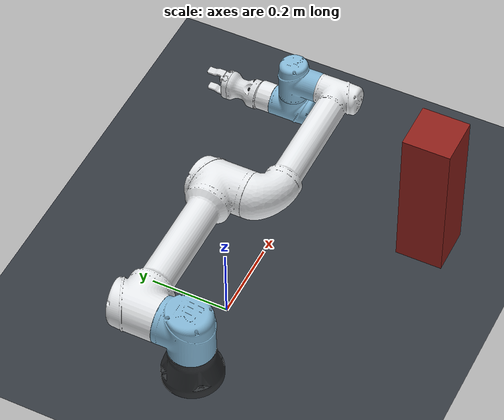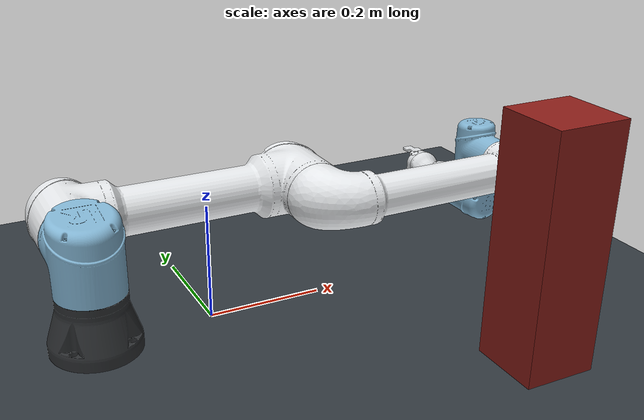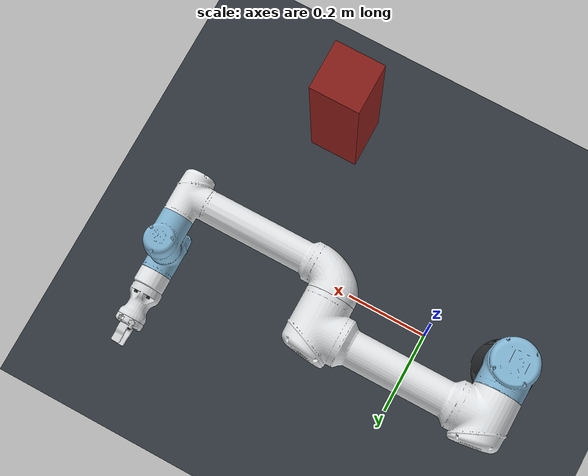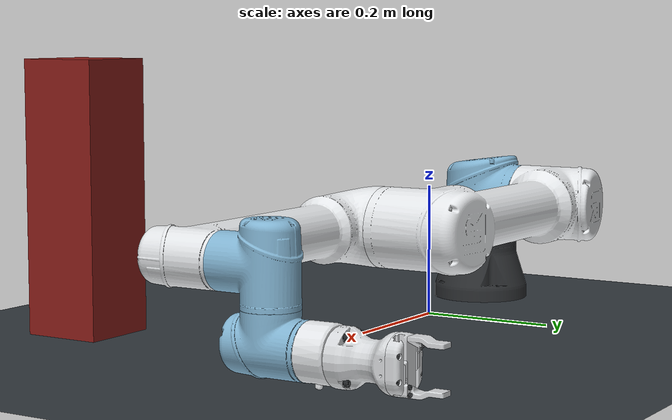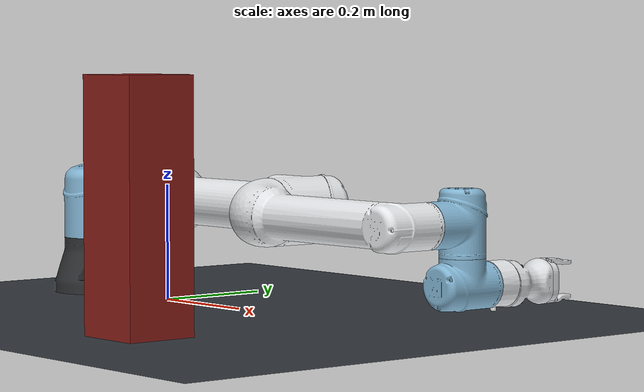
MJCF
<?xml version='1.0' encoding='utf-8'?>
<mujoco model="UR5e + Robotiq Hand-E migration">
  <compiler angle="radian" eulerseq="xyz" meshdir="../assets/meshes" autolimits="true" inertiafromgeom="false" fusestatic="false" />
  <option timestep="0.002" integrator="implicitfast" gravity="0 0 -9.81">
    <flag contact="enable" />
  </option>
  <size njmax="2000" nconmax="500" />
  <statistic center="0 0 0.35" extent="1.25" />
  <visual>
    <headlight diffuse="0.75 0.75 0.75" ambient="0.25 0.25 0.25" specular="0.2 0.2 0.2" />
    <rgba haze="0.15 0.25 0.35 1" />
    <global azimuth="135" elevation="-25" />
  </visual>
  <default>
    <joint limited="true" damping="1.0" armature="0.01" frictionloss="0.05" />
    <geom condim="4" friction="0.8 0.02 0.002" solref="0.005 1" solimp="0.9 0.95 0.001" />
    <default class="visual">
      <geom type="mesh" contype="0" conaffinity="0" group="2" density="0" />
    </default>
    <default class="collision">
      <geom contype="1" conaffinity="1" group="3" rgba="0.2 0.9 0.25 0" />
    </default>
    <default class="arm_joint">
      <joint type="hinge" axis="0 0 1" damping="2.0" armature="0.05" />
    </default>
    <default class="finger_joint">
      <joint type="slide" damping="4.0" armature="0.005" />
    </default>
  </default>
  <asset>
    <texture name="ground_tex" type="2d" builtin="checker" rgb1="0.24 0.27 0.30" rgb2="0.16 0.18 0.20" width="512" height="512" />
    <material name="ground_mat" texture="ground_tex" texrepeat="6 6" reflectance="0.08" />
    <material name="ur_white" rgba="0.91 0.92 0.93 1" />
    <material name="ur_blue" rgba="0.52 0.72 0.84 1" />
    <material name="ur_dark" rgba="0.18 0.19 0.20 1" />
    <material name="hande_white" rgba="0.86 0.87 0.88 1" />
    <material name="hande_dark" rgba="0.14 0.15 0.16 1" />
    <mesh name="base_visual" file="mesh.obj" />
    <mesh name="shoulder_visual" file="mesh_2.obj" />
    <mesh name="upper_arm_visual" file="mesh_4.obj" />
    <mesh name="forearm_visual" file="mesh_6.obj" />
    <mesh name="wrist_1_visual" file="mesh_8.obj" />
    <mesh name="wrist_2_visual" file="mesh_10.obj" />
    <mesh name="wrist_3_visual" file="mesh_12.obj" />
    <mesh name="hande_washer_11" file="toothed_lock_washer_metric_robotiq_11ROBOTIQ_HAND_E_DEFEATURE.obj" />
    <mesh name="hande_group3_0" file="Group3ROBOTIQ_HAND_E_DEFEATURE.obj" />
    <mesh name="hande_screw_6" file="socket_head_cap_screw_iso_robotiq_6ROBOTIQ_HAND_E_DEFEATURE.obj" />
    <mesh name="hande_washer_13" file="toothed_lock_washer_metric_robotiq_13ROBOTIQ_HAND_E_DEFEATURE.obj" />
    <mesh name="hande_group3_1" file="Group3ROBOTIQ_HAND_E_DEFEATURE_1.obj" />
    <mesh name="hande_washer_10" file="toothed_lock_washer_metric_robotiq_10ROBOTIQ_HAND_E_DEFEATURE.obj" />
    <mesh name="hande_screw_24" file="socket_head_cap_screw_iso_robotiq_24ROBOTIQ_HAND_E_DEFEATURE.obj" />
    <mesh name="hande_group3_2" file="Group3ROBOTIQ_HAND_E_DEFEATURE_2.obj" />
    <mesh name="hande_washer_12" file="toothed_lock_washer_metric_robotiq_12ROBOTIQ_HAND_E_DEFEATURE.obj" />
    <mesh name="hande_group3_3" file="Group3ROBOTIQ_HAND_E_DEFEATURE_3.obj" />
    <mesh name="hande_screw_7" file="socket_head_cap_screw_iso_robotiq_7ROBOTIQ_HAND_E_DEFEATURE.obj" />
    <mesh name="hande_screw_25" file="socket_head_cap_screw_iso_robotiq_25ROBOTIQ_HAND_E_DEFEATURE.obj" />
    <mesh name="hande_group3_4" file="Group3ROBOTIQ_HAND_E_DEFEATURE_4.obj" />
    <mesh name="hande_group2" file="Group2ROBOTIQ_HAND_E_DEFEATURE.obj" />
    <mesh name="hande_group3_5" file="Group3ROBOTIQ_HAND_E_DEFEATURE_5.obj" />
    <mesh name="hande_group1" file="Group1ROBOTIQ_HAND_E_DEFEATURE.obj" />
    <mesh name="left_finger_0" file="D_A03_ASM_DOIGTS_PARALLELES_1ROBOTIQ_HAND_E_DEFEATURE.obj" />
    <mesh name="left_finger_1" file="D_A03_ASM_DOIGTS_PARALLELES_1ROBOTIQ_HAND_E_DEFEATURE_1.obj" />
    <mesh name="left_finger_2" file="D_A03_ASM_DOIGTS_PARALLELES_1ROBOTIQ_HAND_E_DEFEATURE_2.obj" />
    <mesh name="right_finger_0" file="D_A03_ASM_DOIGTS_PARALLELES_1ROBOTIQ_HAND_E_DEFEATURE_3.obj" />
    <mesh name="right_finger_1" file="D_A03_ASM_DOIGTS_PARALLELES_1ROBOTIQ_HAND_E_DEFEATURE_4.obj" />
    <mesh name="right_finger_2" file="D_A03_ASM_DOIGTS_PARALLELES_1ROBOTIQ_HAND_E_DEFEATURE_5.obj" />
    <mesh name="left_finger_part_00" vertex="-0.0217400006 0.0155000001 0.0030284482 -0.0217400006 0.01557495 0.0030284482 -0.02174 0.0155000002 0.0004758626 -0.02174 0.01557495 0.0004758626 -0.0217377024 0.01557495 0.000473565 -0.0216650503 0.01557495 0.0004009134 -0.0210077517 0.0155000002 0.0030284482 -0.0172486438 0.0155000001 0.0004758626 -0.0172486438 0.0155000001 0.0030284482 -0.0172486438 0.01557495 0.0004009133" />
    <mesh name="left_finger_part_03" vertex="-0.0217400007 0.0225585211 0.0030284482 -0.0217400007 0.023312475 0.0028204355 -0.0217400007 0.023312475 0.0030284482 -0.0217400006 0.01557495 0.0030284482 -0.0217400002 0.023312475 0.0004758627 -0.02174 0.01557495 0.0004758626 -0.0217377024 0.01557495 0.000473565 -0.0216650503 0.01557495 0.0004009134 -0.0215005082 0.023312475 0.000236372 -0.0212400004 0.023312475 -2.4134e-05 -0.0212400002 0.0160000006 -2.41338e-05 -0.0172486438 0.01557495 0.0004009133 -0.0172486438 0.0159046959 7.11701e-05 -0.0172486438 0.0160000006 -2.41338e-05 -0.0172486438 0.0170872102 -2.41338e-05 -0.0172486438 0.0171496292 -2.41338e-05 -0.0172486438 0.017257278 -2.41338e-05 -0.0172486438 0.0191552695 -2.41339e-05 -0.0172486438 0.023312475 -2.41341e-05" />
    <mesh name="left_finger_part_06" vertex="-0.0217400007 0.023312475 0.0028204355 -0.0217400007 0.023312475 0.0030284482 -0.0217400005 0.0310500001 0.0030284482 -0.0217400004 0.0310500001 0.0004758628 -0.0217400004 0.0310500001 0.0006856846 -0.0217400002 0.023312475 0.0004758627 -0.0215005082 0.023312475 0.000236372 -0.021263314 0.0310500001 -8.209e-07 -0.0212400005 0.0310500001 -2.41342e-05 -0.0212400004 0.023312475 -2.4134e-05 -0.0172486438 0.023312475 -2.41341e-05 -0.0172486438 0.0310500001 -2.41343e-05" />
    <mesh name="left_finger_part_07" vertex="-0.0217400008 0.023312475 0.0049758646 -0.0217400007 0.023312475 0.0030284482 -0.0217400006 0.0310500001 0.0049758644 -0.0217400005 0.0310500001 0.0030284482 -0.021581907 0.0310500001 0.005133958 -0.0210606549 0.023312475 0.0056552103 -0.0210113702 0.023312475 0.0057044949 -0.0209146199 0.023312475 0.0058012451 -0.020785142 0.023312475 0.0059307233 -0.0207400007 0.0310500001 0.0059758651 -0.0207400003 0.0270000001 0.0059758647 -0.0207100602 0.0265431609 0.0060058047 -0.0206207404 0.0260941307 0.0060951243 -0.0206123735 0.023312475 0.0061034908 -0.0204924604 0.0257071403 0.0062234048 -0.0203200605 0.0253376902 0.0063958035 -0.0201447903 0.0252586694 0.0064568238 -0.020133595 0.023312475 0.0065822707 -0.0199298301 0.023312475 0.0067860357 -0.0199298301 0.0243034503 0.0067860357 -0.0199095067 0.023312475 0.0067951315 -0.0199095067 0.0242924057 0.0067951315 -0.0198611007 0.0243224956 0.0067951315 -0.0191729467 0.0248204667 0.0067951315 -0.0177362263 0.0310500001 0.0059758651 -0.0172486438 0.0248179333 0.0067951315 -0.0172486438 0.0252573052 0.0064549277 -0.0172486438 0.0253901362 0.0063999074 -0.0172486438 0.0257740823 0.0062012148 -0.0172486438 0.0260941308 0.0060951244 -0.0172486438 0.0264612276 0.0060221027 -0.0172486438 0.0266265191 0.0060003417 -0.0172486438 0.027 0.0059758647 -0.0172486438 0.0309265517 0.0059758651 -0.0172486438 0.0310500001 0.0059758651" />
    <mesh name="left_finger_part_08" vertex="-0.0199095067 0.023312475 0.0067951315 -0.0199095067 0.0242924057 0.0067951315 -0.0198611007 0.0243224956 0.0067951315 -0.0193834811 0.023312475 0.0070305566 -0.0193367202 0.023981129 0.0070514846 -0.0192261022 0.023312475 0.0071009955 -0.0191729467 0.0248204667 0.0067951315 -0.0191721903 0.0239109807 0.0071251242 -0.0187508605 0.0246301488 0.0069420636 -0.0185426907 0.0245362909 0.0070145242 -0.0183313007 0.0244409697 0.0070881134 -0.0182999405 0.023312475 0.0075155165 -0.0182565306 0.0235205496 0.0075349452 -0.0175399445 0.023312475 0.0078556645 -0.0172486438 0.023312475 0.0079384424 -0.0172486438 0.0238710382 0.0076241229 -0.0172486438 0.0242131534 0.0074649923 -0.0172486438 0.0244464615 0.0070824285 -0.0172486438 0.0245354314 0.0070134822 -0.0172486438 0.0246208746 0.0069472677 -0.0172486438 0.0246848874 0.0068981484 -0.0172486438 0.0248179333 0.0067951315" />
    <mesh name="left_finger_part_09" vertex="-0.0217400012 0.0363105109 0.0016816347 -0.021740001 0.0355329282 0.0030284482 -0.021740001 0.0386432597 0.0030284482 -0.0217400008 0.035007548 0.0030284482 -0.0217400005 0.0310500001 0.0030284482 -0.0217400005 0.0318105109 0.0030284482 -0.0217400005 0.0328922891 0.0030284482 -0.0217400005 0.0341398802 0.0007825362 -0.0217400004 0.0310500001 0.0004758628 -0.0217400004 0.0310500001 0.0006856846 -0.0217400004 0.0318105109 0.0004758628 -0.0217400003 0.0335380914 0.0030284482 -0.0216678676 0.0387875252 0.0030284482 -0.0214606202 0.0387875252 0.0027891419 -0.021263314 0.0310500001 -8.209e-07 -0.0212400005 0.0310500001 -2.41342e-05 -0.0212400005 0.0318105094 -2.41342e-05 -0.0212400003 0.0342692897 0.0002995637 -0.0212400003 0.0365605104 0.0012486263 -0.0212400002 0.0387875252 0.0025343942 -0.0172486438 0.0310500001 -2.41343e-05 -0.0172486438 0.0318105095 -2.41343e-05 -0.0172486438 0.0337785964 0.0002349639 -0.0172486438 0.0342692898 0.0002995636 -0.0172486438 0.0361032565 0.0010592239 -0.0172486438 0.0365605105 0.0012486262 -0.0172486438 0.0376176572 0.0018589703 -0.0172486438 0.0387875252 0.0025343941" />
    <mesh name="left_finger_part_10" vertex="-0.021740001 0.0355329282 0.0030284482 -0.021740001 0.0386432597 0.0030284482 -0.021740001 0.0387875252 0.0031117399 -0.0217400008 0.035007548 0.0030284482 -0.0217400008 0.0387875252 0.0067951315 -0.0217400007 0.0361673394 0.0067951315 -0.0217400007 0.0387875252 0.0050533961 -0.0217400006 0.0310500001 0.0049758644 -0.0217400005 0.0310500001 0.0030284482 -0.0217400005 0.0318105108 0.0049758644 -0.0217400005 0.0318105109 0.0030284482 -0.0217400005 0.0328922891 0.0030284482 -0.0217400005 0.0340605088 0.0055787548 -0.0217400003 0.0335380914 0.0030284482 -0.0217400001 0.0329751997 0.0051291941 -0.0216678676 0.0387875252 0.0030284482 -0.021581907 0.0310500001 0.005133958 -0.0208569362 0.0344012175 0.0067951315 -0.0207400007 0.0310500001 0.0059758651 -0.0207400007 0.0318105099 0.0059758651 -0.0207400004 0.0327163793 0.0060951248 -0.0207400004 0.033560509 0.0064447743 -0.0207400004 0.0341673456 0.0067951315 -0.0177362263 0.0310500001 0.0059758651 -0.0172486438 0.0310500001 0.0059758651 -0.0172486438 0.0318105101 0.005975865 -0.0172486438 0.0325499208 0.0060732101 -0.0172486438 0.0327163794 0.0060951247 -0.0172486438 0.0334053956 0.0063805241 -0.0172486438 0.0335605089 0.0064447744 -0.0172486438 0.0341673453 0.0067951315" />
    <mesh name="left_finger_part_11" vertex="-0.0217400009 0.0387875252 0.0083078933 -0.0217400008 0.0387875252 0.0067951315 -0.0217400007 0.0361673394 0.0067951315 -0.0214670367 0.0387875252 0.0086230833 -0.0208569362 0.0344012175 0.0067951315 -0.0207400008 0.0387875252 0.0094625935 -0.0207400004 0.0341673456 0.0067951315 -0.0172486438 0.0341673453 0.0067951315 -0.0172486438 0.0387875252 0.0094625937" />
    <mesh name="left_finger_part_12" vertex="-0.0216678676 0.0387875252 0.0030284482 -0.0214948917 0.0391334735 0.0030284482 -0.0214606202 0.0387875252 0.0027891419 -0.0212400002 0.0387875252 0.0025343942 -0.0212400001 0.0396432517 0.0030284482 -0.0172486438 0.0387875252 0.0025343941 -0.0172486438 0.0396432519 0.0030284482" />
    <mesh name="left_finger_part_13" vertex="-0.021740001 0.0387875252 0.0031117399 -0.0217400009 0.0412327247 0.0067951315 -0.0217400009 0.0416444534 0.0067951315 -0.0217400009 0.0425967646 0.0067951315 -0.0217400008 0.0387875252 0.0067951315 -0.0217400008 0.0416076913 0.004739964 -0.0217400008 0.0422396191 0.0050346348 -0.0217400008 0.0430649104 0.0067951315 -0.0217400008 0.0465250503 0.0067951315 -0.0217400007 0.0387875252 0.0050533961 -0.0217400007 0.0429130987 0.0052150957 -0.0217400007 0.0436076902 0.0052758645 -0.0217400006 0.0419043616 0.0067951315 -0.0217400006 0.0465250503 0.0052758644 -0.0217400005 0.0423623134 0.0067951315 -0.0216678676 0.0387875252 0.0030284482 -0.0216452338 0.0465250503 0.0051810978 -0.0214948917 0.0391334735 0.0030284482 -0.0212400011 0.0436076915 0.0047758647 -0.021240001 0.042999929 0.0047226936 -0.0212400009 0.0465250503 0.0047758648 -0.0212400006 0.0424106215 0.0045647842 -0.0212400001 0.0396432517 0.0030284482 -0.02124 0.0418576907 0.0043069554 -0.0208323734 0.0465250503 0.0047758647 -0.0174493309 0.0465250503 0.0047758646 -0.0172486438 0.0396432519 0.0030284482 -0.0172486438 0.0418576908 0.0043069554 -0.0172486438 0.0419700712 0.0043535045 -0.0172486438 0.0424126548 0.0045598789 -0.0172486438 0.0424687373 0.0045831088 -0.0172486438 0.042940438 0.0047095046 -0.0172486438 0.0430006219 0.004717427 -0.0172486438 0.0431212187 0.004733305 -0.0172486438 0.0436076914 0.0047758648 -0.0172486438 0.0465250503 0.0047758646" />
    <mesh name="left_finger_part_14" vertex="-0.0217400012 0.0420000012 0.0097758639 -0.021740001 0.040749998 0.0094409251 -0.021740001 0.0465250503 0.0085780568 -0.0217400009 0.0387875252 0.0083078933 -0.0217400009 0.0412327247 0.0067951315 -0.0217400009 0.0416444534 0.0067951315 -0.0217400009 0.0425967646 0.0067951315 -0.0217400009 0.0465250503 0.009775864 -0.0217400008 0.0387875252 0.0067951315 -0.0217400008 0.0430649104 0.0067951315 -0.0217400008 0.0465250503 0.0067951315 -0.0217400006 0.0419043616 0.0067951315 -0.0217400005 0.0423623134 0.0067951315 -0.0217400003 0.0413529511 0.0096906855 -0.0214670367 0.0387875252 0.0086230833 -0.0210061799 0.0465250503 0.010509685 -0.0209540502 0.0420000008 0.0105618148 -0.02095405 0.045638843 0.0105618148 -0.02095405 0.0465250503 0.0105618148 -0.0209372487 0.0418723713 0.0105618148 -0.0208381345 0.0411195285 0.0105618148 -0.0208179729 0.0410672964 0.0105618148 -0.0207400009 0.0402500011 0.0103069544 -0.0207400008 0.0387875252 0.0094625935 -0.0207400005 0.0408652872 0.0105618148 -0.0172486438 0.0387875252 0.0094625937 -0.0172486438 0.0390207691 0.0095972571 -0.0172486438 0.0402500011 0.0103069544 -0.0172486438 0.0404051144 0.0103712046 -0.0172486438 0.0408652871 0.0105618148" />
    <mesh name="left_finger_part_15" vertex="-0.0209540502 0.0420000008 0.0105618148 -0.02095405 0.045638843 0.0105618148 -0.02095405 0.0465250503 0.0105618148 -0.0209372487 0.0418723713 0.0105618148 -0.0208381345 0.0411195285 0.0105618148 -0.0208179729 0.0410672964 0.0105618148 -0.0207400007 0.0465250503 0.0107758642 -0.0207400006 0.0420000006 0.0107758644 -0.0207400005 0.0408652872 0.0105618148 -0.0207400003 0.0410941292 0.0106566045 -0.0207097026 0.0465250503 0.0107758643 -0.0205796144 0.0465250503 0.0107758644 -0.0204373946 0.0465250503 0.0107758643 -0.0202874955 0.0465250503 0.0107758646 -0.0172486438 0.0408652871 0.0105618148 -0.0172486438 0.0410941292 0.0106566045 -0.0172486438 0.0412605881 0.0106785191 -0.0172486438 0.0420000006 0.0107758643 -0.0172486438 0.0461074789 0.0107758643 -0.0172486438 0.0465250503 0.0107758644" />
    <mesh name="left_finger_part_16" vertex="-0.0217400008 0.0465250503 0.0067951315 -0.0217400007 0.053260546 0.0067951315 -0.0217400007 0.0542625754 0.0065298885 -0.0217400007 0.0542625754 0.0067951315 -0.0217400006 0.0465250503 0.0052758644 -0.0217400005 0.0542625754 0.0052758642 -0.0216452338 0.0465250503 0.0051810978 -0.0213938898 0.0542625754 0.0049297544 -0.0212400009 0.0465250503 0.0047758648 -0.0212400005 0.0542625754 0.0047758651 -0.0208323734 0.0465250503 0.0047758647 -0.0197512486 0.0542625754 0.0047758649 -0.0174493309 0.0465250503 0.0047758646 -0.0172486438 0.0465250503 0.0047758646 -0.0172486438 0.0466795022 0.0047758646 -0.0172486438 0.0542625754 0.0047758648" />
    <mesh name="left_finger_part_17" vertex="-0.021740001 0.0465250503 0.0085780568 -0.0217400009 0.0465250503 0.009775864 -0.0217400008 0.0465250503 0.0067951315 -0.0217400007 0.053260546 0.0067951315 -0.0217400007 0.0542625754 0.0067951315 -0.0217400005 0.0542625754 0.0097758642 -0.0214613282 0.0542625754 0.0100545364 -0.0210061799 0.0465250503 0.010509685 -0.02095405 0.0465250503 0.0105618148 -0.0209540498 0.0542625754 0.0105618148" />
    <mesh name="left_finger_part_18" vertex="-0.02095405 0.0465250503 0.0105618148 -0.0209540498 0.0542625754 0.0105618148 -0.0207400008 0.0542625754 0.0107758638 -0.0207400007 0.0465250503 0.0107758642 -0.0207097026 0.0465250503 0.0107758643 -0.0206578951 0.0542625754 0.010775864 -0.0205796144 0.0465250503 0.0107758644 -0.0204373946 0.0465250503 0.0107758643 -0.0203053652 0.0542625754 0.0107758644 -0.0202874955 0.0465250503 0.0107758646 -0.019919959 0.0542625754 0.0107758641 -0.0195137427 0.0542625754 0.0107758649 -0.0172486438 0.0465250503 0.0107758644 -0.0172486438 0.0542625754 0.0107758647" />
    <mesh name="left_finger_part_19" vertex="-0.0217400007 0.0542625754 0.0065298885 -0.0217400007 0.0542625754 0.0067951315 -0.0217400005 0.0542625754 0.0052758642 -0.0217400005 0.059000001 0.0052758641 -0.0217400004 0.0590000008 0.0067951315 -0.0216901755 0.0594421802 0.0067951315 -0.0216837288 0.0595560485 0.0067951315 -0.0216647804 0.0596675583 0.0067951315 -0.02166478 0.0596675574 0.0052758647 -0.0215165861 0.0600910932 0.0067951315 -0.021484808 0.0602005022 0.0067951315 -0.0214429109 0.0603016527 0.0067951315 -0.0214429109 0.0603016528 0.0052758635 -0.0213938898 0.0542625754 0.0049297544 -0.021337563 0.0604693091 0.0067951315 -0.0212400005 0.0542625754 0.0047758651 -0.0212400003 0.0590000009 0.0047758652 -0.0211773204 0.0595562986 0.0047758658 -0.0210854908 0.0608704712 0.0067951315 -0.0210854908 0.0608704716 0.0052758636 -0.0209924204 0.0600847087 0.0047758658 -0.0207504806 0.0612054801 0.0067951315 -0.0206945805 0.060558718 0.0047758651 -0.0206462509 0.0613152653 0.0067951315 -0.0206104707 0.0613454899 0.0052758633 -0.0206104706 0.0613454898 0.0067951315 -0.0204533449 0.0614442195 0.0067951315 -0.0202987199 0.0609545783 0.0047758656 -0.0200416499 0.061702908 0.0052758647 -0.0200416498 0.0617029078 0.0067951315 -0.0198664951 0.0617641958 0.0067951315 -0.0198247108 0.0612524211 0.0047758648 -0.0197512486 0.0542625754 0.0047758649 -0.0194075605 0.0619247804 0.0052758635 -0.0194075604 0.0619247803 0.0067951315 -0.0192963004 0.0614373211 0.0047758656 -0.01922316 0.0619455581 0.0067951315 -0.0187400004 0.0614999984 0.0047758651 -0.0187400003 0.0619999996 0.0052758647 -0.0187400002 0.0619999995 0.0067951315 -0.0172486438 0.0542625754 0.0047758648 -0.0172486438 0.0612869479 0.004775865 -0.0172486438 0.0614999985 0.004775865 -0.0172486438 0.0619502877 0.0052261529 -0.0172486438 0.0619999995 0.0067951315 -0.0172486438 0.0619999996 0.0058226954 -0.0172486438 0.0619999997 0.0052758647" />
    <mesh name="left_finger_part_20" vertex="-0.0217400007 0.0542625754 0.0067951315 -0.0217400005 0.0542625754 0.0097758642 -0.0217400004 0.0590000008 0.0067951315 -0.0217400002 0.0590000004 0.0097758644 -0.0217211406 0.0593358887 0.009794725 -0.0216901755 0.0594421802 0.0067951315 -0.0216837288 0.0595560485 0.0067951315 -0.0216647811 0.0596675602 0.0098510845 -0.0216647804 0.0596675583 0.0067951315 -0.0215716509 0.0599908409 0.0099442146 -0.0215165861 0.0600910932 0.0067951315 -0.021484808 0.0602005022 0.0067951315 -0.0214613282 0.0542625754 0.0100545364 -0.021442911 0.0603016525 0.0100729537 -0.0214429109 0.0603016527 0.0067951315 -0.021337563 0.0604693091 0.0067951315 -0.0210854908 0.0608704712 0.0067951315 -0.0210854907 0.0608704703 0.0104303751 -0.0209540505 0.061009562 0.0105618148 -0.0209540499 0.060821521 0.0105618148 -0.0209540499 0.0608730252 0.0105618148 -0.0209540499 0.0609155759 0.0105618148 -0.0209540498 0.0542625754 0.0105618148 -0.0209540497 0.0607574432 0.0105618148 -0.0209540497 0.0609515242 0.0105618148 -0.0207504806 0.0612054801 0.0067951315 -0.02073496 0.06124033 0.0105618148 -0.0206462509 0.0613152653 0.0067951315 -0.0206104706 0.0613454895 0.0105618148 -0.0206104706 0.0613454898 0.0067951315 -0.0204533449 0.0614442195 0.0067951315 -0.020063787 0.0616889973 0.0105618148 -0.0200416498 0.0617029078 0.0067951315 -0.0200416496 0.0617029073 0.0105618148 -0.0198664951 0.0617641958 0.0067951315 -0.0194322379 0.0619161452 0.0105618148 -0.0194075604 0.06192478 0.0105618148 -0.0194075604 0.0619247803 0.0067951315 -0.01922316 0.0619455581 0.0067951315 -0.0187659804 0.0619970718 0.0105618148 -0.0187400002 0.0619999995 0.0067951315 -0.0187400001 0.0619999992 0.0105618148 -0.0172486438 0.0619999992 0.0105618148 -0.0172486438 0.0619999995 0.0067951315" />
    <mesh name="left_finger_part_21" vertex="-0.0209540505 0.061009562 0.0105618148 -0.0209540499 0.060821521 0.0105618148 -0.0209540499 0.0608730252 0.0105618148 -0.0209540499 0.0609155759 0.0105618148 -0.0209540498 0.0542625754 0.0105618148 -0.0209540497 0.0607574432 0.0105618148 -0.0209540497 0.0609515242 0.0105618148 -0.020740001 0.0612360717 0.0107758635 -0.0207400008 0.0542625754 0.0107758638 -0.02073496 0.06124033 0.0105618148 -0.0206578951 0.0542625754 0.010775864 -0.0206104706 0.0613454895 0.0105618148 -0.0206104706 0.0613454895 0.0107758638 -0.0203053652 0.0542625754 0.0107758644 -0.020063787 0.0616889973 0.0105618148 -0.0200416496 0.0617029073 0.0105618148 -0.0200416496 0.0617029073 0.0107758644 -0.019919959 0.0542625754 0.0107758641 -0.0195137427 0.0542625754 0.0107758649 -0.0194322379 0.0619161452 0.0105618148 -0.0194075604 0.06192478 0.0105618148 -0.0194075604 0.06192478 0.010775864 -0.0187659804 0.0619970718 0.0105618148 -0.0187400001 0.0619999992 0.0105618148 -0.0187400001 0.0619999992 0.0107758652 -0.0172486438 0.0542625754 0.0107758647 -0.0172486438 0.0619999992 0.0105618148 -0.0172486438 0.0619999992 0.0107758651" />
    <mesh name="left_finger_part_22" vertex="-0.0172486438 0.0155000001 0.0004758626 -0.0172486438 0.0155000001 0.0030284482 -0.0172486438 0.01557495 0.0004009133 -0.0127571864 0.0155000001 0.0004758626 -0.0127571864 0.0155000001 0.0030284482 -0.0127571864 0.01557495 0.0004009133" />
    <mesh name="left_finger_part_23" vertex="-0.0172486438 0.0155000001 0.0067951315 -0.0172486438 0.0155000001 0.0079860415 -0.0172486438 0.0155403595 0.0079860413 -0.0172486438 0.01557495 0.0079860413 -0.0149507011 0.01557495 0.0090145205 -0.0127571864 0.0155000001 0.0067951315 -0.0127571864 0.0155000001 0.0099962617 -0.0127571864 0.01557495 0.0099962614" />
    <mesh name="left_finger_part_24" vertex="-0.0172486438 0.01557495 0.0004009133 -0.0172486438 0.0159046959 7.11701e-05 -0.0172486438 0.0160000006 -2.41338e-05 -0.0172486438 0.0170872102 -2.41338e-05 -0.0172486438 0.0171496292 -2.41338e-05 -0.0172486438 0.017257278 -2.41338e-05 -0.0172486438 0.0191552695 -2.41339e-05 -0.0172486438 0.023312475 -2.41341e-05 -0.0127571864 0.01557495 0.0004009133 -0.0127571864 0.0157974499 0.0001784152 -0.0127571864 0.0160000006 -2.41337e-05 -0.0127571864 0.0183106428 -2.41339e-05 -0.0127571864 0.0184433016 -2.41339e-05 -0.0127571864 0.0186720871 -2.41339e-05 -0.0127571864 0.0227058809 -2.41341e-05 -0.0127571864 0.023312475 -2.41341e-05" />
    <mesh name="left_finger_part_25" vertex="-0.0172486438 0.01557495 0.0079860413 -0.0172486438 0.0156345315 0.0079860413 -0.0172486438 0.0162536249 0.0079860417 -0.0172486438 0.0165990363 0.0079860417 -0.0172486438 0.0178316725 0.0079860403 -0.0172486438 0.0191348476 0.0079860411 -0.0172486438 0.0211487441 0.0079860381 -0.0172486438 0.0226499484 0.0079860408 -0.0172486438 0.0232278903 0.0079860407 -0.0172486438 0.023312475 0.0079384424 -0.0170532003 0.0231711395 0.0080735145 -0.0169885758 0.023312475 0.0080123451 -0.0169444166 0.023312475 0.0080226987 -0.0163841441 0.023312475 0.0081798443 -0.0163813098 0.0229760499 0.0083742255 -0.0156395679 0.023312475 0.008348815 -0.0149507011 0.01557495 0.0090145205 -0.0146940156 0.023312475 0.0086858568 -0.0145575406 0.0227831391 0.009190485 -0.0143159656 0.023312475 0.0087978451 -0.0142517598 0.023312475 0.0088168605 -0.0134131986 0.023312475 0.0091115625 -0.0127571864 0.01557495 0.0099962614 -0.0127571864 0.0156079685 0.0099962613 -0.0127571864 0.0158598951 0.0099962613 -0.0127571864 0.0175160786 0.0099962622 -0.0127571864 0.0184401145 0.0099962622 -0.0127571864 0.0217376325 0.0099962587 -0.0127571864 0.0225927208 0.0099962592 -0.0127571864 0.0229647176 0.0096581696 -0.0127571864 0.023312475 0.0092999565" />
    <mesh name="left_finger_part_26" vertex="-0.0172486438 0.0248179333 0.0067951315 -0.0172486438 0.0252573052 0.0064549277 -0.0172486438 0.0253901362 0.0063999074 -0.0172486438 0.0257740823 0.0062012148 -0.0172486438 0.0260941308 0.0060951244 -0.0172486438 0.0264612276 0.0060221027 -0.0172486438 0.0266265191 0.0060003417 -0.0172486438 0.027 0.0059758647 -0.0172486438 0.0309265517 0.0059758651 -0.0172486438 0.0310500001 0.0059758651 -0.0137247255 0.024813294 0.0067951315 -0.0127571864 0.0248116889 0.0067951315 -0.0127571864 0.0248485497 0.0067668469 -0.0127571864 0.0252551896 0.0064519873 -0.0127571864 0.02559402 0.0063116393 -0.0127571864 0.0258667715 0.00617049 -0.0127571864 0.0260941308 0.0060951245 -0.0127571864 0.0263549127 0.0060432506 -0.0127571864 0.0267346829 0.0059932529 -0.0127571864 0.027 0.0059758647 -0.0127571864 0.0297893833 0.005975865 -0.0127571864 0.0310500001 0.0059758649" />
    <mesh name="left_finger_part_27" vertex="-0.0172486438 0.023312475 0.0079384424 -0.0172486438 0.0238710382 0.0076241229 -0.0172486438 0.0242131534 0.0074649923 -0.0172486438 0.0244464615 0.0070824285 -0.0172486438 0.0245354314 0.0070134822 -0.0172486438 0.0246208746 0.0069472677 -0.0172486438 0.0246848874 0.0068981484 -0.0172486438 0.0248179333 0.0067951315 -0.0169885758 0.023312475 0.0080123451 -0.0169444166 0.023312475 0.0080226987 -0.01663572 0.02408418 0.0076783544 -0.0163902101 0.0240325193 0.0077638141 -0.0163841441 0.023312475 0.0081798443 -0.0156395679 0.023312475 0.008348815 -0.0147930107 0.0236964403 0.0083198138 -0.0146940156 0.023312475 0.0086858568 -0.0143159656 0.023312475 0.0087978451 -0.0142517598 0.023312475 0.0088168605 -0.0141578804 0.0236588693 0.008540904 -0.0140551707 0.0236527897 0.008576654 -0.0137247255 0.024813294 0.0067951315 -0.0134131986 0.023312475 0.0091115625 -0.0127571864 0.023312475 0.0092999565 -0.0127571864 0.0235760158 0.0090284921 -0.0127571864 0.0236492558 0.0085759522 -0.0127571864 0.0236544015 0.0085441853 -0.0127571864 0.0236938408 0.0084489703 -0.0127571864 0.0237389363 0.008227178 -0.0127571864 0.0240167452 0.0077544032 -0.0127571864 0.0240541661 0.007690725 -0.0127571864 0.0241989941 0.0075019839 -0.0127571864 0.0244692446 0.0070588442 -0.0127571864 0.0245324479 0.0070098654 -0.0127571864 0.024593146 0.0069628273 -0.0127571864 0.0248116889 0.0067951315" />
    <mesh name="left_finger_part_28" vertex="-0.0172486438 0.0310500001 -2.41343e-05 -0.0172486438 0.0318105095 -2.41343e-05 -0.0172486438 0.0337785964 0.0002349639 -0.0172486438 0.0342692898 0.0002995636 -0.0172486438 0.0361032565 0.0010592239 -0.0172486438 0.0365605105 0.0012486262 -0.0172486438 0.0376176572 0.0018589703 -0.0172486438 0.0387875252 0.0025343941 -0.012831698 0.0387875252 0.002534394 -0.0127571864 0.0310500001 -2.41343e-05 -0.0127571864 0.0318105096 -2.41343e-05 -0.0127571864 0.0332264212 0.0001622701 -0.0127571864 0.0342692899 0.0002995636 -0.0127571864 0.0355887106 0.0008460901 -0.0127571864 0.0365605106 0.0012486262 -0.0127571864 0.0387875252 0.002534394" />
    <mesh name="left_finger_part_29" vertex="-0.0172486438 0.0310500001 0.0059758651 -0.0172486438 0.0318105101 0.005975865 -0.0172486438 0.0325499208 0.0060732101 -0.0172486438 0.0327163794 0.0060951247 -0.0172486438 0.0334053956 0.0063805241 -0.0172486438 0.0335605089 0.0064447744 -0.0172486438 0.0341673453 0.0067951315 -0.0127571864 0.0310500001 0.0059758649 -0.0127571864 0.0318105102 0.0059758649 -0.0127571864 0.0323357803 0.0060450178 -0.0127571864 0.0327163796 0.0060951246 -0.0127571864 0.0332058498 0.0062978695 -0.0127571864 0.0335605086 0.0064447745 -0.0127571864 0.0341673449 0.0067951315" />
    <mesh name="left_finger_part_30" vertex="-0.0172486438 0.0396432519 0.0030284482 -0.0172486438 0.0418576908 0.0043069554 -0.0172486438 0.0419700712 0.0043535045 -0.0172486438 0.0424126548 0.0045598789 -0.0172486438 0.0424687373 0.0045831088 -0.0172486438 0.042940438 0.0047095046 -0.0172486438 0.0430006219 0.004717427 -0.0172486438 0.0431212187 0.004733305 -0.0172486438 0.0436076914 0.0047758648 -0.0172486438 0.0465250503 0.0047758646 -0.0127571864 0.0396432521 0.0030284482 -0.0127571864 0.0418576909 0.0043069553 -0.0127571864 0.0420965326 0.004405886 -0.0127571864 0.0424149429 0.0045543591 -0.0127571864 0.0425341349 0.0046037294 -0.0127571864 0.0428734931 0.0046946631 -0.0127571864 0.0430014016 0.0047115006 -0.0127571864 0.0432577055 0.0047452458 -0.0127571864 0.0436076912 0.0047758649 -0.0127571864 0.0465250503 0.0047758647" />
    <mesh name="left_finger_part_31" vertex="-0.0172486438 0.0387875252 0.0094625937 -0.0172486438 0.0390207691 0.0095972571 -0.0172486438 0.0402500011 0.0103069544 -0.0172486438 0.0404051144 0.0103712046 -0.0172486438 0.0408652871 0.0105618148 -0.016586167 0.0387875252 0.0094625937 -0.0127571864 0.0387875252 0.0094625938 -0.0127571864 0.0402500011 0.0103069545 -0.0127571864 0.0406046599 0.0104538593 -0.0127571864 0.0408652871 0.0105618148" />
    <mesh name="left_finger_part_32" vertex="-0.0172486438 0.0408652871 0.0105618148 -0.0172486438 0.0410941292 0.0106566045 -0.0172486438 0.0412605881 0.0106785191 -0.0172486438 0.0420000006 0.0107758643 -0.0172486438 0.0461074789 0.0107758643 -0.0172486438 0.0465250503 0.0107758644 -0.0168937081 0.0465250503 0.0107758643 -0.0127571864 0.0408652871 0.0105618148 -0.0127571864 0.0410941292 0.0106566046 -0.0127571864 0.0414747293 0.0107067112 -0.0127571864 0.0420000006 0.0107758643 -0.0127571864 0.0465250503 0.0107758643" />
    <mesh name="left_finger_part_33" vertex="-0.0172486438 0.0542625754 0.0047758648 -0.0172486438 0.0612869479 0.004775865 -0.0172486438 0.0614999985 0.004775865 -0.0172486438 0.0619502877 0.0052261529 -0.0172486438 0.0619999995 0.0067951315 -0.0172486438 0.0619999996 0.0058226954 -0.0172486438 0.0619999997 0.0052758647 -0.014596545 0.0619999995 0.0067951315 -0.0127571864 0.0542625754 0.0047758646 -0.0127571864 0.0606453122 0.0047758648 -0.0127571864 0.0614999987 0.0047758649 -0.0127571864 0.0618005723 0.0050764376 -0.0127571864 0.0619999996 0.0067951315 -0.0127571864 0.0619999999 0.0052758646" />
    <mesh name="left_finger_part_34" vertex="-0.0172486438 0.0542625754 0.0107758647 -0.0172486438 0.0619999992 0.0105618148 -0.0172486438 0.0619999992 0.0107758651 -0.0127571864 0.0542625754 0.0107758644 -0.0127571864 0.0619999993 0.0105618148 -0.0127571864 0.0619999993 0.0107758648" />
    <mesh name="left_finger_part_35" vertex="-0.0127571864 0.0155000001 0.0004758626 -0.0127571864 0.0155000001 0.0030284482 -0.0127571864 0.01557495 0.0004009133 -0.0082657289 0.0155 0.0004758625 -0.0082657289 0.0155 0.0030284482 -0.0082657289 0.01557495 0.0004009132" />
    <mesh name="left_finger_part_36" vertex="-0.0127571864 0.0155000001 0.0067951315 -0.0127571864 0.0155000001 0.0099962617 -0.0127571864 0.01557495 0.0099962614 -0.0114935646 0.0155000001 0.0105618148 -0.011493564 0.01557495 0.0105618148 -0.0082657289 0.0155 0.0067951315 -0.0082657289 0.0155000001 0.0105618148" />
    <mesh name="left_finger_part_37" vertex="-0.0114935646 0.0155000001 0.0105618148 -0.011493564 0.01557495 0.0105618148 -0.0082657289 0.0155000001 0.0105618148 -0.0082657289 0.0155000001 0.0120064819 -0.0082657289 0.01557495 0.0120064816" />
    <mesh name="left_finger_part_38" vertex="-0.0127571864 0.01557495 0.0004009133 -0.0127571864 0.0157974499 0.0001784152 -0.0127571864 0.0160000006 -2.41337e-05 -0.0127571864 0.0183106428 -2.41339e-05 -0.0127571864 0.0184433016 -2.41339e-05 -0.0127571864 0.0186720871 -2.41339e-05 -0.0127571864 0.0227058809 -2.41341e-05 -0.0127571864 0.023312475 -2.41341e-05 -0.0119898561 0.023312475 -2.41341e-05 -0.0082657289 0.01557495 0.0004009132 -0.0082657289 0.0156902038 0.0002856603 -0.0082657289 0.0160000007 -2.41336e-05 -0.0082657289 0.0195340754 -2.41339e-05 -0.0082657289 0.0197369741 -2.41339e-05 -0.0082657289 0.0200868963 -2.41339e-05 -0.0082657289 0.023312475 -2.41341e-05" />
    <mesh name="left_finger_part_39" vertex="-0.0127571864 0.01557495 0.0099962614 -0.0127571864 0.0156079685 0.0099962613 -0.0127571864 0.0158598951 0.0099962613 -0.0127571864 0.0175160786 0.0099962622 -0.0127571864 0.0184401145 0.0099962622 -0.0127571864 0.0217376325 0.0099962587 -0.0127571864 0.0225927208 0.0099962592 -0.0127571864 0.0229647176 0.0096581696 -0.0127571864 0.023312475 0.0092999565 -0.0118805406 0.0225000005 0.0103886145 -0.0115486367 0.023312475 0.0096470284 -0.0114935661 0.0178712555 0.0105618148 -0.0114935661 0.0189580809 0.0105618148 -0.011493564 0.01557495 0.0105618148 -0.0114935636 0.0156269896 0.0105618148 -0.0114935636 0.0159232987 0.0105618148 -0.0114935576 0.0225000005 0.0105618148 -0.0098556984 0.023312475 0.0104047296 -0.0095823521 0.0232807616 0.0105618148 -0.0095047216 0.023312475 0.0105618148" />
    <mesh name="left_finger_part_40" vertex="-0.0114935661 0.0178712555 0.0105618148 -0.0114935661 0.0189580809 0.0105618148 -0.011493564 0.01557495 0.0105618148 -0.0114935636 0.0156269896 0.0105618148 -0.0114935636 0.0159232987 0.0105618148 -0.0114935576 0.0225000005 0.0105618148 -0.0095823521 0.0232807616 0.0105618148 -0.0095047216 0.023312475 0.0105618148 -0.0082657289 0.01557495 0.0120064816 -0.0082657289 0.0156755775 0.0120064813 -0.0082657289 0.0160852587 0.0120064813 -0.0082657289 0.0187785323 0.0120064828 -0.0082657289 0.0202811928 0.0120064828 -0.0082657289 0.0225000004 0.0120064804 -0.0082657289 0.0231280079 0.0113184449 -0.0082657289 0.023312475 0.0111163455" />
    <mesh name="left_finger_part_41" vertex="-0.0127571864 0.0248116889 0.0067951315 -0.0127571864 0.0248485497 0.0067668469 -0.0127571864 0.0252551896 0.0064519873 -0.0127571864 0.02559402 0.0063116393 -0.0127571864 0.0258667715 0.00617049 -0.0127571864 0.0260941308 0.0060951245 -0.0127571864 0.0263549127 0.0060432506 -0.0127571864 0.0267346829 0.0059932529 -0.0127571864 0.027 0.0059758647 -0.0127571864 0.0297893833 0.005975865 -0.0127571864 0.0310500001 0.0059758649 -0.0082657289 0.0248042376 0.0067951315 -0.0082657289 0.025012212 0.0066355453 -0.0082657289 0.0252530741 0.0064490469 -0.0082657289 0.0257979039 0.0062233712 -0.0082657289 0.0259594607 0.0061397652 -0.0082657289 0.0260941308 0.0060951245 -0.0082657289 0.0262485978 0.0060643984 -0.0082657289 0.0268428467 0.0059861642 -0.0082657289 0.027 0.0059758648 -0.0082657289 0.0286522148 0.0059758649 -0.0082657289 0.0310500001 0.0059758648" />
    <mesh name="left_finger_part_42" vertex="-0.0127571864 0.023312475 0.0092999565 -0.0127571864 0.0235760158 0.0090284921 -0.0127571864 0.0236492558 0.0085759522 -0.0127571864 0.0236544015 0.0085441853 -0.0127571864 0.0236938408 0.0084489703 -0.0127571864 0.0237389363 0.008227178 -0.0127571864 0.0240167452 0.0077544032 -0.0127571864 0.0240541661 0.007690725 -0.0127571864 0.0241989941 0.0075019839 -0.0127571864 0.0244692446 0.0070588442 -0.0127571864 0.0245324479 0.0070098654 -0.0127571864 0.024593146 0.0069628273 -0.0127571864 0.0248116889 0.0067951315 -0.0115486367 0.023312475 0.0096470284 -0.0114720306 0.0235000007 0.0094758644 -0.0098556984 0.023312475 0.0104047296 -0.0095047216 0.023312475 0.0105618148 -0.0090456822 0.0235000007 0.0105618148 -0.0082657289 0.0235000007 0.0094758644 -0.0082657289 0.0235000007 0.0105618148 -0.0082657289 0.0235392918 0.0091774179 -0.0082657289 0.0236370272 0.0085735236 -0.0082657289 0.0236400752 0.0085547074 -0.0082657289 0.0238059804 0.0081541765 -0.0082657289 0.0238326915 0.0080228038 -0.0082657289 0.023997244 0.0077427686 -0.0082657289 0.0240194092 0.0077050506 -0.0082657289 0.0243319522 0.0072977416 -0.0082657289 0.0244920277 0.0070352599 -0.0082657289 0.0245294645 0.0070062487 -0.0082657289 0.0245654173 0.0069783869 -0.0082657289 0.0248042376 0.0067951315" />
    <mesh name="left_finger_part_43" vertex="-0.0095047216 0.023312475 0.0105618148 -0.0090456822 0.0235000007 0.0105618148 -0.0082657289 0.023312475 0.0111163455 -0.0082657289 0.0235000007 0.0105618148 -0.0082657289 0.0235000007 0.0109108952" />
    <mesh name="left_finger_part_44" vertex="-0.0127571864 0.0310500001 -2.41343e-05 -0.0127571864 0.0318105096 -2.41343e-05 -0.0127571864 0.0332264212 0.0001622701 -0.0127571864 0.0342692899 0.0002995636 -0.0127571864 0.0355887106 0.0008460901 -0.0127571864 0.0365605106 0.0012486262 -0.0127571864 0.0387875252 0.002534394 -0.0082657289 0.0310500001 -2.41344e-05 -0.0082657289 0.0318105098 -2.41344e-05 -0.0082657289 0.032674246 8.95763e-05 -0.0082657289 0.03426929 0.0002995635 -0.0082657289 0.0350741648 0.0006329564 -0.0082657289 0.0365605107 0.0012486262 -0.0082657289 0.0387875252 0.0025343938" />
    <mesh name="left_finger_part_45" vertex="-0.0127571864 0.0310500001 0.0059758649 -0.0127571864 0.0318105102 0.0059758649 -0.0127571864 0.0323357803 0.0060450178 -0.0127571864 0.0327163796 0.0060951246 -0.0127571864 0.0332058498 0.0062978695 -0.0127571864 0.0335605086 0.0064447745 -0.0127571864 0.0341673449 0.0067951315 -0.0082657289 0.0310500001 0.0059758648 -0.0082657289 0.0318105104 0.0059758648 -0.0082657289 0.0321216397 0.0060168256 -0.0082657289 0.0327163797 0.0060951244 -0.0082657289 0.0330063041 0.0062152149 -0.0082657289 0.0335605084 0.0064447745 -0.0082657289 0.0341673445 0.0067951315" />
    <mesh name="left_finger_part_46" vertex="-0.0127571864 0.0396432521 0.0030284482 -0.0127571864 0.0418576909 0.0043069553 -0.0127571864 0.0420965326 0.004405886 -0.0127571864 0.0424149429 0.0045543591 -0.0127571864 0.0425341349 0.0046037294 -0.0127571864 0.0428734931 0.0046946631 -0.0127571864 0.0430014016 0.0047115006 -0.0127571864 0.0432577055 0.0047452458 -0.0127571864 0.0436076912 0.0047758649 -0.0127571864 0.0465250503 0.0047758647 -0.0096008207 0.0396432522 0.0030284482 -0.0082657289 0.0396432523 0.0030284482 -0.0082657289 0.0399968634 0.0032326057 -0.0082657289 0.041857691 0.0043069553 -0.0082657289 0.0422229939 0.0044582674 -0.0082657289 0.042417231 0.0045488392 -0.0082657289 0.0425995325 0.0046243501 -0.0082657289 0.0428065482 0.0046798215 -0.0082657289 0.0430021813 0.0047055741 -0.0082657289 0.0433941922 0.0047571867 -0.0082657289 0.043607691 0.004775865 -0.0082657289 0.0465250503 0.0047758648" />
    <mesh name="left_finger_part_47" vertex="-0.0127571864 0.0387875252 0.0094625938 -0.0127571864 0.0402500011 0.0103069545 -0.0127571864 0.0406046599 0.0104538593 -0.0127571864 0.0408652871 0.0105618148 -0.0082657289 0.0387875252 0.0094625938 -0.0082657289 0.0402500011 0.0103069545 -0.0082657289 0.0408042055 0.010536514 -0.0082657289 0.040865287 0.0105618148" />
    <mesh name="left_finger_part_48" vertex="-0.0127571864 0.0408652871 0.0105618148 -0.0127571864 0.0410941292 0.0106566046 -0.0127571864 0.0414747293 0.0107067112 -0.0127571864 0.0420000006 0.0107758643 -0.0127571864 0.0465250503 0.0107758643 -0.0082657289 0.040865287 0.0105618148 -0.0082657289 0.0410941292 0.0106566046 -0.0082657289 0.0416888705 0.0107349033 -0.0082657289 0.0420000005 0.0107758642 -0.0082657289 0.0465250503 0.0107758642" />
    <mesh name="left_finger_part_49" vertex="-0.0127571864 0.0542625754 0.0047758646 -0.0127571864 0.0606453122 0.0047758648 -0.0127571864 0.0614999987 0.0047758649 -0.0127571864 0.0618005723 0.0050764376 -0.0127571864 0.0619999996 0.0067951315 -0.0127571864 0.0619999999 0.0052758646 -0.0082657289 0.0542625754 0.0047758644 -0.0082657289 0.0600036766 0.0047758646 -0.0082657289 0.061499999 0.0047758648 -0.0082657289 0.0616508569 0.0049267223 -0.0082657289 0.0619999999 0.0067951315 -0.0082657289 0.0620000002 0.0052758645" />
    <mesh name="left_finger_part_50" vertex="-0.0127571864 0.0542625754 0.0107758644 -0.0127571864 0.0619999993 0.0105618148 -0.0127571864 0.0619999993 0.0107758648 -0.0103168114 0.0542625754 0.0107758642 -0.0082657289 0.0542625754 0.0107758642 -0.0082657289 0.0566756134 0.0107758642 -0.0082657289 0.0619999994 0.0105618148 -0.0082657289 0.0619999994 0.0107758644" />
    <mesh name="left_finger_part_51" vertex="-0.0041000005 0.0031749799 0.0030284482 -0.0041000005 0.0031749801 -0.0007381346 -0.0041000005 0.0037056657 0.0030284482 -0.0041000005 0.0078374249 -0.0007381349 -0.0041000005 0.0078374249 0.0008424893 -0.0041000004 0.0078374249 0.0030284482 -0.0037742715 0.003146482 -0.000665675 -0.0037742715 0.0031464824 0.0030284482 -0.0037742715 0.0031464825 0.0001644048 -0.0037742715 0.0078374249 -0.0006656753" />
    <mesh name="left_finger_part_52" vertex="-0.0041000005 0.0031749799 0.0030284482 -0.0041000005 0.0031749799 0.0033092142 -0.0041000005 0.0031749804 0.0052428342 -0.0041000005 0.0037056657 0.0030284482 -0.0041000005 0.0078374249 0.0052428339 -0.0041000005 0.0078374249 0.0054692104 -0.0041000004 0.0031749797 0.0058224943 -0.0041000004 0.0078374249 0.0030284482 -0.0041000004 0.0078374249 0.0033092144 -0.0041000004 0.0078374249 0.0058224943 -0.0037742715 0.0031464821 0.0059410482 -0.0037742715 0.0031464824 0.0030284482 -0.0037742715 0.0031464824 0.0034277702 -0.0037742715 0.0031464827 0.0051242781 -0.0037742715 0.0031464828 0.00547367 -0.0037742715 0.0046853133 0.0051242782 -0.0037742715 0.0078374249 0.0034277703 -0.0037742715 0.0078374249 0.005124278 -0.0037742715 0.0078374249 0.0059410483" />
    <mesh name="left_finger_part_53" vertex="-0.0041000008 0.0031749803 0.0102693848 -0.0041000006 0.00317498 0.0105618148 -0.0041000006 0.0031749801 0.0077561143 -0.0041000006 0.0031749803 0.0083357634 -0.0041000006 0.0078374249 0.0102693851 -0.0041000005 0.0069656186 0.0105618148 -0.0041000005 0.0078374249 0.007756114 -0.0041000005 0.0078374249 0.0079824863 -0.0041000005 0.0078374249 0.0083357636 -0.0041000005 0.0078374249 0.0104957575 -0.0041000005 0.0078374249 0.0105618148 -0.0037742715 0.0031464826 0.0076375585 -0.0037742715 0.0031464826 0.0079869501 -0.0037742715 0.0031464826 0.0105618148 -0.0037742715 0.0031464827 0.0084543195 -0.0037742715 0.0031464827 0.0101508287 -0.0037742715 0.0031464827 0.0105002207 -0.0037742715 0.0046853132 0.0076375583 -0.0037742715 0.004685314 0.0101508288 -0.0037742715 0.0078374249 0.0076375581 -0.0037742715 0.0078374249 0.0084543196 -0.0037742715 0.0078374249 0.010150829" />
    <mesh name="left_finger_part_54" vertex="-0.0041000006 0.00317498 0.0105618148 -0.0041000005 0.0031749797 0.0108490343 -0.0041000005 0.0031749798 0.0127826535 -0.0041000005 0.0069656186 0.0105618148 -0.0041000005 0.0078374249 0.0105618148 -0.0041000005 0.0078374249 0.0108490343 -0.0041000005 0.0078374249 0.0127826535 -0.0041000005 0.0078374249 0.0130090307 -0.0041000003 0.0031749799 0.0133623152 -0.0041000003 0.0078374249 0.0133623147 -0.0037742715 0.0031464821 0.0109675902 -0.0037742715 0.0031464822 0.0130134914 -0.0037742715 0.0031464823 0.0134808709 -0.0037742715 0.0031464824 0.0126640979 -0.0037742715 0.0031464826 0.0105618148 -0.0037742715 0.0046853128 0.0126640979 -0.0037742715 0.0078374249 0.0109675903 -0.0037742715 0.0078374249 0.0126640979 -0.0037742715 0.0078374249 0.0134808705" />
    <mesh name="left_finger_part_55" vertex="-0.0041000007 0.0031749808 0.015295934 -0.0041000005 0.0031749801 0.0158755856 -0.0041000005 0.0031749802 0.0178092048 -0.0041000005 0.0031749804 0.0180951815 -0.0041000005 0.0078374249 0.015295934 -0.0041000005 0.0078374249 0.0158755854 -0.0041000004 0.0070508439 0.0180951815 -0.0041000004 0.0078374249 0.0155223073 -0.0041000004 0.0078374249 0.0178092048 -0.0041000004 0.0078374249 0.0180355807 -0.0041000004 0.0078374249 0.0180951815 -0.0037742715 0.0031464825 0.0159941411 -0.0037742715 0.0031464826 0.0180400424 -0.0037742715 0.0031464826 0.0180951815 -0.0037742715 0.0031464827 0.0176906488 -0.0037742715 0.0031464829 0.015177378 -0.0037742715 0.003146483 0.0155267698 -0.0037742715 0.0046853128 0.0176906489 -0.0037742715 0.0046853141 0.015177378 -0.0037742715 0.0078374249 0.0151773781 -0.0037742715 0.0078374249 0.0159941409 -0.0037742715 0.0078374249 0.017690649" />
    <mesh name="left_finger_part_56" vertex="-0.0041000005 0.0031749804 0.0180951815 -0.0041000005 0.0031749807 0.0183888631 -0.0041000005 0.0078374249 0.0183888633 -0.0041000005 0.0078374249 0.0203224848 -0.0041000005 0.0078374249 0.0205488572 -0.0041000004 0.0031749799 0.0203224849 -0.0041000004 0.0031749803 0.0209021344 -0.0041000004 0.0070508439 0.0180951815 -0.0041000004 0.0078374249 0.0180951815 -0.0041000004 0.0078374249 0.0209021345 -0.0037742715 0.0031464823 0.0205533206 -0.0037742715 0.0031464825 0.0202039289 -0.0037742715 0.0031464826 0.0180951815 -0.0037742715 0.0031464826 0.0210206904 -0.0037742715 0.003146483 0.0185074192 -0.0037742715 0.0046853125 0.0202039289 -0.0037742715 0.0078374249 0.0185074194 -0.0037742715 0.0078374249 0.0202039289 -0.0037742715 0.0078374249 0.0210206905" />
    <mesh name="left_finger_part_57" vertex="-0.0041000009 0.0031749807 0.0228357545 -0.0041000007 0.0031749805 0.0253490347 -0.0041000007 0.0031749807 0.0256285481 -0.0041000007 0.0071360884 0.0256285481 -0.0041000007 0.0078374249 0.0253490349 -0.0041000007 0.0078374249 0.0255754073 -0.0041000007 0.0078374249 0.0256285481 -0.0041000006 0.0078374249 0.0228357546 -0.0041000004 0.0078374249 0.0234154046 -0.0041000003 0.0031749794 0.0234154047 -0.0041000003 0.0078374249 0.0230621272 -0.0037742715 0.003146482 0.0235339605 -0.0037742715 0.0031464827 0.0252304788 -0.0037742715 0.0031464828 0.0255798706 -0.0037742715 0.0031464829 0.0227171986 -0.0037742715 0.0031464829 0.0256285481 -0.0037742715 0.003146483 0.0230665905 -0.0037742715 0.0046853139 0.0252304787 -0.0037742715 0.0046853148 0.0227171985 -0.0037742715 0.0078374249 0.0227171986 -0.0037742715 0.0078374249 0.0235339604 -0.0037742715 0.0078374249 0.0252304789" />
    <mesh name="left_finger_part_58" vertex="-0.0041000007 0.0031749807 0.0256285481 -0.0041000007 0.0031749808 0.0259286841 -0.0041000007 0.0071360884 0.0256285481 -0.0041000007 0.0078374249 0.0256285481 -0.0041000007 0.0078374249 0.0259286841 -0.0041000006 0.00317498 0.0284419545 -0.0041000005 0.0078374249 0.0280886771 -0.0041000005 0.0078374249 0.0284419542 -0.0041000003 0.0078374249 0.0278623047 -0.0041000002 0.0031749798 0.0278623049 -0.0037742715 0.0031464822 0.0280931405 -0.0037742715 0.0031464823 0.027743749 -0.0037742715 0.0031464823 0.0285605105 -0.0037742715 0.0031464829 0.0256285481 -0.0037742715 0.0031464831 0.0260472402 -0.0037742715 0.0046853115 0.0277437491 -0.0037742715 0.0078374249 0.0260472402 -0.0037742715 0.0078374249 0.0277437489 -0.0037742715 0.0078374249 0.0285605102" />
    <mesh name="left_finger_part_59" vertex="-0.0041000006 0.0031749805 0.0303755745 -0.0041000006 0.0078374249 0.0303755746 -0.0041000005 0.0072212553 0.0331619147 -0.0041000005 0.0078374249 0.0331152271 -0.0041000005 0.0078374249 0.0331619147 -0.0041000004 0.0078374249 0.0306019511 -0.0041000003 0.0031749804 0.0331619147 -0.0041000003 0.0078374249 0.0309552346 -0.0041000003 0.0078374249 0.0328888545 -0.0041000001 0.0031749802 0.0328888541 -0.0041 0.0031749799 0.0309552345 -0.0037742715 0.0031464825 0.0310737902 -0.0037742715 0.0031464826 0.0331196898 -0.0037742715 0.0031464827 0.0331619147 -0.0037742715 0.0031464828 0.0302570187 -0.0037742715 0.0031464828 0.0327702983 -0.0037742715 0.003146483 0.0306064122 -0.0037742715 0.0046853118 0.0327702984 -0.0037742715 0.0046853132 0.0302570187 -0.0037742715 0.0078374249 0.0302570188 -0.0037742715 0.0078374249 0.0310737904 -0.0037742715 0.0078374249 0.0327702986" />
    <mesh name="left_finger_part_60" vertex="-0.0041000008 0.0031749803 0.0359817843 -0.0041000006 0.0078374249 0.0356285005 -0.0041000005 0.0031749806 0.0334685041 -0.0041000005 0.0072212553 0.0331619147 -0.0041000005 0.0078374249 0.0331619147 -0.0041000005 0.0078374249 0.0334685044 -0.0041000005 0.0078374249 0.0359817845 -0.0041000003 0.0031749804 0.0331619147 -0.0041000003 0.0078374249 0.0354021242 -0.0040999999 0.0031749796 0.0354021249 -0.0037742715 0.0031464821 0.035283569 -0.0037742715 0.0031464821 0.0356329623 -0.0037742715 0.0031464826 0.0361003404 -0.0037742715 0.0031464827 0.0331619147 -0.0037742715 0.003146483 0.0335870601 -0.0037742715 0.0046853102 0.0352835691 -0.0037742715 0.0078374249 0.0335870604 -0.0037742715 0.0078374249 0.0352835686 -0.0037742715 0.0078374249 0.0361003405" />
    <mesh name="left_finger_part_61" vertex="-0.0041000008 0.0031749808 0.0379154043 -0.0041000008 0.0078374249 0.0379154041 -0.0041000007 0.0031749797 0.0384950551 -0.0041000007 0.0031749798 0.0404286743 -0.0041000007 0.0031749799 0.0406952813 -0.0041000007 0.0078374249 0.038141777 -0.0041000007 0.0078374249 0.0384950549 -0.0041000004 0.0078374249 0.040428674 -0.0041000004 0.0078374249 0.0406952813 -0.0039514019 0.0031619789 0.0406952813 -0.0037742715 0.0031464821 0.0406952813 -0.0037742715 0.0031464822 0.0386136109 -0.0037742715 0.0031464824 0.0403101183 -0.0037742715 0.0031464831 0.0377968485 -0.0037742715 0.0031464831 0.0381462403 -0.0037742715 0.0046853136 0.0403101182 -0.0037742715 0.0046853143 0.0377968483 -0.0037742715 0.0078374249 0.0377968482 -0.0037742715 0.0078374249 0.0386136107 -0.0037742715 0.0078374249 0.0403101181" />
    <mesh name="left_finger_part_62" vertex="-0.0041000007 0.0031749799 0.0406952813 -0.0041000004 0.0078374249 0.0406952813 -0.0041000002 0.0031749806 0.0444618633 -0.0041000002 0.0078374249 0.0420037683 -0.0041000002 0.0078374249 0.0444618641 -0.0039514019 0.0031619789 0.0406952813 -0.0037742715 0.0031464818 0.041013078 -0.0037742715 0.0031464821 0.0406952813 -0.0037742715 0.0031464825 0.0443894037 -0.0037742715 0.0044493974 0.0443894036 -0.0037742715 0.0078374249 0.0443894042" />
    <mesh name="left_finger_part_63" vertex="-0.0082657289 0.0155 0.0004758625 -0.0082657289 0.0155 0.0030284482 -0.0082657289 0.01557495 0.0004009132 -0.008240642 0.0155 0.0030284482 -0.0041000005 0.0078374249 -0.0007381349 -0.0041000005 0.0078374249 0.0008424893 -0.0041000004 0.0078374249 0.0030284482 -0.0041000004 0.0108250195 -0.0007381351 -0.0041000004 0.0108250197 0.0030284482 -0.0039441248 0.0108386573 0.0030284482 -0.0037742715 0.0078374249 -0.0006656753 -0.0037742715 0.0095506021 -0.0006656754 -0.0037742715 0.0108535176 -0.0006656755 -0.0037742715 0.0108535176 0.0030284482 -0.0037742715 0.0108535178 0.0027225048 -0.0037742715 0.0155 0.0004758625 -0.0037742715 0.0155 0.001592696 -0.0037742715 0.0155 0.0030284482 -0.0037742715 0.01557495 0.0004009131" />
    <mesh name="left_finger_part_64" vertex="-0.0082657289 0.0155 0.0030284482 -0.0082657289 0.0155 0.0030365126 -0.0082657289 0.0155 0.0067951315 -0.008240642 0.0155 0.0030284482 -0.0041000005 0.0078374249 0.0052428339 -0.0041000005 0.0078374249 0.0054692104 -0.0041000005 0.0108250198 0.0052428337 -0.0041000005 0.0108250199 0.0058224944 -0.0041000004 0.0078374249 0.0030284482 -0.0041000004 0.0078374249 0.0033092144 -0.0041000004 0.0078374249 0.0058224943 -0.0041000004 0.0108250197 0.0030284482 -0.0041000004 0.0108250197 0.0033092145 -0.0039441248 0.0108386573 0.0030284482 -0.0037742715 0.0078374249 0.0034277703 -0.0037742715 0.0078374249 0.005124278 -0.0037742715 0.0078374249 0.0059410483 -0.0037742715 0.0093146872 0.0059410483 -0.0037742715 0.0093146876 0.0034277704 -0.0037742715 0.0108535173 0.0034277704 -0.0037742715 0.0108535174 0.0059410481 -0.0037742715 0.0108535175 0.0051242778 -0.0037742715 0.0108535175 0.0055916566 -0.0037742715 0.0108535176 0.0030284482 -0.0037742715 0.0155 0.0030284482 -0.0037742715 0.0155 0.0067951315" />
    <mesh name="left_finger_part_65" vertex="-0.0082657289 0.0155 0.0067951315 -0.0082657289 0.0155000001 0.0105618148 -0.0041000006 0.0078374249 0.0102693851 -0.0041000005 0.0078374249 0.007756114 -0.0041000005 0.0078374249 0.0079824863 -0.0041000005 0.0078374249 0.0083357636 -0.0041000005 0.0078374249 0.0104957575 -0.0041000005 0.0078374249 0.0105618148 -0.0041000005 0.0108250196 0.0077561138 -0.0041000005 0.0108250198 0.0102693853 -0.0041000005 0.0108250198 0.0105618148 -0.0041000005 0.0108250201 0.0083357637 -0.0037742715 0.0078374249 0.0076375581 -0.0037742715 0.0078374249 0.0084543196 -0.0037742715 0.0078374249 0.010150829 -0.0037742715 0.0093146874 0.0084543196 -0.0037742715 0.0108535172 0.007637558 -0.0037742715 0.0108535173 0.0101508292 -0.0037742715 0.0108535174 0.0105618148 -0.0037742715 0.0108535176 0.008104928 -0.0037742715 0.0108535177 0.0084543197 -0.0037742715 0.0155 0.0067951315 -0.0037742715 0.0155 0.0105618148" />
    <mesh name="left_finger_part_66" vertex="-0.0082657289 0.0155000001 0.0105618148 -0.0082657289 0.0155000001 0.0120064819 -0.0082657289 0.01557495 0.0120064816 -0.0041000005 0.0078374249 0.0105618148 -0.0041000005 0.0078374249 0.0108490343 -0.0041000005 0.0078374249 0.0127826535 -0.0041000005 0.0078374249 0.0130090307 -0.0041000005 0.0108250198 0.0105618148 -0.0041000005 0.0108250199 0.0108490343 -0.0041000005 0.01082502 0.0127826535 -0.0041000004 0.0108250197 0.0133623144 -0.0041000003 0.0078374249 0.0133623147 -0.0037742715 0.0078374249 0.0109675903 -0.0037742715 0.0078374249 0.0126640979 -0.0037742715 0.0078374249 0.0134808705 -0.0037742715 0.0093146871 0.0109675903 -0.0037742715 0.0093146876 0.0134808703 -0.0037742715 0.0108535173 0.0131314769 -0.0037742715 0.0108535173 0.0134808703 -0.0037742715 0.0108535174 0.0105618148 -0.0037742715 0.0108535174 0.0106181986 -0.0037742715 0.0108535174 0.0109675903 -0.0037742715 0.0108535176 0.012664098 -0.0037742715 0.0155 0.0105618148 -0.0037742715 0.0155000001 0.0140167021 -0.0037742715 0.01557495 0.0140167018" />
    <mesh name="left_finger_part_67" vertex="-0.0041000005 0.0078374249 0.015295934 -0.0041000005 0.0078374249 0.0158755854 -0.0041000005 0.0108250201 0.0158755853 -0.0041000004 0.0078374249 0.0155223073 -0.0041000004 0.0078374249 0.0178092048 -0.0041000004 0.0078374249 0.0180355807 -0.0041000004 0.0078374249 0.0180951815 -0.0041000004 0.0108250197 0.0180951815 -0.0041000004 0.01082502 0.015295934 -0.0041000003 0.0108250194 0.0178092049 -0.0037742715 0.0078374249 0.0151773781 -0.0037742715 0.0078374249 0.0159941409 -0.0037742715 0.0078374249 0.017690649 -0.0037742715 0.0093146871 0.0159941408 -0.0037742715 0.010853517 0.017690649 -0.0037742715 0.0108535174 0.0180951815 -0.0037742715 0.0108535176 0.0151773781 -0.0037742715 0.0108535176 0.0159941409 -0.0037742715 0.0108535177 0.0156447492" />
    <mesh name="left_finger_part_68" vertex="-0.0041000006 0.01082502 0.0203224848 -0.0041000005 0.0078374249 0.0183888633 -0.0041000005 0.0078374249 0.0203224848 -0.0041000005 0.0078374249 0.0205488572 -0.0041000005 0.0108250199 0.0183888635 -0.0041000004 0.0078374249 0.0180951815 -0.0041000004 0.0078374249 0.0209021345 -0.0041000004 0.0108250197 0.0180951815 -0.0041000003 0.0108250195 0.0209021346 -0.0037742715 0.0078374249 0.0185074194 -0.0037742715 0.0078374249 0.0202039289 -0.0037742715 0.0078374249 0.0210206905 -0.0037742715 0.0093146873 0.0185074194 -0.0037742715 0.0093146875 0.0210206905 -0.0037742715 0.0108535172 0.0206712989 -0.0037742715 0.0108535172 0.0210206905 -0.0037742715 0.0108535174 0.0180951815 -0.0037742715 0.0108535174 0.018158026 -0.0037742715 0.0108535175 0.0185074195 -0.0037742715 0.0108535176 0.0202039288" />
    <mesh name="left_finger_part_69" vertex="-0.0041000007 0.0078374249 0.0253490349 -0.0041000007 0.0078374249 0.0255754073 -0.0041000007 0.0078374249 0.0256285481 -0.0041000007 0.0108250199 0.0256285481 -0.0041000006 0.0078374249 0.0228357546 -0.0041000006 0.0108250199 0.0253490351 -0.0041000005 0.0108250194 0.0234154045 -0.0041000004 0.0078374249 0.0234154046 -0.0041000004 0.0108250201 0.0228357546 -0.0041000003 0.0078374249 0.0230621272 -0.0037742715 0.0078374249 0.0227171986 -0.0037742715 0.0078374249 0.0235339604 -0.0037742715 0.0078374249 0.0252304789 -0.0037742715 0.0093146864 0.0235339604 -0.0037742715 0.0108535171 0.0231845687 -0.0037742715 0.0108535171 0.0235339604 -0.0037742715 0.0108535174 0.0252304791 -0.0037742715 0.0108535175 0.0256285481 -0.0037742715 0.0108535176 0.0227171987" />
    <mesh name="left_finger_part_70" vertex="-0.0041000007 0.0078374249 0.0256285481 -0.0041000007 0.0078374249 0.0259286841 -0.0041000007 0.0108250199 0.0256285481 -0.0041000007 0.01082502 0.0259286842 -0.0041000005 0.0078374249 0.0280886771 -0.0041000005 0.0078374249 0.0284419542 -0.0041000004 0.0108250197 0.0278623046 -0.0041000004 0.0108250201 0.0284419541 -0.0041000003 0.0078374249 0.0278623047 -0.0037742715 0.0078374249 0.0260472402 -0.0037742715 0.0078374249 0.0277437489 -0.0037742715 0.0078374249 0.0285605102 -0.0037742715 0.0093146864 0.0260472402 -0.0037742715 0.0093146879 0.0285605101 -0.0037742715 0.0108535174 0.0277437488 -0.0037742715 0.0108535175 0.0256285481 -0.0037742715 0.0108535175 0.0256978484 -0.0037742715 0.0108535175 0.0260472402 -0.0037742715 0.0108535176 0.0282111185 -0.0037742715 0.0108535177 0.02856051" />
    <mesh name="left_finger_part_71" vertex="-0.0041000006 0.0078374249 0.0303755746 -0.0041000006 0.0108250197 0.0303755746 -0.0041000005 0.0078374249 0.0331152271 -0.0041000005 0.0078374249 0.0331619147 -0.0041000004 0.0078374249 0.0306019511 -0.0041000004 0.0108250189 0.0309552347 -0.0041000004 0.0108250195 0.0328888547 -0.0041000004 0.0108250197 0.0331619147 -0.0041000003 0.0078374249 0.0309552346 -0.0041000003 0.0078374249 0.0328888545 -0.0037742715 0.0078374249 0.0302570188 -0.0037742715 0.0078374249 0.0310737904 -0.0037742715 0.0078374249 0.0327702986 -0.0037742715 0.0093146868 0.0310737904 -0.0037742715 0.0108535166 0.0307243971 -0.0037742715 0.0108535168 0.0310737905 -0.0037742715 0.0108535172 0.0302570188 -0.0037742715 0.0108535173 0.0327702988 -0.0037742715 0.0108535176 0.0331619147" />
    <mesh name="left_finger_part_72" vertex="-0.0041000006 0.0078374249 0.0356285005 -0.0041000005 0.0078374249 0.0331619147 -0.0041000005 0.0078374249 0.0334685044 -0.0041000005 0.0078374249 0.0359817845 -0.0041000005 0.0108250202 0.0354021238 -0.0041000004 0.0108250197 0.0331619147 -0.0041000004 0.01082502 0.0334685046 -0.0041000003 0.0078374249 0.0354021242 -0.0041000003 0.0108250198 0.0359817847 -0.0037742715 0.0078374249 0.0335870604 -0.0037742715 0.0078374249 0.0352835686 -0.0037742715 0.0078374249 0.0361003405 -0.0037742715 0.0093146876 0.0335870605 -0.0037742715 0.009314688 0.0361003406 -0.0037742715 0.0108535172 0.0361003405 -0.0037742715 0.0108535173 0.035750947 -0.0037742715 0.0108535175 0.0335870604 -0.0037742715 0.0108535176 0.0331619147 -0.0037742715 0.0108535176 0.035283568 -0.0037742715 0.0108535177 0.0332376688" />
    <mesh name="left_finger_part_73" vertex="-0.0041000008 0.0078374249 0.0379154041 -0.0041000008 0.0108250198 0.037915404 -0.0041000008 0.0108250208 0.0384950547 -0.0041000007 0.0078374249 0.038141777 -0.0041000007 0.0078374249 0.0384950549 -0.0041000004 0.0078374249 0.040428674 -0.0041000004 0.0078374249 0.0406952813 -0.0041000002 0.0103193255 0.0406952813 -0.0041000002 0.0108250189 0.0404286739 -0.0041000002 0.010825019 0.0406952813 -0.0037742715 0.0078374249 0.0377968482 -0.0037742715 0.0078374249 0.0386136107 -0.0037742715 0.0078374249 0.0403101181 -0.0037742715 0.0093146867 0.0386136106 -0.0037742715 0.0108535166 0.040310118 -0.0037742715 0.0108535168 0.0406952813 -0.0037742715 0.0108535173 0.0377968481 -0.0037742715 0.0108535181 0.0382642188 -0.0037742715 0.0108535181 0.0386136105" />
    <mesh name="left_finger_part_74" vertex="-0.0041000004 0.0078374249 0.0406952813 -0.0041000002 0.0078374249 0.0420037683 -0.0041000002 0.0078374249 0.0444618641 -0.0041000002 0.0103193255 0.0406952813 -0.0041000002 0.010825019 0.0406952813 -0.0041000001 0.0108250204 0.0444618646 -0.0037742715 0.0078374249 0.0443894042 -0.0037742715 0.0108535168 0.0406952813 -0.0037742715 0.0108535179 0.0435620685 -0.0037742715 0.0108535184 0.0443894048" />
    <mesh name="left_finger_part_75" vertex="-0.0082657289 0.01557495 0.0004009132 -0.0082657289 0.0156902038 0.0002856603 -0.0082657289 0.0160000007 -2.41336e-05 -0.0082657289 0.0195340754 -2.41339e-05 -0.0082657289 0.0197369741 -2.41339e-05 -0.0082657289 0.0200868963 -2.41339e-05 -0.0082657289 0.023312475 -2.41341e-05 -0.0037742715 0.01557495 0.0004009131 -0.0037742715 0.0155829578 0.0003929054 -0.0037742715 0.0160000007 -2.41336e-05 -0.0037742715 0.0207575081 -2.4134e-05 -0.0037742715 0.0210306465 -2.41339e-05 -0.0037742715 0.0215017055 -2.4134e-05 -0.0037742715 0.023312475 -2.41341e-05" />
    <mesh name="left_finger_part_76" vertex="-0.0082657289 0.01557495 0.0120064816 -0.0082657289 0.0156755775 0.0120064813 -0.0082657289 0.0160852587 0.0120064813 -0.0082657289 0.0187785323 0.0120064828 -0.0082657289 0.0202811928 0.0120064828 -0.0082657289 0.0225000004 0.0120064804 -0.0082657289 0.0231280079 0.0113184449 -0.0082657289 0.023312475 0.0111163455 -0.0037742715 0.01557495 0.0140167018 -0.0037742715 0.0157431865 0.0140167012 -0.0037742715 0.0163106223 0.0140167013 -0.0037742715 0.020040986 0.0140167034 -0.0037742715 0.022122271 0.0140167033 -0.0037742715 0.0225000004 0.0140167029 -0.0037742715 0.0226069123 0.0138995719 -0.0037742715 0.023312475 0.013126568" />
    <mesh name="left_finger_part_77" vertex="-0.0082657289 0.0248042376 0.0067951315 -0.0082657289 0.025012212 0.0066355453 -0.0082657289 0.0252530741 0.0064490469 -0.0082657289 0.0257979039 0.0062233712 -0.0082657289 0.0259594607 0.0061397652 -0.0082657289 0.0260941308 0.0060951245 -0.0082657289 0.0262485978 0.0060643984 -0.0082657289 0.0268428467 0.0059861642 -0.0082657289 0.027 0.0059758648 -0.0082657289 0.0286522148 0.0059758649 -0.0082657289 0.0310500001 0.0059758648 -0.0037742715 0.0247967864 0.0067951315 -0.0037742715 0.0251758743 0.0065042437 -0.0037742715 0.0252509585 0.0064461064 -0.0037742715 0.0260017877 0.006135103 -0.0037742715 0.02605215 0.0061090405 -0.0037742715 0.0260941308 0.0060951246 -0.0037742715 0.0261422829 0.0060855463 -0.0037742715 0.0269510104 0.0059790755 -0.0037742715 0.027 0.0059758648 -0.0037742715 0.0275150464 0.0059758649 -0.0037742715 0.0310500001 0.0059758647" />
    <mesh name="left_finger_part_78" vertex="-0.0082657289 0.0235000007 0.0094758644 -0.0082657289 0.0235000007 0.0105618148 -0.0082657289 0.0235392918 0.0091774179 -0.0082657289 0.0236370272 0.0085735236 -0.0082657289 0.0236400752 0.0085547074 -0.0082657289 0.0238059804 0.0081541765 -0.0082657289 0.0238326915 0.0080228038 -0.0082657289 0.023997244 0.0077427686 -0.0082657289 0.0240194092 0.0077050506 -0.0082657289 0.0243319522 0.0072977416 -0.0082657289 0.0244920277 0.0070352599 -0.0082657289 0.0245294645 0.0070062487 -0.0082657289 0.0245654173 0.0069783869 -0.0082657289 0.0248042376 0.0067951315 -0.0037742715 0.0235000006 0.0094758644 -0.0037742715 0.0235000006 0.0105618148 -0.0037742715 0.0235943315 0.0087593475 -0.0037742715 0.0236247987 0.008571095 -0.0037742715 0.0236257488 0.0085652294 -0.0037742715 0.02391812 0.0078593826 -0.0037742715 0.0239264466 0.0078184297 -0.0037742715 0.0239777427 0.0077311341 -0.0037742715 0.0239846523 0.0077193762 -0.0037742715 0.0244649103 0.0070934992 -0.0037742715 0.0245148108 0.0070116756 -0.0037742715 0.024526481 0.0070026319 -0.0037742715 0.0245376886 0.0069939466 -0.0037742715 0.0247967864 0.0067951315" />
    <mesh name="left_finger_part_79" vertex="-0.0082657289 0.023312475 0.0111163455 -0.0082657289 0.0235000007 0.0105618148 -0.0082657289 0.0235000007 0.0109108952 -0.0037742715 0.023312475 0.013126568 -0.0037742715 0.0235000006 0.0105618148 -0.0037742715 0.0235000007 0.0129211178" />
    <mesh name="left_finger_part_80" vertex="-0.0082657289 0.0310500001 -2.41344e-05 -0.0082657289 0.0318105098 -2.41344e-05 -0.0082657289 0.032674246 8.95763e-05 -0.0082657289 0.03426929 0.0002995635 -0.0082657289 0.0350741648 0.0006329564 -0.0082657289 0.0365605107 0.0012486262 -0.0082657289 0.0387875252 0.0025343938 -0.0037742715 0.0310500001 -2.41344e-05 -0.0037742715 0.0318105099 -2.41345e-05 -0.0037742715 0.0321220708 1.68825e-05 -0.0037742715 0.0342692901 0.0002995635 -0.0037742715 0.0345596189 0.0004198226 -0.0037742715 0.0365605108 0.0012486261 -0.0037742715 0.0387875252 0.0025343937" />
    <mesh name="left_finger_part_81" vertex="-0.0082657289 0.0310500001 0.0059758648 -0.0082657289 0.0318105104 0.0059758648 -0.0082657289 0.0321216397 0.0060168256 -0.0082657289 0.0327163797 0.0060951244 -0.0082657289 0.0330063041 0.0062152149 -0.0082657289 0.0335605084 0.0064447745 -0.0082657289 0.0341673445 0.0067951315 -0.0037742715 0.0310500001 0.0059758647 -0.0037742715 0.0318105106 0.0059758647 -0.0037742715 0.0319074992 0.0059886334 -0.0037742715 0.0327163799 0.0060951243 -0.0037742715 0.0328067583 0.0061325602 -0.0037742715 0.0335605082 0.0064447746 -0.0037742715 0.0341673441 0.0067951315" />
    <mesh name="left_finger_part_82" vertex="-0.0082657289 0.0396432523 0.0030284482 -0.0082657289 0.0399968634 0.0032326057 -0.0082657289 0.041857691 0.0043069553 -0.0082657289 0.0422229939 0.0044582674 -0.0082657289 0.042417231 0.0045488392 -0.0082657289 0.0425995325 0.0046243501 -0.0082657289 0.0428065482 0.0046798215 -0.0082657289 0.0430021813 0.0047055741 -0.0082657289 0.0433941922 0.0047571867 -0.0082657289 0.043607691 0.004775865 -0.0082657289 0.0465250503 0.0047758648 -0.0037742715 0.0396432525 0.0030284482 -0.0037742715 0.0411864665 0.0039194234 -0.0037742715 0.0418576911 0.0043069552 -0.0037742715 0.0423494553 0.0045106489 -0.0037742715 0.0424195191 0.0045433193 -0.0037742715 0.04266493 0.0046449707 -0.0037742715 0.0427396033 0.0046649799 -0.0037742715 0.043002961 0.0046996476 -0.0037742715 0.043530679 0.0047691276 -0.0037742715 0.0436076908 0.0047758651 -0.0037742715 0.0465250503 0.0047758649" />
    <mesh name="left_finger_part_83" vertex="-0.0082657289 0.0387875252 0.0094625938 -0.0082657289 0.0402500011 0.0103069545 -0.0082657289 0.0408042055 0.010536514 -0.0082657289 0.040865287 0.0105618148 -0.0068908792 0.040865287 0.0105618148 -0.0037742715 0.0387875252 0.0094625938 -0.0037742715 0.0402500011 0.0103069545 -0.0037742715 0.040865287 0.0105618148" />
    <mesh name="left_finger_part_84" vertex="-0.0082657289 0.040865287 0.0105618148 -0.0082657289 0.0410941292 0.0106566046 -0.0082657289 0.0416888705 0.0107349033 -0.0082657289 0.0420000005 0.0107758642 -0.0082657289 0.0465250503 0.0107758642 -0.0068908792 0.040865287 0.0105618148 -0.0037742715 0.040865287 0.0105618148 -0.0037742715 0.041003751 0.0106191687 -0.0037742715 0.0410941293 0.0106566046 -0.0037742715 0.0419030116 0.0107630953 -0.0037742715 0.0420000005 0.0107758641 -0.0037742715 0.0465250503 0.0107758641" />
    <mesh name="left_finger_part_85" vertex="-0.0082657289 0.0542625754 0.0047758644 -0.0082657289 0.0600036766 0.0047758646 -0.0082657289 0.061499999 0.0047758648 -0.0082657289 0.0616508569 0.0049267223 -0.0082657289 0.0619999999 0.0067951315 -0.0082657289 0.0620000002 0.0052758645 -0.0073955775 0.0542625754 0.0047758644 -0.0037742715 0.0542625754 0.0047758644 -0.0037742715 0.0570495888 0.0047758643 -0.0037742715 0.059362041 0.0047758643 -0.0037742715 0.0614999992 0.0047758647 -0.0037742715 0.0615011416 0.004777007 -0.0037742715 0.0620000002 0.0067951315 -0.0037742715 0.0620000004 0.0052758643" />
    <mesh name="left_finger_part_86" vertex="-0.0082657289 0.0542625754 0.0107758642 -0.0082657289 0.0566756134 0.0107758642 -0.0082657289 0.0619999994 0.0105618148 -0.0082657289 0.0619999994 0.0107758644 -0.0043237712 0.0619999995 0.0105618148 -0.0037742715 0.0542625754 0.0107758641 -0.0037742715 0.0619596806 0.0107758641 -0.0037742715 0.0619999995 0.0105618148 -0.0037742715 0.0619999995 0.010763298 -0.0037742715 0.0619999995 0.0107758641" />
    <mesh name="left_finger_part_87" vertex="-0.0037742715 0.003146482 -0.000665675 -0.0037742715 0.0031464824 0.0030284482 -0.0037742715 0.0031464825 0.0001644048 -0.0037742715 0.0078374249 -0.0006656753 -0.0033363997 0.0078374249 -0.0005682692 -0.00274063 0.0030560507 0.0030284482 -0.0023509566 0.003021958 0.0030284482 -0.0022845068 0.0030161393 0.0030284482 -0.0022284845 0.0030112423 0.0030284482 -0.0021863621 0.0030075553 0.0030284482 -0.0021602411 0.003005274 0.0030284482 -0.0021508875 0.0030044489 0.0030284482 -0.002138585 0.0030033781 0.0030284482 -0.0021328297 0.0030028698 0.0030284482 -0.0021242312 0.0030021181 0.0030284482 -0.0021192019 0.0030016783 0.0030284482 -0.0021 0.0029999994 -0.0002932272 -0.0021 0.0078374249 -0.0002932275 -0.0020999999 0.0029999995 0.0030284482 -0.0012698241 0.0078374249 -5.87137e-05 -0.0001310647 0.0029999996 0.0030284482 0 0.0001000001 0.0002999956 -0 0.0001000002 0.0030284482 0 0.000283484 0.0030284482 0 0.0029999995 0.000299995 1e-10 0.0029999995 0.0030284482 0.000717186 0.0001000002 0.0005442528 0.000717186 0.0001000003 0.0030284482 0.000717186 0.0017710855 0.0005442525 0.000717186 0.0063901085 0.0005442522 0.000717186 0.0078374249 0.000554101" />
    <mesh name="left_finger_part_88" vertex="-0.0037742715 0.0031464821 0.0059410482 -0.0037742715 0.0031464824 0.0030284482 -0.0037742715 0.0031464824 0.0034277702 -0.0037742715 0.0031464827 0.0051242781 -0.0037742715 0.0031464828 0.00547367 -0.0037742715 0.0046853133 0.0051242782 -0.0037742715 0.0078374249 0.0034277703 -0.0037742715 0.0078374249 0.005124278 -0.0037742715 0.0078374249 0.0059410483 -0.0034556747 0.0078374249 0.0060570063 -0.0034556746 0.0078374249 0.0035437304 -0.0030944648 0.0078374249 0.0048768482 -0.00274063 0.0030560507 0.0030284482 -0.00241841 0.0030278596 0.0046307829 -0.00241841 0.0078374249 0.0039212648 -0.00241841 0.0078374249 0.0046307834 -0.00241841 0.0078374249 0.0064345338 -0.0024184099 0.00302786 0.0064345342 -0.0024184099 0.0030278601 0.0039212647 -0.002386087 0.0078374249 0.0039377355 -0.002386087 0.0078374249 0.0064510052 -0.0023688171 0.0078374249 0.0046055182 -0.0023509566 0.003021958 0.0030284482 -0.0023364202 0.0030206805 0.0039630439 -0.0023364201 0.0030206799 0.0045890129 -0.0023364201 0.0030206803 0.0064763155 -0.0023364201 0.0078374249 0.003963044 -0.0023364201 0.0078374249 0.0045890134 -0.00233642 0.0078374249 0.006476315 -0.0023090238 0.0078374249 0.0039868591 -0.0023090238 0.0078374249 0.0065001293 -0.0022944197 0.0078374249 0.004552505 -0.0022845068 0.0030161393 0.0030284482 -0.0022669705 0.0030146098 0.0065366848 -0.0022669705 0.00301461 0.0040234153 -0.0022669705 0.0078374249 0.0040234156 -0.0022669705 0.0078374249 0.006536685 -0.0022669704 0.0030146097 0.0045286452 -0.0022669704 0.0078374249 0.0045286453 -0.0022461377 0.0078374249 0.0040531652 -0.0022461377 0.0078374249 0.0065664379 -0.0022350538 0.0078374249 0.0044830627 -0.0022284845 0.0030112423 0.0030284482 -0.0022141905 0.0030099897 0.0066120642 -0.0022141905 0.00300999 0.0040987862 -0.0022141905 0.0078374249 0.004098786 -0.0022141905 0.0078374249 0.0044532664 -0.0022141905 0.0078374249 0.0066120645 -0.0022141904 0.0030099901 0.0044532666 -0.0022011662 0.0078374249 0.0041327129 -0.0022011662 0.0078374249 0.0066459879 -0.0021942468 0.0078374249 0.0044013198 -0.0021863621 0.0030075553 0.0030284482 -0.0021812106 0.0030071107 0.0066979644 -0.0021812106 0.0078374249 0.0066979641 -0.0021812105 0.00300711 0.0041846952 -0.0021812105 0.0030071102 0.0043673652 -0.0021812105 0.0078374249 0.0041846949 -0.0021812105 0.0078374249 0.0043673648 -0.0021767815 0.0078374249 0.0042207779 -0.0021767814 0.0078374249 0.0067340515 -0.0021744306 0.0078374249 0.0043121231 -0.0021707154 0.0078374249 0.0067951315 -0.0021707152 0.0030061829 0.0067951315 -0.0021700001 0.00300612 0.0042760246 -0.0021700001 0.0078374249 0.0042760244 -0.0021700001 0.0078374249 0.0067893043 -0.00217 0.0030061198 0.0067893047 -0.00217 0.0030061198 0.0067951315 -0.0021602411 0.003005274 0.0030284482 -0.0021517087 0.0030045206 0.0067951315 -0.0021508875 0.0030044489 0.0030284482 -0.0021409763 0.0030035821 0.0067951315 -0.002138585 0.0030033781 0.0030284482 -0.0021328297 0.0030028698 0.0030284482 -0.0021242312 0.0030021181 0.0030284482 -0.0021192019 0.0030016783 0.0030284482 -0.0020999999 0.0029999995 0.0030284482 -0.0020999999 0.0029999995 0.0067951315 -0.0003120021 0.0029999996 0.0067951315 -0.0001310647 0.0029999996 0.0030284482 -0 0.0001000002 0.0030284482 -0 0.0001000002 0.0067951315 0 0.000283484 0.0030284482 0 0.0005367871 0.0067951315 1e-10 0.0029999995 0.0030284482 1e-10 0.0029999995 0.0067951315 0.000717186 0.0001000003 0.0030284482 0.000717186 0.0001000003 0.0067951315" />
    <mesh name="left_finger_part_89" vertex="-0.0037742715 0.0031464826 0.0076375585 -0.0037742715 0.0031464826 0.0079869501 -0.0037742715 0.0031464826 0.0105618148 -0.0037742715 0.0031464827 0.0084543195 -0.0037742715 0.0031464827 0.0101508287 -0.0037742715 0.0031464827 0.0105002207 -0.0037742715 0.0046853132 0.0076375583 -0.0037742715 0.004685314 0.0101508288 -0.0037742715 0.0078374249 0.0076375581 -0.0037742715 0.0078374249 0.0084543196 -0.0037742715 0.0078374249 0.010150829 -0.0036873569 0.0031388786 0.0105618148 -0.0034556746 0.0078374249 0.0085702797 -0.0030944648 0.0078374249 0.0073901283 -0.0030944648 0.0078374249 0.0099033989 -0.0024184101 0.0030278605 0.0089478139 -0.00241841 0.0030278599 0.0096573342 -0.00241841 0.0030278599 0.0105618148 -0.00241841 0.0078374249 0.0089478141 -0.0024184099 0.0078374249 0.0071440642 -0.0024184099 0.0078374249 0.0096573344 -0.0024184098 0.0030278602 0.0071440646 -0.002386087 0.0078374249 0.0089642811 -0.0023782274 0.0030243412 0.0105618148 -0.0023688171 0.0078374249 0.0096320691 -0.002368817 0.0078374249 0.0071187932 -0.0023465415 0.003021572 0.0105618148 -0.0023364201 0.0030206802 0.0096155642 -0.0023364201 0.0030206806 0.0089895838 -0.0023364201 0.0078374249 0.0089895839 -0.0023364201 0.0078374249 0.0096155644 -0.00233642 0.0030206797 0.0071022846 -0.00233642 0.0078374249 0.0071022844 -0.0023251812 0.0030197021 0.0105618148 -0.0023146249 0.0030187809 0.0105618148 -0.0023090238 0.0078374249 0.0090133986 -0.0022944196 0.0078374249 0.0070657747 -0.0022944196 0.0078374249 0.0095790552 -0.0022669706 0.0030146103 0.0070419143 -0.0022669705 0.0030146104 0.009049954 -0.0022669705 0.0078374249 0.0070419141 -0.0022669705 0.0078374249 0.0090499537 -0.0022669704 0.0030146101 0.0095551944 -0.0022669704 0.0078374249 0.0095551947 -0.0022667801 0.0030145914 0.0105618148 -0.00226485 0.0030144184 0.0105618148 -0.0022461378 0.0078374249 0.0090797075 -0.0022350539 0.0078374249 0.0069963372 -0.0022350538 0.0078374249 0.0095096115 -0.0022237917 0.0030108295 0.0105618148 -0.0022141907 0.0030099901 0.0094798151 -0.0022141907 0.0030099903 0.0091253355 -0.0022141906 0.0078374249 0.0091253353 -0.0022141905 0.0030099899 0.0069665446 -0.0022141905 0.0078374249 0.0069665444 -0.0022141905 0.0078374249 0.0094798149 -0.0022011662 0.0078374249 0.009159262 -0.0021942469 0.0078374249 0.0094278631 -0.0021942468 0.0078374249 0.0069145933 -0.0021937226 0.0030081974 0.0105618148 -0.0021812107 0.0030071099 0.0092112437 -0.0021812106 0.00300711 0.0068806347 -0.0021812106 0.0078374249 0.0092112439 -0.0021812105 0.0030071098 0.0093939043 -0.0021812105 0.0078374249 0.006880635 -0.0021812105 0.0078374249 0.0093939044 -0.0021767814 0.0078374249 0.0092473278 -0.0021758046 0.0030066324 0.0105618148 -0.0021744307 0.0078374249 0.0068253989 -0.0021744306 0.0078374249 0.0093386696 -0.0021707154 0.0078374249 0.0067951315 -0.0021707152 0.0030061829 0.0067951315 -0.0021700002 0.00300612 0.0093025751 -0.0021700002 0.0078374249 0.0093025754 -0.0021700001 0.0030061198 0.0105618148 -0.00217 0.0030061198 0.0067951315 -0.0021627507 0.0030054859 0.0105618148 -0.0021517087 0.0030045206 0.0067951315 -0.0021409763 0.0030035821 0.0067951315 -0.0020999999 0.0029999995 0.0067951315 -0.0020999999 0.0029999996 0.0105618148 -0.0004929395 0.0029999997 0.0105618148 -0.0003120021 0.0029999996 0.0067951315 -1e-10 0.0001000003 0.0105618148 -0 0.0001000002 0.0067951315 0 0.0005367871 0.0067951315 1e-10 0.0007900903 0.0105618148 1e-10 0.0029999995 0.0067951315 1e-10 0.0029999995 0.0105618148 0.000717186 0.0001000003 0.0067951315 0.000717186 0.0001000004 0.0105618148" />
    <mesh name="left_finger_part_90" vertex="-0.0037742715 0.0031464821 0.0109675902 -0.0037742715 0.0031464822 0.0130134914 -0.0037742715 0.0031464823 0.0134808709 -0.0037742715 0.0031464824 0.0126640979 -0.0037742715 0.0031464826 0.0105618148 -0.0037742715 0.0046853128 0.0126640979 -0.0037742715 0.0078374249 0.0109675903 -0.0037742715 0.0078374249 0.0126640979 -0.0037742715 0.0078374249 0.0134808705 -0.0036873569 0.0031388786 0.0105618148 -0.0034556747 0.0078374249 0.0110835503 -0.0034556746 0.0078374249 0.0135968304 -0.0030944648 0.0078374249 0.0124166688 -0.0024184101 0.0030278606 0.0121706055 -0.0024184101 0.0078374249 0.0121706054 -0.00241841 0.0030278599 0.0105618148 -0.00241841 0.0078374249 0.0139743647 -0.0024184099 0.0030278599 0.0114610847 -0.0024184099 0.0078374249 0.0114610849 -0.0024184098 0.0030278597 0.0139743648 -0.002386087 0.0078374249 0.0139908318 -0.0023860869 0.0078374249 0.0114775556 -0.0023782274 0.0030243412 0.0105618148 -0.0023688171 0.0078374249 0.0121453392 -0.0023465415 0.003021572 0.0105618148 -0.0023364202 0.0030206803 0.0115028639 -0.0023364201 0.0030206797 0.0140161348 -0.0023364201 0.0030206801 0.0121288338 -0.0023364201 0.0078374249 0.0115028639 -0.00233642 0.0078374249 0.0121288338 -0.00233642 0.0078374249 0.0140161348 -0.0023251812 0.0030197021 0.0105618148 -0.0023146249 0.0030187809 0.0105618148 -0.0023090238 0.0078374249 0.0115266786 -0.0023090238 0.0078374249 0.0140399492 -0.0022944197 0.0078374249 0.0120923253 -0.0022669705 0.0030146104 0.0140765045 -0.0022669705 0.0078374249 0.0140765045 -0.0022669704 0.0030146102 0.011563234 -0.0022669704 0.0078374249 0.0115632338 -0.0022669704 0.0078374249 0.0120684652 -0.0022669703 0.0030146095 0.0120684652 -0.0022667801 0.0030145914 0.0105618148 -0.00226485 0.0030144184 0.0105618148 -0.0022461377 0.0078374249 0.0115929876 -0.0022461377 0.0078374249 0.0141062576 -0.0022350537 0.0078374249 0.0120228814 -0.0022237917 0.0030108295 0.0105618148 -0.0022141905 0.0030099901 0.0116386156 -0.0022141905 0.0078374249 0.0116386153 -0.0022141905 0.0078374249 0.0119930843 -0.0022141904 0.0030099899 0.0119930846 -0.0022141904 0.0078374249 0.0141518843 -0.0022141903 0.0030099896 0.0141518842 -0.0022011661 0.0078374249 0.0116725386 -0.002201166 0.0078374249 0.0141858121 -0.0021942467 0.0078374249 0.011941139 -0.0021937226 0.0030081974 0.0105618148 -0.0021812104 0.0030071095 0.0119071844 -0.0021812104 0.0030071095 0.0142377954 -0.0021812104 0.0078374249 0.0117245149 -0.0021812104 0.0078374249 0.0119071845 -0.0021812104 0.0078374249 0.0142377953 -0.0021812103 0.0030071098 0.0117245153 -0.0021767814 0.0078374249 0.0117606021 -0.0021767814 0.0078374249 0.0142738781 -0.0021758046 0.0030066324 0.0105618148 -0.0021744306 0.0078374249 0.0118519493 -0.0021700771 0.0030061271 0.0143284982 -0.0021700771 0.0030608842 0.0143284982 -0.002170077 0.0078374249 0.0143284982 -0.0021700476 0.0030061245 0.0143284982 -0.0021700271 0.0030061227 0.0143284982 -0.0021700121 0.0030061214 0.0143284982 -0.0021700032 0.0030061206 0.0143284982 -0.0021700003 0.0030061203 0.0143284982 -0.0021700002 0.0078374249 0.0118158551 -0.0021700001 0.0030061198 0.0105618148 -0.00217 0.0030061197 0.0118158552 -0.0021645379 0.0030056422 0.0143284982 -0.0021627507 0.0030054859 0.0105618148 -0.0020999999 0.0029999996 0.0105618148 -0.0020999998 0.0029999996 0.0143284982 -0.0006738769 0.0029999997 0.0143284982 -0.0004929395 0.0029999997 0.0105618148 -1e-10 0.0001000003 0.0105618148 -1e-10 0.0001000003 0.0143284982 1e-10 0.0007900903 0.0105618148 1e-10 0.0010433935 0.0143284982 1e-10 0.0029999995 0.0105618148 1e-10 0.0029999995 0.0143284982 0.000717186 0.0001000004 0.0105618148 0.000717186 0.0001000004 0.0143284982" />
    <mesh name="left_finger_part_91" vertex="-0.0037742715 0.0031464825 0.0159941411 -0.0037742715 0.0031464826 0.0180400424 -0.0037742715 0.0031464826 0.0180951815 -0.0037742715 0.0031464827 0.0176906488 -0.0037742715 0.0031464829 0.015177378 -0.0037742715 0.003146483 0.0155267698 -0.0037742715 0.0046853128 0.0176906489 -0.0037742715 0.0046853141 0.015177378 -0.0037742715 0.0078374249 0.0151773781 -0.0037742715 0.0078374249 0.0159941409 -0.0037742715 0.0078374249 0.017690649 -0.0036964661 0.0031396755 0.0180951815 -0.0034556747 0.0078374249 0.0161101005 -0.0030944649 0.0078374249 0.0149299481 -0.0030944646 0.0078374249 0.017443219 -0.0024184101 0.0030278601 0.0164876336 -0.00241841 0.0030278604 0.0180951815 -0.00241841 0.0030278608 0.0171971543 -0.00241841 0.0078374249 0.0164876337 -0.0024184099 0.0078374249 0.0146838838 -0.0024184099 0.0078374249 0.0171971545 -0.0024184098 0.0030278595 0.0146838839 -0.0023860869 0.0078374249 0.0165041054 -0.002378514 0.0030243667 0.0180951815 -0.0023688172 0.0078374249 0.0171718893 -0.0023688171 0.0078374249 0.0146586128 -0.0023470544 0.0030216176 0.0180951815 -0.0023364201 0.0078374249 0.0146421044 -0.00233642 0.0030206795 0.0146421046 -0.00233642 0.0078374249 0.0165294149 -0.00233642 0.0078374249 0.0171553849 -0.0023364199 0.0030206797 0.0165294153 -0.0023364198 0.0030206794 0.0171553851 -0.0023258464 0.003019761 0.0180951815 -0.0023153655 0.0030188459 0.0180951815 -0.0023090239 0.0078374249 0.0165532294 -0.0022944196 0.0078374249 0.0146056007 -0.0022944195 0.0078374249 0.0171188754 -0.002267255 0.0030146323 0.0180951815 -0.0022669706 0.0030146103 0.016589785 -0.0022669705 0.0030146107 0.017095014 -0.0022669705 0.0078374249 0.016589785 -0.0022669704 0.0078374249 0.0145817438 -0.0022669704 0.0078374249 0.0170950144 -0.0022669702 0.0030146097 0.014581744 -0.002265338 0.0030144605 0.0180951815 -0.0022461378 0.0078374249 0.0166195341 -0.0022350538 0.0078374249 0.0170494315 -0.0022350537 0.0078374249 0.014536161 -0.0022240687 0.003010854 0.0180951815 -0.0022141908 0.0030099908 0.0166651547 -0.0022141906 0.0030099905 0.0145063643 -0.0022141906 0.0078374249 0.0166651549 -0.0022141905 0.0078374249 0.0145063643 -0.0022141905 0.0078374249 0.0170196351 -0.0022141904 0.0030099899 0.0170196351 -0.0022011661 0.0078374249 0.016699082 -0.0021942468 0.0078374249 0.0144544131 -0.0021942468 0.0078374249 0.0169676885 -0.0021938446 0.0030082079 0.0180951815 -0.0021812108 0.0030071107 0.0169337332 -0.0021812106 0.0078374249 0.0144204553 -0.0021812106 0.0078374249 0.0169337334 -0.0021812105 0.0030071102 0.0144204556 -0.0021812105 0.0078374249 0.016751064 -0.0021812104 0.00300711 0.0167510641 -0.0021767815 0.0078374249 0.0167871477 -0.0021758347 0.0030066353 0.0180951815 -0.0021744308 0.0078374249 0.0168784928 -0.0021744306 0.0078374249 0.0143652193 -0.0021700771 0.0030061271 0.0143284982 -0.0021700771 0.0030608842 0.0143284982 -0.002170077 0.0078374249 0.0143284982 -0.0021700476 0.0030061245 0.0143284982 -0.0021700271 0.0030061227 0.0143284982 -0.0021700121 0.0030061214 0.0143284982 -0.0021700032 0.0030061206 0.0143284982 -0.0021700003 0.0030061203 0.0143284982 -0.0021700003 0.0030061203 0.0143291244 -0.0021700002 0.0030061196 0.0180951815 -0.0021700002 0.0030061197 0.0168423952 -0.0021700002 0.0078374249 0.0143291242 -0.0021700002 0.0078374249 0.0168423951 -0.002166773 0.0030058376 0.0180951815 -0.0021645379 0.0030056422 0.0143284982 -0.0021611203 0.0030053439 0.0180951815 -0.0021563497 0.0030049264 0.0180951815 -0.0020999998 0.0029999996 0.0143284982 -0.0020999998 0.0029999997 0.0180951815 -0.0008548143 0.0029999998 0.0180951815 -0.0006738769 0.0029999997 0.0143284982 -1e-10 0.0001000003 0.0143284982 -1e-10 0.0001000004 0.0180951815 1e-10 0.0010433935 0.0143284982 1e-10 0.0012966966 0.0180951815 1e-10 0.0029999995 0.0143284982 1e-10 0.0029999995 0.0180951815 0.000717186 0.0001000004 0.0143284982 0.000717186 0.0001000005 0.0180951815" />
    <mesh name="left_finger_part_92" vertex="-0.0037742715 0.0031464823 0.0205533206 -0.0037742715 0.0031464825 0.0202039289 -0.0037742715 0.0031464826 0.0180951815 -0.0037742715 0.0031464826 0.0210206904 -0.0037742715 0.003146483 0.0185074192 -0.0037742715 0.0046853125 0.0202039289 -0.0037742715 0.0078374249 0.0185074194 -0.0037742715 0.0078374249 0.0202039289 -0.0037742715 0.0078374249 0.0210206905 -0.0036964661 0.0031396755 0.0180951815 -0.0034556746 0.0078374249 0.0186233795 -0.0034556746 0.0078374249 0.0211366506 -0.0030944648 0.0078374249 0.0199564989 -0.0024184103 0.0030278604 0.0197104344 -0.0024184102 0.0078374249 0.0197104345 -0.00241841 0.0030278604 0.0180951815 -0.00241841 0.0078374249 0.0215141849 -0.0024184099 0.00302786 0.0190009141 -0.0024184099 0.0078374249 0.0190009141 -0.0024184098 0.0030278596 0.0215141851 -0.0023860871 0.0078374249 0.0215306557 -0.0023860869 0.0078374249 0.0190173811 -0.002378514 0.0030243667 0.0180951815 -0.0023688171 0.0078374249 0.0196851627 -0.0023470544 0.0030216176 0.0180951815 -0.0023364202 0.0030206801 0.0215559647 -0.0023364201 0.0078374249 0.0215559648 -0.00233642 0.0030206801 0.019042684 -0.00233642 0.0078374249 0.0190426839 -0.0023364199 0.0030206799 0.0196686538 -0.0023364199 0.0078374249 0.0196686538 -0.0023258464 0.003019761 0.0180951815 -0.0023153655 0.0030188459 0.0180951815 -0.0023090238 0.0078374249 0.0190664984 -0.0023090238 0.0078374249 0.0215797754 -0.0022944196 0.0078374249 0.0196321453 -0.002267255 0.0030146323 0.0180951815 -0.0022669706 0.0030146108 0.0191030537 -0.0022669705 0.0030146103 0.0216163247 -0.0022669705 0.0078374249 0.0216163247 -0.0022669704 0.0030146104 0.0196082852 -0.0022669704 0.0078374249 0.0191030539 -0.0022669704 0.0078374249 0.0196082852 -0.002265338 0.0030144605 0.0180951815 -0.0022461377 0.0078374249 0.0216460779 -0.0022461376 0.0078374249 0.0191328075 -0.0022350537 0.0078374249 0.0195627082 -0.0022240687 0.003010854 0.0180951815 -0.0022141906 0.0030099905 0.0191784348 -0.0022141906 0.0078374249 0.0216917042 -0.0022141905 0.0030099894 0.0216917045 -0.0022141905 0.0078374249 0.019178435 -0.0022141904 0.0078374249 0.0195329152 -0.0022141903 0.0030099897 0.0195329152 -0.0022011662 0.0078374249 0.0217256318 -0.0022011661 0.0078374249 0.0192123585 -0.0021942466 0.0078374249 0.0194809632 -0.0021938446 0.0030082079 0.0180951815 -0.0021812105 0.0030071093 0.019264335 -0.0021812105 0.0078374249 0.021777615 -0.0021812104 0.0030071092 0.0217776153 -0.0021812104 0.0030071104 0.0194470044 -0.0021812104 0.0078374249 0.019264335 -0.0021812104 0.0078374249 0.0194470045 -0.0021767816 0.0078374249 0.0218136978 -0.0021767813 0.0078374249 0.0193004223 -0.0021758347 0.0030066353 0.0180951815 -0.0021744306 0.0078374249 0.0193917695 -0.0021708693 0.0036252193 0.0218618648 -0.0021708692 0.0030061967 0.0218618648 -0.0021708691 0.0078374249 0.0218618648 -0.0021705357 0.0030061668 0.0218618648 -0.0021703039 0.0030061466 0.0218618648 -0.0021701342 0.0030061317 0.0218618648 -0.002170033 0.0030061229 0.0218618648 -0.0021700003 0.00300612 0.0218618648 -0.0021700002 0.0030061194 0.0193556753 -0.0021700002 0.0030061196 0.0180951815 -0.0021700002 0.0078374249 0.0193556752 -0.002166773 0.0030058376 0.0180951815 -0.0021628864 0.0030054976 0.0218618648 -0.0021611203 0.0030053439 0.0180951815 -0.0021570702 0.0030049894 0.0218618648 -0.0021563497 0.0030049264 0.0180951815 -0.0021522389 0.0030045674 0.0218618648 -0.0021481615 0.0030042105 0.0218618648 -0.0020999998 0.0029999997 0.0180951815 -0.0020999998 0.0029999998 0.0218618648 -0.0010357517 0.0029999998 0.0218618648 -0.0008548143 0.0029999998 0.0180951815 -1e-10 0.0001000004 0.0180951815 -1e-10 0.0001000004 0.0218618648 1e-10 0.0012966966 0.0180951815 1e-10 0.0015499998 0.0218618648 1e-10 0.0029999995 0.0180951815 1e-10 0.0029999995 0.0218618648 0.000717186 0.0001000005 0.0180951815 0.000717186 0.0001000005 0.0218618648" />
    <mesh name="left_finger_part_93" vertex="-0.0037742715 0.003146482 0.0235339605 -0.0037742715 0.0031464827 0.0252304788 -0.0037742715 0.0031464828 0.0255798706 -0.0037742715 0.0031464829 0.0227171986 -0.0037742715 0.0031464829 0.0256285481 -0.0037742715 0.003146483 0.0230665905 -0.0037742715 0.0046853139 0.0252304787 -0.0037742715 0.0046853148 0.0227171985 -0.0037742715 0.0078374249 0.0227171986 -0.0037742715 0.0078374249 0.0235339604 -0.0037742715 0.0078374249 0.0252304789 -0.0037055834 0.0031404734 0.0256285481 -0.0034556748 0.0078374249 0.0236499204 -0.003094465 0.0078374249 0.0224697687 -0.0030944648 0.0078374249 0.0249830488 -0.0024184103 0.0030278603 0.0240274546 -0.0024184101 0.0078374249 0.0240274547 -0.00241841 0.0078374249 0.0222237046 -0.0024184099 0.0030278598 0.0256285481 -0.0024184098 0.0030278597 0.0222237048 -0.0024184098 0.0078374249 0.0247369847 -0.0024184096 0.0030278595 0.0247369849 -0.0023860869 0.0078374249 0.0240439258 -0.0023788008 0.0030243912 0.0256285481 -0.002368817 0.0078374249 0.0247117134 -0.0023688169 0.0078374249 0.0221984395 -0.0023475673 0.0030216611 0.0256285481 -0.0023364202 0.0030206808 0.0246952042 -0.0023364201 0.00302068 0.0221819348 -0.0023364201 0.0078374249 0.0246952044 -0.00233642 0.0078374249 0.0221819348 -0.0023364199 0.0078374249 0.0240692348 -0.0023364197 0.0030206794 0.0240692351 -0.0023265118 0.0030198183 0.0256285481 -0.0023161068 0.0030189102 0.0256285481 -0.0023090237 0.0078374249 0.0240930493 -0.0022944198 0.0078374249 0.0221454251 -0.0022944198 0.0078374249 0.0246586947 -0.0022677303 0.0030146747 0.0256285481 -0.0022669707 0.0030146105 0.0246348342 -0.0022669706 0.0078374249 0.0246348341 -0.0022669705 0.0078374249 0.0221215645 -0.0022669704 0.0030146101 0.0241296049 -0.0022669704 0.0078374249 0.024129605 -0.0022669702 0.0030146098 0.0221215647 -0.0022658264 0.0030145045 0.0256285481 -0.0022461377 0.0078374249 0.0241593581 -0.002235054 0.0078374249 0.0245892509 -0.0022350539 0.0078374249 0.0220759812 -0.0022243457 0.0030108786 0.0256285481 -0.0022141908 0.0030099901 0.0220461842 -0.0022141907 0.0078374249 0.0220461841 -0.0022141905 0.0078374249 0.0242049844 -0.0022141905 0.0078374249 0.0245594541 -0.0022141903 0.0030099892 0.0242049847 -0.0022141902 0.0030099894 0.0245594544 -0.0022011661 0.0078374249 0.0242389078 -0.0021942468 0.0078374249 0.0219942327 -0.0021942468 0.0078374249 0.0245075088 -0.0021939667 0.0030082188 0.0256285481 -0.0021812105 0.0078374249 0.0242908847 -0.0021812105 0.0078374249 0.0244735546 -0.0021812104 0.0030071101 0.0242908848 -0.0021812103 0.0030071095 0.0219602746 -0.0021812103 0.0078374249 0.0219602745 -0.0021812102 0.0030071093 0.0244735548 -0.0021767815 0.0078374249 0.0243269718 -0.0021758645 0.0030066378 0.0256285481 -0.0021744306 0.0078374249 0.024418319 -0.0021744304 0.0078374249 0.021905039 -0.0021708693 0.0036252193 0.0218618648 -0.0021708692 0.0030061967 0.0218618648 -0.0021708691 0.0078374249 0.0218618648 -0.0021705357 0.0030061668 0.0218618648 -0.0021703039 0.0030061466 0.0218618648 -0.0021701342 0.0030061317 0.0218618648 -0.002170033 0.0030061229 0.0218618648 -0.0021700004 0.0030061202 0.0256285481 -0.0021700003 0.00300612 0.0218618648 -0.0021700003 0.00300612 0.0218689442 -0.0021700003 0.0078374249 0.0243822242 -0.0021700001 0.0030061198 0.0243822244 -0.0021700001 0.0078374249 0.0218689443 -0.0021655568 0.0030057314 0.0256285481 -0.0021628864 0.0030054976 0.0218618648 -0.0021581177 0.0030050812 0.0256285481 -0.0021570702 0.0030049894 0.0218618648 -0.0021522389 0.0030045674 0.0218618648 -0.0021521948 0.0030045629 0.0256285481 -0.0021481615 0.0030042105 0.0218618648 -0.0021473674 0.0030041411 0.0256285481 -0.0021433575 0.0030037909 0.0256285481 -0.0021399733 0.0030034947 0.0256285481 -0.0020999998 0.0029999998 0.0218618648 -0.0020999998 0.0029999998 0.0256285481 -0.0012166891 0.0029999999 0.0256285481 -0.0010357517 0.0029999998 0.0218618648 -2e-10 0.0001000005 0.0256285481 -1e-10 0.0001000004 0.0218618648 1e-10 0.0015499998 0.0218618648 1e-10 0.0018033029 0.0256285481 1e-10 0.0029999995 0.0218618648 2e-10 0.0029999995 0.0256285481 0.000707845 0.0001000006 0.0256285481 0.000717186 0.0001000005 0.0218618648 0.000717186 0.0001000006 0.0253937164 0.000717186 0.0001000006 0.0256285481" />
    <mesh name="left_finger_part_94" vertex="-0.0037742715 0.0031464822 0.0280931405 -0.0037742715 0.0031464823 0.027743749 -0.0037742715 0.0031464823 0.0285605105 -0.0037742715 0.0031464829 0.0256285481 -0.0037742715 0.0031464831 0.0260472402 -0.0037742715 0.0046853115 0.0277437491 -0.0037742715 0.0078374249 0.0260472402 -0.0037742715 0.0078374249 0.0277437489 -0.0037742715 0.0078374249 0.0285605102 -0.0037055834 0.0031404734 0.0256285481 -0.0034556748 0.0078374249 0.0261632003 -0.0034556745 0.0078374249 0.0286764703 -0.0030944647 0.0078374249 0.027496319 -0.0024184101 0.0030278601 0.0265407348 -0.0024184101 0.0030278603 0.0272502545 -0.0024184101 0.0078374249 0.0272502546 -0.00241841 0.0078374249 0.0265407348 -0.0024184099 0.0030278598 0.0256285481 -0.0024184099 0.0078374249 0.0290540047 -0.0024184095 0.0030278594 0.0290540051 -0.0023860871 0.0078374249 0.0290704753 -0.002386087 0.0078374249 0.0265572018 -0.0023788008 0.0030243912 0.0256285481 -0.0023688172 0.0078374249 0.0272249834 -0.0023475673 0.0030216611 0.0256285481 -0.0023364202 0.0030206801 0.0265825046 -0.0023364202 0.0078374249 0.0265825045 -0.0023364202 0.0078374249 0.0290957842 -0.0023364201 0.0030206799 0.0272084745 -0.0023364201 0.0078374249 0.0272084747 -0.00233642 0.0030206797 0.0290957843 -0.0023265118 0.0030198183 0.0256285481 -0.0023161068 0.0030189102 0.0256285481 -0.002309024 0.0078374249 0.0291195988 -0.0023090238 0.0078374249 0.0266063194 -0.0022944197 0.0078374249 0.0271719712 -0.0022677303 0.0030146747 0.0256285481 -0.0022669707 0.0030146105 0.0291561543 -0.0022669706 0.0078374249 0.0291561543 -0.0022669705 0.0030146103 0.0271481144 -0.0022669705 0.0078374249 0.0271481145 -0.0022669704 0.0078374249 0.0266428751 -0.0022669702 0.0030146092 0.0266428752 -0.0022658264 0.0030145045 0.0256285481 -0.0022461377 0.0078374249 0.0266726279 -0.0022461377 0.0078374249 0.0291859037 -0.0022350539 0.0078374249 0.027102531 -0.0022243457 0.0030108786 0.0256285481 -0.0022141907 0.0030099907 0.0270727338 -0.0022141906 0.0078374249 0.0270727339 -0.0022141905 0.0078374249 0.0267182541 -0.0022141904 0.00300999 0.0267182542 -0.0022141904 0.0078374249 0.0292315248 -0.0022141903 0.0030099893 0.0292315248 -0.0022011662 0.0078374249 0.0292654519 -0.0022011661 0.0078374249 0.0267521814 -0.0021942469 0.0078374249 0.0270207825 -0.0021939667 0.0030082188 0.0256285481 -0.0021812107 0.00300711 0.0269868243 -0.0021812107 0.0030071105 0.0293174343 -0.0021812107 0.0078374249 0.0269868243 -0.0021812107 0.0078374249 0.0293174342 -0.0021812104 0.0078374249 0.0268041642 -0.0021812103 0.0030071095 0.0268041642 -0.0021767816 0.0078374249 0.0268402473 -0.0021767815 0.0078374249 0.0293535175 -0.0021758645 0.0030066378 0.0256285481 -0.0021744308 0.0078374249 0.0269315889 -0.0021716613 0.0078374249 0.0293952314 -0.0021716612 0.0030062667 0.0293952314 -0.0021716612 0.0041895758 0.0293952314 -0.0021710236 0.0030062095 0.0293952314 -0.0021705805 0.0030061708 0.0293952314 -0.002170256 0.0030061424 0.0293952314 -0.0021700627 0.0030061255 0.0293952314 -0.0021700006 0.0030061205 0.0268954939 -0.0021700004 0.0030061202 0.0256285481 -0.0021700004 0.0078374249 0.0268954941 -0.00217 0.00300612 0.0293952314 -0.0021655568 0.0030057314 0.0256285481 -0.0021597804 0.0030052269 0.0293952314 -0.0021581177 0.0030050812 0.0256285481 -0.0021521948 0.0030045629 0.0256285481 -0.0021521281 0.0030045574 0.0293952314 -0.0021473674 0.0030041411 0.0256285481 -0.0021462128 0.0030040404 0.0293952314 -0.0021433575 0.0030037909 0.0256285481 -0.0021415031 0.0030036283 0.0293952314 -0.0021399733 0.0030034947 0.0256285481 -0.0021376646 0.0030032929 0.0293952314 -0.002134476 0.0030030144 0.0293952314 -0.0021317851 0.0030027789 0.0293952314 -0.0020999998 0.0029999998 0.0256285481 -0.0020999997 0.0029999999 0.0293952314 -0.0013976265 0.0029999999 0.0293952314 -0.0012166891 0.0029999999 0.0256285481 -2e-10 0.0001000005 0.0256285481 -2e-10 0.0001000005 0.0293952314 1e-10 0.0018033029 0.0256285481 2e-10 0.0020566061 0.0293952314 2e-10 0.0029999995 0.0256285481 2e-10 0.0029999995 0.0293952314 0.0005580163 0.0001000006 0.0293952314 0.000707845 0.0001000006 0.0256285481 0.000717186 0.0001000005 0.0293952314 0.000717186 0.0001000006 0.0256285481" />
    <mesh name="left_finger_part_95" vertex="-0.0037742715 0.0031464825 0.0310737902 -0.0037742715 0.0031464826 0.0331196898 -0.0037742715 0.0031464827 0.0331619147 -0.0037742715 0.0031464828 0.0302570187 -0.0037742715 0.0031464828 0.0327702983 -0.0037742715 0.003146483 0.0306064122 -0.0037742715 0.0046853118 0.0327702984 -0.0037742715 0.0046853132 0.0302570187 -0.0037742715 0.0078374249 0.0302570188 -0.0037742715 0.0078374249 0.0310737904 -0.0037742715 0.0078374249 0.0327702986 -0.0037146886 0.0031412698 0.0331619147 -0.0034556747 0.0078374249 0.0311897503 -0.0030944649 0.0078374249 0.0325228686 -0.0030944645 0.0078374249 0.0300095891 -0.0024184104 0.0030278608 0.0322768041 -0.0024184104 0.0078374249 0.0322768043 -0.0024184102 0.0030278604 0.0331619147 -0.00241841 0.0030278606 0.0315672842 -0.00241841 0.0078374249 0.0315672843 -0.0024184095 0.0030278596 0.0297635248 -0.0024184095 0.0078374249 0.0297635249 -0.0023860872 0.0078374249 0.0315837514 -0.0023790882 0.0030244171 0.0331619147 -0.0023688172 0.0078374249 0.0297382594 -0.0023688172 0.0078374249 0.032251533 -0.0023480809 0.0030217068 0.0331619147 -0.0023364205 0.0030206806 0.0316090542 -0.0023364204 0.0030206806 0.0322350244 -0.0023364202 0.0078374249 0.0297217546 -0.0023364202 0.0078374249 0.0316090544 -0.0023364201 0.0078374249 0.0322350244 -0.0023364199 0.0030206798 0.0297217548 -0.0023271775 0.0030198771 0.0331619147 -0.0023168478 0.0030189756 0.0331619147 -0.0023090236 0.0078374249 0.0316328692 -0.0022944197 0.0078374249 0.0321985151 -0.0022944194 0.0078374249 0.0296852453 -0.0022682055 0.0030147161 0.0331619147 -0.0022669705 0.0030146105 0.0321746545 -0.0022669704 0.0030146094 0.0296613846 -0.0022669704 0.0078374249 0.0321746546 -0.0022669702 0.0078374249 0.0296613846 -0.0022669701 0.0030146098 0.0316694246 -0.0022669701 0.0078374249 0.0316694244 -0.0022663146 0.0030145471 0.0331619147 -0.0022461373 0.0078374249 0.0316991778 -0.0022350539 0.0078374249 0.0296158016 -0.0022350537 0.0078374249 0.0321290771 -0.0022246223 0.0030109029 0.0331619147 -0.0022141906 0.0078374249 0.0295860046 -0.0022141905 0.00300999 0.0295860044 -0.0022141904 0.0030099898 0.0320992845 -0.0022141904 0.0078374249 0.0320992842 -0.0022141901 0.0030099893 0.0317448053 -0.0022141901 0.0078374249 0.031744805 -0.0022011659 0.0078374249 0.031778732 -0.0021942468 0.0078374249 0.0295340588 -0.0021942467 0.0078374249 0.0320473328 -0.0021940889 0.0030082298 0.0331619147 -0.0021812106 0.0030071103 0.0318307144 -0.0021812106 0.0078374249 0.0318307143 -0.0021812105 0.0030071099 0.0295001046 -0.0021812105 0.0030071107 0.0320133741 -0.0021812105 0.0078374249 0.0295001045 -0.0021812105 0.0078374249 0.0320133743 -0.0021767814 0.0078374249 0.0318667976 -0.0021758944 0.0030066412 0.0331619147 -0.0021744307 0.0078374249 0.0294448629 -0.0021744307 0.0078374249 0.0319581391 -0.0021716613 0.0078374249 0.0293952314 -0.0021716612 0.0030062667 0.0293952314 -0.0021716612 0.0041895758 0.0293952314 -0.0021710236 0.0030062095 0.0293952314 -0.0021705805 0.0030061708 0.0293952314 -0.002170256 0.0030061424 0.0293952314 -0.0021700627 0.0030061255 0.0293952314 -0.0021700002 0.0078374249 0.0294087643 -0.0021700002 0.0078374249 0.0319220447 -0.0021700001 0.0030061202 0.0331619147 -0.00217 0.00300612 0.0293952314 -0.00217 0.00300612 0.0294087645 -0.0021699999 0.0030061197 0.0319220445 -0.002162824 0.0030054924 0.0331619147 -0.0021597804 0.0030052269 0.0293952314 -0.0021521281 0.0030045574 0.0293952314 -0.0021520155 0.0030045476 0.0331619147 -0.0021462128 0.0030040404 0.0293952314 -0.0021443804 0.0030038805 0.0331619147 -0.0021415031 0.0030036283 0.0293952314 -0.0021386993 0.0030033834 0.0331619147 -0.0021376646 0.0030032929 0.0293952314 -0.002134476 0.0030030144 0.0293952314 -0.0021343079 0.0030029995 0.0331619147 -0.0021317851 0.0030027789 0.0293952314 -0.0021308114 0.0030026936 0.0331619147 -0.0021279617 0.0030024446 0.0331619147 -0.0021255946 0.0030022379 0.0331619147 -0.0021235968 0.003002063 0.0331619147 -0.0020999997 0.0029999999 0.0293952314 -0.0020999997 0.0029999999 0.0331619147 -0.001578564 0.003 0.0331619147 -0.0013976265 0.0029999999 0.0293952314 -2e-10 0.0001000005 0.0293952314 -2e-10 0.0001000006 0.0331619147 2e-10 0.0020566061 0.0293952314 2e-10 0.0023099092 0.0331619147 2e-10 0.0029999994 0.0331619147 2e-10 0.0029999995 0.0293952314 0.0004081876 0.0001000007 0.0331619147 0.0005580163 0.0001000006 0.0293952314 0.000717186 0.0001000005 0.0293952314 0.000717186 0.0001000005 0.0331619147" />
    <mesh name="left_finger_part_96" vertex="-0.0037742715 0.0031464821 0.035283569 -0.0037742715 0.0031464821 0.0356329623 -0.0037742715 0.0031464826 0.0361003404 -0.0037742715 0.0031464827 0.0331619147 -0.0037742715 0.003146483 0.0335870601 -0.0037742715 0.0046853102 0.0352835691 -0.0037742715 0.0078374249 0.0335870604 -0.0037742715 0.0078374249 0.0352835686 -0.0037742715 0.0078374249 0.0361003405 -0.0037146886 0.0031412698 0.0331619147 -0.0034556746 0.0078374249 0.0337030206 -0.0034556745 0.0078374249 0.0362163007 -0.0030944644 0.0078374249 0.0350361388 -0.0024184102 0.0030278604 0.0331619147 -0.0024184099 0.0030278599 0.0347900741 -0.0024184099 0.00302786 0.034080555 -0.0024184099 0.0078374249 0.0340805547 -0.0024184099 0.0078374249 0.0347900742 -0.0024184097 0.0030278598 0.0365938351 -0.0024184097 0.0078374249 0.0365938348 -0.002386087 0.0078374249 0.0340970254 -0.0023860867 0.0078374249 0.0366103018 -0.0023790882 0.0030244171 0.0331619147 -0.0023688169 0.0078374249 0.0347648091 -0.0023480809 0.0030217068 0.0331619147 -0.0023364203 0.0030206803 0.0341223342 -0.0023364202 0.0030206801 0.0347483041 -0.0023364201 0.0078374249 0.0366356048 -0.00233642 0.0078374249 0.0341223345 -0.0023364199 0.0078374249 0.0347483043 -0.0023364198 0.0030206799 0.036635605 -0.0023271775 0.0030198771 0.0331619147 -0.0023168478 0.0030189756 0.0331619147 -0.0023090239 0.0078374249 0.0366594193 -0.0023090236 0.0078374249 0.0341461493 -0.0022944196 0.0078374249 0.034711795 -0.0022682055 0.0030147161 0.0331619147 -0.0022669705 0.0030146105 0.0366959747 -0.0022669704 0.0030146094 0.0341827048 -0.0022669704 0.0078374249 0.0341827051 -0.0022669704 0.0078374249 0.0366959745 -0.0022669703 0.0030146101 0.0346879342 -0.0022669703 0.0078374249 0.0346879345 -0.0022663146 0.0030145471 0.0331619147 -0.0022461377 0.0078374249 0.0342124542 -0.0022461376 0.0078374249 0.0367257276 -0.0022350536 0.0078374249 0.0346423515 -0.0022246223 0.0030109029 0.0331619147 -0.0022141909 0.0030099908 0.0346125545 -0.0022141906 0.0030099899 0.0342580745 -0.0022141906 0.0078374249 0.0342580742 -0.0022141905 0.0078374249 0.0346125547 -0.0022141904 0.0030099896 0.0367713546 -0.0022141904 0.0078374249 0.0367713548 -0.0022011661 0.0078374249 0.0342920017 -0.0022011661 0.0078374249 0.0368052779 -0.0021942469 0.0078374249 0.0345606028 -0.0021940889 0.0030082298 0.0331619147 -0.0021812105 0.0030071095 0.0343439848 -0.0021812105 0.0030071101 0.0368572539 -0.0021812105 0.0078374249 0.0343439849 -0.0021812105 0.0078374249 0.036857254 -0.0021812104 0.0030071097 0.0345266441 -0.0021812104 0.0078374249 0.0345266443 -0.0021767815 0.0078374249 0.0343800681 -0.0021767815 0.0078374249 0.0368933415 -0.0021758944 0.0030066412 0.0331619147 -0.0021744304 0.0078374249 0.034471409 -0.0021724544 0.0030063371 0.036928598 -0.0021724544 0.0047546157 0.036928598 -0.0021724544 0.0078374249 0.036928598 -0.0021700004 0.0030061207 0.0344353146 -0.0021700002 0.0030061205 0.036928598 -0.0021700001 0.0030061202 0.0331619147 -0.00217 0.0078374249 0.0344353147 -0.002162824 0.0030054924 0.0331619147 -0.0021520155 0.0030045476 0.0331619147 -0.0021517851 0.003004528 0.036928598 -0.0021443804 0.0030038805 0.0331619147 -0.0021410241 0.0030035866 0.036928598 -0.0021386993 0.0030033834 0.0331619147 -0.0021343079 0.0030029995 0.0331619147 -0.002133966 0.0030029696 0.036928598 -0.0021308114 0.0030026936 0.0331619147 -0.0021289803 0.003002534 0.036928598 -0.0021279617 0.0030024446 0.0331619147 -0.0021255946 0.0030022379 0.0331619147 -0.0021252706 0.0030022094 0.036928598 -0.0021235968 0.003002063 0.0331619147 -0.002122403 0.0030019587 0.036928598 -0.0021201198 0.003001759 0.036928598 -0.0021182589 0.0030015964 0.036928598 -0.0021167132 0.0030014614 0.036928598 -0.0021154086 0.0030013472 0.036928598 -0.0020999997 0.0029999999 0.0331619147 -0.0020999997 0.003 0.036928598 -0.0017595014 0.003 0.036928598 -0.001578564 0.003 0.0331619147 -3e-10 0.0001000006 0.036928598 -2e-10 0.0001000006 0.0331619147 2e-10 0.0023099092 0.0331619147 2e-10 0.0025632124 0.036928598 2e-10 0.0029999994 0.0331619147 2e-10 0.0029999994 0.036928598 0.000258359 0.0001000007 0.036928598 0.0004081876 0.0001000007 0.0331619147 0.000717186 0.0001000004 0.036928598 0.000717186 0.0001000005 0.0331619147" />
    <mesh name="left_finger_part_97" vertex="-0.0037742715 0.0031464821 0.0406952813 -0.0037742715 0.0031464822 0.0386136109 -0.0037742715 0.0031464824 0.0403101183 -0.0037742715 0.0031464831 0.0377968485 -0.0037742715 0.0031464831 0.0381462403 -0.0037742715 0.0046853136 0.0403101182 -0.0037742715 0.0046853143 0.0377968483 -0.0037742715 0.0078374249 0.0377968482 -0.0037742715 0.0078374249 0.0386136107 -0.0037742715 0.0078374249 0.0403101181 -0.0034556748 0.0078374249 0.0387295704 -0.0030944649 0.0078374249 0.0400626881 -0.0030944647 0.0078374249 0.0375494186 -0.0024184102 0.0030278603 0.0391071043 -0.0024184102 0.0030278606 0.0398166242 -0.0024184102 0.0078374249 0.0391071039 -0.0024184102 0.0078374249 0.0398166238 -0.0024184097 0.0030278601 0.037303355 -0.0024184097 0.0078374249 0.0373033546 -0.0023860872 0.0078374249 0.0391235709 -0.0023688172 0.0078374249 0.0397913597 -0.0023688171 0.0078374249 0.0372780834 -0.0023518027 0.0030220325 0.0406952813 -0.0023364203 0.0030206804 0.0391488742 -0.00233642 0.0030206793 0.039774855 -0.00233642 0.0078374249 0.0372615746 -0.00233642 0.0078374249 0.0391488744 -0.00233642 0.0078374249 0.0397748553 -0.0023364197 0.0030206797 0.0372615749 -0.0023090236 0.0078374249 0.0391726892 -0.0022944197 0.0078374249 0.0372250648 -0.0022944197 0.0078374249 0.0397383454 -0.0022851228 0.0030161924 0.0406952813 -0.0022669706 0.0030146108 0.0397144843 -0.0022669706 0.0078374249 0.0397144846 -0.0022669705 0.0078374249 0.0372012043 -0.0022669703 0.0030146095 0.0392092447 -0.0022669703 0.0078374249 0.039209245 -0.0022669702 0.0030146095 0.037201205 -0.0022461376 0.0078374249 0.0392389981 -0.0022350539 0.0078374249 0.0396689016 -0.0022350538 0.0078374249 0.0371556218 -0.0022289077 0.0030112801 0.0406952813 -0.0022141907 0.0078374249 0.0392846243 -0.0022141905 0.0030099907 0.0392846245 -0.0022141905 0.0078374249 0.0371258247 -0.0022141904 0.0078374249 0.0396391048 -0.0022141903 0.0030099899 0.0371258244 -0.0022141902 0.0030099897 0.0396391045 -0.0022011663 0.0078374249 0.0393185517 -0.0021942468 0.0078374249 0.0395871528 -0.0021942466 0.0078374249 0.0370738788 -0.0021866412 0.0030075796 0.0406952813 -0.0021812108 0.0030071105 0.0395531942 -0.0021812108 0.0078374249 0.0395531944 -0.0021812106 0.0078374249 0.039370535 -0.0021812103 0.0030071099 0.037039925 -0.0021812103 0.0030071103 0.0393705348 -0.0021812103 0.0078374249 0.0370399247 -0.0021767816 0.0078374249 0.0394066182 -0.0021744307 0.0078374249 0.0394979592 -0.0021744306 0.0078374249 0.036984689 -0.0021724544 0.0030063371 0.036928598 -0.0021724544 0.0047546157 0.036928598 -0.0021724544 0.0078374249 0.036928598 -0.0021700002 0.0030061205 0.036928598 -0.0021700002 0.0030061205 0.0369485947 -0.0021700002 0.0078374249 0.0369485943 -0.0021700001 0.0030061194 0.0394618646 -0.0021700001 0.0078374249 0.0394618648 -0.0021604323 0.0030052912 0.0406952813 -0.0021517851 0.003004528 0.036928598 -0.0021510455 0.0030044625 0.0406952813 -0.0021410241 0.0030035866 0.036928598 -0.002133966 0.0030029696 0.036928598 -0.0021328954 0.0030028763 0.0406952813 -0.0021289803 0.003002534 0.036928598 -0.0021252706 0.0030022094 0.036928598 -0.0021242668 0.0030021219 0.0406952813 -0.002122403 0.0030019587 0.036928598 -0.0021201198 0.003001759 0.036928598 -0.0021192241 0.0030016808 0.0406952813 -0.0021182589 0.0030015964 0.036928598 -0.0021167132 0.0030014614 0.036928598 -0.0021159166 0.0030013917 0.0406952813 -0.0021154086 0.0030013472 0.036928598 -0.0021135802 0.0030011875 0.0406952813 -0.0021118418 0.0030010354 0.0406952813 -0.002110498 0.0030009179 0.0406952813 -0.0021094281 0.0030008243 0.0406952813 -0.0021085561 0.0030007481 0.0406952813 -0.0021078317 0.0030006849 0.0406952813 -0.0021072204 0.0030006314 0.0406952813 -0.0020999997 0.003 0.036928598 -0.0020999996 0.003 0.0406952813 -0.0019404388 0.0030000001 0.0406952813 -0.0017595014 0.003 0.036928598 -3e-10 0.0001000006 0.036928598 -3e-10 0.0001000007 0.0406952813 2e-10 0.0025632124 0.036928598 2e-10 0.0028165155 0.0406952813 2e-10 0.0029999994 0.036928598 2e-10 0.0029999994 0.0406952813 0.0001085303 0.0001000007 0.0406952813 0.000258359 0.0001000007 0.036928598 0.000717186 0.0001000004 0.036928598 0.000717186 0.0001000004 0.0406952813" />
    <mesh name="left_finger_part_98" vertex="-0.0037742715 0.0031464818 0.041013078 -0.0037742715 0.0031464821 0.0406952813 -0.0037742715 0.0031464825 0.0443894037 -0.0037742715 0.0044493974 0.0443894036 -0.0037742715 0.0078374249 0.0443894042 -0.002908324 0.0078374249 0.0441967702 -0.0023518027 0.0030220325 0.0406952813 -0.0022851228 0.0030161924 0.0406952813 -0.0022289077 0.0030112801 0.0406952813 -0.0021866412 0.0030075796 0.0406952813 -0.0021604323 0.0030052912 0.0406952813 -0.0021510455 0.0030044625 0.0406952813 -0.0021328954 0.0030028763 0.0406952813 -0.0021242668 0.0030021219 0.0406952813 -0.0021192241 0.0030016808 0.0406952813 -0.0021159166 0.0030013917 0.0406952813 -0.0021135802 0.0030011875 0.0406952813 -0.0021118418 0.0030010354 0.0406952813 -0.002110498 0.0030009179 0.0406952813 -0.0021094281 0.0030008243 0.0406952813 -0.0021085561 0.0030007481 0.0406952813 -0.0021078317 0.0030006849 0.0406952813 -0.0021072204 0.0030006314 0.0406952813 -0.0020999998 0.0078374249 0.0440169553 -0.0020999996 0.003 0.0406952813 -0.0020999996 0.0030000001 0.0440169554 -0.0019404388 0.0030000001 0.0406952813 -0.0008301759 0.0078374249 0.0436582484 -3e-10 0.0001000007 0.0406952813 -3e-10 0.0001000007 0.0434237343 1e-10 0.0078374249 0.043423735 2e-10 0.0028165155 0.0406952813 2e-10 0.0029999994 0.0406952813 2e-10 0.0029999994 0.0434237341 0.0001085303 0.0001000007 0.0406952813 0.0004910465 0.0078374249 0.0432564961 0.000717186 0.0001000003 0.0431794772 0.000717186 0.0001000004 0.0406952813 0.000717186 0.0017710856 0.0431794772 0.000717186 0.0063809778 0.043179478 0.000717186 0.0078374249 0.0431672798" />
    <mesh name="left_finger_part_99" vertex="-0.0037742715 0.0078374249 -0.0006656753 -0.0037742715 0.0095506021 -0.0006656754 -0.0037742715 0.0108535176 -0.0006656755 -0.0037742715 0.0108535176 0.0030284482 -0.0037742715 0.0108535178 0.0027225048 -0.0037742715 0.0155 0.0004758625 -0.0037742715 0.0155 0.001592696 -0.0037742715 0.0155 0.0030284482 -0.0037742715 0.01557495 0.0004009131 -0.0034389045 0.01557495 0.0004009131 -0.0033363997 0.0078374249 -0.0005682692 -0.0023509566 0.0109780419 0.0030284482 -0.0022845067 0.0109838612 0.0030284482 -0.0022284845 0.0109887574 0.0030284482 -0.0021863622 0.0109924447 0.0030284482 -0.0021602412 0.0109947257 0.0030284482 -0.0021508875 0.0109955507 0.0030284482 -0.0021328298 0.0109971296 0.0030284482 -0.0021242313 0.0109978815 0.0030284482 -0.002119202 0.0109983212 0.0030284482 -0.0021159016 0.0109986097 0.0030284482 -0.0021135694 0.0109988137 0.0030284482 -0.0021118337 0.0109989654 0.0030284482 -0.0021104917 0.0109990827 0.0030284482 -0.0021094231 0.0109991762 0.0030284482 -0.0021085521 0.0109992523 0.0030284482 -0.0021000001 0.011 -0.0002932277 -0.0021000001 0.011 0.0030284482 -0.0021 0.0078374249 -0.0002932275 -0.0019404391 0.0110000001 0.0030284482 -0.0012698241 0.0078374249 -5.87137e-05 -0.0004204345 0.01557495 0.0004009132 -0.0003693103 0.01557495 0.000400913 -0.0003151464 0.01557495 0.0004009132 -0.0003000005 0.0154999999 0.0004758625 -0.0003000005 0.0154999999 0.0030284482 -0.0002250506 0.01557495 0.0004009135 -0.0002250503 0.01557495 0.0011407654 -0.0002250503 0.01557495 0.0030284482 -0.0002250502 0.01557495 0.0004069441 -6.66002e-05 0.0110000003 0.0030284482 1.33458e-05 0.0110000002 0.0030284482 1.33458e-05 0.0122378234 0.0030284482 1.33458e-05 0.01557495 0.0030284482 4.93256e-05 0.01557495 0.0027351401 5.92992e-05 0.0109999999 0.0026538346 5.92992e-05 0.01557495 0.0026538351 0.0002043585 0.01557495 0.0022755703 0.0002336894 0.0110000001 0.0021990849 0.0002336894 0.01557495 0.0021990854 0.0004658726 0.01557495 0.0018670997 0.0005128198 0.0110000001 0.0017999718 0.0005128199 0.01557495 0.0017999725 0.000717186 0.0078374249 0.000554101 0.000717186 0.011 0.0005756221 0.000717186 0.0110000002 0.0009873887 0.000717186 0.0110000004 0.0016220405 0.000717186 0.0110000006 0.0013831956 0.000717186 0.0140600395 0.0016220399 0.000717186 0.01557495 0.0016220401" />
    <mesh name="left_finger_part_100" vertex="-0.0037742715 0.0078374249 0.0034277703 -0.0037742715 0.0078374249 0.005124278 -0.0037742715 0.0078374249 0.0059410483 -0.0037742715 0.0093146872 0.0059410483 -0.0037742715 0.0093146876 0.0034277704 -0.0037742715 0.0108535173 0.0034277704 -0.0037742715 0.0108535174 0.0059410481 -0.0037742715 0.0108535175 0.0051242778 -0.0037742715 0.0108535175 0.0055916566 -0.0037742715 0.0108535176 0.0030284482 -0.0037742715 0.0155 0.0030284482 -0.0037742715 0.0155 0.0067951315 -0.0034556747 0.0078374249 0.0060570063 -0.0034556746 0.0078374249 0.0035437304 -0.0030944648 0.0078374249 0.0048768482 -0.00241841 0.0078374249 0.0039212648 -0.00241841 0.0078374249 0.0046307834 -0.00241841 0.0078374249 0.0064345338 -0.00241841 0.0109721397 0.0064345334 -0.00241841 0.0109721399 0.0039212649 -0.00241841 0.0109721401 0.0046307838 -0.002386087 0.0078374249 0.0039377355 -0.002386087 0.0078374249 0.0064510052 -0.0023688171 0.0078374249 0.0046055182 -0.0023509566 0.0109780419 0.0030284482 -0.0023364201 0.0078374249 0.003963044 -0.0023364201 0.0078374249 0.0045890134 -0.0023364201 0.0109793205 0.0045890138 -0.00233642 0.0078374249 0.006476315 -0.00233642 0.0109793201 0.0064763147 -0.00233642 0.0109793203 0.0039630441 -0.0023090238 0.0078374249 0.0039868591 -0.0023090238 0.0078374249 0.0065001293 -0.0022944197 0.0078374249 0.004552505 -0.0022845067 0.0109838612 0.0030284482 -0.0022669705 0.0078374249 0.0040234156 -0.0022669705 0.0078374249 0.006536685 -0.0022669705 0.01098539 0.0045286454 -0.0022669705 0.01098539 0.0065366851 -0.0022669704 0.0078374249 0.0045286453 -0.0022669704 0.0109853898 0.0040234157 -0.0022461377 0.0078374249 0.0040531652 -0.0022461377 0.0078374249 0.0065664379 -0.0022350538 0.0078374249 0.0044830627 -0.0022284845 0.0109887574 0.0030284482 -0.0022141905 0.0078374249 0.004098786 -0.0022141905 0.0078374249 0.0044532664 -0.0022141905 0.0078374249 0.0066120645 -0.0022141905 0.0109900101 0.0040987858 -0.0022141905 0.0109900102 0.0044532662 -0.0022141905 0.0109900103 0.0066120646 -0.0022011662 0.0078374249 0.0041327129 -0.0022011662 0.0078374249 0.0066459879 -0.0021942468 0.0078374249 0.0044013198 -0.0021863622 0.0109924447 0.0030284482 -0.0021812106 0.0078374249 0.0066979641 -0.0021812106 0.0109928897 0.0041846947 -0.0021812106 0.01099289 0.006697964 -0.0021812105 0.0078374249 0.0041846949 -0.0021812105 0.0078374249 0.0043673648 -0.0021812105 0.0109928899 0.0043673646 -0.0021767815 0.0078374249 0.0042207779 -0.0021767814 0.0078374249 0.0067340515 -0.0021744306 0.0078374249 0.0043121231 -0.0021707155 0.0104842778 0.0067951315 -0.0021707155 0.0109938166 0.0067951315 -0.0021707154 0.0078374249 0.0067951315 -0.002170441 0.0109938412 0.0067951315 -0.0021702502 0.0109938578 0.0067951315 -0.0021701104 0.0109938701 0.0067951315 -0.0021700272 0.0109938774 0.0067951315 -0.0021700002 0.0109938797 0.0067893041 -0.0021700002 0.0109938797 0.0067951315 -0.0021700001 0.0078374249 0.0042760244 -0.0021700001 0.0078374249 0.0067893043 -0.0021700001 0.0109938796 0.0042760242 -0.0021602412 0.0109947257 0.0030284482 -0.0021517087 0.0109954792 0.0067951315 -0.0021508875 0.0109955507 0.0030284482 -0.0021409765 0.0109964175 0.0067951315 -0.0021339334 0.010997033 0.0067951315 -0.0021328298 0.0109971296 0.0030284482 -0.0021289565 0.0109974684 0.0067951315 -0.0021252527 0.0109977921 0.0067951315 -0.0021242313 0.0109978815 0.0030284482 -0.0021223889 0.0109980424 0.0067951315 -0.0021201086 0.0109982419 0.0067951315 -0.002119202 0.0109983212 0.0030284482 -0.0021182498 0.0109984045 0.0067951315 -0.0021159016 0.0109986097 0.0030284482 -0.0021135694 0.0109988137 0.0030284482 -0.0021118337 0.0109989654 0.0030284482 -0.0021104917 0.0109990827 0.0030284482 -0.0021094231 0.0109991762 0.0030284482 -0.0021085521 0.0109992523 0.0030284482 -0.0021000001 0.011 0.0030284482 -0.0021000001 0.0110000001 0.0067951315 -0.0019404391 0.0110000001 0.0030284482 -0.0017595017 0.0110000001 0.0067951315 -0.0003000005 0.0154999999 0.0030284482 -0.0003000005 0.0155 0.0067951315 -0.0002250503 0.01557495 0.0030284482 -0.0002250503 0.01557495 0.0067951315 -6.66002e-05 0.0110000003 0.0030284482 -1e-10 0.01557495 0.0031372439 -1e-10 0.01557495 0.0067951315 -0 0.0110000003 0.0031372435 -0 0.0110000003 0.0067951315 -0 0.0123969526 0.0067951315 1.33458e-05 0.0110000002 0.0030284482 1.33458e-05 0.0122378234 0.0030284482 1.33458e-05 0.01557495 0.0030284482" />
    <mesh name="left_finger_part_101" vertex="-0.0037742715 0.0078374249 0.0076375581 -0.0037742715 0.0078374249 0.0084543196 -0.0037742715 0.0078374249 0.010150829 -0.0037742715 0.0093146874 0.0084543196 -0.0037742715 0.0108535172 0.007637558 -0.0037742715 0.0108535173 0.0101508292 -0.0037742715 0.0108535174 0.0105618148 -0.0037742715 0.0108535176 0.008104928 -0.0037742715 0.0108535177 0.0084543197 -0.0037742715 0.0155 0.0067951315 -0.0037742715 0.0155 0.0105618148 -0.0036947092 0.0108604782 0.0105618148 -0.0034556746 0.0078374249 0.0085702797 -0.0030944648 0.0078374249 0.0073901283 -0.0030944648 0.0078374249 0.0099033989 -0.00241841 0.0078374249 0.0089478141 -0.00241841 0.0109721399 0.0071440639 -0.00241841 0.0109721402 0.0089478142 -0.0024184099 0.0078374249 0.0071440642 -0.0024184099 0.0078374249 0.0096573344 -0.0024184099 0.0109721397 0.0096573345 -0.0024184099 0.0109721397 0.0105618148 -0.002386087 0.0078374249 0.0089642811 -0.0023784585 0.0109756385 0.0105618148 -0.0023688171 0.0078374249 0.0096320691 -0.002368817 0.0078374249 0.0071187932 -0.0023364201 0.0078374249 0.0089895839 -0.0023364201 0.0078374249 0.0096155644 -0.0023364201 0.0109793203 0.0071022844 -0.0023364201 0.0109793203 0.0105618148 -0.00233642 0.0078374249 0.0071022844 -0.00233642 0.0109793201 0.0096155645 -0.00233642 0.0109793204 0.008989584 -0.0023090238 0.0078374249 0.0090133986 -0.0023026788 0.0109822689 0.0105618148 -0.0022944196 0.0078374249 0.0070657747 -0.0022944196 0.0078374249 0.0095790552 -0.0022669705 0.0078374249 0.0070419141 -0.0022669705 0.0078374249 0.0090499537 -0.0022669705 0.0109853898 0.0070419139 -0.0022669705 0.0109853899 0.0090499536 -0.0022669704 0.0078374249 0.0095551947 -0.0022669704 0.0109853898 0.0105618148 -0.0022669704 0.0109853899 0.0095551948 -0.0022461378 0.0078374249 0.0090797075 -0.0022414694 0.0109876223 0.0105618148 -0.0022350539 0.0078374249 0.0069963372 -0.0022350538 0.0078374249 0.0095096115 -0.0022141906 0.0078374249 0.0091253353 -0.0022141905 0.0078374249 0.0069665444 -0.0022141905 0.0078374249 0.0094798149 -0.0022141905 0.0109900098 0.0094798148 -0.0022141905 0.01099001 0.0069665442 -0.0022141905 0.01099001 0.0105618148 -0.0022141905 0.0109900101 0.0091253352 -0.0022011662 0.0078374249 0.009159262 -0.0021983698 0.0109913916 0.0105618148 -0.0021942469 0.0078374249 0.0094278631 -0.0021942468 0.0078374249 0.0069145933 -0.0021812106 0.0078374249 0.0092112439 -0.0021812105 0.0078374249 0.006880635 -0.0021812105 0.0078374249 0.0093939044 -0.0021812105 0.0109928897 0.0068806352 -0.0021812105 0.0109928897 0.0092112441 -0.0021812105 0.0109928897 0.0105618148 -0.0021812105 0.01099289 0.0093939045 -0.0021767814 0.0078374249 0.0092473278 -0.0021758047 0.0109933673 0.0105618148 -0.0021744307 0.0078374249 0.0068253989 -0.0021744306 0.0078374249 0.0093386696 -0.0021707155 0.0104842778 0.0067951315 -0.0021707155 0.0109938166 0.0067951315 -0.0021707154 0.0078374249 0.0067951315 -0.002170441 0.0109938412 0.0067951315 -0.0021702502 0.0109938578 0.0067951315 -0.0021701104 0.0109938701 0.0067951315 -0.0021700272 0.0109938774 0.0067951315 -0.0021700002 0.0078374249 0.0093025754 -0.0021700002 0.0109938797 0.0067951315 -0.0021700002 0.0109938799 0.0105618148 -0.0021700002 0.01099388 0.0093025755 -0.0021627509 0.0109945137 0.0105618148 -0.0021519653 0.0109954564 0.0105618148 -0.0021517087 0.0109954792 0.0067951315 -0.0021443437 0.0109961231 0.0105618148 -0.0021409765 0.0109964175 0.0067951315 -0.0021386717 0.0109966189 0.0105618148 -0.0021342861 0.0109970021 0.0105618148 -0.0021339334 0.010997033 0.0067951315 -0.0021307941 0.0109973077 0.0105618148 -0.0021289565 0.0109974684 0.0067951315 -0.0021279475 0.0109975567 0.0105618148 -0.0021252527 0.0109977921 0.0067951315 -0.0021223889 0.0109980424 0.0067951315 -0.0021201086 0.0109982419 0.0067951315 -0.0021182498 0.0109984045 0.0067951315 -0.0021000001 0.0110000001 0.0067951315 -0.0021 0.0110000001 0.0105618148 -0.0017595017 0.0110000001 0.0067951315 -0.0015785643 0.0110000001 0.0105618148 -0.0003000005 0.0155 0.0067951315 -0.0003000004 0.0155 0.0105618148 -0.0002250503 0.01557495 0.0067951315 -0.0002250503 0.01557495 0.0105618148 -1e-10 0.01557495 0.0067951315 -0 0.0110000003 0.0067951315 -0 0.0110000003 0.0105618148 -0 0.0123969526 0.0067951315 -0 0.013835454 0.0105618148 -0 0.01557495 0.0105618148" />
    <mesh name="left_finger_part_102" vertex="-0.0037742715 0.0078374249 0.0109675903 -0.0037742715 0.0078374249 0.0126640979 -0.0037742715 0.0078374249 0.0134808705 -0.0037742715 0.0093146871 0.0109675903 -0.0037742715 0.0093146876 0.0134808703 -0.0037742715 0.0108535173 0.0131314769 -0.0037742715 0.0108535173 0.0134808703 -0.0037742715 0.0108535174 0.0105618148 -0.0037742715 0.0108535174 0.0106181986 -0.0037742715 0.0108535174 0.0109675903 -0.0037742715 0.0108535176 0.012664098 -0.0037742715 0.0155 0.0105618148 -0.0037742715 0.0155000001 0.0140167021 -0.0037742715 0.01557495 0.0140167018 -0.0036947092 0.0108604782 0.0105618148 -0.0034556747 0.0078374249 0.0110835503 -0.0034556746 0.0078374249 0.0135968304 -0.0030944648 0.0078374249 0.0124166688 -0.003077622 0.0155000001 0.0143284982 -0.0030776214 0.01557495 0.0143284982 -0.0024184101 0.0078374249 0.0121706054 -0.0024184101 0.0109721402 0.0139743647 -0.00241841 0.0078374249 0.0139743647 -0.00241841 0.0109721401 0.0121706053 -0.0024184099 0.0078374249 0.0114610849 -0.0024184099 0.0109721397 0.0105618148 -0.0024184098 0.0109721397 0.011461085 -0.002386087 0.0078374249 0.0139908318 -0.0023860869 0.0078374249 0.0114775556 -0.0023784585 0.0109756385 0.0105618148 -0.0023688171 0.0078374249 0.0121453392 -0.0023364201 0.0078374249 0.0115028639 -0.0023364201 0.0109793203 0.0105618148 -0.0023364201 0.0109793205 0.0115028639 -0.00233642 0.0078374249 0.0121288338 -0.00233642 0.0078374249 0.0140161348 -0.00233642 0.0109793199 0.0140161348 -0.00233642 0.0109793203 0.0121288338 -0.0023090238 0.0078374249 0.0115266786 -0.0023090238 0.0078374249 0.0140399492 -0.0023026788 0.0109822689 0.0105618148 -0.0022944197 0.0078374249 0.0120923253 -0.0022669705 0.0078374249 0.0140765045 -0.0022669705 0.01098539 0.0140765045 -0.0022669705 0.0109853902 0.0120684652 -0.0022669704 0.0078374249 0.0115632338 -0.0022669704 0.0078374249 0.0120684652 -0.0022669704 0.0109853896 0.0115632337 -0.0022669704 0.0109853898 0.0105618148 -0.0022461377 0.0078374249 0.0115929876 -0.0022461377 0.0078374249 0.0141062576 -0.0022414694 0.0109876223 0.0105618148 -0.0022350537 0.0078374249 0.0120228814 -0.0022141905 0.0078374249 0.0116386153 -0.0022141905 0.0078374249 0.0119930843 -0.0022141905 0.0109900099 0.0141518843 -0.0022141905 0.01099001 0.0105618148 -0.0022141905 0.01099001 0.0119930842 -0.0022141905 0.0109900102 0.0116386151 -0.0022141904 0.0078374249 0.0141518843 -0.0022011661 0.0078374249 0.0116725386 -0.002201166 0.0078374249 0.0141858121 -0.0021983698 0.0109913916 0.0105618148 -0.0021942467 0.0078374249 0.011941139 -0.0021812105 0.0109928895 0.0117245147 -0.0021812105 0.0109928897 0.0105618148 -0.0021812104 0.0078374249 0.0117245149 -0.0021812104 0.0078374249 0.0119071845 -0.0021812104 0.0078374249 0.0142377953 -0.0021812104 0.0109928895 0.0142377952 -0.0021812104 0.0109928897 0.0119071846 -0.0021767814 0.0078374249 0.0117606021 -0.0021767814 0.0078374249 0.0142738781 -0.0021758047 0.0109933673 0.0105618148 -0.0021744306 0.0078374249 0.0118519493 -0.002170077 0.0078374249 0.0143284982 -0.002170077 0.0109938727 0.0143284982 -0.002170003 0.0109938793 0.0143284982 -0.0021700003 0.0109938799 0.011815855 -0.0021700002 0.0078374249 0.0118158551 -0.0021700002 0.0109938799 0.0105618148 -0.0021700001 0.0109938795 0.0143284982 -0.0021699971 0.0109938798 0.0143284982 -0.0021627509 0.0109945137 0.0105618148 -0.0021597308 0.0109947778 0.0143284982 -0.0021520907 0.0109954456 0.0143284982 -0.0021519653 0.0109954564 0.0105618148 -0.0021461833 0.0109959619 0.0143284982 -0.0021443437 0.0109961231 0.0105618148 -0.0021414796 0.0109963735 0.0143284982 -0.0021386717 0.0109966189 0.0105618148 -0.0021376453 0.0109967088 0.0143284982 -0.0021342861 0.0109970021 0.0105618148 -0.0021307941 0.0109973077 0.0105618148 -0.0021279475 0.0109975567 0.0105618148 -0.0021 0.0110000001 0.0105618148 -0.0021 0.0110000001 0.0143284982 -0.0015785643 0.0110000001 0.0105618148 -0.0013976268 0.0110000002 0.0143284982 -0.0003000004 0.0155 0.0105618148 -0.0003000004 0.0155 0.0143284982 -0.000270007 0.0155299934 0.0143284982 -0.0002250503 0.01557495 0.0105618148 -0.0002250503 0.01557495 0.0124651316 -0.0002250503 0.01557495 0.0143284982 -0 0.0110000003 0.0105618148 -0 0.0110000003 0.0143284982 -0 0.013835454 0.0105618148 0 0.0152739554 0.0143284982 -0 0.01557495 0.0105618148 0 0.01557495 0.0143284982" />
    <mesh name="left_finger_part_104" vertex="-0.0037742715 0.0078374249 0.0185074194 -0.0037742715 0.0078374249 0.0202039289 -0.0037742715 0.0078374249 0.0210206905 -0.0037742715 0.0093146873 0.0185074194 -0.0037742715 0.0093146875 0.0210206905 -0.0037742715 0.0108535172 0.0206712989 -0.0037742715 0.0108535172 0.0210206905 -0.0037742715 0.0108535174 0.0180951815 -0.0037742715 0.0108535174 0.018158026 -0.0037742715 0.0108535175 0.0185074195 -0.0037742715 0.0108535176 0.0202039288 -0.0036855931 0.0108612758 0.0180951815 -0.0034556746 0.0078374249 0.0186233795 -0.0034556746 0.0078374249 0.0211366506 -0.0030944648 0.0078374249 0.0199564989 -0.0024184102 0.0078374249 0.0197104345 -0.0024184101 0.01097214 0.0215141847 -0.0024184101 0.0109721401 0.0197104345 -0.00241841 0.0078374249 0.0215141849 -0.0024184099 0.0078374249 0.0190009141 -0.0024184099 0.0109721397 0.0190009141 -0.0024184098 0.0109721396 0.0180951815 -0.0023860871 0.0078374249 0.0215306557 -0.0023860869 0.0078374249 0.0190173811 -0.0023781717 0.0109756638 0.0180951815 -0.0023688171 0.0078374249 0.0196851627 -0.0023464419 0.0109784364 0.0180951815 -0.0023364201 0.0078374249 0.0215559648 -0.00233642 0.0078374249 0.0190426839 -0.00233642 0.0109793203 0.0190426839 -0.00233642 0.0109793204 0.0215559648 -0.0023364199 0.0078374249 0.0196686538 -0.0023364199 0.0109793201 0.0196686537 -0.0023250519 0.0109803091 0.0180951815 -0.0023144813 0.0109812313 0.0180951815 -0.0023090238 0.0078374249 0.0190664984 -0.0023090238 0.0078374249 0.0215797754 -0.0022944196 0.0078374249 0.0196321453 -0.0022669705 0.0078374249 0.0216163247 -0.0022669705 0.0109853899 0.0196082852 -0.0022669704 0.0078374249 0.0191030539 -0.0022669704 0.0078374249 0.0196082852 -0.0022669704 0.0109853899 0.0216163247 -0.0022669702 0.0109853896 0.019103054 -0.002266688 0.0109854168 0.0180951815 -0.0022647553 0.0109855901 0.0180951815 -0.0022461377 0.0078374249 0.0216460779 -0.0022461376 0.0078374249 0.0191328075 -0.0022350537 0.0078374249 0.0195627082 -0.002223738 0.0109891748 0.0180951815 -0.0022141907 0.0109900104 0.021691704 -0.0022141906 0.0078374249 0.0216917042 -0.0022141905 0.0078374249 0.019178435 -0.0022141905 0.01099001 0.0191784352 -0.0022141904 0.0078374249 0.0195329152 -0.0022141904 0.01099001 0.0195329153 -0.0022011662 0.0078374249 0.0217256318 -0.0022011661 0.0078374249 0.0192123585 -0.0021942466 0.0078374249 0.0194809632 -0.0021936989 0.0109918046 0.0180951815 -0.0021812107 0.01099289 0.0217776148 -0.0021812105 0.0078374249 0.021777615 -0.0021812104 0.0078374249 0.019264335 -0.0021812104 0.0078374249 0.0194470045 -0.0021812104 0.0109928894 0.0194470046 -0.0021812103 0.0109928895 0.019264335 -0.0021767816 0.0078374249 0.0218136978 -0.0021767813 0.0078374249 0.0193004223 -0.0021757988 0.0109933676 0.0180951815 -0.0021744306 0.0078374249 0.0193917695 -0.0021708691 0.0078374249 0.0218618648 -0.002170869 0.0109938027 0.0218618648 -0.0021700328 0.0109938765 0.0218618648 -0.0021700003 0.0109938798 0.0180951815 -0.0021700002 0.0078374249 0.0193556752 -0.0021700002 0.0109938797 0.0193556752 -0.00217 0.0109938794 0.0218618648 -0.0021699776 0.0109938814 0.0218618648 -0.0021655097 0.0109942723 0.0180951815 -0.0021628505 0.010994505 0.0218618648 -0.0021580805 0.0109949216 0.0180951815 -0.0021570407 0.0109950131 0.0218618648 -0.002152165 0.0109954393 0.0180951815 -0.002147343 0.010995861 0.0180951815 -0.0021 0.0110000001 0.0180951815 -0.0021 0.0110000001 0.0218618648 -0.0012166894 0.0110000002 0.0180951815 -0.001035752 0.0110000002 0.0218618648 -1e-10 0.0155112791 0.0218618648 -0 0.0110000003 0.0180951815 -0 0.0110000003 0.0218618648 0 0.0147339534 0.0218618648 0 0.0153862446 0.0180951815 -0 0.01557495 0.0180951815 -0 0.01557495 0.0205043122 0 0.01557495 0.0218618648" />
    <mesh name="left_finger_part_105" vertex="-0.0037742715 0.0078374249 0.0227171986 -0.0037742715 0.0078374249 0.0235339604 -0.0037742715 0.0078374249 0.0252304789 -0.0037742715 0.0093146864 0.0235339604 -0.0037742715 0.0108535171 0.0231845687 -0.0037742715 0.0108535171 0.0235339604 -0.0037742715 0.0108535174 0.0252304791 -0.0037742715 0.0108535175 0.0256285481 -0.0037742715 0.0108535176 0.0227171987 -0.0036764828 0.0108620729 0.0256285481 -0.0034556748 0.0078374249 0.0236499204 -0.003094465 0.0078374249 0.0224697687 -0.0030944648 0.0078374249 0.0249830488 -0.0024184101 0.0078374249 0.0240274547 -0.0024184101 0.0109721401 0.0222237044 -0.00241841 0.0078374249 0.0222237046 -0.00241841 0.01097214 0.0240274547 -0.0024184099 0.0109721398 0.0256285481 -0.0024184099 0.0109721399 0.0247369845 -0.0024184098 0.0078374249 0.0247369847 -0.0023860869 0.0078374249 0.0240439258 -0.002377885 0.0109756888 0.0256285481 -0.002368817 0.0078374249 0.0247117134 -0.0023688169 0.0078374249 0.0221984395 -0.0023459293 0.0109784815 0.0256285481 -0.0023364201 0.0078374249 0.0246952044 -0.0023364201 0.0109793201 0.0246952046 -0.00233642 0.0078374249 0.0221819348 -0.00233642 0.0109793204 0.0240692347 -0.0023364199 0.0078374249 0.0240692348 -0.0023364199 0.0109793203 0.0221819348 -0.0023243869 0.0109803674 0.0256285481 -0.0023137408 0.0109812963 0.0256285481 -0.0023090237 0.0078374249 0.0240930493 -0.0022944198 0.0078374249 0.0221454251 -0.0022944198 0.0078374249 0.0246586947 -0.0022669706 0.0078374249 0.0246348341 -0.0022669706 0.0109853901 0.0246348341 -0.0022669706 0.0109853902 0.0221215644 -0.0022669705 0.0078374249 0.0221215645 -0.0022669705 0.0109853897 0.0241296051 -0.0022669704 0.0078374249 0.024129605 -0.0022662132 0.0109854584 0.0256285481 -0.002264267 0.0109856328 0.0256285481 -0.0022461377 0.0078374249 0.0241593581 -0.002235054 0.0078374249 0.0245892509 -0.0022350539 0.0078374249 0.0220759812 -0.0022234611 0.0109891992 0.0256285481 -0.0022141907 0.0078374249 0.0220461841 -0.0022141907 0.0109900104 0.022046184 -0.0022141907 0.0109900104 0.0245594539 -0.0022141906 0.0109900103 0.0242049842 -0.0022141905 0.0078374249 0.0242049844 -0.0022141905 0.0078374249 0.0245594541 -0.0022011661 0.0078374249 0.0242389078 -0.0021942468 0.0078374249 0.0219942327 -0.0021942468 0.0078374249 0.0245075088 -0.0021935768 0.0109918154 0.0256285481 -0.0021812107 0.01099289 0.0244735544 -0.0021812106 0.01099289 0.0242908846 -0.0021812105 0.0078374249 0.0242908847 -0.0021812105 0.0078374249 0.0244735546 -0.0021812103 0.0078374249 0.0219602745 -0.0021812103 0.0109928894 0.0219602745 -0.0021767815 0.0078374249 0.0243269718 -0.0021757691 0.0109933702 0.0256285481 -0.0021744306 0.0078374249 0.024418319 -0.0021744304 0.0078374249 0.021905039 -0.0021708691 0.0078374249 0.0218618648 -0.002170869 0.0109938027 0.0218618648 -0.0021700328 0.0109938765 0.0218618648 -0.0021700004 0.0109938799 0.0243822241 -0.0021700003 0.0078374249 0.0243822242 -0.0021700003 0.01099388 0.0256285481 -0.0021700001 0.0078374249 0.0218689443 -0.00217 0.0109938794 0.0218618648 -0.00217 0.0109938794 0.0218689443 -0.0021699776 0.0109938814 0.0218618648 -0.0021667384 0.0109941653 0.0256285481 -0.0021628505 0.010994505 0.0218618648 -0.0021570407 0.0109950131 0.0218618648 -0.0021 0.0110000001 0.0218618648 -0.0021 0.0110000001 0.0256285481 -0.001035752 0.0110000002 0.0218618648 -0.0008548145 0.0110000002 0.0256285481 -1e-10 0.0153346169 0.0256285481 -1e-10 0.0155112791 0.0218618648 -0 0.0110000003 0.0218618648 -0 0.0110000004 0.0256285481 0 0.0140816622 0.0256285481 0 0.0147339534 0.0218618648 0 0.0155182062 0.0256285481 0 0.01557495 0.0218618648 0 0.01557495 0.0236304686 -0 0.01557495 0.0256285481 1e-10 0.0154770726 0.0256285481 1e-10 0.01557495 0.022621062" />
    <mesh name="left_finger_part_106" vertex="-0.0037742715 0.0078374249 0.0260472402 -0.0037742715 0.0078374249 0.0277437489 -0.0037742715 0.0078374249 0.0285605102 -0.0037742715 0.0093146864 0.0260472402 -0.0037742715 0.0093146879 0.0285605101 -0.0037742715 0.0108535174 0.0277437488 -0.0037742715 0.0108535175 0.0256285481 -0.0037742715 0.0108535175 0.0256978484 -0.0037742715 0.0108535175 0.0260472402 -0.0037742715 0.0108535176 0.0282111185 -0.0037742715 0.0108535177 0.02856051 -0.0036764828 0.0108620729 0.0256285481 -0.0034556748 0.0078374249 0.0261632003 -0.0034556745 0.0078374249 0.0286764703 -0.0030944647 0.0078374249 0.027496319 -0.0024184101 0.0078374249 0.0272502546 -0.0024184101 0.01097214 0.0272502547 -0.0024184101 0.0109721406 0.0290540044 -0.00241841 0.0078374249 0.0265407348 -0.0024184099 0.0078374249 0.0290540047 -0.0024184099 0.0109721398 0.0256285481 -0.0024184099 0.0109721398 0.0265407348 -0.0023860871 0.0078374249 0.0290704753 -0.002386087 0.0078374249 0.0265572018 -0.002377885 0.0109756888 0.0256285481 -0.0023688172 0.0078374249 0.0272249834 -0.0023459293 0.0109784815 0.0256285481 -0.0023364203 0.0109793208 0.0290957842 -0.0023364202 0.0078374249 0.0265825045 -0.0023364202 0.0078374249 0.0290957842 -0.0023364202 0.0109793203 0.0265825045 -0.0023364201 0.0078374249 0.0272084747 -0.0023364201 0.0109793203 0.0272084748 -0.0023243869 0.0109803674 0.0256285481 -0.0023137408 0.0109812963 0.0256285481 -0.002309024 0.0078374249 0.0291195988 -0.0023090238 0.0078374249 0.0266063194 -0.0022944197 0.0078374249 0.0271719712 -0.0022669706 0.0078374249 0.0291561543 -0.0022669706 0.0109853901 0.0291561543 -0.0022669705 0.0078374249 0.0271481145 -0.0022669704 0.0078374249 0.0266428751 -0.0022669704 0.0109853898 0.0266428751 -0.0022669704 0.0109853901 0.0271481146 -0.0022662132 0.0109854584 0.0256285481 -0.002264267 0.0109856328 0.0256285481 -0.0022461377 0.0078374249 0.0266726279 -0.0022461377 0.0078374249 0.0291859037 -0.0022350539 0.0078374249 0.027102531 -0.0022234611 0.0109891992 0.0256285481 -0.0022141906 0.0078374249 0.0270727339 -0.0022141906 0.0109900102 0.026718254 -0.0022141905 0.0078374249 0.0267182541 -0.0022141905 0.0109900101 0.027072734 -0.0022141904 0.0078374249 0.0292315248 -0.0022141904 0.0109900096 0.0292315248 -0.0022011662 0.0078374249 0.0292654519 -0.0022011661 0.0078374249 0.0267521814 -0.0021942469 0.0078374249 0.0270207825 -0.0021935768 0.0109918154 0.0256285481 -0.0021812107 0.0078374249 0.0269868243 -0.0021812107 0.0078374249 0.0293174342 -0.0021812107 0.0109928901 0.0269868244 -0.0021812107 0.0109928905 0.0293174341 -0.0021812105 0.0109928894 0.0268041641 -0.0021812104 0.0078374249 0.0268041642 -0.0021767816 0.0078374249 0.0268402473 -0.0021767815 0.0078374249 0.0293535175 -0.0021757691 0.0109933702 0.0256285481 -0.0021744308 0.0078374249 0.0269315889 -0.0021716614 0.0109937335 0.0293952314 -0.0021716613 0.0078374249 0.0293952314 -0.0021700004 0.0078374249 0.0268954941 -0.0021700003 0.01099388 0.0256285481 -0.0021700003 0.0109938801 0.0268954943 -0.0021700003 0.0109938801 0.0293952314 -0.0021667384 0.0109941653 0.0256285481 -0.0021597802 0.0109947736 0.0293952314 -0.0021 0.0110000001 0.0256285481 -0.0021 0.0110000002 0.0293952314 -0.0008548145 0.0110000002 0.0256285481 -0.0006738771 0.0110000003 0.0293952314 -2e-10 0.0151579548 0.0293952314 -1e-10 0.0153346169 0.0256285481 -1e-10 0.0155427819 0.0293952314 -1e-10 0.01557495 0.0276832281 -0 0.0110000004 0.0256285481 -0 0.0110000004 0.0293952314 0 0.013429371 0.0293952314 0 0.0140816622 0.0256285481 0 0.0155182062 0.0256285481 -0 0.01557495 0.0256285481 -0 0.01557495 0.0293952314 1e-10 0.0153544875 0.0293952314 1e-10 0.0154112357 0.0293952314 1e-10 0.0154770726 0.0256285481" />
    <mesh name="left_finger_part_107" vertex="-0.0037742715 0.0078374249 0.0302570188 -0.0037742715 0.0078374249 0.0310737904 -0.0037742715 0.0078374249 0.0327702986 -0.0037742715 0.0093146868 0.0310737904 -0.0037742715 0.0108535166 0.0307243971 -0.0037742715 0.0108535168 0.0310737905 -0.0037742715 0.0108535172 0.0302570188 -0.0037742715 0.0108535173 0.0327702988 -0.0037742715 0.0108535176 0.0331619147 -0.0036673761 0.0108628699 0.0331619147 -0.0034556747 0.0078374249 0.0311897503 -0.0030944649 0.0078374249 0.0325228686 -0.0030944645 0.0078374249 0.0300095891 -0.0024184104 0.0078374249 0.0322768043 -0.0024184104 0.0109721405 0.0322768044 -0.0024184102 0.0109721399 0.0331619147 -0.00241841 0.0078374249 0.0315672843 -0.00241841 0.0109721404 0.0315672844 -0.0024184095 0.0078374249 0.0297635249 -0.0024184095 0.0109721393 0.029763525 -0.0023860872 0.0078374249 0.0315837514 -0.0023775982 0.0109757135 0.0331619147 -0.0023688172 0.0078374249 0.0297382594 -0.0023688172 0.0078374249 0.032251533 -0.0023454164 0.0109785262 0.0331619147 -0.0023364204 0.0109793208 0.0297217545 -0.0023364202 0.0078374249 0.0297217546 -0.0023364202 0.0078374249 0.0316090544 -0.0023364201 0.0078374249 0.0322350244 -0.00233642 0.0109793201 0.0316090545 -0.0023364199 0.0109793199 0.0322350244 -0.0023237211 0.0109804253 0.0331619147 -0.0023130002 0.0109813602 0.0331619147 -0.0023090236 0.0078374249 0.0316328692 -0.0022944197 0.0078374249 0.0321985151 -0.0022944194 0.0078374249 0.0296852453 -0.0022669704 0.0078374249 0.0321746546 -0.0022669704 0.0109853901 0.0321746546 -0.0022669702 0.0078374249 0.0296613846 -0.0022669701 0.0078374249 0.0316694244 -0.0022669701 0.0109853891 0.0296613846 -0.00226697 0.0109853892 0.0316694242 -0.0022657375 0.0109854991 0.0331619147 -0.0022637782 0.0109856753 0.0331619147 -0.0022461373 0.0078374249 0.0316991778 -0.0022350539 0.0078374249 0.0296158016 -0.0022350537 0.0078374249 0.0321290771 -0.002223184 0.0109892232 0.0331619147 -0.0022141907 0.0109900105 0.0295860048 -0.0022141906 0.0078374249 0.0295860046 -0.0022141904 0.0078374249 0.0320992842 -0.0022141903 0.0109900099 0.032099284 -0.0022141901 0.0078374249 0.031744805 -0.0022141901 0.0109900095 0.0317448049 -0.0022011659 0.0078374249 0.031778732 -0.0021942468 0.0078374249 0.0295340588 -0.0021942467 0.0078374249 0.0320473328 -0.0021934547 0.010991826 0.0331619147 -0.0021812106 0.0078374249 0.0318307143 -0.0021812106 0.0109928902 0.0318307142 -0.0021812105 0.0078374249 0.0295001045 -0.0021812105 0.0078374249 0.0320133743 -0.0021812105 0.0109928898 0.0295001044 -0.0021812104 0.0109928888 0.0320133744 -0.0021767814 0.0078374249 0.0318667976 -0.0021757392 0.010993373 0.0331619147 -0.0021744307 0.0078374249 0.0294448629 -0.0021744307 0.0078374249 0.0319581391 -0.0021716614 0.0109937335 0.0293952314 -0.0021716613 0.0078374249 0.0293952314 -0.0021700003 0.01099388 0.0319220448 -0.0021700003 0.0109938801 0.0293952314 -0.0021700003 0.0109938801 0.0294087643 -0.0021700002 0.0078374249 0.0294087643 -0.0021700002 0.0078374249 0.0319220447 -0.0021700001 0.0109938796 0.0331619147 -0.0021628245 0.0109945074 0.0331619147 -0.0021607255 0.0109946834 0.0331619147 -0.0021597802 0.0109947736 0.0293952314 -0.0021520157 0.0109954525 0.0331619147 -0.0021443803 0.01099612 0.0331619147 -0.0021 0.0110000002 0.0293952314 -0.0020999999 0.0110000002 0.0331619147 -0.0006738771 0.0110000003 0.0293952314 -0.0004929397 0.0110000003 0.0331619147 -2e-10 0.0149812927 0.0331619147 -2e-10 0.0151579548 0.0293952314 -1e-10 0.015472007 0.0331619147 -1e-10 0.0155427819 0.0293952314 -0 0.0110000004 0.0293952314 -0 0.0110000004 0.0331619147 -0 0.0127770798 0.0331619147 0 0.013429371 0.0293952314 -0 0.01557495 0.0293952314 -0 0.01557495 0.0331619147 1e-10 0.0153042652 0.0331619147 1e-10 0.0153544875 0.0293952314 1e-10 0.0154112357 0.0293952314 2e-10 0.0152319024 0.0331619147" />
    <mesh name="left_finger_part_108" vertex="-0.0037742715 0.0078374249 0.0335870604 -0.0037742715 0.0078374249 0.0352835686 -0.0037742715 0.0078374249 0.0361003405 -0.0037742715 0.0093146876 0.0335870605 -0.0037742715 0.009314688 0.0361003406 -0.0037742715 0.0108535172 0.0361003405 -0.0037742715 0.0108535173 0.035750947 -0.0037742715 0.0108535175 0.0335870604 -0.0037742715 0.0108535176 0.0331619147 -0.0037742715 0.0108535176 0.035283568 -0.0037742715 0.0108535177 0.0332376688 -0.0036673761 0.0108628699 0.0331619147 -0.0034556746 0.0078374249 0.0337030206 -0.0034556745 0.0078374249 0.0362163007 -0.0030944644 0.0078374249 0.0350361388 -0.0024184102 0.0109721399 0.0331619147 -0.0024184099 0.0078374249 0.0340805547 -0.0024184099 0.0078374249 0.0347900742 -0.0024184099 0.0109721393 0.0340805544 -0.0024184099 0.0109721396 0.0347900743 -0.0024184097 0.0078374249 0.0365938348 -0.0024184097 0.0109721391 0.0365938345 -0.002386087 0.0078374249 0.0340970254 -0.0023860867 0.0078374249 0.0366103018 -0.0023775982 0.0109757135 0.0331619147 -0.0023688169 0.0078374249 0.0347648091 -0.0023454164 0.0109785262 0.0331619147 -0.0023364203 0.0109793208 0.0366356046 -0.0023364201 0.0078374249 0.0366356048 -0.00233642 0.0078374249 0.0341223345 -0.0023364199 0.0078374249 0.0347483043 -0.0023364198 0.0109793198 0.0341223346 -0.0023364197 0.0109793196 0.0347483045 -0.0023237211 0.0109804253 0.0331619147 -0.0023130002 0.0109813602 0.0331619147 -0.0023090239 0.0078374249 0.0366594193 -0.0023090236 0.0078374249 0.0341461493 -0.0022944196 0.0078374249 0.034711795 -0.0022669704 0.0078374249 0.0341827051 -0.0022669704 0.0078374249 0.0366959745 -0.0022669704 0.01098539 0.0366959743 -0.0022669703 0.0078374249 0.0346879345 -0.0022669703 0.0109853893 0.0341827052 -0.0022669702 0.0109853899 0.0346879346 -0.0022657375 0.0109854991 0.0331619147 -0.0022637782 0.0109856753 0.0331619147 -0.0022461377 0.0078374249 0.0342124542 -0.0022461376 0.0078374249 0.0367257276 -0.0022350536 0.0078374249 0.0346423515 -0.002223184 0.0109892232 0.0331619147 -0.0022141906 0.0078374249 0.0342580742 -0.0022141905 0.0078374249 0.0346125547 -0.0022141905 0.01099001 0.034258074 -0.0022141904 0.0078374249 0.0367713548 -0.0022141904 0.0109900102 0.036771355 -0.0022141902 0.0109900094 0.0346125549 -0.0022011661 0.0078374249 0.0342920017 -0.0022011661 0.0078374249 0.0368052779 -0.0021942469 0.0078374249 0.0345606028 -0.0021934547 0.010991826 0.0331619147 -0.0021812105 0.0078374249 0.0343439849 -0.0021812105 0.0078374249 0.036857254 -0.0021812105 0.0109928896 0.034343985 -0.0021812105 0.0109928903 0.0368572541 -0.0021812104 0.0078374249 0.0345266443 -0.0021812104 0.0109928899 0.0345266444 -0.0021767815 0.0078374249 0.0343800681 -0.0021767815 0.0078374249 0.0368933415 -0.0021757392 0.010993373 0.0331619147 -0.0021744304 0.0078374249 0.034471409 -0.0021724544 0.0078374249 0.036928598 -0.0021724544 0.0109936637 0.036928598 -0.0021700002 0.0109938805 0.036928598 -0.0021700001 0.0109938796 0.0331619147 -0.00217 0.0078374249 0.0344353147 -0.0021699998 0.0109938791 0.0344353147 -0.0021628245 0.0109945074 0.0331619147 -0.0021607255 0.0109946834 0.0331619147 -0.0021520157 0.0109954525 0.0331619147 -0.0021517848 0.0109954719 0.036928598 -0.0021443803 0.01099612 0.0331619147 -0.0021410244 0.0109964134 0.036928598 -0.0021396538 0.0109965283 0.036928598 -0.0021339663 0.0109970306 0.036928598 -0.0021289804 0.0109974665 0.036928598 -0.0020999999 0.0110000002 0.0331619147 -0.0020999999 0.0110000002 0.036928598 -0.0004929397 0.0110000003 0.0331619147 -0.0003120022 0.0110000003 0.036928598 -3e-10 0.0148046305 0.036928598 -2e-10 0.0149812927 0.0331619147 -1e-10 0.0154012321 0.036928598 -1e-10 0.015472007 0.0331619147 -0 0.0110000004 0.0331619147 -0 0.0110000004 0.036928598 -0 0.0121247886 0.036928598 -0 0.0127770798 0.0331619147 -0 0.0155644079 0.036928598 -0 0.01557495 0.0331619147 -0 0.01557495 0.0359789479 0 0.01557495 0.036928598 1e-10 0.0151972946 0.036928598 1e-10 0.0153042652 0.0331619147 2e-10 0.0151093173 0.036928598 2e-10 0.0152319024 0.0331619147" />
    <mesh name="left_finger_part_109" vertex="-0.0037742715 0.0078374249 0.0377968482 -0.0037742715 0.0078374249 0.0386136107 -0.0037742715 0.0078374249 0.0403101181 -0.0037742715 0.0093146867 0.0386136106 -0.0037742715 0.0108535166 0.040310118 -0.0037742715 0.0108535168 0.0406952813 -0.0037742715 0.0108535173 0.0377968481 -0.0037742715 0.0108535181 0.0382642188 -0.0037742715 0.0108535181 0.0386136105 -0.0034556748 0.0078374249 0.0387295704 -0.0030944649 0.0078374249 0.0400626881 -0.0030944647 0.0078374249 0.0375494186 -0.0027364867 0.0109443119 0.0406952813 -0.0024184102 0.0078374249 0.0391071039 -0.0024184102 0.0078374249 0.0398166238 -0.0024184102 0.0109721396 0.0391071037 -0.0024184102 0.0109721399 0.0398166236 -0.0024184097 0.0078374249 0.0373033546 -0.0024184097 0.0109721394 0.0373033544 -0.0023860872 0.0078374249 0.0391235709 -0.0023688172 0.0078374249 0.0397913597 -0.0023688171 0.0078374249 0.0372780834 -0.0023518027 0.010977968 0.0406952813 -0.0023364202 0.0109793206 0.0372615745 -0.00233642 0.0078374249 0.0372615746 -0.00233642 0.0078374249 0.0391488744 -0.00233642 0.0078374249 0.0397748553 -0.00233642 0.0109793208 0.0397748554 -0.0023364198 0.0109793199 0.0391488746 -0.0023090236 0.0078374249 0.0391726892 -0.0022944197 0.0078374249 0.0372250648 -0.0022944197 0.0078374249 0.0397383454 -0.002285123 0.0109838077 0.0406952813 -0.0022669707 0.0109853905 0.0372012038 -0.0022669706 0.0078374249 0.0397144846 -0.0022669705 0.0078374249 0.0372012043 -0.0022669705 0.0109853906 0.0397144848 -0.0022669703 0.0078374249 0.039209245 -0.0022669702 0.0109853894 0.0392092452 -0.0022461376 0.0078374249 0.0392389981 -0.0022350539 0.0078374249 0.0396689016 -0.0022350538 0.0078374249 0.0371556218 -0.0022289077 0.0109887211 0.0406952813 -0.0022141909 0.0109900107 0.0392846241 -0.0022141907 0.0078374249 0.0392846243 -0.0022141907 0.0109900103 0.0371258249 -0.0022141905 0.0078374249 0.0371258247 -0.0022141905 0.0109900101 0.039639105 -0.0022141904 0.0078374249 0.0396391048 -0.0022011663 0.0078374249 0.0393185517 -0.0021942468 0.0078374249 0.0395871528 -0.0021942466 0.0078374249 0.0370738788 -0.0021866415 0.0109924203 0.0406952813 -0.0021812108 0.0078374249 0.0395531944 -0.0021812108 0.0109928904 0.0393705351 -0.0021812108 0.0109928906 0.0395531945 -0.0021812106 0.0078374249 0.039370535 -0.0021812103 0.0078374249 0.0370399247 -0.0021812103 0.0109928897 0.0370399245 -0.0021767816 0.0078374249 0.0394066182 -0.0021744307 0.0078374249 0.0394979592 -0.0021744306 0.0078374249 0.036984689 -0.0021724544 0.0078374249 0.036928598 -0.0021724544 0.0109936637 0.036928598 -0.0021700002 0.0078374249 0.0369485943 -0.0021700002 0.0109938805 0.036928598 -0.0021700002 0.0109938805 0.036948594 -0.0021700001 0.0078374249 0.0394618648 -0.0021700001 0.0109938799 0.0394618648 -0.0021604323 0.0109947097 0.0406952813 -0.0021517848 0.0109954719 0.036928598 -0.0021510456 0.0109955371 0.0406952813 -0.0021410244 0.0109964134 0.036928598 -0.0021396538 0.0109965283 0.036928598 -0.0021339663 0.0109970306 0.036928598 -0.0021328955 0.0109971243 0.0406952813 -0.0021289804 0.0109974665 0.036928598 -0.0021242668 0.0109978782 0.0406952813 -0.0021192244 0.0109983194 0.0406952813 -0.0021185821 0.0109983733 0.0406952813 -0.0021159169 0.0109986086 0.0406952813 -0.0021135804 0.0109988129 0.0406952813 -0.0020999999 0.0110000002 0.036928598 -0.0020999999 0.0110000002 0.0406952813 -0.0003120022 0.0110000003 0.036928598 -0.0001310648 0.0110000004 0.0406952813 -3e-10 0.0146279684 0.0406952813 -3e-10 0.0148046305 0.036928598 -1e-10 0.0153304572 0.0406952813 -1e-10 0.0154012321 0.036928598 -0 0.0110000004 0.036928598 -0 0.0110000004 0.0406952813 -0 0.0114724974 0.0406952813 -0 0.0121247886 0.036928598 -0 0.0155225941 0.0406952813 -0 0.0155644079 0.036928598 0 0.01557495 0.036928598 1e-10 0.0150903241 0.0406952813 1e-10 0.0151972946 0.036928598 1e-10 0.01557495 0.0406952813 2e-10 0.0149867322 0.0406952813 2e-10 0.0151093173 0.036928598" />
    <mesh name="left_finger_part_110" vertex="-0.0037742715 0.0078374249 0.0443894042 -0.0037742715 0.0108535168 0.0406952813 -0.0037742715 0.0108535179 0.0435620685 -0.0037742715 0.0108535184 0.0443894048 -0.002908324 0.0078374249 0.0441967702 -0.0027364867 0.0109443119 0.0406952813 -0.0023518027 0.010977968 0.0406952813 -0.002285123 0.0109838077 0.0406952813 -0.0022289077 0.0109887211 0.0406952813 -0.0021866415 0.0109924203 0.0406952813 -0.0021604323 0.0109947097 0.0406952813 -0.0021510456 0.0109955371 0.0406952813 -0.0021328955 0.0109971243 0.0406952813 -0.0021242668 0.0109978782 0.0406952813 -0.0021192244 0.0109983194 0.0406952813 -0.0021185821 0.0109983733 0.0406952813 -0.0021159169 0.0109986086 0.0406952813 -0.0021135804 0.0109988129 0.0406952813 -0.0020999999 0.0110000002 0.0406952813 -0.0020999999 0.0110000002 0.0440169553 -0.0020999998 0.0078374249 0.0440169553 -0.0008301759 0.0078374249 0.0436582484 -0.0001310648 0.0110000004 0.0406952813 -4e-10 0.0145000006 0.0434237338 -3e-10 0.0146279684 0.0406952813 -2e-10 0.0152823298 0.0432566537 -1e-10 0.0153304572 0.0406952813 -0 0.0110000004 0.0406952813 -0 0.0110000004 0.0434237356 -0 0.0114724974 0.0406952813 -0 0.0154955202 0.0431341643 -0 0.0155225941 0.0406952813 1e-10 0.0078374249 0.043423735 1e-10 0.0150151095 0.0433437643 1e-10 0.0150903241 0.0406952813 1e-10 0.01557495 0.0406952813 2e-10 0.0149867322 0.0406952813 2e-10 0.01557495 0.0430885189 3e-10 0.0148993095 0.0433815247 0.0004910465 0.0078374249 0.0432564961 0.000717186 0.0078374249 0.0431672798 0.000717186 0.0125216272 0.0431280484 0.000717186 0.0145000006 0.0431280472 0.000717186 0.0147257099 0.0431041887 0.000717186 0.0147911657 0.0430828446 0.000717186 0.0150036024 0.0430516652 0.000717186 0.015015119 0.0430474446 0.000717186 0.0152503982 0.0429707464 0.000717186 0.0152858512 0.0429577509 0.000717186 0.0154735588 0.0428499028 0.000717186 0.0154954471 0.042835779 0.000717186 0.01557495 0.0427900918" />
    <mesh name="left_finger_part_111" vertex="-0.0037742715 0.01557495 0.0004009131 -0.0037742715 0.0155829578 0.0003929054 -0.0037742715 0.0160000007 -2.41336e-05 -0.0037742715 0.0207575081 -2.4134e-05 -0.0037742715 0.0210306465 -2.41339e-05 -0.0037742715 0.0215017055 -2.4134e-05 -0.0037742715 0.023312475 -2.41341e-05 -0.0034389045 0.01557495 0.0004009131 -0.0012399999 0.0223000011 -2.4134e-05 -0.0012399999 0.023312475 -2.41341e-05 -0.0011867707 0.023312475 2.90949e-05 -0.0011845902 0.0217765512 -2.41339e-05 -0.0011034299 0.0160000007 -2.41336e-05 -0.0011034299 0.0214850213 -2.4134e-05 -0.0010195206 0.0212768906 -2.27264e-05 -0.0008959901 0.0210515293 -1.55144e-05 -0.0007400002 0.0203000008 2.4236e-06 -0.0007400002 0.0211570768 0.0030284482 -0.0007400001 0.0203000007 0.0030284482 -0.0007400001 0.0223000008 0.0004758634 -0.0007400001 0.023312475 0.0004758633 -0.0007400001 0.023312475 0.0009549266 -0.0007400001 0.023312475 0.001445254 -0.0007400001 0.023312475 0.0030075059 -0.0007400001 0.023312475 0.0030284482 -0.00074 0.02084469 2.4236e-06 -0.00074 0.0214741799 0.0030284482 -0.00074 0.0218717508 0.0004305341 -0.00074 0.0219920736 0.0030284482 -0.00074 0.0222747819 0.0030284482 -0.00074 0.0231376495 0.0030284482 -0.00074 0.023312475 0.0018085266 -0.00074 0.023312475 0.0021384617 -0.0007399998 0.0214023397 0.0002836526 -0.0007399998 0.0225055495 0.0030284482 -0.0007380567 0.0203000003 0.0030284482 -0.0007374706 0.0159730702 2.7959e-06 -0.0007374706 0.0203000003 2.7959e-06 -0.0004204345 0.01557495 0.0004009132 -0.0003793901 0.0203000003 8.30048e-05 -0.0003793898 0.0158928605 8.30058e-05 -0.0003693103 0.01557495 0.000400913 -0.0003151464 0.01557495 0.0004009132 -0.0002250506 0.01557495 0.0004009135 -0.0002250503 0.01557495 0.0011407654 -0.0002250503 0.01557495 0.0030284482 -0.0002250502 0.01557495 0.0004069441 -1.83702e-05 0.0157816307 0.0001942355 -1.2264e-05 0.0157877359 0.0030284482 -2e-10 0.0165000004 0.0002000055 -1e-10 0.0157999997 0.0030284482 0 0.0164740723 0.0030284482 -0 0.0165000005 0.0030284482 2e-10 0.0157999997 0.0002000052 1.33458e-05 0.01557495 0.0030284482 1.33458e-05 0.0159575415 0.0030284482 1.33459e-05 0.0165000004 0.0030284482 4.93256e-05 0.01557495 0.0027351401 5.92992e-05 0.01557495 0.0026538351 5.92992e-05 0.0165000003 0.0026538352 0.0002043585 0.01557495 0.0022755703 0.0002336893 0.0165000004 0.0021990856 0.0002336894 0.01557495 0.0021990854 0.0004658726 0.01557495 0.0018670997 0.0005128199 0.01557495 0.0017999725 0.0005128199 0.0165000003 0.0017999726 0.000717186 0.01557495 0.0016220401 0.000717186 0.0165000002 0.0012431482 0.000717186 0.0165000002 0.0016220402 0.000717186 0.0165000004 0.0004609344 0.000717186 0.0165000004 0.0004865263 0.000717186 0.0165000004 0.0005014332 0.000717186 0.0165000004 0.0005803884 0.000717186 0.0165000004 0.0007778611 0.000717186 0.0191149679 0.0004754063 0.000717186 0.0203000003 0.0005314087 0.000717186 0.0203000003 0.0007633563 0.000717186 0.0203000003 0.0008802441 0.000717186 0.0203000003 0.0025510663 0.000717186 0.0203000003 0.0030284482" />
    <mesh name="left_finger_part_112" vertex="-0.0007400002 0.0211570768 0.0030284482 -0.0007400001 0.0203000006 0.0067951315 -0.0007400001 0.0203000007 0.0030284482 -0.0007400001 0.0222239332 0.0067951315 -0.0007400001 0.023312475 0.0030284482 -0.00074 0.0214741799 0.0030284482 -0.00074 0.0219920736 0.0030284482 -0.00074 0.0222747819 0.0030284482 -0.00074 0.0231376495 0.0030284482 -0.00074 0.023312475 0.0033049754 -0.0007399999 0.023312475 0.0050360861 -0.0007399999 0.023312475 0.0052241707 -0.0007399999 0.023312475 0.0053897929 -0.0007399998 0.0225055495 0.0030284482 -0.0007399998 0.0229357545 0.0067951315 -0.0007399998 0.023312475 0.0067951315 -0.0007387864 0.0203000003 0.0067951315 -0.0007380567 0.0203000003 0.0030284482 -0.0002250503 0.01557495 0.0030284482 -0.0002250503 0.01557495 0.0067951315 -8.82525e-05 0.0157117475 0.0067951315 -1.2264e-05 0.0157877359 0.0030284482 -1e-10 0.01557495 0.0031372439 -1e-10 0.01557495 0.0067951315 -1e-10 0.0157999997 0.0030284482 -1e-10 0.0157999997 0.0031372439 -1e-10 0.0157999997 0.0067951315 0 0.0164740723 0.0030284482 -0 0.0165000005 0.0030284482 -0 0.0165000005 0.0031372442 1.33458e-05 0.01557495 0.0030284482 1.33458e-05 0.0159575415 0.0030284482 1.33459e-05 0.0165000004 0.0030284482 0.000717186 0.0203000003 0.0030284482 0.000717186 0.0203000004 0.0067951315" />
    <mesh name="left_finger_part_113" vertex="-0.0015524747 0.023312475 0.0094758644 -0.0015524747 0.023312475 0.0105618148 -0.0014659037 0.023312475 0.0088182907 -0.0014223944 0.023312475 0.0084877922 -0.0012410302 0.023312475 0.0080179167 -0.0010429878 0.0228029881 0.0105618148 -0.0009820091 0.023312475 0.0073468685 -0.0008873624 0.023312475 0.0071927263 -0.0007400002 0.0225000004 0.0105618148 -0.0007400002 0.0225000005 0.0094758646 -0.0007400001 0.0203000006 0.0067951315 -0.0007400001 0.021538003 0.0105618148 -0.0007400001 0.0218334277 0.0105618148 -0.0007400001 0.0222239332 0.0067951315 -0.0007400001 0.0226533297 0.0083111747 -0.00074 0.0203000005 0.0105618148 -0.0007399998 0.0229357545 0.0067951315 -0.0007399998 0.0231028902 0.0072258637 -0.0007399998 0.023312475 0.0067951315 -0.0007399998 0.023312475 0.0069527264 -0.000739516 0.0203000004 0.0105618148 -0.0007387864 0.0203000003 0.0067951315 -0.0002250503 0.01557495 0.0067951315 -0.0002250503 0.01557495 0.0105618148 -0.0001791297 0.0156208704 0.0105618148 -8.82525e-05 0.0157117475 0.0067951315 -1e-10 0.01557495 0.0067951315 -1e-10 0.0157999997 0.0067951315 -0 0.01557495 0.0105618148 -0 0.0157999998 0.0105618148 0.000717186 0.0203000004 0.0067951315 0.000717186 0.0203000004 0.0105618148" />
    <mesh name="left_finger_part_114" vertex="-0.0037742715 0.01557495 0.0140167018 -0.0037742715 0.0157431865 0.0140167012 -0.0037742715 0.0163106223 0.0140167013 -0.0037742715 0.020040986 0.0140167034 -0.0037742715 0.022122271 0.0140167033 -0.0037742715 0.0225000004 0.0140167029 -0.0037742715 0.0226069123 0.0138995719 -0.0037742715 0.023312475 0.013126568 -0.0030776251 0.0202367985 0.0143284982 -0.003077625 0.0224078311 0.0143284982 -0.0030776247 0.0225000004 0.0143284982 -0.0030776214 0.01557495 0.0143284982 -0.0030776202 0.0163455775 0.0143284982 -0.0030776201 0.0157536731 0.0143284982 -0.0030278905 0.0225203177 0.0143284982 -0.0028077294 0.0226102575 0.0143284982 -0.0025208667 0.023312475 0.0136875491 -0.0024858234 0.0227049954 0.0143284982 -0.0024601903 0.0227125373 0.0143284982 -0.0024540644 0.023312475 0.0137079461 -0.0023575831 0.023312475 0.0137373974 -0.0022878161 0.023312475 0.0137407073 -0.0021870609 0.023312475 0.0137454925 -0.0021700082 0.0227263959 0.0143284982 -0.0021420358 0.0227277333 0.0143284982 -0.0021186271 0.023312475 0.0137315085 -0.0020197976 0.023312475 0.0137113114 -0.0019569204 0.023312475 0.0136808987 -0.0018661104 0.023312475 0.0136369767 -0.0018326226 0.0226653037 0.0143284982 -0.0018126638 0.023312475 0.0135920097 -0.0018111258 0.022660966 0.0143284982 -0.0017354791 0.023312475 0.0135270672 -0.0016947597 0.023312475 0.0134703165 -0.0016359522 0.023312475 0.0133883549 -0.0016104713 0.023312475 0.0133233231 -0.0015736666 0.023312475 0.013229409 -0.0015649954 0.023312475 0.0131601015 -0.0015524748 0.023312475 0.0123878877 -0.0015524747 0.023312475 0.0105618148 -0.0015524747 0.023312475 0.0130600054 -0.0014443106 0.0225000004 0.0143284982 -0.0014443105 0.0203000005 0.0143284982 -0.0014443105 0.0204314882 0.0143284982 -0.0014242707 0.0225000004 0.0143188052 -0.0014242706 0.0203000005 0.0143188052 -0.001408305 0.0203000005 0.0143284982 -0.0011392608 0.0225000004 0.0140790139 -0.0011392607 0.0203000005 0.0140790138 -0.0010429878 0.0228029881 0.0105618148 -0.0009221201 0.0203000005 0.0137763843 -0.0009221201 0.0225000004 0.0137763843 -0.0007862402 0.0203000004 0.0134295952 -0.0007862401 0.0225000004 0.0134295951 -0.0007831835 0.0203000005 0.0143284982 -0.0007400002 0.0225000004 0.0105618148 -0.0007400001 0.021538003 0.0105618148 -0.0007400001 0.0218334277 0.0105618148 -0.0007400001 0.0225000004 0.0130600054 -0.00074 0.0203000004 0.0130600053 -0.00074 0.0203000005 0.0105618148 -0.000739516 0.0203000004 0.0105618148 -0.0002396667 0.0203000005 0.0143284982 -0.0002250503 0.01557495 0.0105618148 -0.0002250503 0.01557495 0.0124651316 -0.0002250503 0.01557495 0.0143284982 -0.0001791297 0.0156208704 0.0105618148 -0.0001718789 0.0203000005 0.0143284982 -6.65171e-05 0.0203000005 0.0143284982 -0 0.01557495 0.0105618148 0 0.01557495 0.0143284982 -0 0.0157999998 0.0105618148 0 0.0157999999 0.0143284982 8.51227e-05 0.0203000005 0.0143284982 0.0006740172 0.0203000004 0.0143284982 0.000717186 0.0203000004 0.0105618148 0.000717186 0.0203000004 0.0133028476 0.000717186 0.0203000004 0.0134378053 0.000717186 0.0203000004 0.0143284982 0.000717186 0.0203000005 0.0137493701 0.000717186 0.0203000005 0.0138919684 0.000717186 0.0203000005 0.0140403104 0.000717186 0.0203000005 0.0141948618" />
    <mesh name="left_finger_part_116" vertex="-0 0.01557495 0.0180951815 -0 0.01557495 0.0205043122 0 0.01557495 0.0218618648 0 0.0156251768 0.0218618648 -0 0.0156843317 0.0218618648 -0 0.0156879412 0.0180951815 0 0.0157222428 0.0180951815 0 0.0157316631 0.0218618648 0 0.0157321473 0.0180951815 0 0.0157551066 0.0180951815 0 0.015773477 0.0180951815 0 0.0158099374 0.0180951815 0 0.0158116363 0.0180951815 0 0.0158256039 0.0218618648 0 0.0158299813 0.0218618648 0 0.0158335481 0.0180951815 0 0.0158381201 0.0180951815 0 0.0158501438 0.0180951815 0 0.0158569613 0.0180951815 0 0.0158652912 0.0180951815 0 0.0159291963 0.0218618648 0 0.0159467619 0.0218618648 1e-10 0.0155996577 0.0218618648 1e-10 0.0157617332 0.0218618648 1e-10 0.0157851478 0.0180951815 1e-10 0.0158864374 0.0218618648 1e-10 0.0158982172 0.0218618648 1e-10 0.0159682239 0.0218618648 1e-10 0.0165000002 0.0218618648 1e-10 0.0165000003 0.0180951815 0.0005925771 0.0165000004 0.0180951815 0.000717186 0.0165000003 0.0218618648 0.000717186 0.0165000004 0.0180951815 0.000717186 0.0165000004 0.0185975995" />
    <mesh name="left_finger_part_117" vertex="0 0.01557495 0.0218618648 0 0.01557495 0.0236304686 -0 0.01557495 0.0256285481 -0 0.0156135568 0.0256285481 0 0.0156251768 0.0218618648 -0 0.0156843317 0.0218618648 -0 0.0156898493 0.0256285481 0 0.0157316631 0.0218618648 0 0.0158256039 0.0218618648 0 0.0158299813 0.0218618648 -0 0.0158412705 0.0256285481 0 0.0158483262 0.0256285481 0 0.0159291963 0.0218618648 0 0.0159467619 0.0218618648 0 0.0160082488 0.0256285481 -0 0.0160365624 0.0256285481 1e-10 0.01557495 0.022621062 1e-10 0.0155996577 0.0218618648 1e-10 0.0157617332 0.0218618648 1e-10 0.0158864374 0.0218618648 1e-10 0.0158982172 0.0218618648 1e-10 0.0159393266 0.0256285481 1e-10 0.0159583142 0.0256285481 1e-10 0.0159682239 0.0218618648 1e-10 0.0160711566 0.0256285481 1e-10 0.0165000001 0.0256285481 1e-10 0.0165000002 0.0218618648 2e-10 0.0157383185 0.0256285481 0.000717186 0.0165000002 0.0256285481 0.000717186 0.0165000003 0.0218618648" />
    <mesh name="left_finger_part_118" vertex="-1e-10 0.01557495 0.0276832281 -0 0.01557495 0.0256285481 -0 0.01557495 0.0293952314 -0 0.0156135568 0.0256285481 -0 0.0156480355 0.0293952314 -0 0.0156898493 0.0256285481 -0 0.0158412705 0.0256285481 0 0.0158483262 0.0256285481 -0 0.0158569371 0.0293952314 0 0.0158666712 0.0293952314 0 0.0160082488 0.0256285481 -0 0.0160365624 0.0256285481 0 0.0160873014 0.0293952314 -0 0.016126363 0.0293952314 1e-10 0.0159393266 0.0256285481 1e-10 0.0159583142 0.0256285481 1e-10 0.0160711566 0.0256285481 1e-10 0.0161740893 0.0293952314 1e-10 0.0165 0.0293952314 1e-10 0.0165000001 0.0256285481 2e-10 0.0157149039 0.0293952314 2e-10 0.0157383185 0.0256285481 2e-10 0.0159922158 0.0293952314 2e-10 0.0160184113 0.0293952314 0.000717186 0.0165000001 0.0293952314 0.000717186 0.0165000002 0.0256285481" />
    <mesh name="left_finger_part_119" vertex="-0 0.01557495 0.0293952314 -0 0.01557495 0.0331619147 -0 0.0156062217 0.0331619147 -0 0.0156480355 0.0293952314 -0 0.0158569371 0.0293952314 0 0.0158666712 0.0293952314 -0 0.0158726037 0.0331619147 0 0.0158850162 0.0331619147 0 0.0160873014 0.0293952314 -0 0.016126363 0.0293952314 -0 0.0162161635 0.0331619147 1e-10 0.0161663539 0.0331619147 1e-10 0.0161740893 0.0293952314 1e-10 0.016277022 0.0331619147 1e-10 0.0164999999 0.0331619147 1e-10 0.0165 0.0293952314 2e-10 0.0157149039 0.0293952314 2e-10 0.0159922158 0.0293952314 2e-10 0.0160184113 0.0293952314 2e-10 0.0160451051 0.0331619147 2e-10 0.0160785083 0.0331619147 3e-10 0.0156914893 0.0331619147 0.000717186 0.0165 0.0331619147 0.000717186 0.0165000001 0.0293952314" />
    <mesh name="left_finger_part_120" vertex="-1e-10 0.0158882702 0.036928598 -0 0.01557495 0.0331619147 -0 0.01557495 0.0359789479 0 0.01557495 0.036928598 -0 0.0156062217 0.0331619147 -0 0.0158726037 0.0331619147 0 0.0158850162 0.0331619147 0 0.0159033611 0.036928598 -0 0.0162161635 0.0331619147 -0 0.0163059641 0.036928598 1e-10 0.0161663539 0.0331619147 1e-10 0.0162454065 0.036928598 1e-10 0.016277022 0.0331619147 1e-10 0.0163799547 0.036928598 1e-10 0.0164999998 0.036928598 1e-10 0.0164999999 0.0331619147 2e-10 0.0160451051 0.0331619147 2e-10 0.0160785083 0.0331619147 2e-10 0.0160979943 0.036928598 3e-10 0.0156680747 0.036928598 3e-10 0.0156914893 0.0331619147 3e-10 0.0161386054 0.036928598 0.0004142085 0.0164999999 0.036928598 0.0004318161 0.0164999999 0.036928598 0.0004696629 0.0164999999 0.036928598 0.0005259115 0.0164999997 0.036928598 0.0005969588 0.0164999998 0.036928598 0.0006775778 0.0164999998 0.036928598 0.000717186 0.0164999998 0.0353309013 0.000717186 0.0164999998 0.0360438733 0.000717186 0.0164999998 0.0366718095 0.000717186 0.0164999998 0.036928598 0.000717186 0.0165 0.0331619147 0.000717186 0.0165 0.0337153706 0.000717186 0.0165 0.0340255163 0.000717186 0.0165 0.0346134466" />
    <mesh name="left_finger_part_121" vertex="-1e-10 0.0158882702 0.036928598 -1e-10 0.0159039368 0.0406952813 0 0.01557495 0.036928598 0 0.0159033611 0.036928598 0 0.0159217061 0.0406952813 -0 0.0163059641 0.036928598 -0 0.0163957646 0.0406952813 1e-10 0.01557495 0.0406952813 1e-10 0.0162454065 0.036928598 1e-10 0.016324459 0.0406952813 1e-10 0.0163799547 0.036928598 1e-10 0.0164999998 0.036928598 2e-10 0.0160979943 0.036928598 2e-10 0.0164828873 0.0406952813 2e-10 0.0164999997 0.0406952813 3e-10 0.0156680747 0.036928598 3e-10 0.0161386054 0.036928598 3e-10 0.0161508836 0.0406952813 3e-10 0.0161987024 0.0406952813 4e-10 0.0156446601 0.0406952813 5.90452e-05 0.0164999997 0.0406952813 6.15552e-05 0.0164999997 0.0406952813 6.69502e-05 0.0164999997 0.0406952813 7.49684e-05 0.0164999997 0.0406952813 8.50962e-05 0.0164999997 0.0406952813 9.65883e-05 0.0164999997 0.0406952813 0.0001085298 0.0164999997 0.0406952813 0.0001199386 0.0164999997 0.0406952813 0.0004142085 0.0164999999 0.036928598 0.0004318161 0.0164999999 0.036928598 0.0004696629 0.0164999999 0.036928598 0.0005259115 0.0164999997 0.036928598 0.0005969588 0.0164999998 0.036928598 0.0006775778 0.0164999998 0.036928598 0.000717186 0.0164999997 0.0371834121 0.000717186 0.0164999998 0.036928598 0.000717186 0.0164999998 0.0406952813 0.000717186 0.0164999999 0.0375770321" />
    <mesh name="left_finger_part_122" vertex="-1e-10 0.0159039368 0.0406952813 -1e-10 0.0159127214 0.0428073551 0 0.0159217061 0.0406952813 0 0.0159319101 0.0427904137 -0 0.0163957646 0.0406952813 -0 0.0164236305 0.041864114 1e-10 0.01557495 0.0406952813 1e-10 0.016324459 0.0406952813 1e-10 0.0163541699 0.0421109443 2e-10 0.01557495 0.0430885189 2e-10 0.0164633901 0.0417228247 2e-10 0.0164828873 0.0406952813 2e-10 0.0164999997 0.0406952813 2e-10 0.0164999997 0.0413214839 3e-10 0.0161508836 0.0406952813 3e-10 0.0161758088 0.0424704141 3e-10 0.0161987024 0.0406952813 3e-10 0.0162254288 0.0423704044 4e-10 0.0156299798 0.0430568953 4e-10 0.0156446601 0.0406952813 5.90452e-05 0.0164999997 0.0406952813 6.15552e-05 0.0164999997 0.0406952813 6.69502e-05 0.0164999997 0.0406952813 7.49684e-05 0.0164999997 0.0406952813 8.50962e-05 0.0164999997 0.0406952813 9.65883e-05 0.0164999997 0.0406952813 0.0001085298 0.0164999997 0.0406952813 0.0001199386 0.0164999997 0.0406952813 0.000717186 0.01557495 0.0427900918 0.000717186 0.0156138346 0.0427677463 0.000717186 0.0156340081 0.0427547305 0.000717186 0.0158829533 0.0425350179 0.000717186 0.015912463 0.0425057603 0.000717186 0.015929358 0.042490844 0.000717186 0.0161441032 0.0422090944 0.000717186 0.0161877921 0.0421210389 0.000717186 0.0161938441 0.0421150385 0.000717186 0.0162218957 0.0420736892 0.000717186 0.0162256465 0.042065181 0.000717186 0.0163389991 0.0418367343 0.000717186 0.0163554465 0.0417994383 0.000717186 0.0164166044 0.0415821118 0.000717186 0.0164236507 0.0415538725 0.000717186 0.0164586578 0.0414294716 0.000717186 0.0164637343 0.041409125 0.000717186 0.0164959679 0.0410557569 0.000717186 0.0164999998 0.0406952813 0.000717186 0.0164999998 0.0410058205" />
    <mesh name="left_finger_part_123" vertex="-0.0037742715 0.023312475 -2.41341e-05 -0.0037742715 0.0298071039 -2.41344e-05 -0.0037742715 0.0310500001 -2.41344e-05 -0.0022020309 0.0310500001 -2.41345e-05 -0.00124 0.0310500001 -2.41345e-05 -0.0012399999 0.023312475 -2.41341e-05 -0.0011867707 0.023312475 2.90949e-05 -0.0007799829 0.0310500001 0.0004358803 -0.0007400003 0.0310500001 0.0004758627 -0.0007400001 0.023312475 0.0004758633 -0.0007400001 0.023312475 0.0009549266 -0.0007400001 0.023312475 0.001445254 -0.0007400001 0.023312475 0.0030075059 -0.0007400001 0.023312475 0.0030284482 -0.0007400001 0.0233241834 0.0030284482 -0.0007400001 0.0310500001 0.0030284482 -0.00074 0.023312475 0.0018085266 -0.00074 0.023312475 0.0021384617 -0.00074 0.0242392953 0.0030284482 -0.00074 0.0249660329 0.0030284482 -0.00074 0.0276947509 0.0030284482 -0.0007399999 0.0240632242 0.0030284482" />
    <mesh name="left_finger_part_124" vertex="-0.0037742715 0.0247967864 0.0067951315 -0.0037742715 0.0251758743 0.0065042437 -0.0037742715 0.0252509585 0.0064461064 -0.0037742715 0.0260017877 0.006135103 -0.0037742715 0.02605215 0.0061090405 -0.0037742715 0.0260941308 0.0060951246 -0.0037742715 0.0261422829 0.0060855463 -0.0037742715 0.0269510104 0.0059790755 -0.0037742715 0.027 0.0059758648 -0.0037742715 0.0275150464 0.0059758649 -0.0037742715 0.0310500001 0.0059758647 -0.0017400004 0.0310500001 0.0059758647 -0.0017400003 0.0247934116 0.0067951315 -0.0017400002 0.027 0.0059758649 -0.0017400001 0.0252500003 0.0064447746 -0.00174 0.0260941308 0.0060951246 -0.0014488677 0.0243192669 0.0067951315 -0.0008980935 0.0310500001 0.0051339581 -0.0007400002 0.0247499994 0.0055787542 -0.0007400001 0.023312475 0.0030284482 -0.0007400001 0.0233241834 0.0030284482 -0.0007400001 0.0310500001 0.0030284482 -0.00074 0.023312475 0.0033049754 -0.00074 0.0242392953 0.0030284482 -0.00074 0.0249660329 0.0030284482 -0.00074 0.0270000005 0.0049758647 -0.00074 0.0276947509 0.0030284482 -0.00074 0.0310500001 0.004616021 -0.00074 0.0310500001 0.0049758647 -0.0007399999 0.023312475 0.0050360861 -0.0007399999 0.023312475 0.0052241707 -0.0007399999 0.023312475 0.0053897929 -0.0007399999 0.0238180196 0.0062938855 -0.0007399999 0.0240632242 0.0030284482 -0.0007399999 0.0258353105 0.0051291937 -0.0007399998 0.023312475 0.0067951315 -0.0007399998 0.0234334014 0.0067951315" />
    <mesh name="left_finger_part_125" vertex="-0.0037742715 0.0235000006 0.0094758644 -0.0037742715 0.0235000006 0.0105618148 -0.0037742715 0.0235943315 0.0087593475 -0.0037742715 0.0236247987 0.008571095 -0.0037742715 0.0236257488 0.0085652294 -0.0037742715 0.02391812 0.0078593826 -0.0037742715 0.0239264466 0.0078184297 -0.0037742715 0.0239777427 0.0077311341 -0.0037742715 0.0239846523 0.0077193762 -0.0037742715 0.0244649103 0.0070934992 -0.0037742715 0.0245148108 0.0070116756 -0.0037742715 0.024526481 0.0070026319 -0.0037742715 0.0245376886 0.0069939466 -0.0037742715 0.0247967864 0.0067951315 -0.0019292807 0.0235000006 0.0105618148 -0.0017400004 0.0245251297 0.0070009938 -0.0017400003 0.0247934116 0.0067951315 -0.0017400002 0.0235000006 0.0094758643 -0.0017400002 0.0235000006 0.0105618148 -0.0017400002 0.0236192602 0.0085699951 -0.0017400001 0.0239689102 0.0077258645 -0.0015524747 0.023312475 0.0094758644 -0.0015524747 0.023312475 0.0105618148 -0.0014659037 0.023312475 0.0088182907 -0.0014488677 0.0243192669 0.0067951315 -0.0014223944 0.023312475 0.0084877922 -0.0012410302 0.023312475 0.0080179167 -0.0009820091 0.023312475 0.0073468685 -0.0008873624 0.023312475 0.0071927263 -0.0007399998 0.023312475 0.0067951315 -0.0007399998 0.023312475 0.0069527264 -0.0007399998 0.0234334014 0.0067951315" />
    <mesh name="left_finger_part_126" vertex="-0.0037742715 0.023312475 0.013126568 -0.0037742715 0.0235000006 0.0105618148 -0.0037742715 0.0235000007 0.0129211178 -0.0025208667 0.023312475 0.0136875491 -0.0024540644 0.023312475 0.0137079461 -0.0024442606 0.0235000007 0.0135163851 -0.0023575831 0.023312475 0.0137373974 -0.0023255106 0.0235000006 0.0135526341 -0.0022878161 0.023312475 0.0137407073 -0.0022015003 0.0235000006 0.0135585237 -0.0021870609 0.023312475 0.0137454925 -0.0021186271 0.023312475 0.0137315085 -0.0020798601 0.0235000006 0.0135336649 -0.0020197976 0.023312475 0.0137113114 -0.0019680905 0.0235000006 0.0134796053 -0.0019569204 0.023312475 0.0136808987 -0.0019292807 0.0235000006 0.0105618148 -0.0018730909 0.0235000005 0.0133996736 -0.0018661104 0.023312475 0.0136369767 -0.0018126638 0.023312475 0.0135920097 -0.0018007103 0.0235000006 0.0132987946 -0.0017554108 0.0235000006 0.0131832045 -0.0017400003 0.0235000005 0.0130600054 -0.0017400002 0.0235000006 0.0105618148 -0.0017354791 0.023312475 0.0135270672 -0.0016947597 0.023312475 0.0134703165 -0.0016359522 0.023312475 0.0133883549 -0.0016104713 0.023312475 0.0133233231 -0.0015736666 0.023312475 0.013229409 -0.0015649954 0.023312475 0.0131601015 -0.0015524748 0.023312475 0.0123878877 -0.0015524747 0.023312475 0.0105618148 -0.0015524747 0.023312475 0.0130600054" />
    <mesh name="left_finger_part_127" vertex="-0.0037742715 0.0310500001 -2.41344e-05 -0.0037742715 0.0318105099 -2.41345e-05 -0.0037742715 0.0321220708 1.68825e-05 -0.0037742715 0.0342692901 0.0002995635 -0.0037742715 0.0345596189 0.0004198226 -0.0037742715 0.0365605108 0.0012486261 -0.0037742715 0.0387875252 0.0025343937 -0.0022020309 0.0310500001 -2.41345e-05 -0.0012400002 0.0342692902 0.0002995635 -0.0012400002 0.0365605108 0.0012486261 -0.0012400001 0.0387875252 0.0025343937 -0.00124 0.0310500001 -2.41345e-05 -0.00124 0.03181051 -2.41345e-05 -0.000963268 0.0387875252 0.0028539343 -0.0008121336 0.0387875252 0.0030284482 -0.0007799829 0.0310500001 0.0004358803 -0.0007400003 0.0310500001 0.0004758627 -0.0007400003 0.0318105101 0.0004758627 -0.0007400002 0.0363105105 0.0016816349 -0.0007400002 0.0370810913 0.0030284482 -0.0007400001 0.0310500001 0.0030284482 -0.0007400001 0.0318105102 0.0030284482 -0.0007400001 0.0324494009 0.0030284482 -0.0007400001 0.0355329281 0.0030284482 -0.00074 0.0386432591 0.0030284482 -0.0007399998 0.0335380919 0.0030284482 -0.0007399998 0.0341027136 0.0030284482 -0.0007399998 0.0341398808 0.0007825364" />
    <mesh name="left_finger_part_128" vertex="-0.0037742715 0.0310500001 0.0059758647 -0.0037742715 0.0318105106 0.0059758647 -0.0037742715 0.0319074992 0.0059886334 -0.0037742715 0.0327163799 0.0060951243 -0.0037742715 0.0328067583 0.0061325602 -0.0037742715 0.0335605082 0.0064447746 -0.0037742715 0.0341673441 0.0067951315 -0.0034635812 0.0341673441 0.0067951315 -0.0017400004 0.0310500001 0.0059758647 -0.0017400004 0.0318105107 0.0059758646 -0.0017400001 0.03271638 0.0060951243 -0.00174 0.0341673441 0.0067951315 -0.0017399999 0.0335605081 0.0064447747 -0.0016230643 0.0344012158 0.0067951315 -0.0008980935 0.0310500001 0.0051339581 -0.0008121336 0.0387875252 0.0030284482 -0.0007400002 0.0370810913 0.0030284482 -0.0007400001 0.0310500001 0.0030284482 -0.0007400001 0.0318105102 0.0030284482 -0.0007400001 0.0324494009 0.0030284482 -0.0007400001 0.0355329281 0.0030284482 -0.0007400001 0.0387875252 0.006010936 -0.00074 0.0310500001 0.004616021 -0.00074 0.0310500001 0.0049758647 -0.00074 0.0318105103 0.0049758646 -0.00074 0.0386432591 0.0030284482 -0.00074 0.0387875252 0.0031117403 -0.00074 0.0387875252 0.0067951315 -0.0007399999 0.0361673398 0.0067951315 -0.0007399998 0.0329752 0.0051291939 -0.0007399998 0.0335380919 0.0030284482 -0.0007399998 0.0340605092 0.0055787546 -0.0007399998 0.0341027136 0.0030284482" />
    <mesh name="left_finger_part_129" vertex="-0.0037742715 0.0341673441 0.0067951315 -0.0037742715 0.0342767315 0.0068582864 -0.0037742715 0.0387875252 0.0094625938 -0.0034635812 0.0341673441 0.0067951315 -0.0017400002 0.0387875252 0.0094625938 -0.00174 0.0341673441 0.0067951315 -0.0016230643 0.0344012158 0.0067951315 -0.0010129641 0.0387875252 0.0086230838 -0.00074 0.0387875252 0.0067951315 -0.0007399999 0.0361673398 0.0067951315 -0.0007399999 0.0387875252 0.0083078934" />
    <mesh name="left_finger_part_130" vertex="-0.0037742715 0.0387875252 0.0025343937 -0.0037742715 0.0396432525 0.0030284482 -0.0012400001 0.0387875252 0.0025343937 -0.00124 0.0396432526 0.0030284482 -0.0009965046 0.039156265 0.0030284482 -0.000963268 0.0387875252 0.0028539343 -0.0008121336 0.0387875252 0.0030284482" />
    <mesh name="left_finger_part_131" vertex="-0.0037742715 0.0396432525 0.0030284482 -0.0037742715 0.0411864665 0.0039194234 -0.0037742715 0.0418576911 0.0043069552 -0.0037742715 0.0423494553 0.0045106489 -0.0037742715 0.0424195191 0.0045433193 -0.0037742715 0.04266493 0.0046449707 -0.0037742715 0.0427396033 0.0046649799 -0.0037742715 0.043002961 0.0046996476 -0.0037742715 0.043530679 0.0047691276 -0.0037742715 0.0436076908 0.0047758651 -0.0037742715 0.0465250503 0.0047758649 -0.0012400004 0.0427018301 0.0046566057 -0.0012400001 0.0424208101 0.0045402047 -0.00124 0.0396432526 0.0030284482 -0.0012399999 0.0418576912 0.0043069552 -0.0012399999 0.043003401 0.0046963036 -0.0012399998 0.0465250503 0.004775865 -0.0012399995 0.0436076907 0.0047758651 -0.0011452329 0.0465250503 0.0048706316 -0.0009965046 0.039156265 0.0030284482 -0.0008121336 0.0387875252 0.0030284482 -0.0007400003 0.0430649109 0.0067951315 -0.0007400003 0.0436076914 0.0052758638 -0.0007400002 0.0465250503 0.0052758638 -0.0007400002 0.0465250503 0.0061287648 -0.0007400002 0.0465250503 0.0067951315 -0.0007400001 0.0387875252 0.006010936 -0.0007400001 0.0392362036 0.0067951315 -0.00074 0.0387875252 0.0031117403 -0.00074 0.0387875252 0.0067951315 -0.0007399999 0.0412327243 0.0067951315 -0.0007399999 0.0415019426 0.0067951315 -0.0007399999 0.0416076909 0.0047399642 -0.0007399998 0.0423680171 0.0067951315 -0.0007399997 0.0421288137 0.0067951315 -0.0007399996 0.0425724216 0.0051395651" />
    <mesh name="left_finger_part_132" vertex="-0.0037742715 0.0387875252 0.0094625938 -0.0037742715 0.0402500011 0.0103069545 -0.0037742715 0.040865287 0.0105618148 -0.0017400003 0.0402500011 0.0103069545 -0.0017400002 0.0387875252 0.0094625938 -0.0017399998 0.040865287 0.0105618148 -0.0016418655 0.0411195287 0.0105618148 -0.0016323746 0.0411916238 0.0105618148 -0.0015259508 0.0420000006 0.0105618148 -0.0015259507 0.0465250503 0.0105618148 -0.0010129641 0.0387875252 0.0086230838 -0.0009499096 0.0465250503 0.0099857735 -0.0007400003 0.0430649109 0.0067951315 -0.0007400002 0.0420000008 0.009775864 -0.0007400002 0.0465250503 0.0067951315 -0.0007400002 0.0465250503 0.009775864 -0.0007400001 0.0392362036 0.0067951315 -0.00074 0.0387875252 0.0067951315 -0.00074 0.0407499976 0.0094409253 -0.0007399999 0.0387875252 0.0083078934 -0.0007399999 0.0412327243 0.0067951315 -0.0007399999 0.0413529522 0.0096906848 -0.0007399999 0.0415019426 0.0067951315 -0.0007399998 0.0423680171 0.0067951315 -0.0007399997 0.0421288137 0.0067951315" />
    <mesh name="left_finger_part_133" vertex="-0.0037742715 0.040865287 0.0105618148 -0.0037742715 0.041003751 0.0106191687 -0.0037742715 0.0410941293 0.0106566046 -0.0037742715 0.0419030116 0.0107630953 -0.0037742715 0.0420000005 0.0107758641 -0.0037742715 0.0465250503 0.0107758641 -0.0021925051 0.0465250503 0.0107758641 -0.0020182511 0.0465250503 0.010775864 -0.0018554464 0.0465250503 0.0107758641 -0.00174 0.0465250503 0.0107758639 -0.0017399999 0.0420000005 0.0107758641 -0.0017399998 0.040865287 0.0105618148 -0.0017399997 0.0410941293 0.0106566046 -0.0017131676 0.0465250503 0.0107490318 -0.0016418655 0.0411195287 0.0105618148 -0.0016323746 0.0411916238 0.0105618148 -0.0015259508 0.0420000006 0.0105618148 -0.0015259507 0.0465250503 0.0105618148" />
    <mesh name="left_finger_part_134" vertex="-0.0037742715 0.0465250503 0.0047758649 -0.0037742715 0.0542625754 0.0047758644 -0.0012400004 0.0542625754 0.0047758645 -0.0012399998 0.0465250503 0.004775865 -0.0011452329 0.0465250503 0.0048706316 -0.0008938893 0.0542625754 0.0051219748 -0.0007400002 0.0465250503 0.0052758638 -0.0007400002 0.0465250503 0.0061287648 -0.0007400002 0.0465250503 0.0067951315 -0.0007400002 0.0488043665 0.0067951315 -0.0007400002 0.0542625754 0.0067951315 -0.0007400001 0.0542625754 0.0052758638" />
    <mesh name="left_finger_part_135" vertex="-0.0015259507 0.0465250503 0.0105618148 -0.0015259506 0.0542625754 0.0105618148 -0.0013088402 0.0542625754 0.0103447044 -0.0009499096 0.0465250503 0.0099857735 -0.0007400002 0.0465250503 0.0067951315 -0.0007400002 0.0465250503 0.009775864 -0.0007400002 0.0488043665 0.0067951315 -0.0007400002 0.0542625754 0.0067951315 -0.0007400002 0.0542625754 0.0083908596 -0.0007400002 0.0542625754 0.0097758641" />
    <mesh name="left_finger_part_136" vertex="-0.0037742715 0.0465250503 0.0107758641 -0.0037742715 0.0542625754 0.0107758641 -0.0029662578 0.0542625754 0.0107758641 -0.0024940415 0.0542625754 0.0107758639 -0.0021925051 0.0465250503 0.0107758641 -0.0020528518 0.0542625754 0.0107758642 -0.0020182511 0.0465250503 0.010775864 -0.0018554464 0.0465250503 0.0107758641 -0.0017400002 0.0542625754 0.0107758635 -0.00174 0.0465250503 0.0107758639 -0.0017131676 0.0465250503 0.0107490318 -0.0016672861 0.0542625754 0.0107031504 -0.0015259507 0.0465250503 0.0105618148 -0.0015259506 0.0542625754 0.0105618148" />
    <mesh name="left_finger_part_137" vertex="-0.0037742715 0.0542625754 0.0047758644 -0.0037742715 0.0570495888 0.0047758643 -0.0037742715 0.059362041 0.0047758643 -0.0037742715 0.0614999992 0.0047758647 -0.0037742715 0.0615011416 0.004777007 -0.0037742715 0.0620000002 0.0067951315 -0.0037742715 0.0620000004 0.0052758643 -0.0037400004 0.0614999992 0.0047758647 -0.0037400002 0.0620000002 0.0067951315 -0.0037400001 0.0620000004 0.0052758643 -0.0035255182 0.0619717638 0.0067951315 -0.0030929505 0.061414811 0.0047758643 -0.0029635405 0.0618977795 0.0052758634 -0.0029635403 0.0618977794 0.0067951315 -0.0027636767 0.0618149931 0.0067951315 -0.0024900015 0.0611650592 0.0047758643 -0.0022400004 0.0615980798 0.0067951315 -0.0022400003 0.0615980799 0.0052758637 -0.002101885 0.0614980821 0.0067951315 -0.0019722297 0.0607677707 0.0047758654 -0.0016521925 0.0611530181 0.0067951315 -0.0016209308 0.0611192167 0.0067951315 -0.0016186802 0.0611213204 0.0052758643 -0.0015749402 0.0602500002 0.0047758654 -0.001541903 0.0610337717 0.0067951315 -0.0013251895 0.0596470503 0.0047758651 -0.0012400008 0.0590000029 0.0047758642 -0.0012400004 0.0542625754 0.0047758645 -0.0012066145 0.0605968196 0.0067951315 -0.00114192 0.0605000008 0.0052758648 -0.00114192 0.0605000008 0.0067951315 -0.0010861536 0.0603869156 0.0067951315 -0.0008938893 0.0542625754 0.0051219748 -0.0008827503 0.0598958554 0.0067951315 -0.0008422206 0.0597764606 0.0067951315 -0.0008422205 0.0597764602 0.0052758641 -0.0008165193 0.0596472549 0.0067951315 -0.0007486143 0.0591314546 0.0067951315 -0.0007400002 0.0542625754 0.0067951315 -0.0007400001 0.0542625754 0.0052758638 -0.0007400001 0.0590000022 0.0067951315 -0.0007400001 0.0590000024 0.0052758638" />
    <mesh name="left_finger_part_138" vertex="-0.0037742715 0.0619999995 0.0105618148 -0.0037742715 0.0620000002 0.0067951315 -0.0037400004 0.0619999995 0.0105618148 -0.0037400002 0.0620000002 0.0067951315 -0.0035255182 0.0619717638 0.0067951315 -0.0029937583 0.0619017574 0.0105618148 -0.0029635403 0.0618977794 0.0067951315 -0.00296354 0.0618977792 0.0105618148 -0.0027636767 0.0618149931 0.0067951315 -0.0022681594 0.0616097431 0.0105618148 -0.0022400006 0.0615980794 0.0105618148 -0.0022400004 0.0615980798 0.0067951315 -0.002101885 0.0614980821 0.0067951315 -0.0017594593 0.0612501601 0.0105618148 -0.0017352789 0.0612316057 0.0105618148 -0.0016521925 0.0611530181 0.0067951315 -0.0016265106 0.0611140011 0.0105618148 -0.0016209308 0.0611192167 0.0067951315 -0.001541903 0.0610337717 0.0067951315 -0.0015259509 0.0610052758 0.0105618148 -0.0015259506 0.0542625754 0.0105618148 -0.0015259505 0.0589428568 0.0105618148 -0.0015259505 0.0608737636 0.0105618148 -0.0013599407 0.060826281 0.0103958039 -0.0013088402 0.0542625754 0.0103447044 -0.0012066145 0.0605968196 0.0067951315 -0.00114192 0.0605000007 0.010177784 -0.00114192 0.0605000008 0.0067951315 -0.0010861536 0.0603869156 0.0067951315 -0.00096836 0.0601480498 0.0100042248 -0.0008827503 0.0598958554 0.0067951315 -0.0008422207 0.0597764615 0.0098780831 -0.0008422206 0.0597764606 0.0067951315 -0.0008165193 0.0596472549 0.0067951315 -0.0007656607 0.0593915779 0.0098015243 -0.0007486143 0.0591314546 0.0067951315 -0.0007400002 0.0542625754 0.0067951315 -0.0007400002 0.0542625754 0.0083908596 -0.0007400002 0.0542625754 0.0097758641 -0.0007400002 0.0590000016 0.0097758642 -0.0007400001 0.0590000022 0.0067951315" />
    <mesh name="left_finger_part_139" vertex="-0.0037742715 0.0542625754 0.0107758641 -0.0037742715 0.0619596806 0.0107758641 -0.0037742715 0.0619999995 0.0105618148 -0.0037742715 0.0619999995 0.010763298 -0.0037742715 0.0619999995 0.0107758641 -0.0037400005 0.0619999995 0.0107758641 -0.0037400004 0.0619999995 0.0105618148 -0.0029937583 0.0619017574 0.0105618148 -0.0029662578 0.0542625754 0.0107758641 -0.00296354 0.0618977792 0.0105618148 -0.00296354 0.0618977792 0.0107758638 -0.0024940415 0.0542625754 0.0107758639 -0.0022681594 0.0616097431 0.0105618148 -0.0022400006 0.0615980794 0.0105618148 -0.0022400006 0.0615980794 0.0107758643 -0.0020528518 0.0542625754 0.0107758642 -0.0017594593 0.0612501601 0.0105618148 -0.0017400004 0.0612360715 0.0107758632 -0.0017400002 0.0542625754 0.0107758635 -0.0017352789 0.0612316057 0.0105618148 -0.0016672861 0.0542625754 0.0107031504 -0.0016266598 0.0611138617 0.0106625241 -0.0016265106 0.0611140011 0.0105618148 -0.0015259509 0.0610052758 0.0105618148 -0.0015259506 0.0542625754 0.0105618148 -0.0015259505 0.0589428568 0.0105618148 -0.0015259505 0.0608737636 0.0105618148" />
    <mesh name="left_finger_part_140" vertex="0.000717186 0.0001000002 0.0005442528 0.000717186 0.0001000003 0.0030284482 0.000717186 0.0017710855 0.0005442525 0.000717186 0.0063901085 0.0005442522 0.000717186 0.0078374249 0.000554101 0.0010233693 0.0078374249 0.0006485312 0.001606817 0.0001000004 0.0030284482 0.0016924199 0.0001000004 0.0008763953 0.0016924199 0.0001000004 0.0030284482 0.0016924199 0.0078374249 0.0008763947 0.0033953003 0.0078374249 0.0016264517 0.0038508338 0.0078374249 0.001872452 0.0044878622 0.0078374249 0.0021174429 0.0052086434 0.0001 0.0024251629 0.0052086434 0.0001 0.0030284482 0.0052086434 0.0024672341 0.0024251639 0.0052086434 0.0044696994 0.0024251637 0.0052086434 0.0058479201 0.0024990493 0.0052086434 0.0065288141 0.0024633172 0.0052086434 0.0078374249 0.0024332511" />
    <mesh name="left_finger_part_141" vertex="0.000717186 0.0001000003 0.0431794772 0.000717186 0.0001000004 0.0406952813 0.000717186 0.0017710856 0.0431794772 0.000717186 0.0063809778 0.043179478 0.000717186 0.0078374249 0.0431672798 0.0016694387 0.0078374249 0.0427915984 0.0016924202 9.99999e-05 0.0406952813 0.0016924203 9.99998e-05 0.0428473348 0.0019237481 9.99998e-05 0.0406952813 0.0047501787 0.0078374249 0.0415005042 0.0052086434 0.0001000008 0.0406952813 0.0052086434 0.0001000008 0.0412985667 0.0052086434 0.002467234 0.0412985674 0.0052086434 0.0078374249 0.0412985673" />
    <mesh name="left_finger_part_142" vertex="0.000717186 0.0078374249 0.000554101 0.000717186 0.011 0.0005756221 0.000717186 0.0110000002 0.0009873887 0.000717186 0.0110000004 0.0016220405 0.000717186 0.0110000006 0.0013831956 0.000717186 0.0140600395 0.0016220399 0.000717186 0.01557495 0.0016220401 0.00081836 0.01557495 0.0015339525 0.0008801399 0.0110000006 0.0014801646 0.0008801399 0.01557495 0.0014801638 0.0010233693 0.0078374249 0.0006485312 0.0012409203 0.01557495 0.0012958857 0.0013138698 0.0110000003 0.0012586249 0.0013138698 0.01557495 0.0012586248 0.0016924199 0.0078374249 0.0008763947 0.0016924199 0.011 0.0008763945 0.0017084962 0.01557495 0.0011670077 0.0017882893 0.01557495 0.0011484827 0.0017882894 0.0109999999 0.0011484822 0.0021933637 0.01557495 0.0011549714 0.0022752694 0.0110000001 0.0011562828 0.0022752694 0.01557495 0.0011562834 0.0024741965 0.01557495 0.001196418 0.0025533556 0.01557495 0.0012174874 0.0027459198 0.0110000004 0.0012815536 0.0027459198 0.01557495 0.0012815535 0.0033953003 0.0078374249 0.0016264517 0.0038508338 0.0078374249 0.001872452 0.0044878622 0.0078374249 0.0021174429 0.0045032568 0.01557495 0.0020515265 0.0048585886 0.0110000001 0.0022072135 0.0048585886 0.01557495 0.0022072141 0.0051763577 0.01557495 0.0024048508 0.0052086434 0.0078374249 0.0024332511 0.0052086434 0.0097790852 0.0023886403 0.0052086434 0.0110000002 0.0023886404 0.0052086434 0.0110000003 0.0024249315 0.0052086434 0.01557495 0.002424931" />
    <mesh name="left_finger_part_143" vertex="0.0020219412 0.014915045 0.0180951815 0.0020219412 0.01557495 0.0180951815 0.0020219414 0.0124999995 0.0180951815 0.0020279368 0.01557495 0.0180496357 0.0020340699 0.01557495 0.0180030446 0.0020340701 0.0124999994 0.0180030448 0.0021159861 0.01557495 0.0178052796 0.0021339692 0.0124999999 0.0177618637 0.0021339693 0.01557495 0.0177618639 0.0022642815 0.01557495 0.0175920369 0.0022928891 0.0124999999 0.0175547543 0.0022928892 0.01557495 0.0175547545 0.0023779289 0.0124999995 0.0180951815 0.0024627171 0.01557495 0.0174244429 0.0024999995 0.0124999999 0.0173958352 0.0024999997 0.01557495 0.0173958354 0.0026977638 0.01557495 0.0173139176 0.0027112945 0.0124999997 0.0180951815 0.0027411794 0.01557495 0.0172959342 0.0027411796 0.0124999996 0.0172959343 0.0028333163 0.0124999996 0.0180951815 0.0029037654 0.0124999996 0.0180951815 0.0029534084 0.01557495 0.0172679977 0.002955337 0.0124999995 0.0180951815 0.0029999994 0.0125000001 0.0172618645 0.0029999994 0.01557495 0.0172618646 0.0029999996 0.0124999996 0.0180951815 0.0030446623 0.0124999996 0.0180951815 0.0030962339 0.0124999996 0.0180951815 0.0031666829 0.0124999996 0.0180951815 0.0032122286 0.01557495 0.0172898013 0.0032588196 0.0125 0.0172959341 0.0032588196 0.01557495 0.0172959343 0.0032887047 0.0124999996 0.0180951815 0.0034565843 0.01557495 0.017377852 0.0034999996 0.0124999998 0.0173958354 0.0034999999 0.01557495 0.0173958355 0.0036220707 0.0124999995 0.0180951815 0.0036698275 0.01557495 0.0175261469 0.0037071098 0.0124999999 0.0175547543 0.0037071101 0.01557495 0.0175547544 0.0038374224 0.01557495 0.0177245814 0.0038660299 0.0124999999 0.0177618637 0.0038660302 0.01557495 0.0177618638 0.0039479458 0.01557495 0.0179596289 0.0039659291 0.01557495 0.0180030447 0.0039659294 0.0124999995 0.0180030448 0.0039780579 0.01557495 0.0180951815 0.0039780581 0.0124999994 0.0180951815 0.0039780581 0.0138349524 0.0180951815" />
    <mesh name="left_finger_part_144" vertex="0.0019999995 0.0124999997 0.0182618647 0.0019999995 0.01557495 0.0182618649 0.0020061327 0.01557495 0.018308456 0.0020219412 0.014915045 0.0180951815 0.0020219412 0.01557495 0.0180951815 0.0020219414 0.0124999995 0.0180951815 0.0020340699 0.01557495 0.0185206848 0.0020340701 0.0124999997 0.0185206849 0.0020520531 0.01557495 0.0185641003 0.0021339693 0.01557495 0.018761864 0.0021339695 0.0124999994 0.0187618641 0.0021371267 0.01557495 0.0218618648 0.0021371273 0.0089999995 0.0218618648 0.0021371273 0.0096086098 0.0218618648 0.002162577 0.01557495 0.0187991467 0.0022928892 0.0124999999 0.018968975 0.0022928892 0.01557495 0.0189689752 0.0023301719 0.01557495 0.0189975828 0.0023430689 0.01557495 0.0217038358 0.0023749991 0.01557495 0.0216793342 0.0023749992 0.0090000002 0.0216793343 0.0023779289 0.0124999995 0.0180951815 0.0024803834 0.0090000002 0.0218618648 0.0024999995 0.01557495 0.0191278942 0.0024999997 0.0124999994 0.0191278944 0.002543415 0.01557495 0.0191458777 0.0026392948 0.01557495 0.0215698568 0.0026764794 0.0090000005 0.021554454 0.0026764794 0.01557495 0.0215544541 0.0027112945 0.0124999997 0.0180951815 0.0027411794 0.0124999999 0.0192277953 0.0027411795 0.01557495 0.0192277954 0.0027588487 0.0090000004 0.0218618648 0.0027877705 0.01557495 0.0192339284 0.0028333163 0.0124999996 0.0180951815 0.0029037654 0.0124999996 0.0180951815 0.002955337 0.0124999995 0.0180951815 0.0029600967 0.01557495 0.0215171178 0.0029999996 0.0124999995 0.0182618648 0.0029999996 0.0124999996 0.0180951815 0.0029999996 0.0124999998 0.0192618649 0.0029999997 0.01557495 0.019261865 0.0029999998 0.0089999997 0.0218618648 0.0029999998 0.01557495 0.0215118649 0.0029999999 0.0089999995 0.0215118652 0.0030446623 0.0124999996 0.0180951815 0.0030465907 0.01557495 0.0192557321 0.0030962339 0.0124999996 0.0180951815 0.0031666829 0.0124999996 0.0180951815 0.0032411504 0.0090000001 0.0218618648 0.0032588199 0.0124999995 0.0192277954 0.0032588199 0.01557495 0.0192277952 0.0032836167 0.01557495 0.0215492013 0.0032887047 0.0124999996 0.0180951815 0.0033022354 0.01557495 0.0192098116 0.0033235196 0.01557495 0.0215544542 0.0033235198 0.0090000001 0.0215544542 0.0034999995 0.0124999999 0.0191278941 0.0034999998 0.01557495 0.0191278942 0.0035196157 0.009 0.0218618648 0.0035372824 0.01557495 0.0190992867 0.0035878156 0.01557495 0.0216639318 0.0036220707 0.0124999995 0.0180951815 0.0036249999 0.0089999999 0.0216793344 0.0036250002 0.01557495 0.0216793345 0.0037071099 0.0125 0.0189689751 0.0037071101 0.01557495 0.0189689752 0.0037357178 0.01557495 0.0189316924 0.0038519494 0.01557495 0.0218534829 0.0038628723 0.0089999995 0.0218618648 0.0038628726 0.01557495 0.0218618648 0.0038660297 0.0125000001 0.0187618638 0.0038660299 0.01557495 0.0187618639 0.0038840131 0.01557495 0.0187184485 0.0039659292 0.0124999997 0.0185206849 0.0039659292 0.01557495 0.0185206848 0.0039720624 0.01557495 0.0184740937 0.0039780579 0.01557495 0.0180951815 0.0039780581 0.0124999994 0.0180951815 0.0039780581 0.0138349524 0.0180951815 0.0039938667 0.01557495 0.0182152737 0.0039999998 0.0124999994 0.018261865 0.0039999998 0.01557495 0.0182618648" />
    <mesh name="left_finger_part_145" vertex="0.0017499998 0.01557495 0.0227618648 0.0017500002 0.0089999993 0.0227618649 0.0017552528 0.01557495 0.0228017678 0.0017873364 0.01557495 0.0224782477 0.001792589 0.0090000008 0.0224383442 0.0017925892 0.01557495 0.0230853845 0.0017925893 0.01557495 0.0224383446 0.0017925894 0.0089999995 0.0230853849 0.001807992 0.01557495 0.0231225691 0.0019020665 0.01557495 0.0221740487 0.0019174693 0.01557495 0.0221368642 0.0019174693 0.01557495 0.0233868651 0.0019174695 0.0089999997 0.0221368644 0.0019174696 0.0089999994 0.0233868653 0.0019419708 0.01557495 0.0234187953 0.0020916179 0.01557495 0.0219099148 0.0021161195 0.01557495 0.0218779846 0.0021161197 0.0089999997 0.0236457449 0.0021161197 0.01557495 0.0236457447 0.0021161198 0.0089999994 0.0218779849 0.0021371267 0.01557495 0.0218618648 0.0021371273 0.0089999995 0.0218618648 0.0021371273 0.0096086098 0.0218618648 0.0021480499 0.01557495 0.0236702461 0.002374999 0.0090000008 0.0238443944 0.0023749992 0.01557495 0.0238443947 0.0024121838 0.01557495 0.0238597974 0.0024803834 0.0090000002 0.0218618648 0.0026764793 0.0090000007 0.0239692746 0.0026764796 0.01557495 0.0239692748 0.0027163826 0.01557495 0.0239745279 0.0027588487 0.0090000004 0.0218618648 0.0029999995 0.0090000004 0.0227618644 0.0029999996 0.01557495 0.0240118644 0.0029999997 0.0089999997 0.0240118645 0.0029999998 0.0089999997 0.0218618648 0.0030399026 0.01557495 0.0240066114 0.0032411504 0.0090000001 0.0218618648 0.0033235195 0.01557495 0.023969275 0.0033235196 0.0090000003 0.0239692748 0.0033607041 0.01557495 0.0239538722 0.0035196157 0.009 0.0218618648 0.0036249997 0.0090000005 0.0238443946 0.0036250002 0.01557495 0.023844395 0.0036569305 0.01557495 0.0238198935 0.0038628723 0.0089999995 0.0218618648 0.0038628726 0.01557495 0.0218618648 0.0038838797 0.0089999997 0.0236457448 0.0038838797 0.01557495 0.0218779844 0.0038838798 0.01557495 0.0236457447 0.0038838799 0.0089999995 0.0218779848 0.0039083813 0.01557495 0.0236138145 0.0040580284 0.01557495 0.0221049341 0.0040825299 0.0089999998 0.0221368644 0.0040825299 0.01557495 0.0221368643 0.0040825299 0.01557495 0.0233868647 0.0040825301 0.0089999995 0.0233868652 0.0040979326 0.01557495 0.0233496801 0.0041920072 0.01557495 0.0224011598 0.0042074099 0.01557495 0.0224383444 0.00420741 0.009 0.0230853847 0.00420741 0.01557495 0.0230853846 0.0042074101 0.0089999997 0.0224383447 0.004212663 0.01557495 0.0230454816 0.0042447466 0.01557495 0.0227219619 0.0042499994 0.0089999998 0.0227618647 0.0042499996 0.01557495 0.0227618649" />
    <mesh name="left_finger_part_146" vertex="0.000717186 0.0078374249 0.0431672798 0.000717186 0.0125216272 0.0431280484 0.000717186 0.0145000006 0.0431280472 0.000717186 0.0147257099 0.0431041887 0.000717186 0.0147911657 0.0430828446 0.000717186 0.0150036024 0.0430516652 0.000717186 0.015015119 0.0430474446 0.000717186 0.0152503982 0.0429707464 0.000717186 0.0152858512 0.0429577509 0.000717186 0.0154735588 0.0428499028 0.000717186 0.0154954471 0.042835779 0.000717186 0.01557495 0.0427900918 0.0016496497 0.0145000007 0.0427436046 0.0016694387 0.0078374249 0.0427915984 0.0024444814 0.01557495 0.0420713493 0.0047501787 0.0078374249 0.0415005042 0.0052086434 0.0078374249 0.0412985673 0.0052086434 0.008997535 0.0412985672 0.0052086434 0.0116366722 0.0412762712 0.0052086434 0.0144999999 0.0412762718 0.0052086434 0.0148426514 0.0412354077 0.0052086434 0.0149315382 0.0412223618 0.0052086434 0.0150151789 0.0411917095 0.0052086434 0.0150504233 0.0411802202 0.0052086434 0.0153079045 0.0410858391 0.0052086434 0.0153360227 0.0410696836 0.0052086434 0.0154949893 0.040967108 0.0052086434 0.0155127236 0.0409569169 0.0052086434 0.01557495 0.0409167688" />
    <mesh name="left_finger_part_147" vertex="0.000717186 0.01557495 0.0016220401 0.000717186 0.0165000002 0.0012431482 0.000717186 0.0165000002 0.0016220402 0.000717186 0.0165000004 0.0004609344 0.000717186 0.0165000004 0.0004865263 0.000717186 0.0165000004 0.0005014332 0.000717186 0.0165000004 0.0005803884 0.000717186 0.0165000004 0.0007778611 0.000717186 0.0191149679 0.0004754063 0.000717186 0.0203000003 0.0005314087 0.000717186 0.0203000003 0.0007633563 0.000717186 0.0203000003 0.0008802441 0.000717186 0.0203000003 0.0025510663 0.000717186 0.0203000003 0.0030284482 0.00081836 0.01557495 0.0015339525 0.0008801399 0.01557495 0.0014801638 0.0008801399 0.0165000001 0.0014801636 0.000989695 0.0203000003 0.0030284482 0.0012409203 0.01557495 0.0012958857 0.0013138697 0.0165000003 0.0012586247 0.0013138698 0.01557495 0.0012586248 0.0017084962 0.01557495 0.0011670077 0.0017882893 0.01557495 0.0011484827 0.0017882893 0.0165000004 0.0011484828 0.0021933637 0.01557495 0.0011549714 0.0022752694 0.01557495 0.0011562834 0.0022752694 0.0165000003 0.0011562835 0.0024741965 0.01557495 0.001196418 0.0025144193 0.0165000003 0.0012045332 0.0025533556 0.01557495 0.0012174874 0.0027459198 0.01557495 0.0012815535 0.0027459198 0.0165000001 0.0012815535 0.00313696 0.0165000005 0.0013413041 0.0042785349 0.0203000005 0.0030284482 0.0043680133 0.0203000005 0.0030284482 0.0045032568 0.01557495 0.0020515265 0.0048585886 0.01557495 0.0022072141 0.0048585886 0.0165000004 0.0022072142 0.0051763577 0.01557495 0.0024048508 0.0052086434 0.01557495 0.002424931 0.0052086434 0.0160397697 0.002424931 0.0052086434 0.0165000004 0.0023462921 0.0052086434 0.0165000004 0.0023703801 0.0052086434 0.0165000004 0.0023781319 0.0052086434 0.0165000004 0.0023904289 0.0052086434 0.0165000004 0.0024051365 0.0052086434 0.0165000005 0.0023115079 0.0052086434 0.0165000005 0.0024249311 0.0052086434 0.0191041325 0.0023115079 0.0052086434 0.0203000004 0.0023680223 0.0052086434 0.0203000005 0.0030284482" />
    <mesh name="left_finger_part_148" vertex="0.000717186 0.0165000003 0.0160269228 0.000717186 0.0165000003 0.0160672818 0.000717186 0.0165000003 0.016428155 0.000717186 0.0165000003 0.0165990849 0.000717186 0.0165000003 0.0167534069 0.000717186 0.0165000003 0.0168579551 0.000717186 0.0165000004 0.0161508612 0.000717186 0.0165000004 0.0162726176 0.000717186 0.0165000004 0.0180951815 0.000717186 0.0173322949 0.0160269216 0.000717186 0.0203000003 0.0158047104 0.000717186 0.0203000003 0.0160044714 0.000717186 0.0203000003 0.0160269232 0.000717186 0.0203000004 0.0143284982 0.000717186 0.0203000004 0.0143550719 0.000717186 0.0203000004 0.0151026048 0.000717186 0.0203000004 0.015379727 0.000717186 0.0203000004 0.015618914 0.000717186 0.0203000004 0.0159324146 0.000717186 0.0203000005 0.0146749597 0.000717186 0.0203000005 0.0148342156 0.000717186 0.0203000005 0.0149827745 0.0009797251 0.0203000005 0.0143284982 0.0014266311 0.0203000005 0.0143284982 0.001487416 0.0165000002 0.0180951815 0.0016358747 0.0165000004 0.0180951815 0.0017719425 0.0165000003 0.0180951815 0.0017925892 0.0165000003 0.0179383439 0.0018931382 0.0163788041 0.0180951815 0.0019174693 0.0165000002 0.0176368654 0.0020219412 0.01557495 0.0180951815 0.0020219413 0.0162499998 0.0180951815 0.0020279368 0.01557495 0.0180496357 0.0020340699 0.01557495 0.0180030446 0.0020340699 0.0162499999 0.0180030446 0.0021159861 0.01557495 0.0178052796 0.0021161195 0.0165000005 0.0173779837 0.0021339693 0.01557495 0.0177618639 0.0021339693 0.0162499996 0.0177618639 0.0021365809 0.0203000005 0.0143284982 0.0022642815 0.01557495 0.0175920369 0.0022928892 0.01557495 0.0175547545 0.0022928892 0.0162499996 0.0175547545 0.0023749993 0.0165000005 0.0171793345 0.0024627171 0.01557495 0.0174244429 0.0024999997 0.01557495 0.0173958354 0.0024999998 0.0162499997 0.0173958354 0.0026764797 0.0165000003 0.0170544554 0.0026977638 0.01557495 0.0173139176 0.0027411794 0.01557495 0.0172959342 0.0027411794 0.0162500001 0.0172959341 0.0029231392 0.0165000004 0.0170142352 0.0029534084 0.01557495 0.0172679977 0.0029999994 0.01557495 0.0172618646 0.0029999995 0.0162499998 0.0172618647 0.0029999996 0.0165000006 0.017011864 0.0032122286 0.01557495 0.0172898013 0.0032588196 0.01557495 0.0172959343 0.0032588196 0.0162499998 0.0172959343 0.0032744492 0.0165000004 0.0171714648 0.0032744492 0.0203000003 0.0171714649 0.0033235197 0.0165000003 0.0170544554 0.003439965 0.0203000005 0.0143284982 0.0034565843 0.01557495 0.017377852 0.0034999999 0.01557495 0.0173958355 0.0034999999 0.0162499995 0.0173958355 0.0036250002 0.0165000002 0.0171793346 0.0036698275 0.01557495 0.0175261469 0.0037071101 0.01557495 0.0175547544 0.0037071101 0.0162499997 0.0175547545 0.0038374224 0.01557495 0.0177245814 0.0038660302 0.01557495 0.0177618638 0.0038660302 0.0162499997 0.0177618639 0.0038726399 0.0165000001 0.0173668844 0.0038838796 0.0165000001 0.0173779839 0.0039479458 0.01557495 0.0179596289 0.003965929 0.0162499999 0.0180030446 0.0039659291 0.01557495 0.0180030447 0.0039780578 0.0162499999 0.0180951815 0.0039780579 0.01557495 0.0180951815 0.0039869101 0.0165000006 0.0173890142 0.0039869101 0.0203000005 0.0173890143 0.0040670546 0.0163389969 0.0180951815 0.0040825299 0.0165000004 0.0176368653 0.0041526144 0.0203000005 0.0143284982 0.0042074099 0.0165000003 0.0179383438 0.0042280567 0.0165000002 0.0180951815 0.0044870389 0.0165000002 0.0180951815 0.0047310088 0.0165000007 0.0174243039 0.0047310088 0.0203000005 0.017424304 0.0047728378 0.0165000005 0.0180951815 0.0052086434 0.0165000002 0.0174086168 0.0052086434 0.0165000002 0.017587757 0.0052086434 0.0165000003 0.01732671 0.0052086434 0.0165000003 0.0174317144 0.0052086434 0.0165000004 0.0177173564 0.0052086434 0.0165000004 0.0180951815 0.0052086434 0.0178131779 0.0173267101 0.0052086434 0.0203000003 0.0171199161 0.0052086434 0.0203000003 0.0171369242 0.0052086434 0.0203000004 0.01732671 0.0052086434 0.0203000006 0.0143284982 0.0052086434 0.0203000006 0.0146022915 0.0052086434 0.0203000006 0.0147046915 0.0052086434 0.0203000006 0.0152732997 0.0052086434 0.0203000006 0.0158648107 0.0052086434 0.0203000006 0.0164810812" />
    <mesh name="left_finger_part_149" vertex="0.000717186 0.0165000003 0.0218618648 0.000717186 0.0165000004 0.0180951815 0.000717186 0.0165000004 0.0185975995 0.001487416 0.0165000002 0.0180951815 0.0015267833 0.0165000005 0.0218618648 0.0016358747 0.0165000004 0.0180951815 0.0017499998 0.0165000004 0.0182618648 0.0017591775 0.0165000004 0.0218618648 0.0017719425 0.0165000003 0.0180951815 0.0017888959 0.0165000004 0.0218618648 0.0017925894 0.0165000002 0.0185853839 0.0018411216 0.0165000005 0.0218618648 0.0018492341 0.0165000003 0.0218618648 0.0018931382 0.0163788041 0.0180951815 0.0019011068 0.0165000003 0.0218618648 0.0019174694 0.0165000001 0.0188868644 0.0019642069 0.0165000004 0.0218618648 0.0019957149 0.0165000008 0.0218618648 0.0019999995 0.01557495 0.0182618649 0.0019999995 0.0162499995 0.018261865 0.0020061327 0.01557495 0.018308456 0.0020219412 0.01557495 0.0180951815 0.0020219413 0.0162499998 0.0180951815 0.0020340698 0.0162500002 0.0185206848 0.0020340699 0.01557495 0.0185206848 0.0020520531 0.01557495 0.0185641003 0.0021161194 0.0165000004 0.0191457439 0.0021198695 0.0165000005 0.0218618648 0.0021339693 0.01557495 0.018761864 0.0021339693 0.0162499999 0.0187618639 0.0021371266 0.0165000005 0.0218618648 0.0021371267 0.01557495 0.0218618648 0.002162577 0.01557495 0.0187991467 0.0022928892 0.01557495 0.0189689752 0.0022928892 0.0162499997 0.0189689753 0.0023301719 0.01557495 0.0189975828 0.0023430689 0.01557495 0.0217038358 0.0023749991 0.01557495 0.0216793342 0.0023749991 0.0165000004 0.0216793342 0.0023749992 0.0165000003 0.0193443951 0.0024999994 0.0162499999 0.0191278942 0.0024999995 0.01557495 0.0191278942 0.002543415 0.01557495 0.0191458777 0.0026392948 0.01557495 0.0215698568 0.0026764793 0.0165000006 0.0194692741 0.0026764794 0.01557495 0.0215544541 0.0026764794 0.0165000008 0.0215544541 0.0027411795 0.01557495 0.0192277954 0.0027411795 0.0162499996 0.0192277954 0.0027877705 0.01557495 0.0192339284 0.0029600967 0.01557495 0.0215171178 0.0029999995 0.0165000004 0.0195118636 0.0029999997 0.01557495 0.019261865 0.0029999997 0.0162499995 0.0192618651 0.0029999998 0.01557495 0.0215118649 0.0029999998 0.0165000006 0.0215118648 0.0030465907 0.01557495 0.0192557321 0.0032588199 0.01557495 0.0192277952 0.0032588199 0.0162500001 0.0192277952 0.0032836167 0.01557495 0.0215492013 0.0033022354 0.01557495 0.0192098116 0.0033235196 0.01557495 0.0215544542 0.0033235196 0.0165000003 0.0215544542 0.0033235199 0.0165000003 0.0194692743 0.0034999998 0.01557495 0.0191278942 0.0034999998 0.0162499997 0.0191278943 0.0035372824 0.01557495 0.0190992867 0.0035878156 0.01557495 0.0216639318 0.0036250002 0.01557495 0.0216793345 0.0036250002 0.0165000003 0.0216793345 0.0036250003 0.0165000001 0.0193443951 0.0037071101 0.01557495 0.0189689752 0.0037071102 0.0162499998 0.0189689753 0.0037357178 0.01557495 0.0189316924 0.0038519494 0.01557495 0.0218534829 0.0038628726 0.01557495 0.0218618648 0.0038628726 0.015891407 0.0218618648 0.0038628727 0.0165000005 0.0218618648 0.0038660299 0.01557495 0.0187618639 0.00386603 0.0162499999 0.018761864 0.0038838794 0.0165000004 0.0191457439 0.0038840131 0.01557495 0.0187184485 0.0038849502 0.0165000005 0.0218618648 0.0039659292 0.01557495 0.0185206848 0.0039659292 0.0162500002 0.0185206847 0.0039720624 0.01557495 0.0184740937 0.0039780578 0.0162499999 0.0180951815 0.0039780579 0.01557495 0.0180951815 0.0039938667 0.01557495 0.0182152737 0.0039999998 0.01557495 0.0182618648 0.0039999998 0.0162499999 0.0182618647 0.0040670546 0.0163389969 0.0180951815 0.0040825298 0.0165000002 0.0188868643 0.0040825299 0.0165 0.0218618648 0.0041871392 0.0165000007 0.0218618648 0.0042074097 0.0165000007 0.0185853838 0.0042111034 0.0165000003 0.0218618648 0.0042280567 0.0165000002 0.0180951815 0.0042499996 0.0165000001 0.0182618649 0.0043707252 0.0165000002 0.0218618648 0.0044870389 0.0165000002 0.0180951815 0.004499687 0.0165000006 0.0218618648 0.0047728378 0.0165000005 0.0180951815 0.0052086434 0.0165000004 0.0180951815 0.0052086434 0.0165000004 0.0218618648" />
    <mesh name="left_finger_part_150" vertex="0.000717186 0.0165000002 0.0256285481 0.000717186 0.0165000003 0.0218618648 0.0014796982 0.0165000004 0.0256285481 0.0015267833 0.0165000005 0.0218618648 0.0015425989 0.0165000004 0.0256285481 0.001677801 0.0165000004 0.0256285481 0.0017499998 0.01557495 0.0227618648 0.0017499998 0.0165000005 0.0227618648 0.0017552528 0.01557495 0.0228017678 0.0017591775 0.0165000004 0.0218618648 0.0017873364 0.01557495 0.0224782477 0.0017888959 0.0165000004 0.0218618648 0.0017925892 0.01557495 0.0230853845 0.0017925892 0.0165000006 0.0230853844 0.0017925893 0.01557495 0.0224383446 0.0017925893 0.0165000003 0.0224383447 0.001807992 0.01557495 0.0231225691 0.0018411216 0.0165000005 0.0218618648 0.0018492341 0.0165000003 0.0218618648 0.0018787407 0.0164999999 0.0256285481 0.0019011068 0.0165000003 0.0218618648 0.0019020665 0.01557495 0.0221740487 0.0019174692 0.0165000005 0.023386865 0.0019174693 0.01557495 0.0221368642 0.0019174693 0.01557495 0.0233868651 0.0019174693 0.0165000008 0.0221368642 0.0019419708 0.01557495 0.0234187953 0.0019642069 0.0165000004 0.0218618648 0.0019957149 0.0165000008 0.0218618648 0.0020916179 0.01557495 0.0219099148 0.0021161194 0.0165000005 0.0218779846 0.0021161195 0.01557495 0.0218779846 0.0021161197 0.01557495 0.0236457447 0.0021161197 0.0164999999 0.0236457447 0.0021198695 0.0165000005 0.0218618648 0.0021325468 0.0165000002 0.0256285481 0.0021371266 0.0165000005 0.0218618648 0.0021371267 0.01557495 0.0218618648 0.0021480499 0.01557495 0.0236702461 0.0023749992 0.01557495 0.0238443947 0.0023749992 0.0165000002 0.0238443948 0.0024121838 0.01557495 0.0238597974 0.0024205461 0.0165000001 0.0256285481 0.0026764796 0.01557495 0.0239692748 0.0026764796 0.0165000001 0.0239692749 0.0027163826 0.01557495 0.0239745279 0.0027198057 0.0164999999 0.0256285481 0.0029999996 0.01557495 0.0240118644 0.0029999996 0.0165 0.0240118644 0.0030057141 0.0165000005 0.0256285481 0.0030399026 0.01557495 0.0240066114 0.0033235195 0.01557495 0.023969275 0.0033235195 0.0165000006 0.023969275 0.0033607041 0.01557495 0.0239538722 0.0036250002 0.01557495 0.023844395 0.0036250003 0.0165000002 0.023844395 0.0036253958 0.0165000006 0.0256285481 0.0036569305 0.01557495 0.0238198935 0.0038628726 0.01557495 0.0218618648 0.0038628726 0.015891407 0.0218618648 0.0038628727 0.0165000005 0.0218618648 0.0038838797 0.01557495 0.0218779844 0.0038838797 0.0165000005 0.0218779844 0.0038838798 0.01557495 0.0236457447 0.0038838798 0.0165 0.0236457447 0.0038849502 0.0165000005 0.0218618648 0.0039083813 0.01557495 0.0236138145 0.0039106092 0.0165000002 0.0256285481 0.0040580284 0.01557495 0.0221049341 0.0040825298 0.0165000005 0.0233868647 0.0040825299 0.01557495 0.0221368643 0.0040825299 0.01557495 0.0233868647 0.0040825299 0.0165 0.0218618648 0.0040825299 0.0165 0.0221368643 0.0040979326 0.01557495 0.0233496801 0.0041629539 0.0165000001 0.0256285481 0.0041871392 0.0165000007 0.0218618648 0.0041920072 0.01557495 0.0224011598 0.0042074099 0.01557495 0.0224383444 0.0042074099 0.0165000008 0.0224383444 0.00420741 0.01557495 0.0230853846 0.0042074101 0.0165000002 0.0230853846 0.0042111034 0.0165000003 0.0218618648 0.004212663 0.01557495 0.0230454816 0.0042447466 0.01557495 0.0227219619 0.0042499996 0.01557495 0.0227618649 0.0042499996 0.0165000003 0.0227618649 0.0043635828 0.0165000005 0.0256285481 0.0043707252 0.0165000002 0.0218618648 0.004499687 0.0165000006 0.0218618648 0.0044997329 0.0165000003 0.0256285481 0.004565143 0.0165000003 0.0256285481 0.0047356127 0.0165000003 0.0256285481 0.0048356926 0.0165000006 0.0256285481 0.0052086434 0.0165000004 0.0218618648 0.0052086434 0.0165000005 0.0256285481" />
    <mesh name="left_finger_part_151" vertex="0.000717186 0.0164999997 0.0371834121 0.000717186 0.0164999998 0.036928598 0.000717186 0.0164999998 0.0406952813 0.000717186 0.0164999999 0.0375770321 0.0007613488 0.0164999997 0.036928598 0.0008413824 0.0164999999 0.036928598 0.0014227298 0.0164999998 0.0406952813 0.001690094 0.0164904986 0.0406952813 0.0023491882 0.0164645176 0.0406952813 0.0025121252 0.0164468141 0.0406952813 0.0027019927 0.0164237067 0.0406952813 0.0029725669 0.016394509 0.0406952813 0.0032593061 0.0163599715 0.0406952813 0.0037026131 0.0162758474 0.0406952813 0.0039360488 0.0162266236 0.0406952813 0.0040489138 0.0162054825 0.0406952813 0.0047045215 0.0160182425 0.0406952813 0.0048177249 0.0159726028 0.0406952813 0.0048718089 0.0159604344 0.0406952813 0.0050158592 0.0159140611 0.0406952813 0.0050224671 0.0159109113 0.0406952813 0.0052086434 0.0158318779 0.0406952813 0.0052086434 0.0159108442 0.0406169895 0.0052086434 0.0159133751 0.0406147551 0.0052086434 0.0159455435 0.0405725495 0.0052086434 0.0159520881 0.0405593589 0.0052086434 0.0159960411 0.0405157803 0.0052086434 0.0161997692 0.0402154761 0.0052086434 0.0162270098 0.0401536842 0.0052086434 0.0162439898 0.0401194633 0.0052086434 0.0163634413 0.0398485966 0.0052086434 0.0163726027 0.0398160415 0.0052086434 0.0164237775 0.03961095 0.0052086434 0.0164290215 0.039592315 0.0052086434 0.0164658901 0.0394445453 0.0052086434 0.0164707187 0.0393916114 0.0052086434 0.0165000003 0.0390289431 0.0052086434 0.0165000004 0.036928598" />
    <mesh name="left_finger_part_152" vertex="0.000717186 0.01557495 0.0427900918 0.000717186 0.0156138346 0.0427677463 0.000717186 0.0156340081 0.0427547305 0.000717186 0.0158829533 0.0425350179 0.000717186 0.015912463 0.0425057603 0.000717186 0.015929358 0.042490844 0.000717186 0.0161441032 0.0422090944 0.000717186 0.0161877921 0.0421210389 0.000717186 0.0161938441 0.0421150385 0.000717186 0.0162218957 0.0420736892 0.000717186 0.0162256465 0.042065181 0.000717186 0.0163389991 0.0418367343 0.000717186 0.0163554465 0.0417994383 0.000717186 0.0164166044 0.0415821118 0.000717186 0.0164236507 0.0415538725 0.000717186 0.0164586578 0.0414294716 0.000717186 0.0164637343 0.041409125 0.000717186 0.0164959679 0.0410557569 0.000717186 0.0164999998 0.0406952813 0.000717186 0.0164999998 0.0410058205 0.0014227298 0.0164999998 0.0406952813 0.001690094 0.0164904986 0.0406952813 0.0023491882 0.0164645176 0.0406952813 0.0024444814 0.01557495 0.0420713493 0.0025121252 0.0164468141 0.0406952813 0.0027019927 0.0164237067 0.0406952813 0.0029725669 0.016394509 0.0406952813 0.0032593061 0.0163599715 0.0406952813 0.0037026131 0.0162758474 0.0406952813 0.0039360488 0.0162266236 0.0406952813 0.0040489138 0.0162054825 0.0406952813 0.0047045215 0.0160182425 0.0406952813 0.0048177249 0.0159726028 0.0406952813 0.0048718089 0.0159604344 0.0406952813 0.0050158592 0.0159140611 0.0406952813 0.0050224671 0.0159109113 0.0406952813 0.0052086434 0.01557495 0.0409167688 0.0052086434 0.0156592356 0.0408623884 0.0052086434 0.0156965272 0.0408294758 0.0052086434 0.0158318779 0.0406952813" />
    <mesh name="left_finger_part_153" vertex="0.0052086434 0.0001 0.0024251629 0.0052086434 0.0001 0.0030284482 0.0052086434 0.0024672341 0.0024251639 0.0052086434 0.0044696994 0.0024251637 0.0052086434 0.0058479201 0.0024990493 0.0052086434 0.0065288141 0.0024633172 0.0052086434 0.0078374249 0.0024332511 0.0057653468 0.0078374249 0.0026771691 0.0059726189 9.99999e-05 0.0030284482 0.0059999992 0.0029806506 0.0030284482 0.0059999992 0.0030000001 0.0027737273 0.0059999992 0.0030000001 0.0030284482 0.0059999994 9.99999e-05 0.0027737262 0.0059999994 9.99999e-05 0.0030284482 0.0061892651 0.0030000001 0.0030284482 0.0063558282 0.0041670294 0.0030284482 0.006386342 0.0043906489 0.0030284482 0.0064431235 0.0078374249 0.0030284482 0.0064431239 0.0054734857 0.0030284482 0.0064716812 0.003 0.0030284482" />
    <mesh name="left_finger_part_154" vertex="0.0052086434 9.99999e-05 0.0067951315 0.0052086434 0.0001 0.0030284482 0.0055677318 9.99999e-05 0.0067951315 0.0059726189 9.99999e-05 0.0030284482 0.0059999992 0.0026945206 0.0067951315 0.0059999992 0.0029806506 0.0030284482 0.0059999992 0.0030000001 0.0030284482 0.0059999992 0.0030000001 0.0067951315 0.0059999993 0.0001 0.0067951315 0.0059999994 9.99999e-05 0.0030284482 0.0061892651 0.0030000001 0.0030284482 0.0063558282 0.0041670294 0.0030284482 0.006386342 0.0043906489 0.0030284482 0.0064431235 0.0078374249 0.0030284482 0.0064431239 0.0054734857 0.0030284482 0.0064716812 0.003 0.0030284482 0.0071523095 0.0078374249 0.0033960062 0.0071523097 0.0029999999 0.0033960058 0.0076726833 0.0078374249 0.0037662799 0.0080128887 0.0029999999 0.0040083552 0.008012889 0.0078374249 0.004008355 0.0084438735 0.0078374249 0.0044796771 0.0087256396 0.0078374249 0.0047878144 0.0087256398 0.0030000001 0.0047878145 0.0089880325 0.0029999999 0.0067951315 0.0090479992 0.0078374249 0.0053391474 0.0091397526 0.0029999998 0.0067951315 0.0092587491 0.0078374249 0.0056995938 0.0092587493 0.0030000004 0.0056995939 0.0092683338 0.0029999998 0.0067951315 0.0094581056 0.0078374249 0.0063063466 0.0095884388 0.0029999996 0.0067030243 0.0095884391 0.0078374249 0.0067030246 0.0095982223 0.0029999996 0.0067951315 0.0095982223 0.0037015688 0.0067951315 0.0095982226 0.0078374249 0.0067951315" />
    <mesh name="left_finger_part_155" vertex="0.0052086434 9.99999e-05 0.0067951315 0.0052086434 9.99999e-05 0.0101357475 0.0052086434 9.99999e-05 0.0105618148 0.0055677318 9.99999e-05 0.0067951315 0.0059999991 0.0024083906 0.0105618148 0.0059999992 0.0001000001 0.0105618148 0.0059999992 0.0026945206 0.0067951315 0.0059999992 0.0030000001 0.0067951315 0.0059999992 0.0030000001 0.0105618148 0.0059999993 0.0001 0.0067951315 0.0089880325 0.0029999999 0.0067951315 0.0091397526 0.0029999998 0.0067951315 0.0092683338 0.0029999998 0.0067951315 0.0093869743 0.0029999998 0.0105618148 0.0095982223 0.0029999996 0.0067951315 0.0095982223 0.0037015688 0.0067951315 0.0095982226 0.0078374249 0.0067951315 0.0096558979 0.0078374249 0.0073381176 0.0097000002 0.0029999998 0.0077533237 0.0097000002 0.0037962526 0.0105618148 0.0097000003 0.0029999998 0.0105618148 0.0097000005 0.0078374249 0.0105618148 0.0097000006 0.0078374249 0.007753324" />
    <mesh name="left_finger_part_156" vertex="0.0052086434 9.99999e-05 0.0105618148 0.0052086434 0.0001 0.0143284982 0.0059999991 0.0021222606 0.0143284982 0.0059999991 0.0024083906 0.0105618148 0.0059999992 0.0001000001 0.0105618148 0.0059999992 0.0001000002 0.0143284982 0.0059999992 0.0030000001 0.0105618148 0.0059999992 0.0030000001 0.0143284982 0.0089671513 0.0029999999 0.0143284982 0.0093869743 0.0029999998 0.0105618148 0.0097000002 0.0037962526 0.0105618148 0.0097000002 0.0048641685 0.0143284982 0.0097000003 0.0029999998 0.0105618148 0.0097000003 0.0029999999 0.0143284982 0.0097000004 0.0078374249 0.0143284982 0.0097000005 0.0078374249 0.0105618148" />
    <mesh name="left_finger_part_157" vertex="0.0052086434 0.0001 0.0143284982 0.0052086434 0.0001000001 0.0180951815 0.005999999 0.0018361306 0.0180951815 0.0059999991 0.0001000004 0.0180951815 0.0059999991 0.0021222606 0.0143284982 0.0059999992 0.0001000002 0.0143284982 0.0059999992 0.0030000001 0.0143284982 0.0059999992 0.0030000001 0.0180951815 0.0085473282 0.0029999999 0.0180951815 0.0089671513 0.0029999999 0.0143284982 0.0097000002 0.0048641685 0.0143284982 0.0097000002 0.0059320843 0.0180951815 0.0097000003 0.0029999999 0.0143284982 0.0097000003 0.0029999999 0.0180951815 0.0097000004 0.0078374249 0.0143284982 0.0097000004 0.0078374249 0.0180951815" />
    <mesh name="left_finger_part_158" vertex="0.0052086434 0.0001000001 0.0180951815 0.0052086434 0.0001000002 0.0218618648 0.005999999 0.0015500006 0.0218618648 0.005999999 0.0018361306 0.0180951815 0.0059999991 0.0001000004 0.0180951815 0.0059999991 0.0001000005 0.0218618648 0.0059999992 0.0030000001 0.0180951815 0.0059999992 0.0030000001 0.0218618648 0.0081275051 0.0029999999 0.0218618648 0.0085473282 0.0029999999 0.0180951815 0.0097000002 0.0059320843 0.0180951815 0.0097000002 0.0070000002 0.0218618648 0.0097000003 0.0029999999 0.0180951815 0.0097000003 0.0078374249 0.0218618648 0.0097000004 0.003 0.0218618648 0.0097000004 0.0078374249 0.0180951815" />
    <mesh name="left_finger_part_159" vertex="0.0052086434 0.0001000002 0.0218618648 0.0052086434 0.0001000003 0.0256285481 0.0059999989 0.0012638706 0.0256285481 0.005999999 0.0001000006 0.0256285481 0.005999999 0.0015500006 0.0218618648 0.0059999991 0.0001000005 0.0218618648 0.0059999991 0.0030000001 0.0256285481 0.0059999992 0.0030000001 0.0218618648 0.007707682 0.003 0.0256285481 0.0081275051 0.0029999999 0.0218618648 0.0097000002 0.0070000002 0.0218618648 0.0097000002 0.0078374249 0.0248155747 0.0097000002 0.0078374249 0.0256285481 0.0097000003 0.0078374249 0.0218618648 0.0097000004 0.003 0.0218618648 0.0097000004 0.003 0.0256285481" />
    <mesh name="left_finger_part_160" vertex="0.0052086434 0.0001000003 0.0256285481 0.0052086434 0.0001000005 0.0293952314 0.0059999989 0.0001000007 0.0293952314 0.0059999989 0.0009777406 0.0293952314 0.0059999989 0.0012638706 0.0256285481 0.005999999 0.0001000006 0.0256285481 0.0059999991 0.0030000001 0.0256285481 0.0059999991 0.0030000001 0.0293952314 0.007287859 0.003 0.0293952314 0.007707682 0.003 0.0256285481 0.0097000002 0.0078374249 0.0256285481 0.0097000003 0.0078374249 0.0293952314 0.0097000004 0.003 0.0256285481 0.0097000004 0.0030000001 0.0293952314" />
    <mesh name="left_finger_part_161" vertex="0.0052086434 0.0001000005 0.0293952314 0.0052086434 0.0001000006 0.0331619147 0.0059999988 0.0006916106 0.0331619147 0.0059999989 0.0001000007 0.0293952314 0.0059999989 0.0001000008 0.0331619147 0.0059999989 0.0009777406 0.0293952314 0.0059999991 0.0030000001 0.0293952314 0.0059999991 0.0030000001 0.0331619147 0.0068680359 0.003 0.0331619147 0.007287859 0.003 0.0293952314 0.0097000003 0.0078374249 0.0293952314 0.0097000003 0.0078374249 0.0331619147 0.0097000004 0.0030000001 0.0293952314 0.0097000005 0.0030000001 0.0331619147" />
    <mesh name="left_finger_part_162" vertex="0.0052086434 0.0001000006 0.0331619147 0.0052086434 0.0001000007 0.036928598 0.0059999988 0.0001000009 0.036928598 0.0059999988 0.0004054806 0.036928598 0.0059999988 0.0006916106 0.0331619147 0.0059999989 0.0001000008 0.0331619147 0.0059999991 0.0030000001 0.0331619147 0.0059999991 0.0030000001 0.036928598 0.0064482128 0.0030000001 0.036928598 0.0068680359 0.003 0.0331619147 0.0089880323 0.0030000001 0.036928598 0.0091397524 0.0030000001 0.036928598 0.0095982223 0.0078374249 0.036928598 0.0095982227 0.0029999993 0.036928598 0.0096325416 0.0078374249 0.0366054975 0.0097000003 0.0078374249 0.0331619147 0.0097000003 0.0078374249 0.0359704047 0.0097000005 0.0030000001 0.0331619147 0.0097000005 0.0030000001 0.0359704048" />
    <mesh name="left_finger_part_163" vertex="0.0052086434 0.0001000007 0.036928598 0.0052086434 0.0001000008 0.0406952813 0.0059999988 0.0001000009 0.036928598 0.0059999988 0.000100001 0.0406952813 0.0059999988 0.0001193506 0.0406952813 0.0059999988 0.0004054806 0.036928598 0.0059999991 0.0030000001 0.036928598 0.0059999991 0.0030000001 0.0406952813 0.0060283897 0.0030000001 0.0406952813 0.0061892664 0.0030000001 0.0406952813 0.0064482128 0.0030000001 0.036928598 0.0064716836 0.0078374249 0.0406952813 0.0064716837 0.0062747048 0.0406952813 0.0064716839 0.003 0.0406952813 0.0066967761 0.0078374249 0.0405737252 0.0071523097 0.0029999998 0.0403277244 0.0071523097 0.0078374249 0.0403277243 0.0074925155 0.0078374249 0.040085649 0.0080128891 0.0029999999 0.0397153745 0.0080128891 0.0078374249 0.0397153743 0.0082946549 0.0078374249 0.0394072405 0.0087256393 0.0030000002 0.038935924 0.0087256393 0.0078374249 0.0389359244 0.0089363894 0.0078374249 0.038575474 0.0089880323 0.0030000001 0.036928598 0.0091397524 0.0030000001 0.036928598 0.0092587493 0.0078374249 0.0380241343 0.0092587494 0.0029999992 0.0380241344 0.0093890829 0.0078374249 0.0376274567 0.009588439 0.0078374249 0.0370207041 0.0095884392 0.0029999992 0.0370207048 0.0095982223 0.0078374249 0.036928598 0.0095982227 0.0029999993 0.036928598" />
    <mesh name="left_finger_part_164" vertex="0.0052086434 0.0001000008 0.0406952813 0.0052086434 0.0001000008 0.0412985667 0.0052086434 0.002467234 0.0412985674 0.0052086434 0.0078374249 0.0412985673 0.0059999987 0.000100001 0.0409500035 0.0059999988 0.000100001 0.0406952813 0.0059999988 0.0001193506 0.0406952813 0.0059999991 0.0030000001 0.0406952813 0.0059999991 0.0030000001 0.0409500042 0.0059999991 0.0078374249 0.0409500041 0.0060283897 0.0030000001 0.0406952813 0.0061892664 0.0030000001 0.0406952813 0.0064716836 0.0078374249 0.0406952813 0.0064716837 0.0062747048 0.0406952813 0.0064716839 0.003 0.0406952813" />
    <mesh name="left_finger_part_165" vertex="0.0052086434 0.0078374249 0.0024332511 0.0052086434 0.0097790852 0.0023886403 0.0052086434 0.0110000002 0.0023886404 0.0052086434 0.0110000003 0.0024249315 0.0052086434 0.01557495 0.002424931 0.00524061 0.0110000003 0.0024448132 0.0052406103 0.01557495 0.002444813 0.0055061575 0.01557495 0.0027084807 0.0055598509 0.0110000006 0.0027617942 0.0055598509 0.01557495 0.0027617941 0.0057283491 0.0110000005 0.0030284482 0.0057283492 0.0148563087 0.0030284482 0.0057283492 0.01557495 0.0030284482 0.0057653468 0.0078374249 0.0026771691 0.0062250499 0.01557495 0.0028119762 0.0062250501 0.01557495 0.0028370073 0.0062250505 0.01557495 0.0028738611 0.0062250505 0.01557495 0.0028795587 0.0062250505 0.01557495 0.0030284482 0.0062250507 0.01557495 0.0028684916 0.0062250509 0.01557495 0.0028633857 0.0062293988 0.0110000005 0.0030284482 0.0062510317 0.0155489689 0.0030284482 0.0062616501 0.0155383499 0.0028192342 0.0062616501 0.01557495 0.0028192342 0.00629583 0.0155041709 0.0030284482 0.0062971265 0.01557495 0.0028350069 0.0063000009 0.0155000001 0.0028362848 0.0063000009 0.0155000001 0.0030284482 0.0063003268 0.01557495 0.0028364788 0.0063042909 0.0155000003 0.0030284482 0.0063043498 0.01557495 0.0028388746 0.0063043499 0.0155000003 0.0028388746 0.006410627 0.0155000003 0.0030284482 0.0064135942 0.0110000004 0.0030284482 0.0064431228 0.0110000003 0.0030284482 0.0064431235 0.0078374249 0.0030284482 0.006567368 0.0154999999 0.0030284482 0.006567368 0.01557495 0.0030284482" />
    <mesh name="left_finger_part_166" vertex="0.0057283491 0.0110000005 0.0030284482 0.0057283492 0.0148563087 0.0030284482 0.0057283492 0.01557495 0.0030284482 0.0057597496 0.01557495 0.0030781405 0.0058001689 0.0110000005 0.0031421055 0.0058001689 0.01557495 0.0031421054 0.0059243007 0.01557495 0.0034951315 0.0059494001 0.0110000004 0.0035665131 0.0059494001 0.01557495 0.003566513 0.0059976266 0.01557495 0.0039925851 0.0059999989 0.01557495 0.0040135443 0.005999999 0.01557495 0.0067951315 0.0059999991 0.0110000004 0.0067951315 0.0059999991 0.0110000005 0.0040135439 0.0059999991 0.0120559209 0.0067951315 0.0062250504 0.01557495 0.0031304033 0.0062250504 0.01557495 0.0062894288 0.0062250504 0.01557495 0.0067951315 0.0062250505 0.01557495 0.0030284482 0.0062293988 0.0110000005 0.0030284482 0.0062510317 0.0155489689 0.0030284482 0.00629583 0.0155041709 0.0030284482 0.0063000008 0.0155000002 0.0067951315 0.0063000009 0.0155000001 0.0030284482 0.0063031201 0.0155000004 0.0067951315 0.0063042909 0.0155000003 0.0030284482 0.0063220544 0.0110000004 0.0067951315 0.006410627 0.0155000003 0.0030284482 0.0064135942 0.0110000004 0.0030284482 0.0064431228 0.0110000003 0.0030284482 0.0064431235 0.0078374249 0.0030284482 0.006567368 0.0154999999 0.0030284482 0.006567368 0.01557495 0.0030284482 0.006587886 0.01557495 0.0030432368 0.0066108589 0.0154999998 0.0030597948 0.0066108589 0.01557495 0.0030597948 0.0066167119 0.01557495 0.0030659307 0.0069857 0.0155000002 0.0034527533 0.0069857 0.01557495 0.0034527533 0.0069900899 0.01557495 0.0034600084 0.0071523094 0.0110000004 0.0033960065 0.0071523095 0.0078374249 0.0033960062 0.0072668403 0.0155000003 0.0039173938 0.0072668403 0.01557495 0.0039173938 0.0072695598 0.01557495 0.0039254256 0.0073154923 0.0155000002 0.0067951315 0.0074410105 0.0155000004 0.0044317751 0.0074410105 0.01557495 0.0044317751 0.0074419316 0.01557495 0.0044402047 0.0075 0.0155000002 0.0049716349 0.0075 0.01557495 0.0049716349 0.0075 0.01557495 0.0051193731 0.0075000001 0.0155000001 0.0067951315 0.0075000001 0.01557495 0.0067951315 0.0076726833 0.0078374249 0.0037662799 0.008012889 0.0078374249 0.004008355 0.0080128893 0.0110000003 0.0040083549 0.0084438735 0.0078374249 0.0044796771 0.0087256395 0.0110000002 0.0047878143 0.0087256396 0.0078374249 0.0047878144 0.0087520001 0.0110000006 0.0067951315 0.0090479992 0.0078374249 0.0053391474 0.009258749 0.0110000005 0.0056995937 0.0092587491 0.0078374249 0.0056995938 0.0094581056 0.0078374249 0.0063063466 0.0095884391 0.0078374249 0.0067030246 0.0095884394 0.0110000004 0.0067030248 0.0095982226 0.0078374249 0.0067951315 0.0095982228 0.0110000004 0.0067951315" />
    <mesh name="left_finger_part_167" vertex="0.005999999 0.01557495 0.0067951315 0.005999999 0.01557495 0.0105618148 0.0059999991 0.0110000004 0.0067951315 0.0059999991 0.0110000004 0.0105618148 0.0059999991 0.0120559209 0.0067951315 0.0059999991 0.0134857941 0.0105618148 0.0062250504 0.01557495 0.0067951315 0.0062250505 0.01557495 0.0105618148 0.0063000007 0.0155000003 0.0105618148 0.0063000008 0.0155000002 0.0067951315 0.0063019493 0.0155000004 0.0105618148 0.0063031201 0.0155000004 0.0067951315 0.0063220544 0.0110000004 0.0067951315 0.0067581652 0.0110000004 0.0105618148 0.0069343662 0.0155000003 0.0105618148 0.0073154923 0.0155000002 0.0067951315 0.0075000001 0.0155000001 0.0067951315 0.0075000001 0.01557495 0.0067951315 0.0075000004 0.0155 0.0105618148 0.0075000004 0.01557495 0.0105618148 0.0087520001 0.0110000006 0.0067951315 0.0095982226 0.0078374249 0.0067951315 0.0095982228 0.0110000004 0.0067951315 0.0096558979 0.0078374249 0.0073381176 0.0097000005 0.0078374249 0.0105618148 0.0097000006 0.0078374249 0.007753324 0.0097000008 0.0110000006 0.0077533242 0.0097000008 0.0110000006 0.0105618148" />
    <mesh name="left_finger_part_168" vertex="0.005999999 0.01557495 0.0105618148 0.0059999991 0.0110000004 0.0105618148 0.0059999991 0.0110000004 0.0143284982 0.0059999991 0.0134857941 0.0105618148 0.0059999991 0.0149156674 0.0143284982 0.0059999991 0.01557495 0.0143284982 0.0062250505 0.01557495 0.0105618148 0.0062250505 0.01557495 0.0143284982 0.0063000006 0.0155000004 0.0143284982 0.0063000007 0.0155000003 0.0105618148 0.0063007785 0.0155000004 0.0143284982 0.0063019493 0.0155000004 0.0105618148 0.0065532402 0.0155000004 0.0143284982 0.0067581652 0.0110000004 0.0105618148 0.0069343662 0.0155000003 0.0105618148 0.007194276 0.0110000004 0.0143284982 0.0075000004 0.0155 0.0105618148 0.0075000004 0.01557495 0.0105618148 0.0075000007 0.0154999999 0.0143284982 0.0075000007 0.01557495 0.0143284982 0.0097000004 0.0078374249 0.0143284982 0.0097000005 0.0078374249 0.0105618148 0.0097000007 0.0110000005 0.0143284982 0.0097000008 0.0110000006 0.0105618148" />
    <mesh name="left_finger_part_169" vertex="0.0059999991 0.0110000004 0.0143284982 0.0059999991 0.0110000004 0.0180951815 0.0059999991 0.0149156674 0.0143284982 0.0059999991 0.0155160326 0.0180951815 0.0059999991 0.01557495 0.0143284982 0.0059999991 0.01557495 0.0160652316 0.0059999991 0.01557495 0.0177970112 0.0059999991 0.01557495 0.0180951815 0.0062250493 0.01557495 0.0168267321 0.0062250496 0.01557495 0.0168528358 0.0062250497 0.01557495 0.0168557912 0.0062250504 0.01557495 0.0167939707 0.0062250504 0.01557495 0.0168149237 0.0062250505 0.01557495 0.0143284982 0.0062250505 0.01557495 0.016788004 0.0062250506 0.01557495 0.0168100015 0.0062250508 0.01557495 0.0167995796 0.006225051 0.01557495 0.016804904 0.0062312063 0.01557495 0.016855576 0.00623155 0.0155684496 0.016855564 0.00623155 0.01557495 0.016855564 0.0062762771 0.01557495 0.0168426088 0.0062788798 0.0155211197 0.016841855 0.0062788798 0.01557495 0.016841855 0.0062812197 0.01557495 0.0168404878 0.0063000006 0.0155000004 0.0143284982 0.0063000006 0.0155000005 0.0168312749 0.0063007785 0.0155000004 0.0143284982 0.0063016067 0.01557495 0.0168302046 0.0063214302 0.01557495 0.0168169942 0.0063214303 0.0155000002 0.0168169942 0.0065532402 0.0155000004 0.0143284982 0.0066729939 0.01557495 0.0164971391 0.0067014784 0.0155000005 0.0164712237 0.0067014784 0.01557495 0.0164712237 0.0071289676 0.01557495 0.0158754247 0.0071357484 0.0155000005 0.015865974 0.0071357485 0.01557495 0.015865974 0.007194276 0.0110000004 0.0143284982 0.0074032652 0.01557495 0.0151832146 0.0074075086 0.0155000005 0.0151723846 0.0074075086 0.01557495 0.0151723846 0.0074985565 0.01557495 0.0144447564 0.0075000007 0.0154999999 0.0143284982 0.0075000007 0.0154999999 0.0144332145 0.0075000007 0.01557495 0.0143284982 0.0075000007 0.01557495 0.0144332145 0.0076303868 0.0110000004 0.0180951815 0.0097000004 0.0078374249 0.0143284982 0.0097000004 0.0078374249 0.0180951815 0.0097000006 0.0110000005 0.0180951815 0.0097000007 0.0110000005 0.0143284982" />
    <mesh name="left_finger_part_170" vertex="0.0059999991 0.0110000004 0.0180951815 0.0059999991 0.0110000004 0.0218618648 0.0059999991 0.0147717493 0.0218618648 0.0059999991 0.0155160326 0.0180951815 0.0059999991 0.0155215152 0.0218618648 0.0059999991 0.01557495 0.0180951815 0.0059999991 0.01557495 0.0208633772 0.0059999991 0.01557495 0.0218618648 0.0076303868 0.0110000004 0.0180951815 0.0080664976 0.0110000003 0.0218618648 0.0097000003 0.0078374249 0.0218618648 0.0097000004 0.0078374249 0.0180951815 0.0097000005 0.0110000004 0.0218618648 0.0097000006 0.0110000005 0.0180951815" />
    <mesh name="left_finger_part_171" vertex="0.005999999 0.0154739368 0.0256285481 0.005999999 0.01557495 0.0228495271 0.0059999991 0.0110000004 0.0218618648 0.0059999991 0.0110000004 0.0256285481 0.0059999991 0.0140274659 0.0256285481 0.0059999991 0.0147717493 0.0218618648 0.0059999991 0.0155215152 0.0218618648 0.0059999991 0.01557495 0.0218618648 0.0059999991 0.01557495 0.0256285481 0.0059999992 0.0153199385 0.0256285481 0.0059999992 0.0155091659 0.0256285481 0.0059999992 0.01557495 0.0235995048 0.0080664976 0.0110000003 0.0218618648 0.0085026085 0.0110000003 0.0256285481 0.0097000002 0.0078374249 0.0248155747 0.0097000002 0.0078374249 0.0256285481 0.0097000002 0.0080679161 0.0256285481 0.0097000003 0.0078374249 0.0218618648 0.0097000004 0.0110000004 0.0256285481 0.0097000005 0.0110000004 0.0218618648" />
    <mesh name="left_finger_part_172" vertex="0.0059999989 0.0153370237 0.0293952314 0.005999999 0.0154739368 0.0256285481 0.0059999991 0.0110000003 0.0293952314 0.0059999991 0.0110000004 0.0256285481 0.0059999991 0.0132831826 0.0293952314 0.0059999991 0.0140274659 0.0256285481 0.0059999991 0.0155419528 0.0293952314 0.0059999991 0.01557495 0.0256285481 0.0059999991 0.01557495 0.0277664948 0.0059999992 0.0151183617 0.0293952314 0.0059999992 0.0153199385 0.0256285481 0.0059999992 0.0153870453 0.0293952314 0.0059999992 0.0155091659 0.0256285481 0.0059999992 0.01557495 0.0293952314 0.0085026085 0.0110000003 0.0256285481 0.0089387193 0.0110000003 0.0293952314 0.0097000002 0.0078374249 0.0256285481 0.0097000002 0.0080679161 0.0256285481 0.0097000002 0.0091358319 0.0293952314 0.0097000003 0.0078374249 0.0293952314 0.0097000003 0.0110000003 0.0293952314 0.0097000004 0.0110000004 0.0256285481" />
    <mesh name="left_finger_part_173" vertex="0.0059999989 0.0152001106 0.0331619147 0.0059999989 0.0153370237 0.0293952314 0.0059999991 0.0110000003 0.0293952314 0.0059999991 0.0110000003 0.0331619147 0.0059999991 0.0125388993 0.0331619147 0.0059999991 0.0132831826 0.0293952314 0.0059999991 0.0154656421 0.0331619147 0.0059999991 0.0155419528 0.0293952314 0.0059999992 0.0151183617 0.0293952314 0.0059999992 0.0153870453 0.0293952314 0.0059999992 0.01557495 0.0293952314 0.0059999993 0.014916785 0.0331619147 0.0059999993 0.0152649248 0.0331619147 0.0059999993 0.01557495 0.0331619147 0.0089387193 0.0110000003 0.0293952314 0.0093748301 0.0110000003 0.0331619147 0.0097000002 0.0091358319 0.0293952314 0.0097000002 0.0102037478 0.0331619147 0.0097000003 0.0078374249 0.0293952314 0.0097000003 0.0078374249 0.0331619147 0.0097000003 0.0110000003 0.0293952314 0.0097000003 0.0110000003 0.0331619147" />
    <mesh name="left_finger_part_174" vertex="0.0059999988 0.0150631974 0.036928598 0.0059999989 0.0152001106 0.0331619147 0.0059999991 0.0110000003 0.0331619147 0.0059999991 0.0110000003 0.036928598 0.0059999991 0.0117946159 0.036928598 0.0059999991 0.0125388993 0.0331619147 0.0059999991 0.0153893314 0.036928598 0.0059999991 0.0154656421 0.0331619147 0.0059999993 0.0147152082 0.036928598 0.0059999993 0.014916785 0.0331619147 0.0059999993 0.0151428043 0.036928598 0.0059999993 0.0152649248 0.0331619147 0.0059999993 0.01557495 0.0331619147 0.0059999993 0.01557495 0.036928598 0.0059999994 0.0155421011 0.036928598 0.0059999994 0.01557495 0.0343467141 0.008988032 0.0110000003 0.036928598 0.0091397521 0.0110000002 0.036928598 0.0092683335 0.0110000002 0.036928598 0.0093748301 0.0110000003 0.0331619147 0.009385173 0.0110000004 0.036928598 0.009494129 0.0109999998 0.036928598 0.0095982221 0.0110000009 0.036928598 0.0095982222 0.0102984429 0.036928598 0.0095982223 0.0078374249 0.036928598 0.0096325416 0.0078374249 0.0366054975 0.0097000002 0.0102037478 0.0331619147 0.0097000002 0.0110000003 0.0359704047 0.0097000003 0.0078374249 0.0331619147 0.0097000003 0.0078374249 0.0359704047 0.0097000003 0.0110000003 0.0331619147" />
    <mesh name="left_finger_part_175" vertex="0.005738903 0.01557495 0.0406952813 0.0058575863 0.0154981147 0.0406952813 0.0058619944 0.0154949227 0.0406952813 0.0059999988 0.0149262843 0.0406952813 0.0059999988 0.0150631974 0.036928598 0.0059999991 0.0110000003 0.036928598 0.0059999991 0.0110000003 0.0406952813 0.0059999991 0.0110503326 0.0406952813 0.0059999991 0.0117946159 0.036928598 0.0059999991 0.0153130207 0.0406952813 0.0059999991 0.0153893314 0.036928598 0.0059999993 0.0145136315 0.0406952813 0.0059999993 0.0147152082 0.036928598 0.0059999993 0.0150206837 0.0406952813 0.0059999993 0.0151428043 0.036928598 0.0059999993 0.0154059267 0.0406952813 0.0059999993 0.01557495 0.036928598 0.0059999993 0.01557495 0.0405862224 0.0059999994 0.0155421011 0.036928598 0.0059999995 0.0154949087 0.0406378643 0.0061892662 0.0110000003 0.0406952813 0.0064716835 0.0110000002 0.0406952813 0.0064716836 0.0078374249 0.0406952813 0.0066967761 0.0078374249 0.0405737252 0.0071523097 0.0078374249 0.0403277243 0.0071523097 0.011 0.0403277243 0.0074925155 0.0078374249 0.040085649 0.0080128891 0.0078374249 0.0397153743 0.0080128892 0.0110000002 0.0397153742 0.0082946549 0.0078374249 0.0394072405 0.0087256392 0.0110000008 0.0389359246 0.0087256393 0.0078374249 0.0389359244 0.0089363894 0.0078374249 0.038575474 0.008988032 0.0110000003 0.036928598 0.0091397521 0.0110000002 0.036928598 0.0092587493 0.0078374249 0.0380241343 0.0092587493 0.0109999994 0.0380241342 0.0092683335 0.0110000002 0.036928598 0.009385173 0.0110000004 0.036928598 0.0093890829 0.0078374249 0.0376274567 0.009494129 0.0109999998 0.036928598 0.0095884388 0.011000001 0.0370207037 0.009588439 0.0078374249 0.0370207041 0.0095982221 0.0110000009 0.036928598 0.0095982222 0.0102984429 0.036928598 0.0095982223 0.0078374249 0.036928598" />
    <mesh name="left_finger_part_176" vertex="0.0052086434 0.0078374249 0.0412985673 0.0052086434 0.008997535 0.0412985672 0.0052086434 0.0116366722 0.0412762712 0.0052086434 0.0144999999 0.0412762718 0.0052086434 0.0148426514 0.0412354077 0.0052086434 0.0149315382 0.0412223618 0.0052086434 0.0150151789 0.0411917095 0.0052086434 0.0150504233 0.0411802202 0.0052086434 0.0153079045 0.0410858391 0.0052086434 0.0153360227 0.0410696836 0.0052086434 0.0154949893 0.040967108 0.0052086434 0.0155127236 0.0409569169 0.0052086434 0.01557495 0.0409167688 0.005738903 0.01557495 0.0406952813 0.0058575863 0.0154981147 0.0406952813 0.0058619944 0.0154949227 0.0406952813 0.0059999988 0.0149188411 0.0409000546 0.0059999988 0.0149262843 0.0406952813 0.0059999991 0.0078374249 0.0409500041 0.0059999991 0.0110000003 0.0406952813 0.0059999991 0.0110000003 0.040950004 0.0059999991 0.0110503326 0.0406952813 0.0059999991 0.0153117901 0.0407560245 0.0059999991 0.0153130207 0.0406952813 0.0059999993 0.0144999998 0.0409500047 0.0059999993 0.0145136315 0.0406952813 0.0059999993 0.0150151895 0.040864745 0.0059999993 0.0150206837 0.0406952813 0.0059999993 0.0154059267 0.0406952813 0.0061892662 0.0110000003 0.0406952813 0.0064716835 0.0110000002 0.0406952813 0.0064716836 0.0078374249 0.0406952813" />
    <mesh name="left_finger_part_177" vertex="0.0052086434 0.01557495 0.002424931 0.0052086434 0.0160397697 0.002424931 0.0052086434 0.0165000004 0.0023462921 0.0052086434 0.0165000004 0.0023703801 0.0052086434 0.0165000004 0.0023781319 0.0052086434 0.0165000004 0.0023904289 0.0052086434 0.0165000004 0.0024051365 0.0052086434 0.0165000005 0.0023115079 0.0052086434 0.0165000005 0.0024249311 0.0052086434 0.0191041325 0.0023115079 0.0052086434 0.0203000004 0.0023680223 0.0052086434 0.0203000005 0.0030284482 0.0052406103 0.01557495 0.002444813 0.0052406103 0.0165000005 0.0024448129 0.0055061575 0.01557495 0.0027084807 0.0055598509 0.01557495 0.0027617941 0.0055598509 0.0165000004 0.0027617941 0.0057283492 0.01557495 0.0030284482 0.0057283492 0.0165000004 0.0030284482 0.0059303543 0.0165000002 0.0030284482 0.0059714407 0.0165000006 0.0030284482 0.0059982778 0.0165000006 0.0030284482 0.0059999993 0.0157999998 0.0030094961 0.0059999993 0.0157999998 0.0030284482 0.0059999994 0.0164867879 0.0030284482 0.0059999994 0.0165000006 0.0030094964 0.0059999994 0.0165000006 0.0030284482 0.0060013888 0.0157986102 0.0029859938 0.0060055197 0.0165000001 0.0029628257 0.0060055199 0.0157944799 0.0029628263 0.0060123503 0.0157876504 0.0029402954 0.0060217787 0.0165000005 0.0029187337 0.0060217791 0.0157782201 0.0029187335 0.0060478799 0.0165000003 0.0028796439 0.0060478801 0.0157521203 0.0028796435 0.0060823798 0.0157176203 0.0028477326 0.0060823805 0.0165000003 0.0028477328 0.0061233693 0.0165000004 0.0028247558 0.0061233695 0.01567663 0.0028247551 0.0061600006 0.0203000004 0.0027570443 0.0061600007 0.0165000005 0.0027570444 0.0061686002 0.0156313996 0.0028119739 0.0061686004 0.0165000004 0.0028119739 0.0062155502 0.0155844496 0.0028100923 0.0062155504 0.0165000003 0.0028100924 0.0062250499 0.01557495 0.0028119762 0.0062250501 0.01557495 0.0028370073 0.0062250505 0.01557495 0.0028738611 0.0062250505 0.01557495 0.0028795587 0.0062250505 0.01557495 0.0030284482 0.0062250507 0.01557495 0.0028684916 0.0062250509 0.01557495 0.0028633857 0.0062616501 0.01557495 0.0028192342 0.0062616503 0.0165000004 0.0028192346 0.0062971265 0.01557495 0.0028350069 0.0063003268 0.01557495 0.0028364788 0.0063043495 0.0165000001 0.0028388739 0.0063043498 0.01557495 0.0028388746 0.0063242211 0.0203000004 0.0030284482 0.0065641779 0.0203000003 0.0030284482 0.006567368 0.01557495 0.0030284482 0.0065673681 0.0156418905 0.0030284482 0.0065673686 0.0197608172 0.0030284482" />
    <mesh name="left_finger_part_178" vertex="0.0052086434 0.0203000005 0.0030284482 0.0052086434 0.0203000005 0.0035500024 0.0052086434 0.0203000005 0.0035894892 0.0052086434 0.0203000005 0.0067951315 0.0057283492 0.01557495 0.0030284482 0.0057283492 0.0165000004 0.0030284482 0.0057597496 0.01557495 0.0030781405 0.0058001689 0.01557495 0.0031421054 0.0058001689 0.0165000004 0.0031421054 0.0059243007 0.01557495 0.0034951315 0.0059303543 0.0165000002 0.0030284482 0.0059494001 0.01557495 0.003566513 0.0059494001 0.0165000003 0.003566513 0.0059714407 0.0165000006 0.0030284482 0.0059976266 0.01557495 0.0039925851 0.0059982778 0.0165000006 0.0030284482 0.0059999989 0.01557495 0.0040135443 0.0059999989 0.0157999999 0.0040135443 0.005999999 0.01557495 0.0067951315 0.005999999 0.0157999999 0.0067951315 0.005999999 0.0165000003 0.0040135438 0.0059999993 0.0157999998 0.0030284482 0.0059999994 0.0164867879 0.0030284482 0.0059999994 0.0165000006 0.0030284482 0.0062140741 0.0155859262 0.0067951315 0.0062250504 0.01557495 0.0031304033 0.0062250504 0.01557495 0.0062894288 0.0062250504 0.01557495 0.0067951315 0.0062250505 0.01557495 0.0030284482 0.0063242211 0.0203000004 0.0030284482 0.0065641779 0.0203000003 0.0030284482 0.006567368 0.01557495 0.0030284482 0.0065673681 0.0156418905 0.0030284482 0.0065673686 0.0197608172 0.0030284482 0.006587886 0.01557495 0.0030432368 0.0066108589 0.01557495 0.0030597948 0.0066108594 0.0203000003 0.0030597947 0.0066167119 0.01557495 0.0030659307 0.0069856997 0.0203000003 0.0034527534 0.0069857 0.01557495 0.0034527533 0.0069900899 0.01557495 0.0034600084 0.00726684 0.0203000003 0.003917394 0.0072668403 0.01557495 0.0039173938 0.0072695598 0.01557495 0.0039254256 0.0074410102 0.0203000005 0.0044317752 0.0074410105 0.01557495 0.0044317751 0.0074419316 0.01557495 0.0044402047 0.0075 0.01557495 0.0049716349 0.0075 0.01557495 0.0051193731 0.0075 0.0164250872 0.0067951315 0.0075000001 0.01557495 0.0067951315 0.0075000004 0.0203000006 0.0067951315 0.0075000005 0.0203000006 0.0049716348" />
    <mesh name="left_finger_part_179" vertex="0.0052086434 0.0203000005 0.0067951315 0.0052086434 0.0203000005 0.0104192108 0.0052086434 0.0203000005 0.0105618148 0.0052900476 0.0203000005 0.0105618148 0.005999999 0.01557495 0.0067951315 0.005999999 0.01557495 0.0105618148 0.005999999 0.0157999998 0.0105618148 0.005999999 0.0157999999 0.0067951315 0.0061323183 0.0156676814 0.0105618148 0.0062140741 0.0155859262 0.0067951315 0.0062250504 0.01557495 0.0067951315 0.0062250505 0.01557495 0.0105618148 0.0075 0.0164250872 0.0067951315 0.0075000001 0.01557495 0.0067951315 0.0075000001 0.0183359819 0.0105618148 0.0075000003 0.0203000006 0.0105618148 0.0075000004 0.01557495 0.0105618148 0.0075000004 0.0203000006 0.0067951315" />
    <mesh name="left_finger_part_180" vertex="0.0052086434 0.0203000005 0.0105618148 0.0052086434 0.0203000005 0.0140513561 0.0052086434 0.0203000006 0.0143284982 0.0052900476 0.0203000005 0.0105618148 0.005999999 0.01557495 0.0105618148 0.005999999 0.0157999998 0.0105618148 0.0059999991 0.01557495 0.0143284982 0.0059999991 0.0157999998 0.0143284982 0.0060505625 0.0157494366 0.0143284982 0.0061323183 0.0156676814 0.0105618148 0.0062250505 0.01557495 0.0105618148 0.0062250505 0.01557495 0.0143284982 0.0068716461 0.0203000006 0.0143284982 0.0074402239 0.0203000006 0.0143284982 0.0075000001 0.0183359819 0.0105618148 0.0075000002 0.0202468765 0.0143284982 0.0075000002 0.0203000006 0.0143284982 0.0075000003 0.0203000006 0.0105618148 0.0075000004 0.01557495 0.0105618148 0.0075000007 0.01557495 0.0143284982" />
    <mesh name="left_finger_part_181" vertex="0.0052086434 0.0165000002 0.0174086168 0.0052086434 0.0165000002 0.017587757 0.0052086434 0.0165000003 0.01732671 0.0052086434 0.0165000003 0.0174317144 0.0052086434 0.0165000004 0.0177173564 0.0052086434 0.0165000004 0.0180951815 0.0052086434 0.0178131779 0.0173267101 0.0052086434 0.0203000003 0.0171199161 0.0052086434 0.0203000003 0.0171369242 0.0052086434 0.0203000004 0.01732671 0.0052086434 0.0203000006 0.0143284982 0.0052086434 0.0203000006 0.0146022915 0.0052086434 0.0203000006 0.0147046915 0.0052086434 0.0203000006 0.0152732997 0.0052086434 0.0203000006 0.0158648107 0.0052086434 0.0203000006 0.0164810812 0.0054608599 0.0203000003 0.0172751751 0.0054608605 0.0165000002 0.0172751752 0.0059999991 0.01557495 0.0143284982 0.0059999991 0.01557495 0.0160652316 0.0059999991 0.01557495 0.0177970112 0.0059999991 0.01557495 0.0180951815 0.0059999991 0.0157230919 0.0180951815 0.0059999991 0.0157477631 0.0180951815 0.0059999991 0.015753407 0.0180951815 0.0059999991 0.0157708848 0.0180951815 0.0059999991 0.0157817156 0.0180951815 0.0059999991 0.0157917929 0.0180951815 0.0059999991 0.0157999997 0.0166580752 0.0059999991 0.0157999998 0.0143284982 0.0059999991 0.0158067247 0.0180951815 0.0059999991 0.0158098253 0.0180951815 0.0059999991 0.01582449 0.0180951815 0.0059999991 0.0158265125 0.0180951815 0.0059999991 0.0158355299 0.0180951815 0.0059999991 0.0158396479 0.0180951815 0.0059999991 0.015845679 0.0180951815 0.0059999991 0.0165000006 0.016658075 0.0059999994 0.0165000002 0.0170312841 0.0059999994 0.0165000002 0.0180951815 0.0060015191 0.0157984794 0.0166827145 0.0060060695 0.0157939306 0.016706975 0.0060060696 0.0165000007 0.016706975 0.0060135701 0.0157864307 0.0167304946 0.0060239191 0.0165000005 0.0167529135 0.0060239193 0.01577608 0.0167529135 0.006036939 0.0157630596 0.0167738852 0.0060505625 0.0157494366 0.0143284982 0.0060524493 0.0165000004 0.0167930853 0.0060524495 0.01574755 0.0167930854 0.0060899499 0.0157100494 0.0168250745 0.00608995 0.0165 0.0168250745 0.0061314703 0.0165000007 0.0169508139 0.0061314703 0.0203000006 0.016950814 0.006134119 0.0165000004 0.0168469139 0.0061341191 0.0156658795 0.016846914 0.0061823001 0.0156176995 0.0168572853 0.0061823001 0.0165 0.0168572853 0.0062250493 0.01557495 0.0168267321 0.0062250496 0.01557495 0.0168528358 0.0062250497 0.01557495 0.0168557912 0.0062250504 0.01557495 0.0167939707 0.0062250504 0.01557495 0.0168149237 0.0062250505 0.01557495 0.0143284982 0.0062250505 0.01557495 0.016788004 0.0062250506 0.01557495 0.0168100015 0.0062250508 0.01557495 0.0167995796 0.006225051 0.01557495 0.016804904 0.0062312063 0.01557495 0.016855576 0.00623155 0.01557495 0.016855564 0.00623155 0.0165000005 0.0168555639 0.0062762771 0.01557495 0.0168426088 0.0062788797 0.0165000003 0.016841855 0.0062788798 0.01557495 0.016841855 0.0062812197 0.01557495 0.0168404878 0.0063016067 0.01557495 0.0168302046 0.00632143 0.0165000002 0.0168169942 0.0063214302 0.01557495 0.0168169942 0.0066729939 0.01557495 0.0164971391 0.0067014784 0.01557495 0.0164712237 0.006701479 0.0203000006 0.0164712238 0.0068716461 0.0203000006 0.0143284982 0.0071289676 0.01557495 0.0158754247 0.0071357485 0.01557495 0.015865974 0.0071357491 0.0203000006 0.015865974 0.0074032652 0.01557495 0.0151832146 0.0074075086 0.01557495 0.0151723846 0.0074075092 0.0203000006 0.0151723846 0.0074402239 0.0203000006 0.0143284982 0.0074985565 0.01557495 0.0144447564 0.0075000002 0.0202468765 0.0143284982 0.0075000002 0.0203000006 0.0143284982 0.0075000002 0.0203000006 0.0144332144 0.0075000007 0.01557495 0.0143284982 0.0075000007 0.01557495 0.0144332145" />
    <mesh name="left_finger_part_182" vertex="0.0052086434 0.0165000004 0.0180951815 0.0052086434 0.0165000004 0.0218618648 0.005999999 0.01561085 0.0218618648 0.0059999991 0.01557495 0.0180951815 0.0059999991 0.01557495 0.0208633772 0.0059999991 0.01557495 0.0218618648 0.0059999991 0.0156312864 0.0218618648 0.0059999991 0.0156945741 0.0218618648 0.0059999991 0.0157230919 0.0180951815 0.0059999991 0.0157477631 0.0180951815 0.0059999991 0.015753407 0.0180951815 0.0059999991 0.0157702825 0.0218618648 0.0059999991 0.0157708848 0.0180951815 0.0059999991 0.0157817156 0.0180951815 0.0059999991 0.0157917929 0.0180951815 0.0059999991 0.0158067247 0.0180951815 0.0059999991 0.0158098253 0.0180951815 0.0059999991 0.01582449 0.0180951815 0.0059999991 0.0158265125 0.0180951815 0.0059999991 0.0158355299 0.0180951815 0.0059999991 0.0158355784 0.0218618648 0.0059999991 0.0158396479 0.0180951815 0.0059999991 0.015845679 0.0180951815 0.0059999991 0.0158886794 0.0218618648 0.0059999991 0.0158960029 0.0218618648 0.0059999991 0.015928655 0.0218618648 0.0059999991 0.0159435665 0.0218618648 0.0059999991 0.0159654054 0.0218618648 0.0059999992 0.0157337927 0.0218618648 0.0059999992 0.015824351 0.0218618648 0.0059999994 0.0165000002 0.0180951815 0.0059999994 0.0165000003 0.0218618648" />
    <mesh name="left_finger_part_183" vertex="0.0052086434 0.0165000004 0.0218618648 0.0052086434 0.0165000005 0.0256285481 0.005999999 0.01557495 0.0228495271 0.005999999 0.01561085 0.0218618648 0.0059999991 0.01557495 0.0218618648 0.0059999991 0.01557495 0.0256285481 0.0059999991 0.0156182635 0.0256285481 0.0059999991 0.0156312864 0.0218618648 0.0059999991 0.0156945741 0.0218618648 0.0059999991 0.0157487722 0.0256285481 0.0059999991 0.0157702825 0.0218618648 0.0059999991 0.0158355784 0.0218618648 0.0059999991 0.0158886794 0.0218618648 0.0059999991 0.0158960029 0.0218618648 0.0059999991 0.015928655 0.0218618648 0.0059999991 0.0159435665 0.0218618648 0.0059999991 0.0159528689 0.0256285481 0.0059999991 0.0159654054 0.0218618648 0.0059999992 0.01557495 0.0235995048 0.0059999992 0.0156858698 0.0256285481 0.0059999992 0.0157337927 0.0218618648 0.0059999992 0.015824351 0.0218618648 0.0059999992 0.0158419774 0.0256285481 0.0059999992 0.0158613314 0.0256285481 0.0059999992 0.0159654934 0.0256285481 0.0059999992 0.0160217802 0.0256285481 0.0059999992 0.0160474852 0.0256285481 0.0059999992 0.0160851318 0.0256285481 0.0059999993 0.0165000003 0.0256285481 0.0059999994 0.0165000003 0.0218618648" />
    <mesh name="left_finger_part_184" vertex="0.0052086434 0.0165000005 0.0256285481 0.0052086434 0.0165000005 0.0293952314 0.005999999 0.0157272618 0.0293952314 0.0059999991 0.01557495 0.0256285481 0.0059999991 0.01557495 0.0277664948 0.0059999991 0.0156182635 0.0256285481 0.0059999991 0.0157487722 0.0256285481 0.0059999991 0.0159528689 0.0256285481 0.0059999991 0.0160170583 0.0293952314 0.0059999992 0.01557495 0.0293952314 0.0059999992 0.0156858698 0.0256285481 0.0059999992 0.0158419774 0.0256285481 0.0059999992 0.0158596037 0.0293952314 0.0059999992 0.0158613314 0.0256285481 0.0059999992 0.0158870845 0.0293952314 0.0059999992 0.0159654934 0.0256285481 0.0059999992 0.0160217802 0.0256285481 0.0059999992 0.0160349838 0.0293952314 0.0059999992 0.0160474852 0.0256285481 0.0059999992 0.0160851318 0.0256285481 0.0059999992 0.0161149053 0.0293952314 0.0059999992 0.0161514038 0.0293952314 0.0059999992 0.0162048581 0.0293952314 0.0059999993 0.0156379469 0.0293952314 0.0059999993 0.0165000003 0.0256285481 0.0059999993 0.0165000003 0.0293952314" />
    <mesh name="left_finger_part_185" vertex="0.0052086434 0.0165000003 0.0305115781 0.0052086434 0.0165000003 0.0317959605 0.0052086434 0.0165000003 0.0330581032 0.0052086434 0.0165000003 0.0331619147 0.0052086434 0.0165000004 0.0314821121 0.0052086434 0.0165000005 0.0293952314 0.0052086434 0.0165000005 0.0298093931 0.0052086434 0.0165000005 0.0323687662 0.0052232546 0.0165000003 0.0331619147 0.0053080851 0.0165000005 0.0331619147 0.0053656524 0.0165000004 0.0331619147 0.0053933093 0.0165000004 0.0331619147 0.0054653878 0.0165000003 0.0331619147 0.0055077039 0.0165000005 0.0331619147 0.005999999 0.0157057515 0.0331619147 0.005999999 0.0157272618 0.0293952314 0.0059999991 0.0160170583 0.0293952314 0.0059999991 0.0160812477 0.0331619147 0.0059999992 0.01557495 0.0293952314 0.0059999992 0.0158596037 0.0293952314 0.0059999992 0.0158870845 0.0293952314 0.0059999992 0.0159128375 0.0331619147 0.0059999992 0.0160349838 0.0293952314 0.0059999992 0.0161044742 0.0331619147 0.0059999992 0.0161149053 0.0293952314 0.0059999992 0.0161514038 0.0293952314 0.0059999992 0.0162048581 0.0293952314 0.0059999992 0.0162080305 0.0331619147 0.0059999992 0.0162553224 0.0331619147 0.0059999992 0.0163245845 0.0331619147 0.0059999993 0.01557495 0.0331619147 0.0059999993 0.0156379469 0.0293952314 0.0059999993 0.01587723 0.0331619147 0.0059999993 0.0165000003 0.0293952314 0.0059999993 0.0165000004 0.0331619147 0.0059999994 0.015590024 0.0331619147" />
    <mesh name="left_finger_part_186" vertex="0.0052086434 0.0165000003 0.0331619147 0.0052086434 0.0165000003 0.0337371608 0.0052086434 0.0165000004 0.036928598 0.0052086434 0.0165000005 0.0343309208 0.0052232546 0.0165000003 0.0331619147 0.0053080851 0.0165000005 0.0331619147 0.0053656524 0.0165000004 0.0331619147 0.0053933093 0.0165000004 0.0331619147 0.0054653878 0.0165000003 0.0331619147 0.0055077039 0.0165000005 0.0331619147 0.0056812462 0.0165000004 0.036928598 0.0057195316 0.0165000004 0.036928598 0.0057534049 0.0165000004 0.036928598 0.0057803362 0.0165000004 0.036928598 0.0057986122 0.0165000004 0.036928598 0.0058073925 0.0165000004 0.036928598 0.0058302753 0.0165000004 0.036928598 0.0058437095 0.0165000004 0.036928598 0.005999999 0.0156842411 0.036928598 0.005999999 0.0157057515 0.0331619147 0.0059999991 0.0160812477 0.0331619147 0.0059999991 0.0161454372 0.036928598 0.0059999992 0.0159128375 0.0331619147 0.0059999992 0.0161044742 0.0331619147 0.0059999992 0.0162080305 0.0331619147 0.0059999992 0.0162553224 0.0331619147 0.0059999992 0.0163011557 0.036928598 0.0059999992 0.0163245845 0.0331619147 0.0059999992 0.0163592411 0.036928598 0.0059999992 0.0164443109 0.036928598 0.0059999993 0.01557495 0.0331619147 0.0059999993 0.01557495 0.036928598 0.0059999993 0.01587723 0.0331619147 0.0059999993 0.0158948564 0.036928598 0.0059999993 0.0159385906 0.036928598 0.0059999993 0.0161739647 0.036928598 0.0059999993 0.0165000004 0.0331619147 0.0059999993 0.0165000004 0.036928598 0.0059999994 0.01557495 0.0343467141 0.0059999994 0.015590024 0.0331619147" />
    <mesh name="left_finger_part_187" vertex="0.0052086434 0.0158318779 0.0406952813 0.0052086434 0.0159108442 0.0406169895 0.0052086434 0.0159133751 0.0406147551 0.0052086434 0.0159455435 0.0405725495 0.0052086434 0.0159520881 0.0405593589 0.0052086434 0.0159960411 0.0405157803 0.0052086434 0.0161997692 0.0402154761 0.0052086434 0.0162270098 0.0401536842 0.0052086434 0.0162439898 0.0401194633 0.0052086434 0.0163634413 0.0398485966 0.0052086434 0.0163726027 0.0398160415 0.0052086434 0.0164237775 0.03961095 0.0052086434 0.0164290215 0.039592315 0.0052086434 0.0164658901 0.0394445453 0.0052086434 0.0164707187 0.0393916114 0.0052086434 0.0165000003 0.0390289431 0.0052086434 0.0165000004 0.036928598 0.0055620377 0.0156818589 0.0406952813 0.0056052705 0.0156614634 0.0406952813 0.0056812462 0.0165000004 0.036928598 0.0057195316 0.0165000004 0.036928598 0.005738903 0.01557495 0.0406952813 0.0057534049 0.0165000004 0.036928598 0.0057803362 0.0165000004 0.036928598 0.0057986122 0.0165000004 0.036928598 0.0058073925 0.0165000004 0.036928598 0.0058302753 0.0165000004 0.036928598 0.0058437095 0.0165000004 0.036928598 0.0059999989 0.01646627 0.0390984035 0.005999999 0.0156636805 0.0405289742 0.005999999 0.0156842411 0.036928598 0.0059999991 0.0161454372 0.036928598 0.0059999991 0.0161958707 0.0398880751 0.0059999992 0.0163011557 0.036928598 0.0059999992 0.0163592411 0.036928598 0.0059999992 0.0164443109 0.036928598 0.0059999992 0.0165000004 0.0386806344 0.0059999993 0.01557495 0.036928598 0.0059999993 0.01557495 0.0405862224 0.0059999993 0.0158948564 0.036928598 0.0059999993 0.0159385906 0.036928598 0.0059999993 0.0159611899 0.0402340049 0.0059999993 0.0161739647 0.036928598 0.0059999993 0.01622725 0.039816895 0.0059999993 0.0163648499 0.0395048752 0.0059999993 0.0164237998 0.039268624 0.0059999993 0.0165000004 0.036928598 0.0059999994 0.015910559 0.0402842044" />
    <mesh name="left_finger_part_188" vertex="0.0052086434 0.01557495 0.0409167688 0.0052086434 0.0156592356 0.0408623884 0.0052086434 0.0156965272 0.0408294758 0.0052086434 0.0158318779 0.0406952813 0.0055620377 0.0156818589 0.0406952813 0.0056052705 0.0156614634 0.0406952813 0.005738903 0.01557495 0.0406952813" />
    <mesh name="right_finger_part_00" vertex="-0.0064716842 0.0078374246 -0.0406952813 -0.0064716841 0.006274708 -0.0406952813 -0.0064716838 0.0030000003 -0.0406952813 -0.0061892661 0.0030000003 -0.0406952813 -0.0060283896 0.0030000003 -0.0406952813 -0.0059999993 9.99997e-05 -0.0409500048 -0.0059999993 9.99997e-05 -0.0406952813 -0.0059999991 0.0078374246 -0.0409500041 -0.005999999 0.0029806507 -0.0406952813 -0.005999999 0.0030000003 -0.040950004 -0.005999999 0.0030000003 -0.0406952813 -0.0052086434 9.99999e-05 -0.0412985677 -0.0052086434 9.99999e-05 -0.0406952813 -0.0052086434 0.0024672346 -0.0412985669 -0.0052086434 0.0078374246 -0.0412985671" />
    <mesh name="right_finger_part_01" vertex="-0.0095982228 0.0029999997 -0.036928598 -0.0095982223 0.0078374246 -0.036928598 -0.0095884393 0.0029999996 -0.0370207052 -0.0095884389 0.0078374246 -0.0370207044 -0.0093890828 0.0078374246 -0.037627457 -0.0092683336 0.003 -0.036928598 -0.0092587489 0.0078374246 -0.0380241346 -0.0092587487 0.0030000005 -0.0380241344 -0.0091397522 0.0030000003 -0.036928598 -0.008988032 0.0030000003 -0.036928598 -0.0089363892 0.0078374246 -0.0385754742 -0.0087256394 0.003 -0.038935924 -0.0087256394 0.0078374246 -0.0389359247 -0.0082946548 0.0078374246 -0.0394072406 -0.0080128891 0.0029999993 -0.0397153743 -0.0080128889 0.0078374246 -0.0397153745 -0.0074925156 0.0078374246 -0.0400856494 -0.0071523097 0.0030000003 -0.0403277248 -0.0071523097 0.0078374246 -0.040327725 -0.006696776 0.0078374246 -0.0405737256 -0.0064716842 0.0078374246 -0.0406952813 -0.0064716841 0.006274708 -0.0406952813 -0.0064716838 0.0030000003 -0.0406952813 -0.0064482126 0.0030000004 -0.036928598 -0.0061892661 0.0030000003 -0.0406952813 -0.0060283896 0.0030000003 -0.0406952813 -0.0059999993 9.99997e-05 -0.0406952813 -0.0059999993 9.99997e-05 -0.036928598 -0.005999999 0.0026945206 -0.036928598 -0.005999999 0.0029806507 -0.0406952813 -0.005999999 0.0030000003 -0.0406952813 -0.005999999 0.0030000003 -0.036928598 -0.0052086434 9.99999e-05 -0.0406952813 -0.0052086434 9.99999e-05 -0.036928598" />
    <mesh name="right_finger_part_02" vertex="-0.0097000003 0.0030000002 -0.0359704047 -0.0097000003 0.0078374246 -0.0359704049 -0.0097000002 0.0030000003 -0.0331619148 -0.0097000002 0.0078374246 -0.0331619148 -0.0096325414 0.0078374246 -0.0366054975 -0.0095982228 0.0029999997 -0.036928598 -0.0095982223 0.0078374246 -0.036928598 -0.0092683336 0.003 -0.036928598 -0.0091397522 0.0030000003 -0.036928598 -0.008988032 0.0030000003 -0.036928598 -0.0068680356 0.0030000004 -0.0331619148 -0.0064482126 0.0030000004 -0.036928598 -0.0059999993 9.99997e-05 -0.036928598 -0.0059999993 9.99997e-05 -0.0331619148 -0.0059999991 0.0024083904 -0.0331619148 -0.005999999 0.0026945206 -0.036928598 -0.005999999 0.0030000003 -0.036928598 -0.005999999 0.0030000003 -0.0331619148 -0.0052086434 9.99999e-05 -0.036928598 -0.0052086434 9.99999e-05 -0.0331619148" />
    <mesh name="right_finger_part_03" vertex="-0.0097000002 0.0030000003 -0.0331619148 -0.0097000002 0.0078374246 -0.0331619148 -0.0097000001 0.0030000003 -0.0293952315 -0.0097000001 0.0078374246 -0.0293952315 -0.0072878586 0.0030000004 -0.0293952315 -0.0068680356 0.0030000004 -0.0331619148 -0.0059999993 9.99997e-05 -0.0331619148 -0.0059999993 9.99997e-05 -0.0293952315 -0.0059999991 0.0021222603 -0.0293952315 -0.0059999991 0.0024083904 -0.0331619148 -0.005999999 0.0030000003 -0.0331619148 -0.005999999 0.0030000003 -0.0293952315 -0.0052086434 9.99999e-05 -0.0331619148 -0.0052086434 9.99999e-05 -0.0293952315" />
    <mesh name="right_finger_part_04" vertex="-0.0097000001 0.0030000003 -0.0293952315 -0.0097000001 0.0078374246 -0.0293952315 -0.0097000001 0.0078374246 -0.0256285482 -0.0097 0.0030000004 -0.0256285482 -0.0077076817 0.0030000004 -0.0256285482 -0.0072878586 0.0030000004 -0.0293952315 -0.0059999993 9.99997e-05 -0.0293952315 -0.0059999993 9.99997e-05 -0.0256285482 -0.0059999991 0.0018361301 -0.0256285482 -0.0059999991 0.0021222603 -0.0293952315 -0.005999999 0.0030000003 -0.0293952315 -0.005999999 0.0030000004 -0.0256285482 -0.0052086434 9.99999e-05 -0.0293952315 -0.0052086434 9.99999e-05 -0.0256285482" />
    <mesh name="right_finger_part_05" vertex="-0.0097000001 0.0078374246 -0.0256285482 -0.0097000001 0.0078374246 -0.0218618649 -0.0097 0.0030000004 -0.0256285482 -0.0097 0.0030000004 -0.0218618649 -0.0097 0.0070000007 -0.0218618649 -0.0097 0.0078374246 -0.0248155724 -0.0081275047 0.0030000005 -0.0218618649 -0.0077076817 0.0030000004 -0.0256285482 -0.0059999993 9.99997e-05 -0.0256285482 -0.0059999993 9.99997e-05 -0.0218618649 -0.0059999992 0.00155 -0.0218618649 -0.0059999991 0.0018361301 -0.0256285482 -0.0059999991 0.0030000004 -0.0218618649 -0.005999999 0.0030000004 -0.0256285482 -0.0052086434 9.99999e-05 -0.0256285482 -0.0052086434 9.99999e-05 -0.0218618649" />
    <mesh name="right_finger_part_06" vertex="-0.0097000002 0.0078374246 -0.0180951817 -0.0097000001 0.0078374246 -0.0218618649 -0.0097 0.0030000004 -0.0218618649 -0.0097 0.0070000007 -0.0218618649 -0.0096999999 0.0030000005 -0.0180951817 -0.0096999999 0.0059320849 -0.0180951817 -0.0085473277 0.0030000005 -0.0180951817 -0.0081275047 0.0030000005 -0.0218618649 -0.0059999993 9.99997e-05 -0.0218618649 -0.0059999993 9.99997e-05 -0.0180951817 -0.0059999992 0.0012638698 -0.0180951817 -0.0059999992 0.00155 -0.0218618649 -0.0059999991 0.0030000004 -0.0218618649 -0.0059999991 0.0030000004 -0.0180951817 -0.0052086434 9.99999e-05 -0.0218618649 -0.0052086434 9.99999e-05 -0.0180951817" />
    <mesh name="right_finger_part_07" vertex="-0.0097000002 0.0078374246 -0.0180951817 -0.0097000002 0.0078374246 -0.0143284984 -0.0096999999 0.0030000005 -0.0180951817 -0.0096999999 0.0059320849 -0.0180951817 -0.0096999998 0.0030000005 -0.0143284984 -0.0096999998 0.0048641692 -0.0143284984 -0.0089671507 0.0030000005 -0.0143284984 -0.0085473277 0.0030000005 -0.0180951817 -0.0059999993 9.99997e-05 -0.0180951817 -0.0059999993 9.99997e-05 -0.0143284984 -0.0059999992 0.0009777397 -0.0143284984 -0.0059999992 0.0012638698 -0.0180951817 -0.0059999991 0.0030000004 -0.0180951817 -0.0059999991 0.0030000004 -0.0143284984 -0.0052086434 9.99999e-05 -0.0180951817 -0.0052086434 9.99999e-05 -0.0143284984" />
    <mesh name="right_finger_part_08" vertex="-0.0097000003 0.0078374246 -0.0105618151 -0.0097000002 0.0078374246 -0.0143284984 -0.0096999998 0.0030000005 -0.0143284984 -0.0096999998 0.0048641692 -0.0143284984 -0.0096999997 0.0030000005 -0.0105618151 -0.0096999997 0.0037962535 -0.0105618151 -0.0093869737 0.0030000006 -0.0105618151 -0.0089671507 0.0030000005 -0.0143284984 -0.0059999993 9.99997e-05 -0.0143284984 -0.0059999993 9.99997e-05 -0.0105618151 -0.0059999993 0.0006916095 -0.0105618151 -0.0059999992 0.0009777397 -0.0143284984 -0.0059999991 0.0030000004 -0.0143284984 -0.0059999991 0.0030000004 -0.0105618151 -0.0052086434 9.99999e-05 -0.0143284984 -0.0052086434 9.99999e-05 -0.0105618151" />
    <mesh name="right_finger_part_09" vertex="-0.0097000004 0.0078374246 -0.0077533236 -0.0097000003 0.0078374246 -0.0105618151 -0.0096999997 0.0030000005 -0.0105618151 -0.0096999997 0.0030000006 -0.0077533233 -0.0096999997 0.0037962535 -0.0105618151 -0.0096558979 0.0078374246 -0.0073381172 -0.0095982224 0.0037015751 -0.0067951318 -0.0095982224 0.0078374246 -0.0067951318 -0.0095982223 0.0029999999 -0.0067951318 -0.0093869737 0.0030000006 -0.0105618151 -0.0093851722 0.0030000003 -0.0067951318 -0.0092683337 0.0030000005 -0.0067951318 -0.0091397523 0.0030000006 -0.0067951318 -0.0089880326 0.0030000005 -0.0067951318 -0.0059999993 9.99997e-05 -0.0105618151 -0.0059999993 9.99997e-05 -0.0067951318 -0.0059999993 0.0004054794 -0.0067951318 -0.0059999993 0.0006916095 -0.0105618151 -0.0059999991 0.0030000004 -0.0105618151 -0.0059999991 0.0030000004 -0.0067951318 -0.0055677318 9.99998e-05 -0.0067951318 -0.0052086434 9.99999e-05 -0.0105618151 -0.0052086434 9.99999e-05 -0.0101357468 -0.0052086434 9.99999e-05 -0.0067951318" />
    <mesh name="right_finger_part_10" vertex="-0.0095982224 0.0037015751 -0.0067951318 -0.0095982224 0.0078374246 -0.0067951318 -0.0095982223 0.0029999999 -0.0067951318 -0.0095884388 0.0029999999 -0.0067030238 -0.0095884388 0.0078374246 -0.0067030245 -0.0094581052 0.0078374246 -0.0063063467 -0.0093851722 0.0030000003 -0.0067951318 -0.0092683337 0.0030000005 -0.0067951318 -0.009258749 0.0029999996 -0.005699594 -0.0092587488 0.0078374246 -0.005699594 -0.0091397523 0.0030000006 -0.0067951318 -0.0090479989 0.0078374246 -0.0053391473 -0.0089880326 0.0030000005 -0.0067951318 -0.0087256394 0.0029999996 -0.0047878141 -0.0087256392 0.0078374246 -0.004787814 -0.0084438733 0.0078374246 -0.0044796769 -0.0080128889 0.0030000003 -0.0040083555 -0.0080128887 0.0078374246 -0.0040083549 -0.0076726827 0.0078374246 -0.00376628 -0.0071523095 0.0030000007 -0.0033960068 -0.0071523095 0.0078374246 -0.0033960065 -0.0064716818 0.0030000005 -0.0030284486 -0.0064431235 0.0078374246 -0.0030284486 -0.0064431232 0.0054734885 -0.0030284486 -0.0063863406 0.0043906519 -0.0030284486 -0.0063558265 0.0041670323 -0.0030284486 -0.0061892658 0.0030000004 -0.0030284486 -0.0059999993 9.99997e-05 -0.0067951318 -0.0059999993 9.99997e-05 -0.0030284486 -0.0059999993 0.0001193492 -0.0030284486 -0.0059999993 0.0004054794 -0.0067951318 -0.0059999991 0.0030000004 -0.0067951318 -0.0059999991 0.0030000004 -0.0030284486 -0.0059726189 9.99997e-05 -0.0030284486 -0.0055677318 9.99998e-05 -0.0067951318 -0.0052086434 9.99999e-05 -0.0067951318 -0.0052086434 9.99999e-05 -0.0030284486" />
    <mesh name="right_finger_part_11" vertex="-0.0064716818 0.0030000005 -0.0030284486 -0.0064431235 0.0078374246 -0.0030284486 -0.0064431232 0.0054734885 -0.0030284486 -0.0063863406 0.0043906519 -0.0030284486 -0.0063558265 0.0041670323 -0.0030284486 -0.0061892658 0.0030000004 -0.0030284486 -0.0059999993 9.99997e-05 -0.0030284486 -0.0059999993 9.99997e-05 -0.0027737274 -0.0059999993 0.0001193492 -0.0030284486 -0.0059999991 0.0030000004 -0.0030284486 -0.0059999991 0.0030000004 -0.0027737265 -0.0059726189 9.99997e-05 -0.0030284486 -0.005765347 0.0078374246 -0.0026771696 -0.0052086434 9.99999e-05 -0.0030284486 -0.0052086434 9.99999e-05 -0.002425164 -0.0052086434 0.0024672345 -0.0024251634 -0.0052086434 0.0044696996 -0.0024251633 -0.0052086434 0.0058479207 -0.0024990504 -0.0052086434 0.0065288147 -0.0024633181 -0.0052086434 0.0078374246 -0.0024332517" />
    <mesh name="right_finger_part_12" vertex="-0.0064716845 0.0110000004 -0.0406952813 -0.0064716842 0.0078374246 -0.0406952813 -0.0061892664 0.0110000004 -0.0406952813 -0.0059999994 0.0144999993 -0.0409500043 -0.0059999994 0.014513631 -0.0406952813 -0.0059999994 0.0153117892 -0.0407560246 -0.0059999994 0.0153130199 -0.0406952813 -0.0059999993 0.0149188393 -0.040900054 -0.0059999992 0.0110000004 -0.0409500042 -0.0059999992 0.0110000004 -0.0406952813 -0.0059999992 0.0110503328 -0.0406952813 -0.0059999992 0.0149262825 -0.0406952813 -0.0059999992 0.015365151 -0.040721595 -0.0059999992 0.0153656265 -0.0406952813 -0.0059999992 0.0154059329 -0.0406952813 -0.0059999991 0.0078374246 -0.0409500041 -0.005999999 0.0149442406 -0.0408907447 -0.005999999 0.0149511433 -0.0406952813 -0.0057389129 0.0155749498 -0.0406952813 -0.0052086434 0.0078374246 -0.0412985671 -0.0052086434 0.0089975355 -0.0412985672 -0.0052086434 0.0116366723 -0.0412762715 -0.0052086434 0.0144999994 -0.0412762716 -0.0052086434 0.0148426499 -0.0412354076 -0.0052086434 0.0149221328 -0.0412254279 -0.0052086434 0.0149441838 -0.0412173463 -0.0052086434 0.014988832 -0.0412027907 -0.0052086434 0.0153079037 -0.0410858393 -0.0052086434 0.0153187229 -0.0410796231 -0.0052086434 0.0153650466 -0.0410497345 -0.0052086434 0.0154000801 -0.0410296038 -0.0052086434 0.0155749498 -0.0409167727" />
    <mesh name="right_finger_part_13" vertex="-0.0095982223 0.0078374246 -0.036928598 -0.0095982221 0.0102984419 -0.036928598 -0.0095982221 0.0110000008 -0.036928598 -0.0095884389 0.0078374246 -0.0370207044 -0.0095884387 0.0110000008 -0.0370207039 -0.0093890828 0.0078374246 -0.037627457 -0.009258749 0.0110000006 -0.0380241347 -0.0092587489 0.0078374246 -0.0380241346 -0.0091397524 0.0110000003 -0.036928598 -0.0089880323 0.0110000003 -0.036928598 -0.0089363892 0.0078374246 -0.0385754742 -0.0087256394 0.0078374246 -0.0389359247 -0.0087256394 0.0110000005 -0.0389359251 -0.0082946548 0.0078374246 -0.0394072406 -0.0080128889 0.0078374246 -0.0397153745 -0.0080128888 0.0110000015 -0.0397153746 -0.0074925156 0.0078374246 -0.0400856494 -0.0071523097 0.0078374246 -0.040327725 -0.0071523097 0.0110000004 -0.0403277251 -0.006696776 0.0078374246 -0.0405737256 -0.0064716845 0.0110000004 -0.0406952813 -0.0064716842 0.0078374246 -0.0406952813 -0.0061892664 0.0110000004 -0.0406952813 -0.0059999994 0.014513631 -0.0406952813 -0.0059999994 0.0153130199 -0.0406952813 -0.0059999993 0.0147152078 -0.036928598 -0.0059999993 0.0153893307 -0.036928598 -0.0059999992 0.0110000004 -0.0406952813 -0.0059999992 0.0110503328 -0.0406952813 -0.0059999992 0.0117946161 -0.036928598 -0.0059999992 0.0149262825 -0.0406952813 -0.0059999992 0.0150631959 -0.036928598 -0.0059999992 0.0153656265 -0.0406952813 -0.0059999992 0.0154059329 -0.0406952813 -0.0059999992 0.0154336937 -0.036928598 -0.0059999991 0.0110000004 -0.036928598 -0.0059999991 0.0155749498 -0.0405862266 -0.0059999991 0.0155749498 -0.036928598 -0.005999999 0.0149511433 -0.0406952813 -0.005999999 0.0150841609 -0.036928598 -0.0057389129 0.0155749498 -0.0406952813" />
    <mesh name="right_finger_part_14" vertex="-0.0097000003 0.0078374246 -0.0359704049 -0.0097000003 0.0110000003 -0.035970405 -0.0097000003 0.0110000003 -0.0331619148 -0.0097000002 0.0078374246 -0.0331619148 -0.0097000002 0.0102037478 -0.0331619148 -0.0096325414 0.0078374246 -0.0366054975 -0.0095982223 0.0078374246 -0.036928598 -0.0095982221 0.0102984419 -0.036928598 -0.0095982221 0.0110000008 -0.036928598 -0.0093748301 0.0110000003 -0.0331619148 -0.0091397524 0.0110000003 -0.036928598 -0.0089880323 0.0110000003 -0.036928598 -0.0059999993 0.0147152078 -0.036928598 -0.0059999993 0.0149167846 -0.0331619148 -0.0059999993 0.0153893307 -0.036928598 -0.0059999993 0.0154656415 -0.0331619148 -0.0059999992 0.0117946161 -0.036928598 -0.0059999992 0.0150631959 -0.036928598 -0.0059999992 0.0152001093 -0.0331619148 -0.0059999992 0.0154336937 -0.036928598 -0.0059999991 0.0110000004 -0.036928598 -0.0059999991 0.0110000004 -0.0331619148 -0.0059999991 0.0125388993 -0.0331619148 -0.0059999991 0.015501761 -0.0331619148 -0.0059999991 0.0155749498 -0.036928598 -0.0059999991 0.0155749498 -0.0331619148 -0.005999999 0.0150841609 -0.036928598 -0.005999999 0.0152171786 -0.0331619148" />
    <mesh name="right_finger_part_15" vertex="-0.0097000004 0.0110000002 -0.0293952315 -0.0097000003 0.0110000003 -0.0331619148 -0.0097000002 0.0078374246 -0.0331619148 -0.0097000002 0.0102037478 -0.0331619148 -0.0097000001 0.0078374246 -0.0293952315 -0.0097000001 0.0091358321 -0.0293952315 -0.0093748301 0.0110000003 -0.0331619148 -0.0089387193 0.0110000003 -0.0293952315 -0.0059999993 0.0149167846 -0.0331619148 -0.0059999993 0.0154656415 -0.0331619148 -0.0059999992 0.0151183614 -0.0293952315 -0.0059999992 0.0152001093 -0.0331619148 -0.0059999992 0.0155419523 -0.0293952315 -0.0059999991 0.0110000004 -0.0331619148 -0.0059999991 0.0110000004 -0.0293952315 -0.0059999991 0.0125388993 -0.0331619148 -0.0059999991 0.0132831826 -0.0293952315 -0.0059999991 0.0153370227 -0.0293952315 -0.0059999991 0.015501761 -0.0331619148 -0.0059999991 0.0155698282 -0.0293952315 -0.0059999991 0.0155749498 -0.0331619148 -0.0059999991 0.0155749498 -0.0293952315 -0.005999999 0.0152171786 -0.0331619148 -0.005999999 0.0153501963 -0.0293952315" />
    <mesh name="right_finger_part_16" vertex="-0.0097000005 0.0110000002 -0.0256285482 -0.0097000004 0.0110000002 -0.0293952315 -0.0097000001 0.0078374246 -0.0293952315 -0.0097000001 0.0078374246 -0.0256285482 -0.0097000001 0.0080679164 -0.0256285482 -0.0097000001 0.0091358321 -0.0293952315 -0.0089387193 0.0110000003 -0.0293952315 -0.0085026084 0.0110000003 -0.0256285482 -0.0059999992 0.0151183614 -0.0293952315 -0.0059999992 0.0153199382 -0.0256285482 -0.0059999992 0.0155419523 -0.0293952315 -0.0059999992 0.0155749498 -0.0277664819 -0.0059999991 0.0110000004 -0.0293952315 -0.0059999991 0.0132831826 -0.0293952315 -0.0059999991 0.0140274659 -0.0256285482 -0.0059999991 0.0153370227 -0.0293952315 -0.0059999991 0.0154739361 -0.0256285482 -0.0059999991 0.0155698282 -0.0293952315 -0.0059999991 0.0155749498 -0.0293952315 -0.0059999991 0.0155749498 -0.0291118138 -0.0059999991 0.0155749498 -0.0256285482 -0.005999999 0.0110000004 -0.0256285482 -0.005999999 0.0153501963 -0.0293952315 -0.005999999 0.0154832139 -0.0256285482" />
    <mesh name="right_finger_part_17" vertex="-0.0097000006 0.0110000002 -0.0218618649 -0.0097000005 0.0110000002 -0.0256285482 -0.0097000001 0.0078374246 -0.0256285482 -0.0097000001 0.0078374246 -0.0218618649 -0.0097000001 0.0080679164 -0.0256285482 -0.0097 0.0078374246 -0.0248155724 -0.0085026084 0.0110000003 -0.0256285482 -0.0080664976 0.0110000003 -0.0218618649 -0.0059999992 0.0153199382 -0.0256285482 -0.0059999991 0.0140274659 -0.0256285482 -0.0059999991 0.0147717492 -0.0218618649 -0.0059999991 0.0154739361 -0.0256285482 -0.0059999991 0.015521515 -0.0218618649 -0.0059999991 0.0155749498 -0.0256285482 -0.0059999991 0.0155749498 -0.0228495179 -0.0059999991 0.0155749498 -0.0218618649 -0.005999999 0.0110000004 -0.0256285482 -0.005999999 0.0110000004 -0.0218618649 -0.005999999 0.0154832139 -0.0256285482 -0.005999999 0.0155749498 -0.0230308489" />
    <mesh name="right_finger_part_18" vertex="-0.0097000007 0.0110000002 -0.0180951817 -0.0097000006 0.0110000002 -0.0218618649 -0.0097000002 0.0078374246 -0.0180951817 -0.0097000001 0.0078374246 -0.0218618649 -0.0080664976 0.0110000003 -0.0218618649 -0.0076303867 0.0110000003 -0.0180951817 -0.0059999991 0.0147717492 -0.0218618649 -0.0059999991 0.015521515 -0.0218618649 -0.0059999991 0.0155749498 -0.0218618649 -0.0059999991 0.0155749498 -0.0208633777 -0.005999999 0.0110000004 -0.0218618649 -0.005999999 0.0155160325 -0.0180951817 -0.005999999 0.0155749498 -0.0180951817 -0.0059999989 0.0110000004 -0.0180951817" />
    <mesh name="right_finger_part_19" vertex="-0.0097000007 0.0110000002 -0.0180951817 -0.0097000007 0.0110000002 -0.0143284984 -0.0097000002 0.0078374246 -0.0180951817 -0.0097000002 0.0078374246 -0.0143284984 -0.0076303867 0.0110000003 -0.0180951817 -0.0075000001 0.0155000005 -0.0144332143 -0.0075000001 0.0155000005 -0.0143284984 -0.0075000001 0.0155749498 -0.0144332143 -0.0075000001 0.0155749498 -0.0143284984 -0.0074985559 0.0155749498 -0.0144447561 -0.0074075089 0.0154999999 -0.0151723849 -0.0074075089 0.0155749498 -0.0151723849 -0.0074032655 0.0155749498 -0.015183215 -0.0071942759 0.0110000003 -0.0143284984 -0.0071357489 0.0155000005 -0.015865974 -0.0071357489 0.0155749498 -0.015865974 -0.007128968 0.0155749498 -0.0158754247 -0.006701479 0.0155000006 -0.0164712237 -0.006701479 0.0155749498 -0.0164712237 -0.0066729947 0.0155749498 -0.016497139 -0.0065532402 0.0155000001 -0.0143284984 -0.0063214305 0.0154999999 -0.0168169943 -0.0063214305 0.0155749498 -0.0168169943 -0.0063016066 0.0155749498 -0.0168302049 -0.0063007784 0.0155000001 -0.0143284984 -0.0063000005 0.0155 -0.0143284984 -0.0063000004 0.0155 -0.0168312752 -0.0062812196 0.0155749498 -0.0168404876 -0.0062788797 0.0155211201 -0.0168418547 -0.0062788797 0.0155749498 -0.0168418548 -0.006276277 0.0155749498 -0.0168426086 -0.0062315504 0.0155684494 -0.0168555641 -0.0062315504 0.0155749498 -0.0168555641 -0.0062312067 0.0155749498 -0.0168555761 -0.0062250506 0.0155749498 -0.0168049042 -0.0062250505 0.0155749498 -0.0167995797 -0.0062250503 0.0155749498 -0.0143284984 -0.0062250502 0.0155749498 -0.0168100017 -0.0062250502 0.0155749498 -0.0167939708 -0.0062250502 0.0155749498 -0.0167880042 -0.0062250501 0.0155749498 -0.0168149239 -0.00622505 0.0155749498 -0.0168557913 -0.0062250499 0.0155749498 -0.0168528359 -0.0062250497 0.0155749498 -0.016826732 -0.005999999 0.0149156674 -0.0143284984 -0.005999999 0.0155160325 -0.0180951817 -0.005999999 0.0155749498 -0.0180951817 -0.005999999 0.0155749498 -0.0177970118 -0.005999999 0.0155749498 -0.0160652314 -0.005999999 0.0155749498 -0.0143284984 -0.0059999989 0.0110000004 -0.0180951817 -0.0059999989 0.0110000004 -0.0143284984" />
    <mesh name="right_finger_part_20" vertex="-0.0097000008 0.0110000001 -0.0105618151 -0.0097000007 0.0110000002 -0.0143284984 -0.0097000003 0.0078374246 -0.0105618151 -0.0097000002 0.0078374246 -0.0143284984 -0.0075000003 0.0155000004 -0.0105618151 -0.0075000003 0.0155749498 -0.0105618151 -0.0075000001 0.0155000005 -0.0143284984 -0.0075000001 0.0155749498 -0.0143284984 -0.0071942759 0.0110000003 -0.0143284984 -0.0069343664 0.0155000002 -0.0105618151 -0.006758165 0.0110000003 -0.0105618151 -0.0065532402 0.0155000001 -0.0143284984 -0.0063019492 0.0155000002 -0.0105618151 -0.0063007784 0.0155000001 -0.0143284984 -0.0063000006 0.0155 -0.0105618151 -0.0063000005 0.0155 -0.0143284984 -0.0062250504 0.0155749498 -0.0105618151 -0.0062250503 0.0155749498 -0.0143284984 -0.005999999 0.0149156674 -0.0143284984 -0.005999999 0.0155749498 -0.0143284984 -0.005999999 0.0155749498 -0.0105618151 -0.0059999989 0.0110000004 -0.0143284984 -0.0059999989 0.0110000004 -0.0105618151 -0.0059999989 0.0134857941 -0.0105618151" />
    <mesh name="right_finger_part_21" vertex="-0.0097000009 0.0110000001 -0.0077533238 -0.0097000008 0.0110000001 -0.0105618151 -0.0097000004 0.0078374246 -0.0077533236 -0.0097000003 0.0078374246 -0.0105618151 -0.0096558979 0.0078374246 -0.0073381172 -0.0095982224 0.0078374246 -0.0067951318 -0.0095982224 0.0110000003 -0.0067951318 -0.0087520006 0.0110000002 -0.0067951318 -0.0075000005 0.0155000004 -0.0067951318 -0.0075000005 0.0155749498 -0.0067951318 -0.0075000003 0.0155000004 -0.0105618151 -0.0075000003 0.0155749498 -0.0105618151 -0.0073154927 0.0155000004 -0.0067951318 -0.0069343664 0.0155000002 -0.0105618151 -0.006758165 0.0110000003 -0.0105618151 -0.0063220542 0.0110000003 -0.0067951318 -0.0063031201 0.0155000002 -0.0067951318 -0.0063019492 0.0155000002 -0.0105618151 -0.0063000007 0.0155 -0.0067951318 -0.0063000006 0.0155 -0.0105618151 -0.0062250505 0.0155749498 -0.0067951318 -0.0062250504 0.0155749498 -0.0105618151 -0.005999999 0.0155749498 -0.0105618151 -0.005999999 0.0155749498 -0.0067951318 -0.0059999989 0.0110000004 -0.0105618151 -0.0059999989 0.0134857941 -0.0105618151 -0.0059999988 0.0110000004 -0.0067951318 -0.0059999988 0.0120559209 -0.0067951318" />
    <mesh name="right_finger_part_22" vertex="-0.0095982224 0.0078374246 -0.0067951318 -0.0095982224 0.0110000003 -0.0067951318 -0.0095884388 0.0078374246 -0.0067030245 -0.0095884388 0.0110000003 -0.0067030249 -0.0094581052 0.0078374246 -0.0063063467 -0.0092587488 0.0078374246 -0.005699594 -0.0092587487 0.0110000005 -0.0056995939 -0.0090479989 0.0078374246 -0.0053391473 -0.0087520006 0.0110000002 -0.0067951318 -0.0087256392 0.0078374246 -0.004787814 -0.0087256391 0.0110000004 -0.004787814 -0.0084438733 0.0078374246 -0.0044796769 -0.0080128887 0.0078374246 -0.0040083549 -0.0080128886 0.0110000007 -0.0040083545 -0.0076726827 0.0078374246 -0.00376628 -0.0075000006 0.0155000004 -0.0049716343 -0.0075000006 0.0155749498 -0.0051193717 -0.0075000006 0.0155749498 -0.0049716343 -0.0075000005 0.0155000004 -0.0067951318 -0.0075000005 0.0155749498 -0.0067951318 -0.0074419317 0.0155749498 -0.0044402046 -0.0074410106 0.0155000004 -0.004431775 -0.0074410106 0.0155749498 -0.004431775 -0.0073154927 0.0155000004 -0.0067951318 -0.0072695593 0.0155749498 -0.0039254264 -0.0072668397 0.0155000003 -0.0039173947 -0.0072668397 0.0155749498 -0.0039173947 -0.0071523095 0.0078374246 -0.0033960065 -0.0071523095 0.0110000003 -0.0033960063 -0.0069900893 0.0155749498 -0.003460009 -0.0069856994 0.0155000002 -0.0034527539 -0.0069856994 0.0155749498 -0.0034527538 -0.006616712 0.0155749498 -0.0030659307 -0.006610859 0.0155 -0.0030597949 -0.006610859 0.0155749498 -0.0030597949 -0.0065878862 0.0155749498 -0.0030432369 -0.0065673687 0.0155749498 -0.0030284486 -0.0065673686 0.0155 -0.0030284486 -0.0064431239 0.0110000002 -0.0030284486 -0.0064431235 0.0078374246 -0.0030284486 -0.0064135957 0.0110000003 -0.0030284486 -0.0064106273 0.0155000003 -0.0030284486 -0.0063220542 0.0110000003 -0.0067951318 -0.0063042909 0.0155000003 -0.0030284486 -0.0063031201 0.0155000002 -0.0067951318 -0.0063000009 0.0155 -0.0030284486 -0.0063000007 0.0155 -0.0067951318 -0.00629583 0.0155041709 -0.0030284486 -0.0062510316 0.0155489689 -0.0030284486 -0.0062293993 0.0110000006 -0.0030284486 -0.0062250505 0.0155749498 -0.0067951318 -0.0062250505 0.0155749498 -0.0062894229 -0.0062250505 0.0155749498 -0.0031304029 -0.0062250505 0.0155749498 -0.0030284486 -0.005999999 0.0155749498 -0.0067951318 -0.005999999 0.0155749498 -0.0040135441 -0.0059999988 0.0110000004 -0.0067951318 -0.0059999988 0.0110000004 -0.0040135439 -0.0059999988 0.0120559209 -0.0067951318 -0.0059976267 0.0155749498 -0.0039925849 -0.0059494007 0.0155749498 -0.0035665127 -0.0059494 0.011 -0.0035665127 -0.0059243013 0.0155749498 -0.0034951311 -0.0058001689 0.0110000004 -0.0031421051 -0.0058001689 0.0155749498 -0.0031421053 -0.0057597496 0.0155749498 -0.0030781405 -0.0057283494 0.0110000005 -0.0030284486 -0.0057283493 0.0148563127 -0.0030284486 -0.0057283493 0.0155749498 -0.0030284486" />
    <mesh name="right_finger_part_23" vertex="-0.0065673687 0.0155749498 -0.0030284486 -0.0065673686 0.0155 -0.0030284486 -0.0064431239 0.0110000002 -0.0030284486 -0.0064431235 0.0078374246 -0.0030284486 -0.0064135957 0.0110000003 -0.0030284486 -0.0064106273 0.0155000003 -0.0030284486 -0.0063043499 0.0155000003 -0.0028388746 -0.0063043499 0.0155749498 -0.0028388746 -0.0063042909 0.0155000003 -0.0030284486 -0.0063003268 0.0155749498 -0.0028364788 -0.0063000009 0.0155 -0.0030284486 -0.0063000009 0.0155 -0.0028362848 -0.0062971265 0.0155749498 -0.0028350069 -0.00629583 0.0155041709 -0.0030284486 -0.0062616509 0.0155383504 -0.0028192347 -0.0062616509 0.0155749498 -0.0028192347 -0.0062510316 0.0155489689 -0.0030284486 -0.0062293993 0.0110000006 -0.0030284486 -0.0062250513 0.0155749498 -0.0028370074 -0.006225051 0.0155749498 -0.0028684915 -0.0062250509 0.0155749498 -0.0028633856 -0.0062250505 0.0155749498 -0.0030284486 -0.0062250505 0.0155749498 -0.0028795587 -0.0062250505 0.0155749498 -0.002873861 -0.0062250502 0.0155749498 -0.0028119767 -0.005765347 0.0078374246 -0.0026771696 -0.0057283494 0.0110000005 -0.0030284486 -0.0057283493 0.0148563127 -0.0030284486 -0.0057283493 0.0155749498 -0.0030284486 -0.0055598509 0.0110000008 -0.0027617946 -0.0055598508 0.0155749498 -0.002761794 -0.0055061573 0.0155749498 -0.0027084804 -0.0052406101 0.0155749498 -0.0024448126 -0.0052406097 0.0110000003 -0.0024448125 -0.0052086434 0.0078374246 -0.0024332517 -0.0052086434 0.0097790857 -0.0023886404 -0.0052086434 0.011 -0.0023886403 -0.0052086434 0.0110000003 -0.0024249309 -0.0052086434 0.0155749498 -0.0024249308" />
    <mesh name="right_finger_part_24" vertex="-0.0057389129 0.0155749498 -0.0406952813 -0.0056052725 0.0156614633 -0.0406952813 -0.0055893325 0.0156689827 -0.0406952813 -0.005416263 0.0157419094 -0.0406952813 -0.0053742477 0.0157617982 -0.0406952813 -0.0052086434 0.0155749498 -0.0409167727 -0.0052086434 0.0156592356 -0.040862389 -0.0052086434 0.0156738981 -0.0408494476 -0.0052086434 0.0157418804 -0.0407820469 -0.0052086434 0.0157670401 -0.0407598416 -0.0052086434 0.0158321559 -0.0406952813" />
    <mesh name="right_finger_part_25" vertex="-0.0059999995 0.0161454363 -0.036928598 -0.0059999995 0.0161958697 -0.0398880747 -0.0059999995 0.01644431 -0.036928598 -0.0059999995 0.0164999995 -0.0386806342 -0.0059999995 0.0164999996 -0.036928598 -0.0059999994 0.016379645 -0.036928598 -0.0059999994 0.0164442189 -0.0391867845 -0.0059999992 0.0160565905 -0.040093375 -0.0059999991 0.0155749498 -0.0405862266 -0.0059999991 0.0155749498 -0.036928598 -0.0059999991 0.0156636803 -0.0405289751 -0.0059999991 0.0156842409 -0.036928598 -0.0059999991 0.0160219397 -0.036928598 -0.005999999 0.0157419912 -0.0404513341 -0.005999999 0.0157505797 -0.036928598 -0.005999999 0.0159385915 -0.036928598 -0.005999999 0.0162354282 -0.036928598 -0.0059999989 0.0159611909 -0.0402340042 -0.0059999989 0.0162942101 -0.0396650738 -0.0059999989 0.0163011555 -0.036928598 -0.0059999989 0.0163648498 -0.0395048736 -0.0059999989 0.0164662708 -0.039098405 -0.0058073927 0.0164999996 -0.036928598 -0.0057986124 0.0164999996 -0.036928598 -0.0057803365 0.0164999996 -0.036928598 -0.0057534052 0.0164999997 -0.036928598 -0.0057389129 0.0155749498 -0.0406952813 -0.0057195319 0.0164999996 -0.036928598 -0.0056812466 0.0164999996 -0.036928598 -0.0056052725 0.0156614633 -0.0406952813 -0.0055893325 0.0156689827 -0.0406952813 -0.005416263 0.0157419094 -0.0406952813 -0.0053742477 0.0157617982 -0.0406952813 -0.0052086434 0.0158321559 -0.0406952813 -0.0052086434 0.015957329 -0.0405711759 -0.0052086434 0.0159737257 -0.0405496629 -0.0052086434 0.0160565428 -0.0404275817 -0.0052086434 0.0160723147 -0.0404068889 -0.0052086434 0.016193224 -0.0402286663 -0.0052086434 0.0162088914 -0.0401970901 -0.0052086434 0.0162942615 -0.0400035011 -0.0052086434 0.0163021184 -0.0399876663 -0.0052086434 0.0163634411 -0.0398485953 -0.0052086434 0.0163753998 -0.0398060967 -0.0052086434 0.0164443007 -0.0395299614 -0.0052086434 0.0164467474 -0.0395212694 -0.0052086434 0.0164658908 -0.0394445464 -0.0052086434 0.0164707193 -0.0393916128 -0.0052086434 0.0164999995 -0.0390289431 -0.0052086434 0.0164999996 -0.036928598" />
    <mesh name="right_finger_part_26" vertex="-0.0059999995 0.0161454363 -0.036928598 -0.0059999995 0.01644431 -0.036928598 -0.0059999995 0.0164999996 -0.036928598 -0.0059999994 0.016081247 -0.0331619148 -0.0059999994 0.0163245838 -0.0331619148 -0.0059999994 0.016379645 -0.036928598 -0.0059999994 0.0164999997 -0.0331619148 -0.0059999993 0.0162719348 -0.0331619148 -0.0059999991 0.0155749498 -0.036928598 -0.0059999991 0.0155749498 -0.0331619148 -0.0059999991 0.0156842409 -0.036928598 -0.0059999991 0.0157057513 -0.0331619148 -0.0059999991 0.0159806986 -0.0331619148 -0.0059999991 0.0160219397 -0.036928598 -0.005999999 0.0157505797 -0.036928598 -0.005999999 0.015759763 -0.0331619148 -0.005999999 0.0159128383 -0.0331619148 -0.005999999 0.0159385915 -0.036928598 -0.005999999 0.0161545166 -0.0331619148 -0.005999999 0.0162354282 -0.036928598 -0.0059999989 0.0162080304 -0.0331619148 -0.0059999989 0.0163011555 -0.036928598 -0.0058073927 0.0164999996 -0.036928598 -0.0057986124 0.0164999996 -0.036928598 -0.0057803365 0.0164999996 -0.036928598 -0.0057534052 0.0164999997 -0.036928598 -0.0057195319 0.0164999996 -0.036928598 -0.0056812466 0.0164999996 -0.036928598 -0.0053933094 0.0164999999 -0.0331619148 -0.0053656525 0.0164999999 -0.0331619148 -0.0053080853 0.0164999998 -0.0331619148 -0.0052232548 0.0164999999 -0.0331619148 -0.0052086434 0.0164999996 -0.036928598 -0.0052086434 0.0164999997 -0.0337371601 -0.0052086434 0.0164999998 -0.0343309193 -0.0052086434 0.0164999999 -0.0331619148" />
    <mesh name="right_finger_part_27" vertex="-0.0059999994 0.016081247 -0.0331619148 -0.0059999994 0.0163245838 -0.0331619148 -0.0059999994 0.0164999997 -0.0331619148 -0.0059999993 0.0160170577 -0.0293952315 -0.0059999993 0.0162048576 -0.0293952315 -0.0059999993 0.0162719348 -0.0331619148 -0.0059999993 0.0164999999 -0.0293952315 -0.0059999992 0.0161642247 -0.0293952315 -0.0059999991 0.0155749498 -0.0331619148 -0.0059999991 0.0155749498 -0.0293952315 -0.0059999991 0.0157057513 -0.0331619148 -0.0059999991 0.0157272617 -0.0293952315 -0.0059999991 0.0159394576 -0.0293952315 -0.0059999991 0.0159806986 -0.0331619148 -0.005999999 0.015759763 -0.0331619148 -0.005999999 0.0157689462 -0.0293952315 -0.005999999 0.015887085 -0.0293952315 -0.005999999 0.0159128383 -0.0331619148 -0.005999999 0.0160736049 -0.0293952315 -0.005999999 0.0161545166 -0.0331619148 -0.0059999989 0.0161149052 -0.0293952315 -0.0059999989 0.0162080304 -0.0331619148 -0.0053933094 0.0164999999 -0.0331619148 -0.0053656525 0.0164999999 -0.0331619148 -0.0053080853 0.0164999998 -0.0331619148 -0.0052232548 0.0164999999 -0.0331619148 -0.0052086434 0.0164999998 -0.0323687648 -0.0052086434 0.0164999999 -0.0331619148 -0.0052086434 0.0164999999 -0.0330581021 -0.0052086434 0.0164999999 -0.0317959604 -0.0052086434 0.0165 -0.0314821115 -0.0052086434 0.0165000001 -0.0293952315" />
    <mesh name="right_finger_part_28" vertex="-0.0059999993 0.0160170577 -0.0293952315 -0.0059999993 0.0162048576 -0.0293952315 -0.0059999993 0.0164999999 -0.0293952315 -0.0059999993 0.0165 -0.0256285482 -0.0059999992 0.0155749498 -0.0277664819 -0.0059999992 0.0156182631 -0.0256285482 -0.0059999992 0.0159528684 -0.0256285482 -0.0059999992 0.0160565146 -0.0256285482 -0.0059999992 0.0160851314 -0.0256285482 -0.0059999992 0.0161642247 -0.0293952315 -0.0059999991 0.0155749498 -0.0293952315 -0.0059999991 0.0155749498 -0.0291118138 -0.0059999991 0.0155749498 -0.0256285482 -0.0059999991 0.0156378954 -0.0256285482 -0.0059999991 0.0157272617 -0.0293952315 -0.0059999991 0.015748772 -0.0256285482 -0.0059999991 0.0158982165 -0.0256285482 -0.0059999991 0.0159394576 -0.0293952315 -0.005999999 0.0157689462 -0.0293952315 -0.005999999 0.0157781295 -0.0256285482 -0.005999999 0.0158613318 -0.0256285482 -0.005999999 0.015887085 -0.0293952315 -0.005999999 0.0159926933 -0.0256285482 -0.005999999 0.0160217801 -0.0256285482 -0.005999999 0.0160736049 -0.0293952315 -0.0059999989 0.0161149052 -0.0293952315 -0.0052086434 0.0165000001 -0.0293952315 -0.0052086434 0.0165000002 -0.0256285482" />
    <mesh name="right_finger_part_29" vertex="-0.0059999993 0.0165 -0.0256285482 -0.0059999992 0.0156182631 -0.0256285482 -0.0059999992 0.0159528684 -0.0256285482 -0.0059999992 0.0160565146 -0.0256285482 -0.0059999992 0.0160851314 -0.0256285482 -0.0059999992 0.0165000002 -0.0218618649 -0.0059999991 0.0155749498 -0.0256285482 -0.0059999991 0.0155749498 -0.0228495179 -0.0059999991 0.0155749498 -0.0218618649 -0.0059999991 0.0156108495 -0.0218618649 -0.0059999991 0.0156378954 -0.0256285482 -0.0059999991 0.0156945739 -0.0218618649 -0.0059999991 0.0157059626 -0.0218618649 -0.0059999991 0.015748772 -0.0256285482 -0.0059999991 0.0158569754 -0.0218618649 -0.0059999991 0.0158886791 -0.0218618649 -0.0059999991 0.0158982165 -0.0256285482 -0.0059999991 0.0159488045 -0.0218618649 -0.0059999991 0.0159654051 -0.0218618649 -0.005999999 0.0155749498 -0.0230308489 -0.005999999 0.0156162316 -0.0218618649 -0.005999999 0.0157702824 -0.0218618649 -0.005999999 0.0157781295 -0.0256285482 -0.005999999 0.0157873127 -0.0218618649 -0.005999999 0.0158355785 -0.0218618649 -0.005999999 0.0158613318 -0.0256285482 -0.005999999 0.0159117816 -0.0218618649 -0.005999999 0.0159286549 -0.0218618649 -0.005999999 0.0159926933 -0.0256285482 -0.005999999 0.0160217801 -0.0256285482 -0.0052086434 0.0165000002 -0.0256285482 -0.0052086434 0.0165000004 -0.0218618649" />
    <mesh name="right_finger_part_30" vertex="-0.0059999992 0.0165000002 -0.0218618649 -0.0059999991 0.0155749498 -0.0218618649 -0.0059999991 0.0155749498 -0.0208633777 -0.0059999991 0.0156108495 -0.0218618649 -0.0059999991 0.0156945739 -0.0218618649 -0.0059999991 0.0157059626 -0.0218618649 -0.0059999991 0.0158244898 -0.0180951817 -0.0059999991 0.0158456789 -0.0180951817 -0.0059999991 0.0158569754 -0.0218618649 -0.0059999991 0.0158886791 -0.0218618649 -0.0059999991 0.0159488045 -0.0218618649 -0.0059999991 0.0159654051 -0.0218618649 -0.0059999991 0.0165000003 -0.0180951817 -0.005999999 0.0155749498 -0.0180951817 -0.005999999 0.0156162316 -0.0218618649 -0.005999999 0.0157230918 -0.0180951817 -0.005999999 0.0157477629 -0.0180951817 -0.005999999 0.0157492493 -0.0180951817 -0.005999999 0.0157702824 -0.0218618649 -0.005999999 0.0157708847 -0.0180951817 -0.005999999 0.0157740299 -0.0180951817 -0.005999999 0.0157873127 -0.0218618649 -0.005999999 0.0157917928 -0.0180951817 -0.005999999 0.0157964959 -0.0180951817 -0.005999999 0.0158098253 -0.0180951817 -0.005999999 0.0158157344 -0.0180951817 -0.005999999 0.0158308699 -0.0180951817 -0.005999999 0.0158355298 -0.0180951817 -0.005999999 0.0158355785 -0.0218618649 -0.005999999 0.0158410944 -0.0180951817 -0.005999999 0.0159117816 -0.0218618649 -0.005999999 0.0159286549 -0.0218618649 -0.0056751069 0.0165000004 -0.0180951817 -0.0056472878 0.0165000005 -0.0180951817 -0.0052086434 0.0165000004 -0.0218618649 -0.0052086434 0.0165000004 -0.0180951817 -0.0052086434 0.0165000005 -0.0196226714 -0.0052086434 0.0165000005 -0.0194182829" />
    <mesh name="right_finger_part_31" vertex="-0.0075000001 0.0155749498 -0.0144332143 -0.0075000001 0.0155749498 -0.0143284984 -0.0075000001 0.0202468765 -0.0143284984 -0.0075000001 0.0203000004 -0.0144332144 -0.0075000001 0.0203000004 -0.0143284984 -0.0074985559 0.0155749498 -0.0144447561 -0.007440224 0.0203000004 -0.0143284984 -0.0074075089 0.0155749498 -0.0151723849 -0.0074075088 0.0203000002 -0.0151723848 -0.0074032655 0.0155749498 -0.015183215 -0.0071357489 0.0155749498 -0.015865974 -0.0071357489 0.0203000005 -0.0158659741 -0.007128968 0.0155749498 -0.0158754247 -0.0068716471 0.0203000004 -0.0143284984 -0.006701479 0.0155749498 -0.0164712237 -0.006701479 0.0203000006 -0.0164712238 -0.0066729947 0.0155749498 -0.016497139 -0.0063214307 0.0165000002 -0.0168169943 -0.0063214305 0.0155749498 -0.0168169943 -0.0063016066 0.0155749498 -0.0168302049 -0.0062812196 0.0155749498 -0.0168404876 -0.0062788804 0.0165000002 -0.0168418549 -0.0062788797 0.0155749498 -0.0168418548 -0.006276277 0.0155749498 -0.0168426086 -0.0062315504 0.0155749498 -0.0168555641 -0.0062315502 0.0165000002 -0.0168555641 -0.0062312067 0.0155749498 -0.0168555761 -0.0062250506 0.0155749498 -0.0168049042 -0.0062250505 0.0155749498 -0.0167995797 -0.0062250503 0.0155749498 -0.0143284984 -0.0062250502 0.0155749498 -0.0168100017 -0.0062250502 0.0155749498 -0.0167939708 -0.0062250502 0.0155749498 -0.0167880042 -0.0062250501 0.0155749498 -0.0168149239 -0.00622505 0.0155749498 -0.0168557913 -0.0062250499 0.0155749498 -0.0168528359 -0.0062250497 0.0155749498 -0.016826732 -0.0061823 0.0156176998 -0.016857285 -0.0061823 0.0165000004 -0.0168572851 -0.0061341189 0.0165000006 -0.0168469137 -0.0061341188 0.0156658799 -0.0168469139 -0.0061314705 0.0203000006 -0.016950814 -0.0061314703 0.0165000003 -0.0169508141 -0.0060899503 0.0165000002 -0.0168250744 -0.00608995 0.0157100498 -0.0168250744 -0.0060524495 0.0157475503 -0.0167930854 -0.0060524493 0.0165000003 -0.0167930853 -0.0060505625 0.0157494366 -0.0143284984 -0.0060369389 0.0157630597 -0.0167738851 -0.0060239195 0.0157760793 -0.0167529137 -0.0060239191 0.0165000003 -0.0167529136 -0.0060135703 0.01578643 -0.016730495 -0.0060060697 0.0165000004 -0.0167069752 -0.0060060694 0.0157939306 -0.016706975 -0.0060015194 0.0157984795 -0.0166827144 -0.0059999992 0.0165000002 -0.0166580753 -0.0059999991 0.0158244898 -0.0180951817 -0.0059999991 0.0158456789 -0.0180951817 -0.0059999991 0.0165000003 -0.0180951817 -0.0059999991 0.0165000004 -0.0170312841 -0.005999999 0.0155749498 -0.0180951817 -0.005999999 0.0155749498 -0.0177970118 -0.005999999 0.0155749498 -0.0160652314 -0.005999999 0.0155749498 -0.0143284984 -0.005999999 0.0157230918 -0.0180951817 -0.005999999 0.0157477629 -0.0180951817 -0.005999999 0.0157492493 -0.0180951817 -0.005999999 0.0157708847 -0.0180951817 -0.005999999 0.0157740299 -0.0180951817 -0.005999999 0.0157917928 -0.0180951817 -0.005999999 0.0157964959 -0.0180951817 -0.005999999 0.0157999996 -0.0166580752 -0.005999999 0.0157999996 -0.0143284984 -0.005999999 0.0158098253 -0.0180951817 -0.005999999 0.0158157344 -0.0180951817 -0.005999999 0.0158308699 -0.0180951817 -0.005999999 0.0158355298 -0.0180951817 -0.005999999 0.0158410944 -0.0180951817 -0.0056751069 0.0165000004 -0.0180951817 -0.0056472878 0.0165000005 -0.0180951817 -0.0054608602 0.0203000006 -0.0172751751 -0.0054608601 0.0165000003 -0.0172751751 -0.0052086434 0.0165000003 -0.0175877569 -0.0052086434 0.0165000003 -0.0174086166 -0.0052086434 0.0165000003 -0.01732671 -0.0052086434 0.0165000004 -0.0180951817 -0.0052086434 0.0165000004 -0.0177173564 -0.0052086434 0.0165000004 -0.0174317143 -0.0052086434 0.0178131769 -0.01732671 -0.0052086434 0.0203000003 -0.0147046917 -0.0052086434 0.0203000003 -0.0146022918 -0.0052086434 0.0203000004 -0.0143284984 -0.0052086434 0.0203000005 -0.01732671 -0.0052086434 0.0203000005 -0.017136924 -0.0052086434 0.0203000005 -0.0171199158 -0.0052086434 0.0203000005 -0.0164810811 -0.0052086434 0.0203000005 -0.0152732998 -0.0052086434 0.0203000006 -0.0158648106" />
    <mesh name="right_finger_part_32" vertex="-0.0075000004 0.0203000006 -0.0105618151 -0.0075000003 0.0155749498 -0.0105618151 -0.0075000003 0.0183359821 -0.0105618151 -0.0075000001 0.0155749498 -0.0143284984 -0.0075000001 0.0202468765 -0.0143284984 -0.0075000001 0.0203000004 -0.0143284984 -0.007440224 0.0203000004 -0.0143284984 -0.0068716471 0.0203000004 -0.0143284984 -0.0062250504 0.0155749498 -0.0105618151 -0.0062250503 0.0155749498 -0.0143284984 -0.0061323183 0.0156676813 -0.0105618151 -0.0060505625 0.0157494366 -0.0143284984 -0.005999999 0.0155749498 -0.0143284984 -0.005999999 0.0155749498 -0.0105618151 -0.005999999 0.0157999996 -0.0143284984 -0.005999999 0.0157999996 -0.0105618151 -0.0052900477 0.0203000004 -0.0105618151 -0.0052086434 0.0203000004 -0.0143284984 -0.0052086434 0.0203000004 -0.0140513562 -0.0052086434 0.0203000004 -0.0105618151" />
    <mesh name="right_finger_part_33" vertex="-0.0075000006 0.0203000007 -0.0067951318 -0.0075000005 0.0155749498 -0.0067951318 -0.0075000005 0.0164250878 -0.0067951318 -0.0075000004 0.0203000006 -0.0105618151 -0.0075000003 0.0155749498 -0.0105618151 -0.0075000003 0.0183359821 -0.0105618151 -0.0062250505 0.0155749498 -0.0067951318 -0.0062250504 0.0155749498 -0.0105618151 -0.0062140741 0.0155859261 -0.0067951318 -0.0061323183 0.0156676813 -0.0105618151 -0.005999999 0.0155749498 -0.0105618151 -0.005999999 0.0155749498 -0.0067951318 -0.005999999 0.0157999996 -0.0105618151 -0.005999999 0.0157999996 -0.0067951318 -0.0052900477 0.0203000004 -0.0105618151 -0.0052086434 0.0203000004 -0.0105618151 -0.0052086434 0.0203000004 -0.0104192109 -0.0052086434 0.0203000005 -0.0067951318" />
    <mesh name="right_finger_part_34" vertex="-0.0075000007 0.0203000007 -0.004971635 -0.0075000006 0.0155749498 -0.0051193717 -0.0075000006 0.0155749498 -0.0049716343 -0.0075000006 0.0203000007 -0.0067951318 -0.0075000005 0.0155749498 -0.0067951318 -0.0075000005 0.0164250878 -0.0067951318 -0.0074419317 0.0155749498 -0.0044402046 -0.0074410106 0.0155749498 -0.004431775 -0.0074410106 0.0203000004 -0.0044317747 -0.0072695593 0.0155749498 -0.0039254264 -0.0072668397 0.0155749498 -0.0039173947 -0.0072668396 0.0203000004 -0.0039173944 -0.0069900893 0.0155749498 -0.003460009 -0.0069857002 0.0203000005 -0.0034527535 -0.0069856994 0.0155749498 -0.0034527538 -0.006616712 0.0155749498 -0.0030659307 -0.006610859 0.0155749498 -0.0030597949 -0.006610859 0.0203000005 -0.0030597954 -0.0065878862 0.0155749498 -0.0030432369 -0.0065673687 0.0155749498 -0.0030284486 -0.0065673687 0.0156418891 -0.0030284486 -0.006567368 0.0197608134 -0.0030284486 -0.006564177 0.0203000005 -0.0030284486 -0.0064188881 0.0203000003 -0.0030284486 -0.0063675985 0.0203000003 -0.0030284486 -0.0063242207 0.0203000003 -0.0030284486 -0.0062250505 0.0155749498 -0.0067951318 -0.0062250505 0.0155749498 -0.0062894229 -0.0062250505 0.0155749498 -0.0031304029 -0.0062250505 0.0155749498 -0.0030284486 -0.0062140741 0.0155859261 -0.0067951318 -0.0059999996 0.0165000003 -0.0030284486 -0.0059999996 0.0165000005 -0.004013544 -0.005999999 0.0155749498 -0.0067951318 -0.005999999 0.0155749498 -0.0040135441 -0.005999999 0.0157999995 -0.0030284486 -0.005999999 0.0157999996 -0.0067951318 -0.005999999 0.0157999996 -0.0040135441 -0.005999999 0.0158132128 -0.0030284486 -0.0059982779 0.0165000003 -0.0030284486 -0.0059976267 0.0155749498 -0.0039925849 -0.0059714395 0.0165000003 -0.0030284486 -0.0059494008 0.0165000003 -0.0035665127 -0.0059494007 0.0155749498 -0.0035665127 -0.005930354 0.0165000003 -0.0030284486 -0.0059243013 0.0155749498 -0.0034951311 -0.0058001689 0.0155749498 -0.0031421053 -0.0058001689 0.0165000002 -0.0031421053 -0.0057597496 0.0155749498 -0.0030781405 -0.0057283494 0.0165000003 -0.0030284486 -0.0057283493 0.0155749498 -0.0030284486 -0.0052086434 0.0203000005 -0.0067951318 -0.0052086434 0.0203000005 -0.0030284486 -0.0052086434 0.0203000006 -0.0035894893 -0.0052086434 0.0203000007 -0.0035500025" />
    <mesh name="right_finger_part_35" vertex="-0.0065673687 0.0155749498 -0.0030284486 -0.0065673687 0.0156418891 -0.0030284486 -0.006567368 0.0197608134 -0.0030284486 -0.006564177 0.0203000005 -0.0030284486 -0.0064188881 0.0203000003 -0.0030284486 -0.0063675985 0.0203000003 -0.0030284486 -0.0063242207 0.0203000003 -0.0030284486 -0.00630435 0.0165000002 -0.0028388739 -0.0063043499 0.0155749498 -0.0028388746 -0.0063003268 0.0155749498 -0.0028364788 -0.0062971265 0.0155749498 -0.0028350069 -0.0062616509 0.0155749498 -0.0028192347 -0.0062616508 0.0165000005 -0.0028192344 -0.0062250513 0.0155749498 -0.0028370074 -0.006225051 0.0155749498 -0.0028684915 -0.0062250509 0.0155749498 -0.0028633856 -0.0062250505 0.0155749498 -0.0030284486 -0.0062250505 0.0155749498 -0.0028795587 -0.0062250505 0.0155749498 -0.002873861 -0.0062250502 0.0155749498 -0.0028119767 -0.0062155499 0.0155844498 -0.0028100928 -0.0062155499 0.0165000006 -0.002810093 -0.0061686006 0.0156313998 -0.002811974 -0.0061685999 0.0165000001 -0.0028119737 -0.0061600002 0.0165000004 -0.002757045 -0.00616 0.0203000003 -0.0027570445 -0.0061233697 0.0156766302 -0.0028247551 -0.0061233696 0.0165000003 -0.0028247552 -0.0060823799 0.0157176202 -0.0028477326 -0.0060823798 0.0165000003 -0.0028477332 -0.0060478802 0.0165000006 -0.0028796441 -0.00604788 0.0157521205 -0.0028796442 -0.0060217789 0.0157782198 -0.0029187333 -0.0060217788 0.0165000003 -0.0029187331 -0.00601235 0.0157876502 -0.0029402952 -0.0060055204 0.01579448 -0.0029628259 -0.0060055199 0.0165000004 -0.0029628259 -0.0060013884 0.0157986101 -0.0029859935 -0.0059999996 0.0165000003 -0.0030284486 -0.0059999996 0.0165000003 -0.0030094959 -0.005999999 0.0157999995 -0.0030284486 -0.005999999 0.0157999995 -0.003009496 -0.005999999 0.0158132128 -0.0030284486 -0.0059982779 0.0165000003 -0.0030284486 -0.0059714395 0.0165000003 -0.0030284486 -0.005930354 0.0165000003 -0.0030284486 -0.0057283494 0.0165000003 -0.0030284486 -0.0057283493 0.0155749498 -0.0030284486 -0.0055598508 0.0155749498 -0.002761794 -0.0055598508 0.0165000004 -0.0027617939 -0.0055061573 0.0155749498 -0.0027084804 -0.0052406101 0.0155749498 -0.0024448126 -0.0052406101 0.0165000003 -0.0024448126 -0.0052086434 0.0155749498 -0.0024249308 -0.0052086434 0.0160397721 -0.0024249308 -0.0052086434 0.0165000001 -0.002346292 -0.0052086434 0.0165000003 -0.0024249308 -0.0052086434 0.0165000003 -0.0023703795 -0.0052086434 0.0165000004 -0.0023115083 -0.0052086434 0.0165000006 -0.002390429 -0.0052086434 0.0165000006 -0.0023781316 -0.0052086434 0.0165000007 -0.0024051364 -0.0052086434 0.0191041329 -0.0023115081 -0.0052086434 0.0203000003 -0.0023680227 -0.0052086434 0.0203000005 -0.0030284486" />
    <mesh name="right_finger_part_36" vertex="-0.0052086434 9.99999e-05 -0.0412985677 -0.0052086434 9.99999e-05 -0.0406952813 -0.0052086434 0.0024672346 -0.0412985669 -0.0052086434 0.0078374246 -0.0412985671 -0.0047501782 0.0078374246 -0.0415005042 -0.0019237473 0.0001000009 -0.0406952813 -0.0016924195 0.0001000009 -0.0406952813 -0.0016924195 0.000100001 -0.0428473338 -0.0016694385 0.0078374246 -0.0427915983 -0.000717186 0.0001 -0.0431794773 -0.000717186 0.0001 -0.0406952813 -0.000717186 0.0017710856 -0.0431794768 -0.000717186 0.0063809758 -0.043179477 -0.000717186 0.0078374246 -0.043167279" />
    <mesh name="right_finger_part_37" vertex="-0.0052086434 9.99999e-05 -0.0030284486 -0.0052086434 9.99999e-05 -0.002425164 -0.0052086434 0.0024672345 -0.0024251634 -0.0052086434 0.0044696996 -0.0024251633 -0.0052086434 0.0058479207 -0.0024990504 -0.0052086434 0.0065288147 -0.0024633181 -0.0052086434 0.0078374246 -0.0024332517 -0.0044878628 0.0078374246 -0.002117444 -0.0038508345 0.0078374246 -0.0018724534 -0.0033953007 0.0078374246 -0.0016264522 -0.00169242 0.0001000005 -0.0030284486 -0.00169242 0.0001000005 -0.0008763958 -0.0016924199 0.0078374246 -0.0008763956 -0.0016068171 0.0001000004 -0.0030284486 -0.0010233691 0.0078374246 -0.0006485322 -0.000717186 0.0001000003 -0.0030284486 -0.000717186 0.0001000004 -0.0005442536 -0.000717186 0.001771086 -0.0005442534 -0.000717186 0.0063901093 -0.0005442532 -0.000717186 0.0078374246 -0.0005541021" />
    <mesh name="right_finger_part_38" vertex="-0.0052086434 0.0078374246 -0.0412985671 -0.0052086434 0.0089975355 -0.0412985672 -0.0052086434 0.0116366723 -0.0412762715 -0.0052086434 0.0144999994 -0.0412762716 -0.0052086434 0.0148426499 -0.0412354076 -0.0052086434 0.0149221328 -0.0412254279 -0.0052086434 0.0149441838 -0.0412173463 -0.0052086434 0.014988832 -0.0412027907 -0.0052086434 0.0153079037 -0.0410858393 -0.0052086434 0.0153187229 -0.0410796231 -0.0052086434 0.0153650466 -0.0410497345 -0.0052086434 0.0154000801 -0.0410296038 -0.0052086434 0.0155749498 -0.0409167727 -0.0047501782 0.0078374246 -0.0415005042 -0.0016694385 0.0078374246 -0.0427915983 -0.00164965 0.0145000002 -0.0427436053 -0.0012467853 0.0155749498 -0.0425716248 -0.000717186 0.0078374246 -0.043167279 -0.000717186 0.0125216266 -0.0431280482 -0.000717186 0.0145000004 -0.0431280477 -0.000717186 0.0147257098 -0.0431041885 -0.000717186 0.0147508636 -0.0430959866 -0.000717186 0.0149408254 -0.0430721355 -0.000717186 0.0149438616 -0.0430710227 -0.000717186 0.0152419173 -0.0429738548 -0.000717186 0.0152858507 -0.0429577516 -0.000717186 0.0153580758 -0.0429162545 -0.000717186 0.0153644542 -0.0429121391 -0.000717186 0.0155749498 -0.0427911856" />
    <mesh name="right_finger_part_39" vertex="-0.0042499993 0.0155749498 -0.0227618642 -0.004249999 0.0090000007 -0.0227618643 -0.0042447464 0.0155749498 -0.0227219613 -0.0042126627 0.0155749498 -0.0230454817 -0.0042074101 0.0089999998 -0.0230853848 -0.00420741 0.0155749498 -0.0224383445 -0.0042074099 0.0089999999 -0.0224383446 -0.0042074098 0.0155749498 -0.0230853847 -0.0041920073 0.0155749498 -0.0224011599 -0.0040979326 0.0155749498 -0.0233496804 -0.0040825301 0.0089999995 -0.0233868652 -0.0040825299 0.0155749498 -0.023386865 -0.0040825298 0.0155749498 -0.0221368638 -0.0040825296 0.0090000009 -0.0221368638 -0.0040580283 0.0155749498 -0.0221049337 -0.0039083813 0.0155749498 -0.0236138145 -0.00388388 0.0089999997 -0.0218779847 -0.0038838798 0.0089999998 -0.0236457448 -0.0038838798 0.0155749498 -0.0218779846 -0.0038838797 0.0155749498 -0.0236457447 -0.0038628728 0.0155749498 -0.0218618649 -0.0038628727 0.0089999998 -0.0218618649 -0.0036569302 0.0155749498 -0.0238198933 -0.003625 0.0155749498 -0.0238443948 -0.0036249998 0.0090000003 -0.0238443948 -0.0035196152 0.0090000006 -0.0218618649 -0.0033607043 0.0155749498 -0.0239538723 -0.0033235199 0.0089999996 -0.0239692753 -0.0033235198 0.0155749498 -0.0239692751 -0.0032411504 0.0089999999 -0.0218618649 -0.0030399025 0.0155749498 -0.0240066112 -0.0029999996 0.0089999999 -0.0240118643 -0.0029999996 0.009 -0.0227618646 -0.0029999996 0.0090000001 -0.0218618649 -0.0029999995 0.0155749498 -0.0240118642 -0.0027588488 0.0090000004 -0.0218618649 -0.0027163827 0.0155749498 -0.023974528 -0.0026764797 0.0155749498 -0.023969275 -0.0026764796 0.0090000002 -0.023969275 -0.0024803835 0.0089999998 -0.0218618649 -0.002412184 0.0155749498 -0.0238597976 -0.0023749995 0.0089999993 -0.0238443951 -0.0023749994 0.0155749498 -0.023844395 -0.0021480499 0.0155749498 -0.0236702461 -0.0021371266 0.0155749498 -0.0218618649 -0.0021371263 0.0090000002 -0.0218618649 -0.0021371263 0.0096085887 -0.0218618649 -0.0021161196 0.0155749498 -0.0236457445 -0.0021161195 0.0090000003 -0.0218779844 -0.0021161195 0.0155749498 -0.0218779846 -0.0021161194 0.0090000004 -0.0236457445 -0.002091618 0.0155749498 -0.0219099149 -0.0019419708 0.0155749498 -0.0234187949 -0.0019174693 0.0155749498 -0.0233868647 -0.0019174693 0.0155749498 -0.0221368644 -0.0019174692 0.0090000005 -0.022136864 -0.0019174691 0.0090000008 -0.0233868646 -0.0019020666 0.0155749498 -0.022174049 -0.0018079921 0.0155749498 -0.0231225693 -0.0017925894 0.0155749498 -0.0230853848 -0.0017925893 0.0155749498 -0.0224383447 -0.0017925892 0.0090000001 -0.0230853846 -0.0017925891 0.0090000003 -0.0224383444 -0.0017873363 0.0155749498 -0.0224782477 -0.001755253 0.0155749498 -0.0228017677 -0.0017500001 0.0089999993 -0.022761865 -0.0017500001 0.0155749498 -0.0227618647" />
    <mesh name="right_finger_part_40" vertex="-0.004 0.0155749498 -0.0182618648 -0.0039999998 0.0124999997 -0.0182618648 -0.0039938668 0.0155749498 -0.0182152737 -0.003978058 0.0155749498 -0.0180951817 -0.0039780579 0.0138349579 -0.0180951817 -0.0039780578 0.0124999999 -0.0180951817 -0.0039720625 0.0155749498 -0.018474094 -0.0039659293 0.0155749498 -0.0185206851 -0.0039659292 0.0124999995 -0.018520685 -0.0038840132 0.0155749498 -0.0187184484 -0.0038660301 0.0124999994 -0.0187618641 -0.0038660301 0.0155749498 -0.0187618638 -0.0038628728 0.0155749498 -0.0218618649 -0.0038628727 0.0089999998 -0.0218618649 -0.0038519495 0.0155749498 -0.021853483 -0.0037357178 0.0155749498 -0.0189316923 -0.00370711 0.0155749498 -0.0189689751 -0.0037071098 0.0125 -0.018968975 -0.003625 0.0155749498 -0.0216793342 -0.0036249996 0.0090000007 -0.021679334 -0.0036220686 0.0125 -0.0180951817 -0.0035878154 0.0155749498 -0.0216639315 -0.0035372821 0.0155749498 -0.0190992867 -0.0035196152 0.0090000006 -0.0218618649 -0.0034999997 0.0124999999 -0.0191278941 -0.0034999995 0.0155749498 -0.0191278942 -0.0033235197 0.0155749498 -0.0215544541 -0.0033235196 0.0089999999 -0.0215544543 -0.0033022355 0.0155749498 -0.0192098118 -0.0032887039 0.0124999999 -0.0180951817 -0.0032836167 0.0155749498 -0.0215492011 -0.0032588199 0.0155749498 -0.0192277953 -0.0032588197 0.0124999998 -0.0192277953 -0.0032411504 0.0089999999 -0.0218618649 -0.0031666825 0.0125 -0.0180951817 -0.0030962335 0.0124999999 -0.0180951817 -0.0030465908 0.0155749498 -0.0192557321 -0.0030446621 0.0124999998 -0.0180951817 -0.0029999999 0.0155749498 -0.021511865 -0.0029999998 0.0155749498 -0.0192618651 -0.0029999996 0.0090000001 -0.0218618649 -0.0029999996 0.0090000001 -0.0215118648 -0.0029999996 0.0124999996 -0.019261865 -0.0029999995 0.0124999999 -0.0182618646 -0.0029999995 0.0124999999 -0.0180951817 -0.0029600969 0.0155749498 -0.0215171179 -0.0029553369 0.0124999998 -0.0180951817 -0.0029037655 0.0125 -0.0180951817 -0.0028333165 0.0124999999 -0.0180951817 -0.0027877705 0.0155749498 -0.0192339284 -0.0027588488 0.0090000004 -0.0218618649 -0.0027411794 0.0124999997 -0.0192277953 -0.0027411794 0.0155749498 -0.0192277954 -0.002711295 0.0124999999 -0.0180951817 -0.0026764795 0.0155749498 -0.0215544543 -0.0026764794 0.0090000005 -0.021554454 -0.0026392949 0.0155749498 -0.021569857 -0.002543415 0.0155749498 -0.0191458777 -0.0024999997 0.0124999993 -0.0191278944 -0.0024999994 0.0155749498 -0.0191278942 -0.0024803835 0.0089999998 -0.0218618649 -0.00237793 0.0124999997 -0.0180951817 -0.0023749993 0.0089999998 -0.0216793345 -0.0023749992 0.0155749498 -0.0216793344 -0.002343069 0.0155749498 -0.0217038359 -0.0023301719 0.0155749498 -0.0189975827 -0.0022928893 0.0155749498 -0.0189689751 -0.0022928891 0.0125 -0.0189689751 -0.0021625768 0.0155749498 -0.0187991466 -0.0021371266 0.0155749498 -0.0218618649 -0.0021371263 0.0090000002 -0.0218618649 -0.0021371263 0.0096085887 -0.0218618649 -0.0021339694 0.0124999994 -0.0187618641 -0.0021339691 0.0155749498 -0.0187618638 -0.0020520531 0.0155749498 -0.0185641004 -0.0020340699 0.0125 -0.0185206848 -0.0020340699 0.0155749498 -0.0185206849 -0.0020219415 0.0149150443 -0.0180951817 -0.0020219414 0.0124999995 -0.0180951817 -0.0020219414 0.0155749498 -0.0180951817 -0.0020061325 0.0155749498 -0.0183084557 -0.0019999996 0.0124999995 -0.0182618649 -0.0019999994 0.0155749498 -0.0182618647" />
    <mesh name="right_finger_part_41" vertex="-0.003978058 0.0155749498 -0.0180951817 -0.0039780579 0.0138349579 -0.0180951817 -0.0039780578 0.0124999999 -0.0180951817 -0.0039659292 0.0155749498 -0.0180030446 -0.003965929 0.0125 -0.0180030445 -0.003947946 0.0155749498 -0.0179596288 -0.0038660299 0.0155749498 -0.0177618638 -0.0038660298 0.0124999997 -0.0177618637 -0.0038374223 0.0155749498 -0.0177245813 -0.0037071101 0.0125 -0.0175547543 -0.0037071098 0.0155749498 -0.0175547544 -0.0036698272 0.0155749498 -0.0175261468 -0.0036220686 0.0125 -0.0180951817 -0.0034999998 0.0124999999 -0.0173958353 -0.0034999996 0.0155749498 -0.0173958354 -0.003456584 0.0155749498 -0.0173778519 -0.0032887039 0.0124999999 -0.0180951817 -0.0032588198 0.0124999994 -0.0172959344 -0.0032588195 0.0155749498 -0.0172959342 -0.0032122284 0.0155749498 -0.0172898012 -0.0031666825 0.0125 -0.0180951817 -0.0030962335 0.0124999999 -0.0180951817 -0.0030446621 0.0124999998 -0.0180951817 -0.0029999998 0.0155749498 -0.0172618648 -0.0029999996 0.0124999995 -0.0172618647 -0.0029999995 0.0124999999 -0.0180951817 -0.0029553369 0.0124999998 -0.0180951817 -0.0029534087 0.0155749498 -0.0172679978 -0.0029037655 0.0125 -0.0180951817 -0.0028333165 0.0124999999 -0.0180951817 -0.0027411795 0.0124999993 -0.0172959344 -0.0027411794 0.0155749498 -0.0172959342 -0.002711295 0.0124999999 -0.0180951817 -0.0026977638 0.0155749498 -0.0173139177 -0.0024999994 0.0125000001 -0.0173958351 -0.0024999994 0.0155749498 -0.0173958353 -0.0024627168 0.0155749498 -0.0174244428 -0.00237793 0.0124999997 -0.0180951817 -0.0022928893 0.0155749498 -0.0175547544 -0.0022928891 0.0124999999 -0.0175547543 -0.0022642816 0.0155749498 -0.0175920368 -0.0021339692 0.0124999998 -0.0177618637 -0.0021339692 0.0155749498 -0.0177618638 -0.002115986 0.0155749498 -0.0178052796 -0.0020340702 0.0155749498 -0.0180030448 -0.00203407 0.0124999996 -0.0180030447 -0.0020279371 0.0155749498 -0.0180496359 -0.0020219415 0.0149150443 -0.0180951817 -0.0020219414 0.0124999995 -0.0180951817 -0.0020219414 0.0155749498 -0.0180951817" />
    <mesh name="right_finger_part_42" vertex="-0.0052086434 0.0078374246 -0.0024332517 -0.0052086434 0.0097790857 -0.0023886404 -0.0052086434 0.011 -0.0023886403 -0.0052086434 0.0110000003 -0.0024249309 -0.0052086434 0.0155749498 -0.0024249308 -0.0051763576 0.0155749498 -0.0024048506 -0.0048585891 0.0155749498 -0.0022072142 -0.0048585888 0.011 -0.0022072135 -0.0045032571 0.0155749498 -0.0020515266 -0.0044878628 0.0078374246 -0.002117444 -0.0038508345 0.0078374246 -0.0018724534 -0.0033953007 0.0078374246 -0.0016264522 -0.0027459201 0.0110000006 -0.0012815544 -0.0027459199 0.0155749498 -0.0012815537 -0.0025533557 0.0155749498 -0.0012174878 -0.0024741965 0.0155749498 -0.0011964184 -0.0022752696 0.0155749498 -0.0011562833 -0.0022752693 0.0110000007 -0.0011562839 -0.0021933639 0.0155749498 -0.0011549711 -0.0017882893 0.0109999999 -0.0011484821 -0.0017882892 0.0155749498 -0.0011484828 -0.0017084961 0.0155749498 -0.0011670079 -0.0016924199 0.0078374246 -0.0008763956 -0.0016924198 0.0110000008 -0.0008763955 -0.00131387 0.0155749498 -0.0012586247 -0.0013138698 0.0110000006 -0.0012586254 -0.0012409205 0.0155749498 -0.0012958855 -0.0010233691 0.0078374246 -0.0006485322 -0.0008801398 0.0110000006 -0.0014801641 -0.0008801398 0.0155749498 -0.0014801643 -0.0008183598 0.0155749498 -0.0015339532 -0.000717186 0.0078374246 -0.0005541021 -0.000717186 0.0110000005 -0.0016220404 -0.000717186 0.0110000005 -0.0009873892 -0.000717186 0.0110000006 -0.0013831953 -0.000717186 0.0110000007 -0.0005756231 -0.000717186 0.0140600409 -0.0016220405 -0.000717186 0.0155749498 -0.0016220405" />
    <mesh name="right_finger_part_43" vertex="-0.0052086434 0.0155749498 -0.0409167727 -0.0052086434 0.0156592356 -0.040862389 -0.0052086434 0.0156738981 -0.0408494476 -0.0052086434 0.0157418804 -0.0407820469 -0.0052086434 0.0157670401 -0.0407598416 -0.0052086434 0.0158321559 -0.0406952813 -0.0049173629 0.0159559075 -0.0406952813 -0.0048435783 0.0159795083 -0.0406952813 -0.0045747672 0.0160565046 -0.0406952813 -0.004480698 0.0160867789 -0.0406952813 -0.0041244752 0.0161895993 -0.0406952813 -0.0039328277 0.0162298849 -0.0406952813 -0.0035910317 0.0162943664 -0.0406952813 -0.0034727843 0.0163194653 -0.0406952813 -0.0032593056 0.0163599713 -0.0406952813 -0.0028726306 0.0164065427 -0.0406952813 -0.0025214496 0.0164445787 -0.0406952813 -0.0024310558 0.0164556223 -0.0406952813 -0.0023491878 0.0164645178 -0.0406952813 -0.001690096 0.0164904987 -0.0406952813 -0.0014227305 0.0164999996 -0.0406952813 -0.0012467853 0.0155749498 -0.0425716248 -0.000717186 0.0155749498 -0.0427911856 -0.000717186 0.0155983254 -0.0427777537 -0.000717186 0.0156340089 -0.0427547296 -0.000717186 0.0157318904 -0.0426683373 -0.000717186 0.015741251 -0.0426590568 -0.000717186 0.0159092089 -0.0425108219 -0.000717186 0.0159354101 -0.0424848443 -0.000717186 0.0160448689 -0.0423412308 -0.000717186 0.0160562722 -0.0423244213 -0.000717186 0.0161615595 -0.0421862836 -0.000717186 0.0161782077 -0.0421617439 -0.000717186 0.0162827981 -0.041950952 -0.000717186 0.0162945528 -0.0419242965 -0.000717186 0.0163470027 -0.0418185884 -0.000717186 0.0163554463 -0.0417994395 -0.000717186 0.0164352783 -0.041515734 -0.000717186 0.0164447653 -0.0414777125 -0.000717186 0.0164610984 -0.0414196881 -0.000717186 0.0164637342 -0.041409124 -0.000717186 0.0164959679 -0.0410557574 -0.000717186 0.0164999996 -0.0410058209 -0.000717186 0.0164999996 -0.0406952813" />
    <mesh name="right_finger_part_44" vertex="-0.0052086434 0.0158321559 -0.0406952813 -0.0052086434 0.015957329 -0.0405711759 -0.0052086434 0.0159737257 -0.0405496629 -0.0052086434 0.0160565428 -0.0404275817 -0.0052086434 0.0160723147 -0.0404068889 -0.0052086434 0.016193224 -0.0402286663 -0.0052086434 0.0162088914 -0.0401970901 -0.0052086434 0.0162942615 -0.0400035011 -0.0052086434 0.0163021184 -0.0399876663 -0.0052086434 0.0163634411 -0.0398485953 -0.0052086434 0.0163753998 -0.0398060967 -0.0052086434 0.0164443007 -0.0395299614 -0.0052086434 0.0164467474 -0.0395212694 -0.0052086434 0.0164658908 -0.0394445464 -0.0052086434 0.0164707193 -0.0393916128 -0.0052086434 0.0164999995 -0.0390289431 -0.0052086434 0.0164999996 -0.036928598 -0.0049173629 0.0159559075 -0.0406952813 -0.0048435783 0.0159795083 -0.0406952813 -0.0045747672 0.0160565046 -0.0406952813 -0.004480698 0.0160867789 -0.0406952813 -0.0041244752 0.0161895993 -0.0406952813 -0.0039328277 0.0162298849 -0.0406952813 -0.0035910317 0.0162943664 -0.0406952813 -0.0034727843 0.0163194653 -0.0406952813 -0.0032593056 0.0163599713 -0.0406952813 -0.0028726306 0.0164065427 -0.0406952813 -0.0025214496 0.0164445787 -0.0406952813 -0.0024310558 0.0164556223 -0.0406952813 -0.0023491878 0.0164645178 -0.0406952813 -0.001690096 0.0164904987 -0.0406952813 -0.0014227305 0.0164999996 -0.0406952813 -0.0008413827 0.0164999998 -0.036928598 -0.0007613489 0.0164999998 -0.036928598 -0.000717186 0.0164999996 -0.0406952813 -0.000717186 0.0164999997 -0.0375770335 -0.000717186 0.0164999998 -0.0371834129 -0.000717186 0.0164999998 -0.036928598" />
    <mesh name="right_finger_part_45" vertex="-0.0052086434 0.0165000002 -0.0256285482 -0.0052086434 0.0165000004 -0.0218618649 -0.0045651429 0.0165000004 -0.0256285482 -0.0045248404 0.0165000006 -0.0218618649 -0.0044997327 0.0165000003 -0.0256285482 -0.0043985288 0.0165000007 -0.0218618649 -0.0043635829 0.0165000001 -0.0256285482 -0.0042499994 0.0165000006 -0.0227618642 -0.0042499993 0.0155749498 -0.0227618642 -0.0042447464 0.0155749498 -0.0227219613 -0.0042126627 0.0155749498 -0.0230454817 -0.00420741 0.0155749498 -0.0224383445 -0.00420741 0.0165000007 -0.0224383445 -0.00420741 0.0165000007 -0.0218618649 -0.0042074098 0.0155749498 -0.0230853847 -0.0042074097 0.0165000005 -0.0230853847 -0.0041920073 0.0155749498 -0.0224011599 -0.0041871393 0.0165000006 -0.0218618649 -0.0041629539 0.0165000005 -0.0256285482 -0.0041507652 0.0165000007 -0.0218618649 -0.0040979326 0.0155749498 -0.0233496804 -0.0040825299 0.0155749498 -0.023386865 -0.0040825299 0.0165000002 -0.023386865 -0.0040825298 0.0155749498 -0.0221368638 -0.0040825298 0.0165000007 -0.0221368638 -0.0040642662 0.0165000007 -0.0218618649 -0.0040580283 0.0155749498 -0.0221049337 -0.003910609 0.0165000001 -0.0256285482 -0.0039083813 0.0155749498 -0.0236138145 -0.0038838798 0.0155749498 -0.0218779846 -0.0038838798 0.0165000004 -0.0218779846 -0.0038838798 0.0165000004 -0.0218618649 -0.0038838797 0.0155749498 -0.0236457447 -0.0038838797 0.0165000006 -0.0236457447 -0.0038628728 0.0155749498 -0.0218618649 -0.0038628728 0.0158914078 -0.0218618649 -0.0038628728 0.0165000004 -0.0218618649 -0.0036569302 0.0155749498 -0.0238198933 -0.0036253961 0.0165000003 -0.0256285482 -0.003625 0.0155749498 -0.0238443948 -0.003625 0.0165000002 -0.0238443948 -0.0033607043 0.0155749498 -0.0239538723 -0.0033235198 0.0155749498 -0.0239692751 -0.0033235198 0.0165000004 -0.0239692751 -0.0030399025 0.0155749498 -0.0240066112 -0.0030057143 0.0165000003 -0.0256285482 -0.0029999995 0.0155749498 -0.0240118642 -0.0029999995 0.0165000006 -0.0240118641 -0.0027198055 0.0165000005 -0.0256285482 -0.0027163827 0.0155749498 -0.023974528 -0.0026764797 0.0155749498 -0.023969275 -0.0026764797 0.0165 -0.023969275 -0.0024205463 0.0165 -0.0256285482 -0.002412184 0.0155749498 -0.0238597976 -0.0023749994 0.0155749498 -0.023844395 -0.0023749994 0.0165 -0.0238443949 -0.0021480499 0.0155749498 -0.0236702461 -0.0021371266 0.0155749498 -0.0218618649 -0.0021371266 0.0165000002 -0.0218618649 -0.002132547 0.0165 -0.0256285482 -0.0021161196 0.0155749498 -0.0236457445 -0.0021161196 0.0165000003 -0.0236457446 -0.0021161195 0.0155749498 -0.0218779846 -0.0021161195 0.0165000002 -0.0218779847 -0.0021161195 0.0165000002 -0.0218618649 -0.002091618 0.0155749498 -0.0219099149 -0.0019419708 0.0155749498 -0.0234187949 -0.0019357329 0.0165000005 -0.0218618649 -0.0019174693 0.0155749498 -0.0233868647 -0.0019174693 0.0155749498 -0.0221368644 -0.0019174693 0.0165000005 -0.0221368644 -0.0019174693 0.0165000005 -0.0218618649 -0.0019174693 0.0165000007 -0.0233868647 -0.0019077995 0.0165000005 -0.0218618649 -0.0019020666 0.0155749498 -0.022174049 -0.0018787406 0.0165000002 -0.0256285482 -0.0018354745 0.0165000005 -0.0218618649 -0.0018079921 0.0155749498 -0.0231225693 -0.0017925894 0.0155749498 -0.0230853848 -0.0017925894 0.0165000001 -0.0230853848 -0.0017925893 0.0155749498 -0.0224383447 -0.0017925893 0.0165000002 -0.0224383447 -0.0017873363 0.0155749498 -0.0224782477 -0.001755253 0.0155749498 -0.0228017677 -0.0017500001 0.0155749498 -0.0227618647 -0.0017500001 0.0165 -0.0227618647 -0.0016778011 0.0165000006 -0.0256285482 -0.0016390943 0.0165000003 -0.0218618649 -0.0015425992 0.0165 -0.0256285482 -0.0015267837 0.0165000001 -0.0218618649 -0.0014796984 0.0164999999 -0.0256285482 -0.000717186 0.0165 -0.0256285482 -0.000717186 0.0165000002 -0.0218618649" />
    <mesh name="right_finger_part_46" vertex="-0.0052086434 0.0165000004 -0.0218618649 -0.0052086434 0.0165000004 -0.0180951817 -0.0052086434 0.0165000005 -0.0196226714 -0.0052086434 0.0165000005 -0.0194182829 -0.0047728378 0.0165000003 -0.0180951817 -0.0045248404 0.0165000006 -0.0218618649 -0.0044870386 0.0165000001 -0.0180951817 -0.0043985288 0.0165000007 -0.0218618649 -0.0042499996 0.0165000001 -0.0182618649 -0.0042280567 0.0165000003 -0.0180951817 -0.0042074101 0.0165000003 -0.0185853839 -0.00420741 0.0165000007 -0.0218618649 -0.0041871393 0.0165000006 -0.0218618649 -0.0041507652 0.0165000007 -0.0218618649 -0.0040825299 0.0165000001 -0.0188868644 -0.004067055 0.0163389971 -0.0180951817 -0.0040642662 0.0165000007 -0.0218618649 -0.004 0.0155749498 -0.0182618648 -0.004 0.0162499997 -0.0182618649 -0.0039938668 0.0155749498 -0.0182152737 -0.003978058 0.0155749498 -0.0180951817 -0.003978058 0.0162499999 -0.0180951817 -0.0039720625 0.0155749498 -0.018474094 -0.0039659294 0.0162499995 -0.0185206851 -0.0039659293 0.0155749498 -0.0185206851 -0.0038840132 0.0155749498 -0.0187184484 -0.0038838798 0.0165000004 -0.0218618649 -0.0038838796 0.0165000003 -0.0191457439 -0.0038660301 0.0155749498 -0.0187618638 -0.00386603 0.0162500002 -0.0187618638 -0.0038628728 0.0155749498 -0.0218618649 -0.0038628728 0.0158914078 -0.0218618649 -0.0038628728 0.0165000004 -0.0218618649 -0.0038519495 0.0155749498 -0.021853483 -0.0037357178 0.0155749498 -0.0189316923 -0.00370711 0.0155749498 -0.0189689751 -0.00370711 0.01625 -0.0189689751 -0.003625 0.0155749498 -0.0216793342 -0.003625 0.0165000007 -0.0216793342 -0.0036249999 0.0165000004 -0.019344395 -0.0035878154 0.0155749498 -0.0216639315 -0.0035372821 0.0155749498 -0.0190992867 -0.0034999995 0.0155749498 -0.0191278942 -0.0034999995 0.0162499997 -0.0191278942 -0.0033235199 0.0165000002 -0.0194692744 -0.0033235197 0.0155749498 -0.0215544541 -0.0033235197 0.0165000007 -0.0215544541 -0.0033022355 0.0155749498 -0.0192098118 -0.0032836167 0.0155749498 -0.0215492011 -0.0032588199 0.0155749498 -0.0192277953 -0.0032588199 0.0162499998 -0.0192277953 -0.0030465908 0.0155749498 -0.0192557321 -0.003 0.0165000001 -0.021511865 -0.0029999999 0.0155749498 -0.021511865 -0.0029999998 0.0155749498 -0.0192618651 -0.0029999998 0.0162499995 -0.0192618651 -0.0029999996 0.0165000005 -0.0195118635 -0.0029600969 0.0155749498 -0.0215171179 -0.0027877705 0.0155749498 -0.0192339284 -0.0027411794 0.0155749498 -0.0192277954 -0.0027411794 0.0162499997 -0.0192277955 -0.0026764796 0.0165000007 -0.019469274 -0.0026764795 0.0155749498 -0.0215544543 -0.0026764795 0.0165000004 -0.0215544543 -0.0026392949 0.0155749498 -0.021569857 -0.002543415 0.0155749498 -0.0191458777 -0.0024999994 0.0155749498 -0.0191278942 -0.0024999994 0.0162500001 -0.0191278941 -0.0023749994 0.0165000002 -0.0193443951 -0.0023749992 0.0155749498 -0.0216793344 -0.0023749992 0.0165000005 -0.0216793344 -0.002343069 0.0155749498 -0.0217038359 -0.0023301719 0.0155749498 -0.0189975827 -0.0022928893 0.0155749498 -0.0189689751 -0.0022928893 0.01625 -0.0189689751 -0.0021625768 0.0155749498 -0.0187991466 -0.0021371266 0.0155749498 -0.0218618649 -0.0021371266 0.0165000002 -0.0218618649 -0.0021339691 0.0155749498 -0.0187618638 -0.002133969 0.0162500002 -0.0187618638 -0.0021161195 0.0165000002 -0.0218618649 -0.0021161195 0.0165000002 -0.019145744 -0.0020520531 0.0155749498 -0.0185641004 -0.0020340699 0.0155749498 -0.0185206849 -0.0020340699 0.0162499999 -0.0185206849 -0.0020219414 0.0155749498 -0.0180951817 -0.0020219414 0.0162499998 -0.0180951817 -0.0020061325 0.0155749498 -0.0183084557 -0.0019999994 0.0155749498 -0.0182618647 -0.0019999993 0.0162500002 -0.0182618646 -0.0019357329 0.0165000005 -0.0218618649 -0.0019174693 0.0165000005 -0.0218618649 -0.0019174693 0.0165000005 -0.0188868641 -0.0019077995 0.0165000005 -0.0218618649 -0.0018931384 0.0163788042 -0.0180951817 -0.0018354745 0.0165000005 -0.0218618649 -0.0017925891 0.0165000006 -0.0185853838 -0.0017719427 0.0165000003 -0.0180951817 -0.00175 0.0165000002 -0.0182618649 -0.0016390943 0.0165000003 -0.0218618649 -0.001635875 0.0165000002 -0.0180951817 -0.0015267837 0.0165000001 -0.0218618649 -0.0014874159 0.0165000006 -0.0180951817 -0.000717186 0.0165000002 -0.0218618649 -0.000717186 0.0165000003 -0.018597599 -0.000717186 0.0165000004 -0.0183994623 -0.000717186 0.0165000005 -0.0181112775 -0.000717186 0.0165000005 -0.0180951817" />
    <mesh name="right_finger_part_47" vertex="-0.0052086434 0.0165000003 -0.0175877569 -0.0052086434 0.0165000003 -0.0174086166 -0.0052086434 0.0165000003 -0.01732671 -0.0052086434 0.0165000004 -0.0180951817 -0.0052086434 0.0165000004 -0.0177173564 -0.0052086434 0.0165000004 -0.0174317143 -0.0052086434 0.0178131769 -0.01732671 -0.0052086434 0.0203000003 -0.0147046917 -0.0052086434 0.0203000003 -0.0146022918 -0.0052086434 0.0203000004 -0.0143284984 -0.0052086434 0.0203000005 -0.01732671 -0.0052086434 0.0203000005 -0.017136924 -0.0052086434 0.0203000005 -0.0171199158 -0.0052086434 0.0203000005 -0.0164810811 -0.0052086434 0.0203000005 -0.0152732998 -0.0052086434 0.0203000006 -0.0158648106 -0.0047728378 0.0165000003 -0.0180951817 -0.004731009 0.0203000005 -0.0174243041 -0.0047310088 0.0165000002 -0.0174243041 -0.0044870386 0.0165000001 -0.0180951817 -0.0042280567 0.0165000003 -0.0180951817 -0.0042074099 0.0165000005 -0.0179383438 -0.0041526142 0.0203000003 -0.0143284984 -0.0040825296 0.0165000004 -0.0176368654 -0.004067055 0.0163389971 -0.0180951817 -0.0039869101 0.0165 -0.0173890146 -0.0039869101 0.0203000007 -0.0173890143 -0.003978058 0.0155749498 -0.0180951817 -0.003978058 0.0162499999 -0.0180951817 -0.0039659292 0.0155749498 -0.0180030446 -0.0039659292 0.01625 -0.0180030446 -0.003947946 0.0155749498 -0.0179596288 -0.0038838798 0.0165000002 -0.0173779839 -0.0038726393 0.0165000007 -0.0173668841 -0.00386603 0.0162499998 -0.0177618638 -0.0038660299 0.0155749498 -0.0177618638 -0.0038374223 0.0155749498 -0.0177245813 -0.0037071098 0.0155749498 -0.0175547544 -0.0037071098 0.0162499999 -0.0175547544 -0.0036698272 0.0155749498 -0.0175261468 -0.0036250003 0.0165000001 -0.0171793347 -0.0034999996 0.0155749498 -0.0173958354 -0.0034999995 0.0162499997 -0.0173958354 -0.003456584 0.0155749498 -0.0173778519 -0.0034399656 0.0203000003 -0.0143284984 -0.0033235195 0.0165000003 -0.0170544554 -0.0032744494 0.0165000003 -0.0171714649 -0.0032744491 0.0203000004 -0.0171714649 -0.0032588195 0.0155749498 -0.0172959342 -0.0032588195 0.0162500001 -0.0172959342 -0.0032122284 0.0155749498 -0.0172898012 -0.0029999998 0.0155749498 -0.0172618648 -0.0029999998 0.0162499996 -0.0172618648 -0.0029999997 0.0165000003 -0.0170118642 -0.0029534087 0.0155749498 -0.0172679978 -0.0029231392 0.0165000003 -0.0170142353 -0.0027411794 0.0155749498 -0.0172959342 -0.0027411794 0.0162500001 -0.0172959342 -0.0026977638 0.0155749498 -0.0173139177 -0.0026764793 0.0165000005 -0.0170544553 -0.0024999994 0.0155749498 -0.0173958353 -0.0024999994 0.01625 -0.0173958353 -0.0024627168 0.0155749498 -0.0174244428 -0.0023749993 0.0165000002 -0.0171793346 -0.0022928893 0.0155749498 -0.0175547544 -0.0022928893 0.0162499999 -0.0175547544 -0.0022642816 0.0155749498 -0.0175920368 -0.0021365818 0.0203000005 -0.0143284984 -0.0021339692 0.0155749498 -0.0177618638 -0.0021339692 0.0162499998 -0.0177618638 -0.0021161195 0.0165000004 -0.0173779838 -0.002115986 0.0155749498 -0.0178052796 -0.0020340702 0.0155749498 -0.0180030448 -0.0020340702 0.0162499996 -0.0180030448 -0.0020279371 0.0155749498 -0.0180496359 -0.0020219414 0.0155749498 -0.0180951817 -0.0020219414 0.0162499998 -0.0180951817 -0.0019174692 0.0165000005 -0.0176368653 -0.0018931384 0.0163788042 -0.0180951817 -0.0017925893 0.0165000005 -0.0179383438 -0.0017719427 0.0165000003 -0.0180951817 -0.001635875 0.0165000002 -0.0180951817 -0.0014874159 0.0165000006 -0.0180951817 -0.001426632 0.0203000005 -0.0143284984 -0.0009797259 0.0203000005 -0.0143284984 -0.000717186 0.0165000004 -0.0167534067 -0.000717186 0.0165000004 -0.0162726175 -0.000717186 0.0165000004 -0.0161508611 -0.000717186 0.0165000004 -0.0160269227 -0.000717186 0.0165000005 -0.0180951817 -0.000717186 0.0165000005 -0.0168579551 -0.000717186 0.0165000005 -0.0165990848 -0.000717186 0.0165000005 -0.0164281549 -0.000717186 0.0165000005 -0.0160672818 -0.000717186 0.0173322951 -0.0160269215 -0.000717186 0.0203000004 -0.0160269232 -0.000717186 0.0203000004 -0.0160044714 -0.000717186 0.0203000004 -0.0159324146 -0.000717186 0.0203000004 -0.0158047105 -0.000717186 0.0203000004 -0.015618914 -0.000717186 0.0203000004 -0.0151026049 -0.000717186 0.0203000005 -0.015379727 -0.000717186 0.0203000005 -0.0149827746 -0.000717186 0.0203000005 -0.0148342156 -0.000717186 0.0203000005 -0.0146749597 -0.000717186 0.0203000005 -0.0143550717 -0.000717186 0.0203000005 -0.0143284984" />
    <mesh name="right_finger_part_48" vertex="-0.0052086434 0.0155749498 -0.0024249308 -0.0052086434 0.0160397721 -0.0024249308 -0.0052086434 0.0165000001 -0.002346292 -0.0052086434 0.0165000003 -0.0024249308 -0.0052086434 0.0165000003 -0.0023703795 -0.0052086434 0.0165000004 -0.0023115083 -0.0052086434 0.0165000006 -0.002390429 -0.0052086434 0.0165000006 -0.0023781316 -0.0052086434 0.0165000007 -0.0024051364 -0.0052086434 0.0191041329 -0.0023115081 -0.0052086434 0.0203000003 -0.0023680227 -0.0052086434 0.0203000005 -0.0030284486 -0.0051763576 0.0155749498 -0.0024048506 -0.0048585891 0.0155749498 -0.0022072142 -0.0048585891 0.0165000007 -0.0022072143 -0.0045032571 0.0155749498 -0.0020515266 -0.0043680139 0.0203000007 -0.0030284486 -0.0042785354 0.0203000006 -0.0030284486 -0.00313696 0.0165000003 -0.0013413035 -0.0027459199 0.0155749498 -0.0012815537 -0.0027459199 0.0165000002 -0.0012815536 -0.0025533557 0.0155749498 -0.0012174878 -0.0025144194 0.0165000005 -0.0012045335 -0.0024741965 0.0155749498 -0.0011964184 -0.0022752696 0.0155749498 -0.0011562833 -0.0022752696 0.0165000002 -0.0011562832 -0.0021933639 0.0155749498 -0.0011549711 -0.0017882892 0.0155749498 -0.0011484828 -0.0017882892 0.0165000004 -0.001148483 -0.0017084961 0.0155749498 -0.0011670079 -0.0013138701 0.0165000004 -0.0012586246 -0.00131387 0.0155749498 -0.0012586247 -0.0012409205 0.0155749498 -0.0012958855 -0.0009896952 0.0203000004 -0.0030284486 -0.0008801398 0.0155749498 -0.0014801643 -0.0008801398 0.0165000005 -0.0014801643 -0.0008183598 0.0155749498 -0.0015339532 -0.000717186 0.0155749498 -0.0016220405 -0.000717186 0.0165000004 -0.0016220405 -0.000717186 0.0165000004 -0.0007778607 -0.000717186 0.0165000004 -0.000501433 -0.000717186 0.0165000005 -0.0012431488 -0.000717186 0.0165000005 -0.0005803884 -0.000717186 0.0165000005 -0.0004865262 -0.000717186 0.0165000005 -0.0004609342 -0.000717186 0.0191149682 -0.0004754062 -0.000717186 0.0203000004 -0.0030284486 -0.000717186 0.0203000004 -0.0025510664 -0.000717186 0.0203000004 -0.0008802443 -0.000717186 0.0203000006 -0.0007633563 -0.000717186 0.0203000006 -0.0005314088" />
    <mesh name="right_finger_part_49" vertex="-0.000717186 0.0001 -0.0431794773 -0.000717186 0.0001 -0.0406952813 -0.000717186 0.0017710856 -0.0431794768 -0.000717186 0.0063809758 -0.043179477 -0.000717186 0.0078374246 -0.043167279 -0.0004910463 0.0078374246 -0.0432564952 -0.0001085308 9.99994e-05 -0.0406952813 -1e-10 9.99993e-05 -0.0434237353 -1e-10 9.99994e-05 -0.0406952813 -1e-10 0.0002834834 -0.0406952813 1e-10 0.003 -0.0434237345 1e-10 0.003 -0.0406952813 1e-10 0.0078374246 -0.0434237346 0.000830176 0.0078374246 -0.0436582476 0.0019404391 0.0029999994 -0.0406952813 0.0020999999 0.0029999994 -0.0440169547 0.0021 0.0029999994 -0.0406952813 0.0021000003 0.0078374246 -0.0440169544 0.0021085564 0.0030007475 -0.0406952813 0.0021094284 0.0030008237 -0.0406952813 0.0021104983 0.0030009172 -0.0406952813 0.0021118422 0.0030010349 -0.0406952813 0.0021135804 0.0030011867 -0.0406952813 0.0021159169 0.0030013911 -0.0406952813 0.0021192245 0.0030016805 -0.0406952813 0.002124267 0.0030021211 -0.0406952813 0.0021328956 0.003002876 -0.0406952813 0.0021510455 0.0030044622 -0.0406952813 0.0021604323 0.0030052911 -0.0406952813 0.0021866413 0.0030075796 -0.0406952813 0.0022289079 0.0030112797 -0.0406952813 0.0022851228 0.0030161923 -0.0406952813 0.002351803 0.0030220322 -0.0406952813 0.0029083245 0.0078374246 -0.0441967701 0.0037742715 0.0031464823 -0.0410130781 0.0037742715 0.0031464824 -0.0443894046 0.0037742715 0.0031464825 -0.0406952813 0.0037742715 0.0044493975 -0.0443894045 0.0037742715 0.0078374246 -0.0443894039" />
    <mesh name="right_finger_part_50" vertex="-0.000717186 9.99999e-05 -0.036928598 -0.000717186 0.0001 -0.0406952813 -0.0002583594 9.99995e-05 -0.036928598 -0.0001085308 9.99994e-05 -0.0406952813 -1e-10 9.99994e-05 -0.0406952813 -1e-10 9.99995e-05 -0.036928598 -1e-10 0.0002834834 -0.0406952813 -1e-10 0.0005367867 -0.036928598 1e-10 0.003 -0.0406952813 1e-10 0.003 -0.036928598 0.0017595017 0.0029999995 -0.036928598 0.0019404391 0.0029999994 -0.0406952813 0.0021 0.0029999994 -0.0406952813 0.0021 0.0029999995 -0.036928598 0.0021085564 0.0030007475 -0.0406952813 0.0021094284 0.0030008237 -0.0406952813 0.0021104983 0.0030009172 -0.0406952813 0.0021118422 0.0030010349 -0.0406952813 0.0021135804 0.0030011867 -0.0406952813 0.0021159169 0.0030013911 -0.0406952813 0.0021182592 0.003001596 -0.036928598 0.0021192245 0.0030016805 -0.0406952813 0.0021201199 0.0030017585 -0.036928598 0.0021224032 0.0030019581 -0.036928598 0.002124267 0.0030021211 -0.0406952813 0.0021252709 0.0030022092 -0.036928598 0.0021289803 0.0030025331 -0.036928598 0.0021328956 0.003002876 -0.0406952813 0.0021339663 0.0030029693 -0.036928598 0.0021410245 0.0030035869 -0.036928598 0.0021510455 0.0030044622 -0.0406952813 0.0021517851 0.003004527 -0.036928598 0.0021604323 0.0030052911 -0.0406952813 0.00217 0.0030061194 -0.0394618651 0.0021700001 0.0078374246 -0.0394618646 0.0021700003 0.0030061206 -0.036928598 0.0021700003 0.0030061207 -0.0369485946 0.0021700004 0.0078374246 -0.0369485945 0.0021700929 0.0030061288 -0.036928598 0.0021703786 0.0030061538 -0.036928598 0.0021708581 0.0030061957 -0.036928598 0.0021715128 0.003006253 -0.036928598 0.0021724545 0.0030063374 -0.036928598 0.0021724545 0.0047546201 -0.036928598 0.0021724546 0.0078374246 -0.036928598 0.0021744307 0.0078374246 -0.039497959 0.0021744308 0.0078374246 -0.0369846889 0.0021767812 0.0078374246 -0.0394066179 0.0021812104 0.0078374246 -0.0393705344 0.0021812105 0.0030071098 -0.0370399241 0.0021812106 0.0030071095 -0.0393705345 0.0021812106 0.0078374246 -0.0370399246 0.0021812107 0.0030071106 -0.0395531947 0.0021812108 0.0078374246 -0.0395531942 0.0021866413 0.0030075796 -0.0406952813 0.0021942469 0.0078374246 -0.0395871526 0.0021942469 0.0078374246 -0.0370738791 0.0022011659 0.0078374246 -0.0393185522 0.0022141903 0.0030099898 -0.0396391049 0.0022141903 0.0078374246 -0.0396391045 0.0022141903 0.0078374246 -0.0392846247 0.0022141906 0.0030099896 -0.0392846242 0.0022141906 0.0030099903 -0.0371258243 0.0022141906 0.0078374246 -0.0371258244 0.0022289079 0.0030112797 -0.0406952813 0.0022350538 0.0078374246 -0.0396689009 0.0022350538 0.0078374246 -0.0371556214 0.0022461378 0.0078374246 -0.039238998 0.0022669701 0.0078374246 -0.0372012049 0.0022669702 0.0030146099 -0.0372012048 0.0022669705 0.0078374246 -0.0397144839 0.0022669705 0.0078374246 -0.0392092449 0.0022669706 0.0030146102 -0.0392092443 0.0022669709 0.0030146104 -0.0397144838 0.0022851228 0.0030161923 -0.0406952813 0.0022944195 0.0078374246 -0.039738345 0.0022944195 0.0078374246 -0.0372250654 0.0023090237 0.0078374246 -0.0391726891 0.0023364198 0.0030206794 -0.0397748552 0.0023364198 0.0030206796 -0.0391488753 0.0023364199 0.0078374246 -0.0397748548 0.0023364199 0.0078374246 -0.0391488749 0.0023364202 0.0030206798 -0.0372615746 0.0023364202 0.0078374246 -0.0372615747 0.002351803 0.0030220322 -0.0406952813 0.0023688172 0.0078374246 -0.0397913592 0.0023688172 0.0078374246 -0.0372780834 0.0023860868 0.0078374246 -0.0391235723 0.0024184098 0.0078374246 -0.0373033546 0.0024184099 0.0030278602 -0.0373033545 0.00241841 0.0078374246 -0.039107105 0.0024184102 0.0078374246 -0.0398166243 0.0024184103 0.0030278607 -0.0391071045 0.0024184106 0.0030278603 -0.0398166243 0.0030944645 0.0078374246 -0.0375494188 0.003094465 0.0078374246 -0.0400626886 0.0034556747 0.0078374246 -0.0387295699 0.0037742715 0.0031464824 -0.0386136104 0.0037742715 0.0031464825 -0.0406952813 0.0037742715 0.0031464827 -0.0377968487 0.0037742715 0.0031464828 -0.0381462401 0.0037742715 0.0031464829 -0.0403101183 0.0037742715 0.0046853112 -0.0377968488 0.0037742715 0.0046853141 -0.0403101183 0.0037742715 0.0078374246 -0.0403101181 0.0037742715 0.0078374246 -0.03861361 0.0037742715 0.0078374246 -0.0377968485" />
    <mesh name="right_finger_part_51" vertex="-0.000717186 9.99999e-05 -0.036928598 -0.000717186 9.99999e-05 -0.0331619148 -0.000408188 9.99996e-05 -0.0331619148 -0.0002583594 9.99995e-05 -0.036928598 -1e-10 9.99995e-05 -0.036928598 -1e-10 9.99996e-05 -0.0331619148 -1e-10 0.0005367867 -0.036928598 -1e-10 0.00079009 -0.0331619148 0 0.0030000001 -0.0331619148 1e-10 0.003 -0.036928598 0.0015785642 0.0029999996 -0.0331619148 0.0017595017 0.0029999995 -0.036928598 0.0021 0.0029999995 -0.036928598 0.0021 0.0029999996 -0.0331619148 0.0021182592 0.003001596 -0.036928598 0.0021201199 0.0030017585 -0.036928598 0.0021224032 0.0030019581 -0.036928598 0.0021252709 0.0030022092 -0.036928598 0.002127962 0.0030024444 -0.0331619148 0.0021289803 0.0030025331 -0.036928598 0.0021308115 0.0030026933 -0.0331619148 0.0021339663 0.0030029693 -0.036928598 0.002134308 0.003002999 -0.0331619148 0.0021386996 0.0030033835 -0.0331619148 0.0021410245 0.0030035869 -0.036928598 0.0021443802 0.0030038795 -0.0331619148 0.0021517851 0.003004527 -0.036928598 0.0021520157 0.0030045474 -0.0331619148 0.0021628246 0.0030054933 -0.0331619148 0.0021700001 0.0030061196 -0.0344353148 0.0021700002 0.0078374246 -0.0344353147 0.0021700003 0.0030061202 -0.0331619148 0.0021700003 0.0030061206 -0.036928598 0.0021700929 0.0030061288 -0.036928598 0.0021703786 0.0030061538 -0.036928598 0.0021708581 0.0030061957 -0.036928598 0.0021715128 0.003006253 -0.036928598 0.0021724545 0.0030063374 -0.036928598 0.0021724545 0.0047546201 -0.036928598 0.0021724546 0.0078374246 -0.036928598 0.0021744308 0.0078374246 -0.0344714091 0.0021758944 0.0030066404 -0.0331619148 0.0021767813 0.0078374246 -0.0343800681 0.0021767816 0.0078374246 -0.0368933418 0.0021812103 0.0030071098 -0.0343439841 0.0021812103 0.0078374246 -0.0343439845 0.0021812105 0.0030071105 -0.0368572546 0.0021812106 0.0078374246 -0.0368572546 0.0021812107 0.0078374246 -0.0345266443 0.0021812109 0.0030071107 -0.0345266443 0.0021940887 0.0030082292 -0.0331619148 0.0021942468 0.0078374246 -0.0345606027 0.0022011659 0.0078374246 -0.0342920018 0.0022011661 0.0078374246 -0.036805278 0.0022141904 0.0030099893 -0.0367713544 0.0022141904 0.00300999 -0.0346125545 0.0022141904 0.0078374246 -0.0367713545 0.0022141904 0.0078374246 -0.0346125546 0.0022141905 0.0078374246 -0.0342580747 0.0022141908 0.0030099902 -0.0342580746 0.0022246222 0.0030109022 -0.0331619148 0.0022350536 0.0078374246 -0.0346423517 0.0022461375 0.0078374246 -0.0367257278 0.0022461379 0.0078374246 -0.0342124536 0.0022663142 0.0030145465 -0.0331619148 0.00226697 0.0030146096 -0.034687935 0.0022669701 0.0030146096 -0.0341827048 0.0022669703 0.0030146099 -0.0366959745 0.0022669703 0.0078374246 -0.0366959747 0.0022669703 0.0078374246 -0.0346879347 0.0022669704 0.0078374246 -0.0341827044 0.0022682051 0.0030147161 -0.0331619148 0.0022944196 0.0078374246 -0.0347117952 0.0023090235 0.0078374246 -0.0366594193 0.0023090239 0.0078374246 -0.0341461492 0.0023168475 0.0030189755 -0.0331619148 0.0023271773 0.0030198771 -0.0331619148 0.0023364199 0.0078374246 -0.0366356045 0.00233642 0.0030206795 -0.0347483048 0.00233642 0.0030206801 -0.0341223342 0.00233642 0.0078374246 -0.0347483045 0.0023364202 0.0030206804 -0.0366356039 0.0023364203 0.0078374246 -0.0341223343 0.0023480805 0.0030217066 -0.0331619148 0.0023688172 0.0078374246 -0.0347648088 0.0023790878 0.0030244167 -0.0331619148 0.0023860869 0.0078374246 -0.0340970251 0.0023860871 0.0078374246 -0.0366103015 0.0024184099 0.0030278593 -0.0340805549 0.00241841 0.0030278598 -0.0331619148 0.00241841 0.0078374246 -0.0340805544 0.0024184101 0.0030278604 -0.0365938347 0.0024184101 0.0078374246 -0.0365938348 0.0024184102 0.0078374246 -0.0347900744 0.0024184103 0.0030278606 -0.0347900739 0.003094465 0.0078374246 -0.0350361387 0.0034556744 0.0078374246 -0.0362163007 0.0034556746 0.0078374246 -0.0337030204 0.0037146891 0.0031412697 -0.0331619148 0.0037742715 0.0031464823 -0.0361003404 0.0037742715 0.0031464826 -0.0335870604 0.0037742715 0.0031464826 -0.0331619148 0.0037742715 0.0031464831 -0.0356329618 0.0037742715 0.0031464832 -0.035283568 0.0037742715 0.0046853135 -0.0352835682 0.0037742715 0.0078374246 -0.0361003406 0.0037742715 0.0078374246 -0.0352835686 0.0037742715 0.0078374246 -0.0335870603" />
    <mesh name="right_finger_part_52" vertex="-0.000717186 9.99999e-05 -0.0331619148 -0.000717186 9.99999e-05 -0.0293952315 -0.0005580167 9.99997e-05 -0.0293952315 -0.000408188 9.99996e-05 -0.0331619148 -1e-10 9.99996e-05 -0.0331619148 -1e-10 9.99997e-05 -0.0293952315 -1e-10 0.00079009 -0.0331619148 -1e-10 0.0010433932 -0.0293952315 0 0.0030000001 -0.0331619148 0 0.0030000001 -0.0293952315 0.0013976268 0.0029999996 -0.0293952315 0.0015785642 0.0029999996 -0.0331619148 0.0021 0.0029999996 -0.0331619148 0.0021 0.0029999997 -0.0293952315 0.002127962 0.0030024444 -0.0331619148 0.0021308115 0.0030026933 -0.0331619148 0.002134308 0.003002999 -0.0331619148 0.0021376648 0.0030032928 -0.0293952315 0.0021386996 0.0030033835 -0.0331619148 0.0021415031 0.0030036281 -0.0293952315 0.0021443802 0.0030038795 -0.0331619148 0.0021462129 0.0030040398 -0.0293952315 0.0021520157 0.0030045474 -0.0331619148 0.0021521284 0.0030045578 -0.0293952315 0.00215978 0.0030052259 -0.0293952315 0.0021628246 0.0030054933 -0.0331619148 0.0021700002 0.0078374246 -0.0319220447 0.0021700002 0.0078374246 -0.0294087647 0.0021700003 0.00300612 -0.0294087648 0.0021700003 0.00300612 -0.0293952315 0.0021700003 0.0030061202 -0.0331619148 0.0021700005 0.0030061208 -0.0319220442 0.0021700629 0.0030061255 -0.0293952315 0.0021702563 0.0030061424 -0.0293952315 0.0021705808 0.0030061708 -0.0293952315 0.0021710239 0.0030062095 -0.0293952315 0.0021716614 0.0030062667 -0.0293952315 0.0021716614 0.0041896003 -0.0293952315 0.0021716614 0.0078374246 -0.0293952315 0.0021744306 0.0078374246 -0.0319581392 0.0021744306 0.0078374246 -0.0294448631 0.0021758944 0.0030066404 -0.0331619148 0.0021767813 0.0078374246 -0.031866798 0.0021812103 0.0078374246 -0.031830715 0.0021812104 0.0030071099 -0.0295001045 0.0021812105 0.0030071096 -0.0318307148 0.0021812105 0.0078374246 -0.0295001047 0.0021812107 0.0030071102 -0.0320133742 0.0021812107 0.0078374246 -0.0320133744 0.0021940887 0.0030082292 -0.0331619148 0.0021942468 0.0078374246 -0.032047333 0.0021942468 0.0078374246 -0.0295340591 0.0022011661 0.0078374246 -0.0317787323 0.0022141902 0.0030099897 -0.0320992848 0.0022141902 0.0078374246 -0.0320992849 0.0022141905 0.0030099899 -0.0317448049 0.0022141905 0.0078374246 -0.031744805 0.0022141906 0.0030099904 -0.0295860046 0.0022141906 0.0078374246 -0.0295860044 0.0022246222 0.0030109022 -0.0331619148 0.0022350536 0.0078374246 -0.0321290777 0.0022350537 0.0078374246 -0.0296158013 0.0022461377 0.0078374246 -0.0316991778 0.0022663142 0.0030145465 -0.0331619148 0.0022669701 0.0030146098 -0.0296613847 0.0022669703 0.0078374246 -0.0321746545 0.0022669704 0.0030146101 -0.0321746544 0.0022669704 0.0078374246 -0.0316694243 0.0022669704 0.0078374246 -0.0296613843 0.0022669705 0.00301461 -0.0316694242 0.0022682051 0.0030147161 -0.0331619148 0.0022944195 0.0078374246 -0.0321985152 0.0022944198 0.0078374246 -0.029685245 0.0023090236 0.0078374246 -0.031632869 0.0023168475 0.0030189755 -0.0331619148 0.0023271773 0.0030198771 -0.0331619148 0.0023364197 0.0030206794 -0.0316090552 0.0023364198 0.0078374246 -0.0316090548 0.0023364199 0.0030206804 -0.0322350245 0.0023364201 0.0030206799 -0.0297217549 0.0023364201 0.0078374246 -0.0297217548 0.0023364202 0.0078374246 -0.0322350245 0.0023480805 0.0030217066 -0.0331619148 0.0023688171 0.0078374246 -0.0297382595 0.0023688173 0.0078374246 -0.032251533 0.0023790878 0.0030244167 -0.0331619148 0.0023860867 0.0078374246 -0.0315837517 0.0024184098 0.0030278595 -0.0297635247 0.0024184099 0.0078374246 -0.0315672844 0.00241841 0.0030278598 -0.0331619148 0.00241841 0.0030278603 -0.0322768042 0.00241841 0.0078374246 -0.0322768047 0.0024184101 0.0078374246 -0.0297635246 0.0024184103 0.0030278605 -0.0315672844 0.0030944649 0.0078374246 -0.032522869 0.003094465 0.0078374246 -0.0300095889 0.0034556745 0.0078374246 -0.0311897504 0.0037146891 0.0031412697 -0.0331619148 0.0037742715 0.0031464819 -0.0302570189 0.0037742715 0.0031464821 -0.0306064125 0.0037742715 0.0031464825 -0.0310737906 0.0037742715 0.0031464826 -0.0331619148 0.0037742715 0.0031464826 -0.0331196902 0.0037742715 0.0031464828 -0.0327702983 0.0037742715 0.0046853126 -0.0302570188 0.0037742715 0.0046853137 -0.0327702984 0.0037742715 0.0078374246 -0.0327702986 0.0037742715 0.0078374246 -0.0310737904 0.0037742715 0.0078374246 -0.0302570188" />
    <mesh name="right_finger_part_53" vertex="-0.000717186 9.99998e-05 -0.0256285482 -0.000717186 9.99999e-05 -0.0293952315 -0.0007078453 9.99998e-05 -0.0256285482 -0.0005580167 9.99997e-05 -0.0293952315 -1e-10 9.99997e-05 -0.0293952315 -1e-10 9.99997e-05 -0.0256285482 -1e-10 0.0010433932 -0.0293952315 -1e-10 0.0012966965 -0.0256285482 0 0.0030000001 -0.0293952315 0 0.0030000001 -0.0256285482 0.0012166893 0.0029999997 -0.0256285482 0.0013976268 0.0029999996 -0.0293952315 0.0021 0.0029999997 -0.0293952315 0.0021 0.0029999998 -0.0256285482 0.0021376648 0.0030032928 -0.0293952315 0.0021415031 0.0030036281 -0.0293952315 0.0021462129 0.0030040398 -0.0293952315 0.0021473676 0.0030041412 -0.0256285482 0.0021521284 0.0030045578 -0.0293952315 0.0021521947 0.003004563 -0.0256285482 0.0021581177 0.0030050807 -0.0256285482 0.00215978 0.0030052259 -0.0293952315 0.0021655571 0.0030057321 -0.0256285482 0.0021700001 0.0030061194 -0.0268954946 0.0021700002 0.00300612 -0.0256285482 0.0021700002 0.0078374246 -0.0268954943 0.0021700003 0.00300612 -0.0293952315 0.0021700629 0.0030061255 -0.0293952315 0.0021702563 0.0030061424 -0.0293952315 0.0021705808 0.0030061708 -0.0293952315 0.0021710239 0.0030062095 -0.0293952315 0.0021716614 0.0030062667 -0.0293952315 0.0021716614 0.0041896003 -0.0293952315 0.0021716614 0.0078374246 -0.0293952315 0.0021744308 0.0078374246 -0.0269315887 0.0021758644 0.0030066377 -0.0256285482 0.0021767813 0.0078374246 -0.0268402477 0.0021767815 0.0078374246 -0.0293535179 0.0021812102 0.0030071098 -0.0268041642 0.0021812102 0.0078374246 -0.0268041643 0.0021812104 0.0030071102 -0.0293174341 0.0021812105 0.0078374246 -0.0293174343 0.0021812105 0.0078374246 -0.0269868244 0.0021812108 0.0030071105 -0.026986824 0.0021939668 0.0030082188 -0.0256285482 0.0021942466 0.0078374246 -0.0270207828 0.002201166 0.0078374246 -0.0267521816 0.0022011662 0.0078374246 -0.0292654516 0.0022141903 0.0030099897 -0.0270727343 0.0022141905 0.0078374246 -0.0270727342 0.0022141905 0.0078374246 -0.0267182542 0.0022141907 0.0030099899 -0.0267182542 0.0022141908 0.0078374246 -0.0292315243 0.0022141909 0.0030099904 -0.0292315243 0.0022243453 0.0030108778 -0.0256285482 0.0022350538 0.0078374246 -0.0271025313 0.0022461377 0.0078374246 -0.029185904 0.0022461378 0.0078374246 -0.0266726278 0.0022658263 0.0030145036 -0.0256285482 0.0022669702 0.0030146098 -0.0291561547 0.0022669702 0.0078374246 -0.0291561549 0.0022669703 0.0030146093 -0.0271481148 0.0022669703 0.0078374246 -0.0271481148 0.0022669706 0.0030146106 -0.0266428745 0.0022669706 0.0078374246 -0.0266428747 0.0022677303 0.0030146744 -0.0256285482 0.0022944196 0.0078374246 -0.0271719712 0.0023090238 0.0078374246 -0.0266063192 0.0023090239 0.0078374246 -0.0291195989 0.0023161069 0.0030189108 -0.0256285482 0.0023265121 0.0030198188 -0.0256285482 0.0023364199 0.0030206796 -0.0265825048 0.0023364199 0.0078374246 -0.0265825047 0.0023364201 0.0030206804 -0.029095784 0.0023364201 0.0030206805 -0.0272084742 0.0023364201 0.0078374246 -0.0272084743 0.0023364203 0.0078374246 -0.029095784 0.0023475675 0.0030216622 -0.0256285482 0.0023688172 0.0078374246 -0.027224983 0.0023788009 0.0030243914 -0.0256285482 0.002386087 0.0078374246 -0.0265572016 0.0023860871 0.0078374246 -0.0290704751 0.0024184098 0.0030278594 -0.0265407352 0.0024184099 0.0030278599 -0.0256285482 0.00241841 0.0030278597 -0.029054005 0.00241841 0.0078374246 -0.0265407348 0.0024184101 0.0078374246 -0.0290540045 0.0024184101 0.0078374246 -0.0272502545 0.0024184102 0.0030278607 -0.0272502542 0.0030944647 0.0078374246 -0.0274963192 0.0034556745 0.0078374246 -0.0261632005 0.0034556746 0.0078374246 -0.0286764704 0.0037055832 0.0031404732 -0.0256285482 0.0037742715 0.0031464818 -0.0280931409 0.0037742715 0.003146482 -0.0277437493 0.0037742715 0.0031464824 -0.0260472405 0.0037742715 0.0031464827 -0.0256285482 0.0037742715 0.0031464828 -0.0285605101 0.0037742715 0.0046853113 -0.0277437494 0.0037742715 0.0078374246 -0.0285605103 0.0037742715 0.0078374246 -0.0277437492 0.0037742715 0.0078374246 -0.0260472403" />
    <mesh name="right_finger_part_54" vertex="-0.000717186 9.99998e-05 -0.0256285482 -0.000717186 9.99998e-05 -0.025393724 -0.000717186 9.99999e-05 -0.0218618649 -0.0007078453 9.99998e-05 -0.0256285482 -1e-10 9.99997e-05 -0.0256285482 -1e-10 9.99998e-05 -0.0218618649 -1e-10 0.0012966965 -0.0256285482 -1e-10 0.0015499998 -0.0218618649 0 0.0030000001 -0.0256285482 0 0.0030000001 -0.0218618649 0.0010357519 0.0029999998 -0.0218618649 0.0012166893 0.0029999997 -0.0256285482 0.0021 0.0029999998 -0.0256285482 0.0021000001 0.0029999998 -0.0218618649 0.0021473676 0.0030041412 -0.0256285482 0.0021521947 0.003004563 -0.0256285482 0.0021570704 0.0030049896 -0.0218618649 0.0021581177 0.0030050807 -0.0256285482 0.0021628862 0.0030054978 -0.0218618649 0.0021655571 0.0030057321 -0.0256285482 0.0021700001 0.0078374246 -0.0218689443 0.0021700002 0.0030061196 -0.0218689443 0.0021700002 0.0030061196 -0.0218618649 0.0021700002 0.00300612 -0.0256285482 0.0021700003 0.0078374246 -0.0243822241 0.0021700004 0.0030061206 -0.024382224 0.002170033 0.0030061225 -0.0218618649 0.0021701341 0.0030061313 -0.0218618649 0.0021703039 0.0030061462 -0.0218618649 0.0021705357 0.0030061665 -0.0218618649 0.0021708691 0.0078374246 -0.0218618649 0.0021708692 0.0030061964 -0.0218618649 0.0021708692 0.0036252121 -0.0218618649 0.0021744305 0.0078374246 -0.021905039 0.0021744307 0.0078374246 -0.0244183189 0.0021758644 0.0030066377 -0.0256285482 0.0021767815 0.0078374246 -0.0243269718 0.0021812104 0.0030071092 -0.0219602747 0.0021812104 0.0078374246 -0.0242908848 0.0021812105 0.0078374246 -0.0219602745 0.0021812106 0.0030071102 -0.0244735543 0.0021812106 0.0030071107 -0.0242908845 0.0021812106 0.0078374246 -0.0244735544 0.0021939668 0.0030082188 -0.0256285482 0.0021942468 0.0078374246 -0.0219942326 0.0021942469 0.0078374246 -0.0245075086 0.0022011662 0.0078374246 -0.0242389076 0.0022141904 0.0030099896 -0.0242049845 0.0022141905 0.00300999 -0.0220461841 0.0022141905 0.0078374246 -0.0242049843 0.0022141905 0.0078374246 -0.0220461842 0.0022141906 0.0078374246 -0.0245594539 0.0022141907 0.0030099903 -0.0245594539 0.0022243453 0.0030108778 -0.0256285482 0.0022350537 0.0078374246 -0.024589251 0.0022350538 0.0078374246 -0.0220759813 0.0022461376 0.0078374246 -0.0241593581 0.0022658263 0.0030145036 -0.0256285482 0.0022669703 0.00301461 -0.0246348344 0.0022669703 0.0078374246 -0.024129605 0.0022669704 0.0030146103 -0.0241296048 0.0022669704 0.0078374246 -0.0246348343 0.0022669705 0.0030146095 -0.0221215647 0.0022669705 0.0078374246 -0.0221215646 0.0022677303 0.0030146744 -0.0256285482 0.0022944196 0.0078374246 -0.0221454252 0.0022944198 0.0078374246 -0.024658695 0.0023090239 0.0078374246 -0.0240930492 0.0023161069 0.0030189108 -0.0256285482 0.0023265121 0.0030198188 -0.0256285482 0.0023364197 0.0030206793 -0.0240692351 0.00233642 0.0030206798 -0.0221819348 0.00233642 0.0078374246 -0.0240692347 0.0023364201 0.0078374246 -0.0246952046 0.0023364201 0.0078374246 -0.0221819347 0.0023364203 0.0030206801 -0.0246952045 0.0023475675 0.0030216622 -0.0256285482 0.002368817 0.0078374246 -0.0221984395 0.0023688171 0.0078374246 -0.0247117133 0.0023788009 0.0030243914 -0.0256285482 0.0023860868 0.0078374246 -0.0240439258 0.0024184097 0.0030278595 -0.0222237049 0.0024184098 0.00302786 -0.0240274547 0.0024184099 0.0030278599 -0.0256285482 0.0024184099 0.0030278604 -0.0247369845 0.0024184099 0.0078374246 -0.0247369846 0.0024184099 0.0078374246 -0.0240274546 0.0024184099 0.0078374246 -0.0222237045 0.0030944648 0.0078374246 -0.024983049 0.0030944648 0.0078374246 -0.0224697689 0.0034556746 0.0078374246 -0.0236499202 0.0037055832 0.0031404732 -0.0256285482 0.0037742715 0.0031464819 -0.0227171992 0.0037742715 0.0031464821 -0.0230665906 0.0037742715 0.0031464827 -0.0256285482 0.0037742715 0.0031464827 -0.0255798706 0.0037742715 0.0031464829 -0.0252304787 0.0037742715 0.0031464831 -0.02353396 0.0037742715 0.004685312 -0.022717199 0.0037742715 0.0046853133 -0.0252304788 0.0037742715 0.0078374246 -0.025230479 0.0037742715 0.0078374246 -0.0235339601 0.0037742715 0.0078374246 -0.022717199" />
    <mesh name="right_finger_part_55" vertex="-0.000717186 9.99999e-05 -0.0218618649 -0.000717186 0.0001 -0.0180951817 -1e-10 9.99998e-05 -0.0218618649 -1e-10 9.99999e-05 -0.0180951817 -1e-10 0.0015499998 -0.0218618649 -1e-10 0.0018033031 -0.0180951817 0 0.0030000001 -0.0218618649 -0 0.0030000001 -0.0180951817 0.0008548144 0.0029999999 -0.0180951817 0.0010357519 0.0029999998 -0.0218618649 0.0021000001 0.0029999998 -0.0218618649 0.0021000001 0.0029999999 -0.0180951817 0.0021570704 0.0030049896 -0.0218618649 0.0021628862 0.0030054978 -0.0218618649 0.0021667732 0.003005838 -0.0180951817 0.0021699999 0.0030061197 -0.0193556754 0.00217 0.0078374246 -0.0193556754 0.0021700001 0.00300612 -0.0180951817 0.0021700002 0.0030061196 -0.0218618649 0.002170033 0.0030061225 -0.0218618649 0.0021701341 0.0030061313 -0.0218618649 0.0021703039 0.0030061462 -0.0218618649 0.0021705357 0.0030061665 -0.0218618649 0.0021708691 0.0078374246 -0.0218618649 0.0021708692 0.0030061964 -0.0218618649 0.0021708692 0.0036252121 -0.0218618649 0.0021744306 0.0078374246 -0.0193917694 0.0021757988 0.0030066319 -0.0180951817 0.0021767814 0.0078374246 -0.0193004223 0.0021767815 0.0078374246 -0.0218136979 0.0021812101 0.0030071094 -0.019264335 0.0021812103 0.0030071096 -0.0180951817 0.0021812104 0.0078374246 -0.0192643349 0.0021812106 0.0078374246 -0.0194470042 0.0021812107 0.0030071105 -0.0194470042 0.0021812107 0.0078374246 -0.0217776148 0.0021812108 0.0030071103 -0.0217776147 0.0021942469 0.0078374246 -0.019480963 0.002198388 0.0030086101 -0.0180951817 0.002201166 0.0078374246 -0.0192123585 0.0022011663 0.0078374246 -0.0217256317 0.0022141905 0.0078374246 -0.0195329153 0.0022141906 0.0030099902 -0.0191784349 0.0022141906 0.0030099904 -0.0180951817 0.0022141906 0.0078374246 -0.019178435 0.0022141907 0.00300999 -0.0195329153 0.0022141907 0.0078374246 -0.0216917041 0.0022141908 0.0030099902 -0.021691704 0.0022350539 0.0078374246 -0.019562708 0.0022414378 0.0030123754 -0.0180951817 0.0022461376 0.0078374246 -0.0191328076 0.0022461379 0.0078374246 -0.0216460776 0.0022669702 0.0030146093 -0.0216163251 0.0022669704 0.0030146101 -0.0180951817 0.0022669704 0.0078374246 -0.0216163248 0.0022669704 0.0078374246 -0.019103054 0.0022669706 0.0030146101 -0.0191030537 0.0022669707 0.0078374246 -0.0196082851 0.0022669708 0.0030146104 -0.0196082849 0.0022944197 0.0078374246 -0.0196321452 0.0023026343 0.0030177275 -0.0180951817 0.0023090236 0.0078374246 -0.0215797756 0.0023090239 0.0078374246 -0.0190664982 0.00233642 0.0030206802 -0.0196686537 0.0023364202 0.0078374246 -0.0215559647 0.0023364202 0.0078374246 -0.0196686535 0.0023364203 0.0030206804 -0.0180951817 0.0023364203 0.0078374246 -0.0190426836 0.0023364204 0.0030206804 -0.0215559646 0.0023364204 0.0030206808 -0.0190426835 0.0023688173 0.0078374246 -0.0196851624 0.0023785141 0.0030243665 -0.0180951817 0.0023860871 0.0078374246 -0.0215306558 0.0023860871 0.0078374246 -0.0190173808 0.00241841 0.0030278596 -0.0215141851 0.00241841 0.0078374246 -0.0215141849 0.00241841 0.0078374246 -0.0197104344 0.0024184101 0.0030278602 -0.0180951817 0.0024184101 0.0030278606 -0.0197104341 0.0024184102 0.0078374246 -0.0190009139 0.0024184103 0.0030278606 -0.0190009139 0.003094465 0.0078374246 -0.0199564989 0.0034556745 0.0078374246 -0.0211366506 0.0034556746 0.0078374246 -0.0186233797 0.0036964659 0.0031396753 -0.0180951817 0.0037742715 0.0031464823 -0.0180951817 0.0037742715 0.0031464825 -0.0185074197 0.0037742715 0.0031464827 -0.0210206904 0.0037742715 0.003146483 -0.0205533206 0.0037742715 0.0031464832 -0.0202039285 0.0037742715 0.0046853143 -0.0202039286 0.0037742715 0.0078374246 -0.0210206905 0.0037742715 0.0078374246 -0.0202039288 0.0037742715 0.0078374246 -0.0185074196" />
    <mesh name="right_finger_part_56" vertex="-0.000717186 0.0001 -0.0180951817 -0.000717186 0.0001000001 -0.0143284984 -1e-10 9.99999e-05 -0.0180951817 -1e-10 0.0001 -0.0143284984 -1e-10 0.0018033031 -0.0180951817 -1e-10 0.0020566064 -0.0143284984 -0 0.0030000001 -0.0180951817 -0 0.0030000001 -0.0143284984 0.000673877 0.0029999999 -0.0143284984 0.0008548144 0.0029999999 -0.0180951817 0.0021000001 0.0029999999 -0.0180951817 0.0021000001 0.003 -0.0143284984 0.0021597309 0.0030052224 -0.0143284984 0.0021667732 0.003005838 -0.0180951817 0.0021699971 0.0030061192 -0.0143284984 0.0021700001 0.0030061195 -0.0143291242 0.0021700001 0.00300612 -0.0180951817 0.0021700001 0.0078374246 -0.0143291244 0.0021700002 0.0078374246 -0.0168423951 0.0021700003 0.0030061202 -0.0168423948 0.0021700769 0.0030061263 -0.0143284984 0.0021700769 0.0030608489 -0.0143284984 0.002170077 0.0078374246 -0.0143284984 0.0021744305 0.0078374246 -0.0168784931 0.0021744305 0.0078374246 -0.0143652195 0.0021757988 0.0030066319 -0.0180951817 0.0021767816 0.0078374246 -0.0167871475 0.0021812103 0.0030071095 -0.0144204554 0.0021812103 0.0030071096 -0.0180951817 0.0021812104 0.0078374246 -0.0169337337 0.0021812105 0.0030071097 -0.0169337336 0.0021812105 0.0078374246 -0.0144204554 0.0021812106 0.0078374246 -0.0167510638 0.0021812107 0.0030071102 -0.0167510637 0.0021942467 0.0078374246 -0.0169676885 0.0021942469 0.0078374246 -0.0144544132 0.002198388 0.0030086101 -0.0180951817 0.0022011662 0.0078374246 -0.0166990819 0.0022141902 0.0030099894 -0.0166651554 0.0022141903 0.0078374246 -0.0166651553 0.0022141905 0.0078374246 -0.0170196349 0.0022141905 0.0078374246 -0.0145063641 0.0022141906 0.0030099898 -0.0145063641 0.0022141906 0.0030099904 -0.0180951817 0.0022141906 0.0030099906 -0.0170196346 0.0022350537 0.0078374246 -0.0170494318 0.0022350539 0.0078374246 -0.0145361605 0.0022414378 0.0030123754 -0.0180951817 0.0022461375 0.0078374246 -0.0166195346 0.0022669702 0.0030146101 -0.0170950146 0.0022669703 0.0030146102 -0.0165897848 0.0022669703 0.0078374246 -0.0165897851 0.0022669704 0.0030146101 -0.0180951817 0.0022669704 0.0078374246 -0.0170950145 0.0022669707 0.0078374246 -0.0145817433 0.0022669708 0.0030146106 -0.0145817429 0.0022944197 0.0078374246 -0.017118875 0.0022944199 0.0078374246 -0.0146056004 0.0023026343 0.0030177275 -0.0180951817 0.0023090238 0.0078374246 -0.0165532293 0.0023364201 0.0078374246 -0.0165294144 0.0023364202 0.00302068 -0.0171553844 0.0023364202 0.0030206807 -0.0165294142 0.0023364202 0.0078374246 -0.0171553844 0.0023364202 0.0078374246 -0.0146421043 0.0023364203 0.0030206804 -0.0180951817 0.0023364204 0.0030206807 -0.0146421042 0.0023688172 0.0078374246 -0.0171718893 0.0023688172 0.0078374246 -0.0146586127 0.0023785141 0.0030243665 -0.0180951817 0.002386087 0.0078374246 -0.016504105 0.0024184097 0.0030278596 -0.016487634 0.0024184098 0.0078374246 -0.0164876339 0.0024184099 0.0030278597 -0.0171971547 0.0024184099 0.0078374246 -0.0171971546 0.0024184101 0.0030278602 -0.0180951817 0.0024184101 0.0078374246 -0.0146838836 0.0024184103 0.0030278606 -0.0146838834 0.0030944647 0.0078374246 -0.0174432189 0.003094465 0.0078374246 -0.0149299479 0.0034556745 0.0078374246 -0.0161101008 0.0036964659 0.0031396753 -0.0180951817 0.0037742715 0.003146482 -0.0159941412 0.0037742715 0.0031464822 -0.0176906489 0.0037742715 0.0031464823 -0.0180951817 0.0037742715 0.0031464823 -0.0180400424 0.0037742715 0.0031464828 -0.0155267695 0.0037742715 0.003146483 -0.0151773774 0.0037742715 0.0046853126 -0.0176906488 0.0037742715 0.0046853147 -0.0151773775 0.0037742715 0.0078374246 -0.0176906488 0.0037742715 0.0078374246 -0.0159941411 0.0037742715 0.0078374246 -0.0151773778" />
    <mesh name="right_finger_part_57" vertex="-0.000717186 0.0001000001 -0.0143284984 -0.000717186 0.0001000002 -0.0105618151 -1e-10 0.0001 -0.0143284984 -1e-10 0.0001000001 -0.0105618151 -1e-10 0.0020566064 -0.0143284984 -1e-10 0.0023099097 -0.0105618151 -0 0.0030000001 -0.0143284984 -0 0.0030000002 -0.0105618151 0.0004929395 0.003 -0.0105618151 0.000673877 0.0029999999 -0.0143284984 0.0021000001 0.003 -0.0143284984 0.0021000001 0.0030000001 -0.0105618151 0.0021443438 0.0030038771 -0.0105618151 0.0021519653 0.0030045429 -0.0105618151 0.0021597309 0.0030052224 -0.0143284984 0.0021606665 0.0030053118 -0.0105618151 0.0021627508 0.0030054858 -0.0105618151 0.0021699971 0.0030061192 -0.0143284984 0.0021700001 0.0030061195 -0.0118158554 0.0021700001 0.0078374246 -0.0118158553 0.0021700002 0.0030061198 -0.0105618151 0.0021700769 0.0030061263 -0.0143284984 0.0021700769 0.0030608489 -0.0143284984 0.002170077 0.0078374246 -0.0143284984 0.0021744305 0.0078374246 -0.0118519495 0.0021758047 0.0030066324 -0.0105618151 0.0021767814 0.0078374246 -0.0117606023 0.0021767815 0.0078374246 -0.0142738778 0.0021812103 0.0030071096 -0.0119071845 0.0021812105 0.0078374246 -0.0119071845 0.0021812105 0.0078374246 -0.011724515 0.0021812106 0.0030071102 -0.011724515 0.0021812106 0.0078374246 -0.014237795 0.0021812107 0.0030071105 -0.0142377953 0.0021937225 0.0030081971 -0.0105618151 0.0021942469 0.0078374246 -0.0119411386 0.0022011662 0.0078374246 -0.014185812 0.0022011662 0.0078374246 -0.0116725386 0.0022141904 0.0078374246 -0.0119930841 0.0022141905 0.0030099896 -0.0119930838 0.0022141905 0.0030099902 -0.0141518841 0.0022141905 0.0030099903 -0.0116386152 0.0022141905 0.0078374246 -0.0141518841 0.0022141905 0.0078374246 -0.0116386153 0.0022237917 0.0030108294 -0.0105618151 0.0022350537 0.0078374246 -0.0120228815 0.0022461376 0.0078374246 -0.0115929876 0.0022461377 0.0078374246 -0.0141062577 0.00226485 0.0030144182 -0.0105618151 0.0022667802 0.0030145915 -0.0105618151 0.0022669701 0.0030146091 -0.014076505 0.0022669702 0.0030146096 -0.0120684651 0.0022669703 0.0078374246 -0.0140765049 0.0022669704 0.0078374246 -0.0120684653 0.0022669704 0.0078374246 -0.0115632338 0.0022669705 0.00301461 -0.0115632337 0.0022944197 0.0078374246 -0.0120923253 0.0023090237 0.0078374246 -0.0140399493 0.0023090238 0.0078374246 -0.0115266782 0.002314625 0.0030187813 -0.0105618151 0.0023251811 0.0030197024 -0.0105618151 0.00233642 0.0030206797 -0.0140161344 0.00233642 0.0030206801 -0.0115028642 0.0023364201 0.00302068 -0.0121288336 0.0023364201 0.0078374246 -0.0140161345 0.0023364201 0.0078374246 -0.0115028639 0.0023364202 0.0078374246 -0.0121288335 0.0023465415 0.0030215722 -0.0105618151 0.0023688172 0.0078374246 -0.0121453389 0.0023782274 0.0030243414 -0.0105618151 0.0023860869 0.0078374246 -0.0139908317 0.0023860871 0.0078374246 -0.0114775552 0.0024184099 0.0030278596 -0.0139743652 0.0024184099 0.0078374246 -0.013974365 0.0024184099 0.0078374246 -0.0121706055 0.00241841 0.0030278602 -0.0114610845 0.00241841 0.0030278603 -0.0121706052 0.0024184101 0.0030278603 -0.0105618151 0.0024184101 0.0078374246 -0.0114610843 0.0030944646 0.0078374246 -0.012416669 0.0034556746 0.0078374246 -0.0135968307 0.0034556746 0.0078374246 -0.0110835504 0.0036873561 0.0031388781 -0.0105618151 0.0037742715 0.0031464821 -0.0130134914 0.0037742715 0.0031464822 -0.012664098 0.0037742715 0.0031464822 -0.0105618151 0.0037742715 0.0031464826 -0.01096759 0.0037742715 0.0031464827 -0.0134808705 0.0037742715 0.0046853114 -0.0126640981 0.0037742715 0.0078374246 -0.0134808706 0.0037742715 0.0078374246 -0.0126640982 0.0037742715 0.0078374246 -0.0109675903" />
    <mesh name="right_finger_part_58" vertex="-0.000717186 0.0001000002 -0.0105618151 -0.000717186 0.0001000003 -0.0067951318 -1e-10 0.0001000001 -0.0105618151 -1e-10 0.0001000002 -0.0067951318 -1e-10 0.0023099097 -0.0105618151 -1e-10 0.002563213 -0.0067951318 -0 0.0030000002 -0.0105618151 -0 0.0030000002 -0.0067951318 0.0003120021 0.0030000001 -0.0067951318 0.0004929395 0.003 -0.0105618151 0.0021000001 0.0030000001 -0.0105618151 0.0021000001 0.0030000002 -0.0067951318 0.0021289566 0.0030025319 -0.0067951318 0.0021339335 0.0030029667 -0.0067951318 0.0021396154 0.0030034687 -0.0067951318 0.0021409764 0.0030035824 -0.0067951318 0.0021443438 0.0030038771 -0.0105618151 0.0021517088 0.003004521 -0.0067951318 0.0021519653 0.0030045429 -0.0105618151 0.0021606665 0.0030053118 -0.0105618151 0.0021627508 0.0030054858 -0.0105618151 0.0021700002 0.0030061198 -0.0105618151 0.0021700002 0.0078374246 -0.0093025748 0.0021700003 0.0030061201 -0.0093025747 0.0021700003 0.0030061201 -0.0067951318 0.0021707155 0.0078374246 -0.0067951318 0.0021707157 0.0030061833 -0.0067951318 0.0021744307 0.0078374246 -0.009338669 0.0021744307 0.0078374246 -0.0068253997 0.0021758047 0.0030066324 -0.0105618151 0.0021767815 0.0078374246 -0.0092473275 0.0021812106 0.0030071103 -0.009211244 0.0021812106 0.0078374246 -0.0093939043 0.0021812106 0.0078374246 -0.009211244 0.0021812106 0.0078374246 -0.0068806353 0.0021812107 0.00300711 -0.0093939038 0.0021812107 0.0030071105 -0.0068806358 0.0021937225 0.0030081971 -0.0105618151 0.0021942468 0.0078374246 -0.0094278631 0.0021942468 0.0078374246 -0.0069145929 0.0022011662 0.0078374246 -0.009159262 0.0022141905 0.0030099896 -0.0094798149 0.0022141905 0.0030099897 -0.006966544 0.0022141905 0.0078374246 -0.0094798149 0.0022141905 0.0078374246 -0.009125335 0.0022141906 0.00300999 -0.009125335 0.0022141906 0.0078374246 -0.0069665439 0.0022237917 0.0030108294 -0.0105618151 0.0022350538 0.0078374246 -0.0095096118 0.0022350538 0.0078374246 -0.0069963368 0.0022461377 0.0078374246 -0.0090797077 0.00226485 0.0030144182 -0.0105618151 0.0022667802 0.0030145915 -0.0105618151 0.0022669702 0.0030146094 -0.0070419139 0.0022669703 0.0030146101 -0.009555195 0.0022669703 0.0030146102 -0.0090499542 0.0022669703 0.0078374246 -0.0090499542 0.0022669703 0.0078374246 -0.0070419143 0.0022669704 0.0078374246 -0.0095551949 0.0022944196 0.0078374246 -0.0070657754 0.0022944197 0.0078374246 -0.0095790554 0.0023090237 0.0078374246 -0.0090133983 0.002314625 0.0030187813 -0.0105618151 0.0023251811 0.0030197024 -0.0105618151 0.0023364199 0.0030206799 -0.008989584 0.00233642 0.0030206803 -0.0071022853 0.00233642 0.0078374246 -0.0089895836 0.0023364201 0.0030206801 -0.0096155648 0.0023364201 0.0078374246 -0.0096155645 0.0023364201 0.0078374246 -0.007102285 0.0023465415 0.0030215722 -0.0105618151 0.0023688171 0.0078374246 -0.0096320691 0.0023688171 0.0078374246 -0.007118793 0.0023782274 0.0030243414 -0.0105618151 0.0023860869 0.0078374246 -0.0089642812 0.0024184099 0.0030278597 -0.0071440637 0.0024184099 0.0078374246 -0.007144064 0.00241841 0.0078374246 -0.0096573343 0.0024184101 0.0030278602 -0.0089478136 0.0024184101 0.0030278603 -0.0105618151 0.0024184101 0.0030278604 -0.0096573342 0.0024184101 0.0078374246 -0.008947814 0.0030944647 0.0078374246 -0.0099033987 0.0030944648 0.0078374246 -0.0073901282 0.0034556747 0.0078374246 -0.0085702795 0.0036873561 0.0031388781 -0.0105618151 0.0037742715 0.0031464821 -0.0076375578 0.0037742715 0.0031464822 -0.0105618151 0.0037742715 0.0031464822 -0.0105002204 0.0037742715 0.0031464822 -0.0101508287 0.0037742715 0.0031464822 -0.0079869495 0.0037742715 0.0031464827 -0.0084543191 0.0037742715 0.0046853121 -0.0101508287 0.0037742715 0.0046853126 -0.0076375579 0.0037742715 0.0078374246 -0.0101508288 0.0037742715 0.0078374246 -0.0084543194 0.0037742715 0.0078374246 -0.007637558" />
    <mesh name="right_finger_part_59" vertex="-0.000717186 0.0001000003 -0.0067951318 -0.000717186 0.0001000003 -0.0030284486 -1e-10 0.0001000002 -0.0067951318 -1e-10 0.0001000003 -0.0030284486 -1e-10 0.002563213 -0.0067951318 -1e-10 0.0028165162 -0.0030284486 -1e-10 0.0030000002 -0.0030284486 -0 0.0030000002 -0.0067951318 0.0001310646 0.0030000002 -0.0030284486 0.0003120021 0.0030000001 -0.0067951318 0.0021000001 0.0030000002 -0.0067951318 0.0021000002 0.0030000002 -0.0030284486 0.0021135694 0.0030011866 -0.0030284486 0.0021159017 0.0030013904 -0.0030284486 0.0021185642 0.0030016256 -0.0030284486 0.002119202 0.0030016789 -0.0030284486 0.0021242313 0.0030021187 -0.0030284486 0.0021289566 0.0030025319 -0.0067951318 0.0021328299 0.0030028705 -0.0030284486 0.0021339335 0.0030029667 -0.0067951318 0.0021396154 0.0030034687 -0.0067951318 0.0021409764 0.0030035824 -0.0067951318 0.0021508877 0.003004449 -0.0030284486 0.0021517088 0.003004521 -0.0067951318 0.0021602412 0.0030052739 -0.0030284486 0.0021700002 0.0078374246 -0.004276024 0.0021700003 0.0030061199 -0.0042760235 0.0021700003 0.0030061201 -0.0067951318 0.0021700003 0.0030061201 -0.0067893037 0.0021700003 0.0078374246 -0.0067893043 0.0021707155 0.0078374246 -0.0067951318 0.0021707157 0.0030061833 -0.0067951318 0.0021744305 0.0078374246 -0.0043121229 0.0021767815 0.0078374246 -0.0067340509 0.0021767815 0.0078374246 -0.0042207776 0.0021812104 0.0030071094 -0.0043673644 0.0021812104 0.0078374246 -0.0043673648 0.0021812105 0.00300711 -0.0066979638 0.0021812105 0.0078374246 -0.0066979637 0.0021812105 0.0078374246 -0.0041846946 0.0021812106 0.0030071096 -0.0041846941 0.0021863621 0.0030075557 -0.0030284486 0.0021942467 0.0078374246 -0.0044013197 0.0022011661 0.0078374246 -0.0066459874 0.0022011662 0.0078374246 -0.0041327125 0.0022141904 0.0030099894 -0.0044532658 0.0022141904 0.0030099902 -0.0040987867 0.0022141904 0.0078374246 -0.0044532658 0.0022141905 0.0078374246 -0.0040987861 0.0022141906 0.0030099905 -0.0066120648 0.0022141906 0.0078374246 -0.0066120644 0.0022284845 0.0030112424 -0.0030284486 0.0022350537 0.0078374246 -0.0044830627 0.0022461376 0.0078374246 -0.0040531653 0.0022461377 0.0078374246 -0.0065664383 0.0022669703 0.0030146099 -0.0045286459 0.0022669703 0.0030146102 -0.0065366853 0.0022669703 0.0078374246 -0.0065366853 0.0022669703 0.0078374246 -0.0045286458 0.0022669704 0.0030146098 -0.0040234157 0.0022669704 0.0078374246 -0.0040234157 0.0022845068 0.0030161391 -0.0030284486 0.0022944196 0.0078374246 -0.0045525054 0.0023090237 0.0078374246 -0.0065001294 0.0023090238 0.0078374246 -0.003986859 0.00233642 0.0030206799 -0.0045890135 0.00233642 0.00302068 -0.0039630442 0.00233642 0.0078374246 -0.0045890138 0.0023364201 0.0030206795 -0.0064763143 0.0023364201 0.0078374246 -0.0064763144 0.0023364201 0.0078374246 -0.0039630438 0.0023509567 0.0030219581 -0.0030284486 0.0023688171 0.0078374246 -0.0046055183 0.002386087 0.0078374246 -0.0064510051 0.002386087 0.0078374246 -0.0039377357 0.00241841 0.00302786 -0.0039212644 0.00241841 0.0030278602 -0.004630783 0.00241841 0.0030278604 -0.0064345341 0.00241841 0.0078374246 -0.006434534 0.00241841 0.0078374246 -0.0046307834 0.00241841 0.0078374246 -0.0039212649 0.0027406298 0.0030560507 -0.0030284486 0.0030944648 0.0078374246 -0.0048768482 0.0034556745 0.0078374246 -0.0035437303 0.0034556746 0.0078374246 -0.0060570066 0.0037742715 0.0031464824 -0.00547367 0.0037742715 0.0031464824 -0.0051242782 0.0037742715 0.0031464825 -0.00342777 0.0037742715 0.0031464825 -0.0030284486 0.0037742715 0.0031464827 -0.0059410483 0.0037742715 0.0046853123 -0.0051242783 0.0037742715 0.0078374246 -0.0059410485 0.0037742715 0.0078374246 -0.0051242781 0.0037742715 0.0078374246 -0.0034277702" />
    <mesh name="right_finger_part_60" vertex="-0.000717186 0.0001000003 -0.0030284486 -0.000717186 0.0001000004 -0.0005442536 -0.000717186 0.001771086 -0.0005442534 -0.000717186 0.0063901093 -0.0005442532 -0.000717186 0.0078374246 -0.0005541021 -1e-10 0.0001000003 -0.0030284486 -1e-10 0.0001000003 -0.0002999966 -1e-10 0.0028165162 -0.0030284486 -1e-10 0.0030000002 -0.0030284486 -1e-10 0.0030000002 -0.0002999962 0.0001310646 0.0030000002 -0.0030284486 0.0012698239 0.0078374246 5.87127e-05 0.0021000001 0.0078374246 0.0002932268 0.0021000002 0.0030000002 -0.0030284486 0.0021000002 0.0030000003 0.000293227 0.0021135694 0.0030011866 -0.0030284486 0.0021159017 0.0030013904 -0.0030284486 0.0021185642 0.0030016256 -0.0030284486 0.002119202 0.0030016789 -0.0030284486 0.0021242313 0.0030021187 -0.0030284486 0.0021328299 0.0030028705 -0.0030284486 0.0021508877 0.003004449 -0.0030284486 0.0021602412 0.0030052739 -0.0030284486 0.0021863621 0.0030075557 -0.0030284486 0.0022284845 0.0030112424 -0.0030284486 0.0022845068 0.0030161391 -0.0030284486 0.0023509567 0.0030219581 -0.0030284486 0.0027406298 0.0030560507 -0.0030284486 0.0033363996 0.0078374246 0.0005682684 0.0037742715 0.0031464824 0.000665675 0.0037742715 0.0031464825 -0.0030284486 0.0037742715 0.0031464828 -0.0001644048 0.0037742715 0.0078374246 0.0006656747" />
    <mesh name="right_finger_part_61" vertex="-0.000717186 0.0078374246 -0.043167279 -0.000717186 0.0125216266 -0.0431280482 -0.000717186 0.0145000004 -0.0431280477 -0.000717186 0.0147257098 -0.0431041885 -0.000717186 0.0147508636 -0.0430959866 -0.000717186 0.0149408254 -0.0430721355 -0.000717186 0.0149438616 -0.0430710227 -0.000717186 0.0152419173 -0.0429738548 -0.000717186 0.0152858507 -0.0429577516 -0.000717186 0.0153580758 -0.0429162545 -0.000717186 0.0153644542 -0.0429121391 -0.000717186 0.0155749498 -0.0427911856 -0.0004910463 0.0078374246 -0.0432564952 -1e-10 0.0148993097 -0.0433815239 -1e-10 0.0149867323 -0.0406952813 -1e-10 0.0152823294 -0.0432566544 -1e-10 0.0153304568 -0.0406952813 0 0.0110000001 -0.0406952813 0 0.011472497 -0.0406952813 0 0.0153643596 -0.0432095237 0 0.0154041837 -0.0406952813 1e-10 0.0078374246 -0.0434237346 1e-10 0.0110000001 -0.0434237348 1e-10 0.0155749498 -0.0430885159 1e-10 0.0155749498 -0.0406952813 2e-10 0.0145000005 -0.043423734 2e-10 0.0146279683 -0.0406952813 2e-10 0.0150265079 -0.0406952813 3e-10 0.0149438102 -0.0433670138 0.0001310648 0.0110000001 -0.0406952813 0.000830176 0.0078374246 -0.0436582476 0.0021000003 0.0078374246 -0.0440169544 0.0021000005 0.0110000009 -0.0406952813 0.0021000005 0.011000001 -0.0440169542 0.0021192247 0.0109983197 -0.0406952813 0.0021242674 0.0109978788 -0.0406952813 0.002132896 0.0109971247 -0.0406952813 0.0021510458 0.0109955365 -0.0406952813 0.0021604326 0.0109947092 -0.0406952813 0.0021866414 0.0109924198 -0.0406952813 0.0022289077 0.0109887206 -0.0406952813 0.0022851229 0.0109838071 -0.0406952813 0.0023518027 0.0109779678 -0.0406952813 0.0027364866 0.0109443115 -0.0406952813 0.0029083245 0.0078374246 -0.0441967701 0.0037742715 0.0078374246 -0.0443894039 0.0037742715 0.0108535173 -0.043562066 0.0037742715 0.0108535177 -0.0406952813 0.0037742715 0.0108535179 -0.0443894033" />
    <mesh name="right_finger_part_62" vertex="-1e-10 0.0149867323 -0.0406952813 -1e-10 0.0151093173 -0.036928598 -1e-10 0.0153304568 -0.0406952813 -1e-10 0.0154012317 -0.036928598 0 0.0110000001 -0.0406952813 0 0.0110000001 -0.036928598 0 0.011472497 -0.0406952813 0 0.0121247882 -0.036928598 0 0.0154041837 -0.0406952813 0 0.0154638456 -0.036928598 0 0.0155749498 -0.036928598 1e-10 0.0148046304 -0.036928598 1e-10 0.0155749498 -0.0406952813 2e-10 0.0146279683 -0.0406952813 2e-10 0.0150265079 -0.0406952813 2e-10 0.0151430975 -0.036928598 0.0001310648 0.0110000001 -0.0406952813 0.0003120022 0.0110000001 -0.036928598 0.0021000004 0.0110000009 -0.036928598 0.0021000005 0.0110000009 -0.0406952813 0.0021192247 0.0109983197 -0.0406952813 0.0021242674 0.0109978788 -0.0406952813 0.002132896 0.0109971247 -0.0406952813 0.0021410245 0.0109964132 -0.036928598 0.0021510458 0.0109955365 -0.0406952813 0.0021517853 0.0109954723 -0.036928598 0.0021604326 0.0109947092 -0.0406952813 0.0021700001 0.0078374246 -0.0394618646 0.0021700001 0.0109938788 -0.0394618642 0.0021700004 0.0078374246 -0.0369485945 0.0021700004 0.0109938805 -0.0369485945 0.0021700004 0.0109938805 -0.036928598 0.0021724546 0.0078374246 -0.036928598 0.0021724546 0.0109936637 -0.036928598 0.0021744307 0.0078374246 -0.039497959 0.0021744308 0.0078374246 -0.0369846889 0.0021767812 0.0078374246 -0.0394066179 0.0021812102 0.0109928892 -0.0393705344 0.0021812104 0.0078374246 -0.0393705344 0.0021812106 0.0078374246 -0.0370399246 0.0021812106 0.0109928898 -0.0370399249 0.0021812108 0.0078374246 -0.0395531942 0.0021812108 0.0109928897 -0.0395531938 0.0021866414 0.0109924198 -0.0406952813 0.0021942469 0.0078374246 -0.0395871526 0.0021942469 0.0078374246 -0.0370738791 0.0022011659 0.0078374246 -0.0393185522 0.0022141902 0.0109900101 -0.0392846251 0.0022141903 0.0078374246 -0.0396391045 0.0022141903 0.0078374246 -0.0392846247 0.0022141903 0.0109900093 -0.0396391042 0.0022141906 0.0078374246 -0.0371258244 0.0022141906 0.0109900102 -0.0371258244 0.0022289077 0.0109887206 -0.0406952813 0.0022350538 0.0078374246 -0.0396689009 0.0022350538 0.0078374246 -0.0371556214 0.0022461378 0.0078374246 -0.039238998 0.0022669701 0.0078374246 -0.0372012049 0.0022669701 0.0109853892 -0.037201205 0.0022669703 0.0109853898 -0.039714484 0.0022669705 0.0078374246 -0.0397144839 0.0022669705 0.0078374246 -0.0392092449 0.0022669705 0.0109853898 -0.0392092453 0.0022851229 0.0109838071 -0.0406952813 0.0022944195 0.0078374246 -0.039738345 0.0022944195 0.0078374246 -0.0372250654 0.0023090237 0.0078374246 -0.0391726891 0.0023364199 0.0078374246 -0.0397748548 0.0023364199 0.0078374246 -0.0391488749 0.0023364199 0.0109793198 -0.0397748546 0.0023364199 0.01097932 -0.0391488746 0.0023364202 0.0078374246 -0.0372615747 0.0023364203 0.0109793207 -0.0372615748 0.0023518027 0.0109779678 -0.0406952813 0.0023688172 0.0078374246 -0.0397913592 0.0023688172 0.0078374246 -0.0372780834 0.0023860868 0.0078374246 -0.0391235723 0.0024184098 0.0078374246 -0.0373033546 0.0024184098 0.0109721393 -0.0373033546 0.0024184098 0.0109721403 -0.0391071053 0.00241841 0.0078374246 -0.039107105 0.00241841 0.0109721396 -0.0398166243 0.0024184102 0.0078374246 -0.0398166243 0.0027364866 0.0109443115 -0.0406952813 0.0030944645 0.0078374246 -0.0375494188 0.003094465 0.0078374246 -0.0400626886 0.0034556747 0.0078374246 -0.0387295699 0.0037742715 0.0078374246 -0.0403101181 0.0037742715 0.0078374246 -0.03861361 0.0037742715 0.0078374246 -0.0377968485 0.0037742715 0.0093146871 -0.0386136098 0.0037742715 0.0108535171 -0.0382642183 0.0037742715 0.0108535173 -0.03861361 0.0037742715 0.0108535173 -0.0377968482 0.0037742715 0.0108535177 -0.0406952813 0.0037742715 0.0108535177 -0.0403101179" />
    <mesh name="right_finger_part_63" vertex="-1e-10 0.0151093173 -0.036928598 -1e-10 0.0152319024 -0.0331619148 -1e-10 0.0154012317 -0.036928598 -1e-10 0.0154720067 -0.0331619148 0 0.0110000001 -0.036928598 0 0.0110000002 -0.0331619148 0 0.0121247882 -0.036928598 -0 0.0127770794 -0.0331619148 0 0.0154638456 -0.036928598 -0 0.0155235076 -0.0331619148 0 0.0155749498 -0.036928598 0 0.0155749498 -0.0331619148 1e-10 0.0148046304 -0.036928598 1e-10 0.0149812925 -0.0331619148 1e-10 0.0152596871 -0.0331619148 2e-10 0.0151430975 -0.036928598 0.0003120022 0.0110000001 -0.036928598 0.0004929397 0.0110000001 -0.0331619148 0.0021000004 0.0110000008 -0.0331619148 0.0021000004 0.0110000009 -0.036928598 0.0021410245 0.0109964132 -0.036928598 0.0021517853 0.0109954723 -0.036928598 0.0021628242 0.0109945067 -0.0331619148 0.0021700001 0.0109938792 -0.0331619148 0.0021700002 0.0078374246 -0.0344353147 0.0021700002 0.0109938794 -0.0344353147 0.0021700004 0.0109938805 -0.036928598 0.0021724546 0.0078374246 -0.036928598 0.0021724546 0.0109936637 -0.036928598 0.0021744308 0.0078374246 -0.0344714091 0.0021757389 0.0109933726 -0.0331619148 0.0021767813 0.0078374246 -0.0343800681 0.0021767816 0.0078374246 -0.0368933418 0.0021812103 0.0078374246 -0.0343439845 0.0021812103 0.0109928898 -0.0343439849 0.0021812105 0.0109928904 -0.0345266442 0.0021812106 0.0078374246 -0.0368572546 0.0021812106 0.0109928901 -0.0368572546 0.0021812107 0.0078374246 -0.0345266443 0.0021934544 0.0109918257 -0.0331619148 0.0021942468 0.0078374246 -0.0345606027 0.0022011659 0.0078374246 -0.0342920018 0.0022011661 0.0078374246 -0.036805278 0.0022141903 0.0109900103 -0.0342580747 0.0022141904 0.0078374246 -0.0367713545 0.0022141904 0.0078374246 -0.0346125546 0.0022141904 0.0109900093 -0.0367713546 0.0022141904 0.0109900099 -0.0346125547 0.0022141905 0.0078374246 -0.0342580747 0.002223184 0.0109892234 -0.0331619148 0.0022350536 0.0078374246 -0.0346423517 0.0022461375 0.0078374246 -0.0367257278 0.0022461379 0.0078374246 -0.0342124536 0.0022637784 0.0109856755 -0.0331619148 0.002265738 0.0109855002 -0.0331619148 0.0022669702 0.0109853891 -0.0366959747 0.0022669703 0.0078374246 -0.0366959747 0.0022669703 0.0078374246 -0.0346879347 0.0022669704 0.0078374246 -0.0341827044 0.0022669705 0.0109853904 -0.0346879344 0.0022669706 0.0109853904 -0.0341827042 0.0022944196 0.0078374246 -0.0347117952 0.0023090235 0.0078374246 -0.0366594193 0.0023090239 0.0078374246 -0.0341461492 0.0023130004 0.0109813612 -0.0331619148 0.002323721 0.0109804255 -0.0331619148 0.0023364197 0.0109793197 -0.0366356049 0.0023364199 0.0078374246 -0.0366356045 0.00233642 0.0078374246 -0.0347483045 0.00233642 0.01097932 -0.0347483042 0.0023364203 0.0078374246 -0.0341223343 0.0023364204 0.0109793208 -0.0341223344 0.0023454164 0.0109785262 -0.0331619148 0.0023688172 0.0078374246 -0.0347648088 0.0023775985 0.0109757144 -0.0331619148 0.0023860869 0.0078374246 -0.0340970251 0.0023860871 0.0078374246 -0.0366103015 0.00241841 0.0078374246 -0.0340805544 0.00241841 0.0109721395 -0.0365938348 0.00241841 0.01097214 -0.0331619148 0.00241841 0.0109721401 -0.0340805541 0.0024184101 0.0078374246 -0.0365938348 0.0024184102 0.0078374246 -0.0347900744 0.0024184102 0.0109721402 -0.0347900748 0.003094465 0.0078374246 -0.0350361387 0.0034556744 0.0078374246 -0.0362163007 0.0034556746 0.0078374246 -0.0337030204 0.0036673762 0.0108628699 -0.0331619148 0.0037742715 0.0078374246 -0.0361003406 0.0037742715 0.0078374246 -0.0352835686 0.0037742715 0.0078374246 -0.0335870603 0.0037742715 0.0093146872 -0.0335870603 0.0037742715 0.0093146883 -0.0361003407 0.0037742715 0.010853517 -0.0352835691 0.0037742715 0.0108535173 -0.0361003407 0.0037742715 0.0108535174 -0.0357509473 0.0037742715 0.0108535178 -0.0335870602 0.0037742715 0.0108535178 -0.0332376686 0.0037742715 0.0108535178 -0.0331619148" />
    <mesh name="right_finger_part_64" vertex="-1e-10 0.0152319024 -0.0331619148 -1e-10 0.0153544874 -0.0293952315 -1e-10 0.0154720067 -0.0331619148 -1e-10 0.0155427816 -0.0293952315 0 0.0110000002 -0.0331619148 0 0.0110000002 -0.0293952315 -0 0.0127770794 -0.0331619148 -0 0.0134293706 -0.0293952315 0 0.0151579546 -0.0293952315 -0 0.0155235076 -0.0331619148 0 0.0155749498 -0.0331619148 -0 0.0155749498 -0.0299141733 -0 0.0155749498 -0.0293952315 1e-10 0.0149812925 -0.0331619148 1e-10 0.0152596871 -0.0331619148 1e-10 0.0153762767 -0.0293952315 0.0004929397 0.0110000001 -0.0331619148 0.0006738771 0.0110000002 -0.0293952315 0.0021000004 0.0110000008 -0.0331619148 0.0021000004 0.0110000008 -0.0293952315 0.0021628242 0.0109945067 -0.0331619148 0.0021645095 0.0109943592 -0.0293952315 0.0021699683 0.0109938826 -0.0293952315 0.00217 0.0109938791 -0.0319220449 0.0021700001 0.0109938792 -0.0331619148 0.0021700002 0.0078374246 -0.0319220447 0.0021700002 0.0078374246 -0.0294087647 0.0021700002 0.0109938798 -0.0294087647 0.0021700002 0.0109938798 -0.0293952315 0.0021716613 0.0109937332 -0.0293952315 0.0021716614 0.0078374246 -0.0293952315 0.0021744306 0.0078374246 -0.0319581392 0.0021744306 0.0078374246 -0.0294448631 0.0021757389 0.0109933726 -0.0331619148 0.0021767813 0.0078374246 -0.031866798 0.0021812101 0.0109928895 -0.0318307151 0.0021812103 0.0078374246 -0.031830715 0.0021812105 0.0078374246 -0.0295001047 0.0021812105 0.0109928897 -0.0295001049 0.0021812107 0.0078374246 -0.0320133744 0.0021812107 0.01099289 -0.0320133746 0.0021934544 0.0109918257 -0.0331619148 0.0021942468 0.0078374246 -0.032047333 0.0021942468 0.0078374246 -0.0295340591 0.0022011661 0.0078374246 -0.0317787323 0.0022141902 0.0078374246 -0.0320992849 0.0022141902 0.0109900096 -0.032099285 0.0022141905 0.0078374246 -0.031744805 0.0022141905 0.0109900099 -0.031744805 0.0022141906 0.0078374246 -0.0295860044 0.0022141906 0.0109900101 -0.0295860043 0.002223184 0.0109892234 -0.0331619148 0.0022350536 0.0078374246 -0.0321290777 0.0022350537 0.0078374246 -0.0296158013 0.0022461377 0.0078374246 -0.0316991778 0.0022637784 0.0109856755 -0.0331619148 0.002265738 0.0109855002 -0.0331619148 0.0022669703 0.0078374246 -0.0321746545 0.0022669703 0.0109853893 -0.0321746546 0.0022669704 0.0078374246 -0.0316694243 0.0022669704 0.0078374246 -0.0296613843 0.0022669704 0.0109853893 -0.0316694244 0.0022669706 0.0109853906 -0.0296613841 0.0022944195 0.0078374246 -0.0321985152 0.0022944198 0.0078374246 -0.029685245 0.0023090236 0.0078374246 -0.031632869 0.0023130004 0.0109813612 -0.0331619148 0.002323721 0.0109804255 -0.0331619148 0.0023364198 0.0078374246 -0.0316090548 0.0023364198 0.0109793199 -0.0316090545 0.0023364201 0.0078374246 -0.0297217548 0.0023364202 0.0078374246 -0.0322350245 0.0023364202 0.0109793206 -0.0297217547 0.0023364204 0.0109793209 -0.0322350244 0.0023454164 0.0109785262 -0.0331619148 0.0023688171 0.0078374246 -0.0297382595 0.0023688173 0.0078374246 -0.032251533 0.0023775985 0.0109757144 -0.0331619148 0.0023860867 0.0078374246 -0.0315837517 0.0024184097 0.0109721398 -0.0315672844 0.0024184099 0.0078374246 -0.0315672844 0.0024184099 0.0109721399 -0.0322768051 0.00241841 0.0078374246 -0.0322768047 0.00241841 0.01097214 -0.0331619148 0.0024184101 0.0078374246 -0.0297635246 0.0024184103 0.0109721404 -0.0297635244 0.0030944649 0.0078374246 -0.032522869 0.003094465 0.0078374246 -0.0300095889 0.0034556745 0.0078374246 -0.0311897504 0.0036673762 0.0108628699 -0.0331619148 0.0037742715 0.0078374246 -0.0327702986 0.0037742715 0.0078374246 -0.0310737904 0.0037742715 0.0078374246 -0.0302570188 0.0037742715 0.0093146878 -0.0310737904 0.0037742715 0.0108535172 -0.0302570187 0.0037742715 0.0108535175 -0.0310737903 0.0037742715 0.0108535176 -0.0307243969 0.0037742715 0.0108535178 -0.0331619148 0.0037742715 0.010853518 -0.0327702987" />
    <mesh name="right_finger_part_65" vertex="-1e-10 0.0153544874 -0.0293952315 -1e-10 0.0154770725 -0.0256285482 -1e-10 0.0155427816 -0.0293952315 -1e-10 0.0155749498 -0.0276832193 -1e-10 0.0155749498 -0.0256285482 0 0.0110000002 -0.0293952315 0 0.0110000002 -0.0256285482 -0 0.0134293706 -0.0293952315 -0 0.0140816618 -0.0256285482 0 0.0151579546 -0.0293952315 0 0.0153346167 -0.0256285482 0 0.0154928663 -0.0256285482 -0 0.0155749498 -0.0293952315 1e-10 0.0153762767 -0.0293952315 0.0006738771 0.0110000002 -0.0293952315 0.0008548145 0.0110000002 -0.0256285482 0.0021000003 0.0110000007 -0.0256285482 0.0021000004 0.0110000008 -0.0293952315 0.002156325 0.0109950749 -0.0256285482 0.0021610911 0.0109946588 -0.0256285482 0.0021645095 0.0109943592 -0.0293952315 0.0021667383 0.0109941653 -0.0256285482 0.0021699683 0.0109938826 -0.0293952315 0.0021700002 0.0078374246 -0.0268954943 0.0021700002 0.0109938798 -0.0293952315 0.0021700002 0.0109938799 -0.0256285482 0.0021700002 0.0109938801 -0.0268954941 0.0021716613 0.0109937332 -0.0293952315 0.0021716614 0.0078374246 -0.0293952315 0.0021744308 0.0078374246 -0.0269315887 0.0021757689 0.0109933701 -0.0256285482 0.0021767813 0.0078374246 -0.0268402477 0.0021767815 0.0078374246 -0.0293535179 0.0021812102 0.0078374246 -0.0268041643 0.0021812103 0.0109928895 -0.0268041644 0.0021812104 0.0109928894 -0.0269868246 0.0021812105 0.0078374246 -0.0293174343 0.0021812105 0.0078374246 -0.0269868244 0.0021812105 0.01099289 -0.0293174345 0.0021935767 0.010991815 -0.0256285482 0.0021942466 0.0078374246 -0.0270207828 0.002201166 0.0078374246 -0.0267521816 0.0022011662 0.0078374246 -0.0292654516 0.0022141905 0.0078374246 -0.0270727342 0.0022141905 0.0078374246 -0.0267182542 0.0022141905 0.0109900099 -0.0267182542 0.0022141906 0.0109900106 -0.0270727342 0.0022141907 0.0109900104 -0.0292315244 0.0022141908 0.0078374246 -0.0292315243 0.0022234611 0.0109891991 -0.0256285482 0.0022350538 0.0078374246 -0.0271025313 0.0022461377 0.0078374246 -0.029185904 0.0022461378 0.0078374246 -0.0266726278 0.0022642668 0.0109856326 -0.0256285482 0.002266213 0.0109854583 -0.0256285482 0.0022669701 0.0109853892 -0.0291561551 0.0022669702 0.0078374246 -0.0291561549 0.0022669703 0.0078374246 -0.0271481148 0.0022669703 0.0109853894 -0.0271481148 0.0022669705 0.0109853899 -0.0266428748 0.0022669706 0.0078374246 -0.0266428747 0.0022944196 0.0078374246 -0.0271719712 0.0023090238 0.0078374246 -0.0266063192 0.0023090239 0.0078374246 -0.0291195989 0.0023137409 0.0109812964 -0.0256285482 0.0023243869 0.0109803676 -0.0256285482 0.0023364199 0.0078374246 -0.0265825047 0.00233642 0.0109793203 -0.0265825046 0.0023364201 0.0078374246 -0.0272084743 0.0023364201 0.0109793204 -0.0272084744 0.0023364203 0.0078374246 -0.029095784 0.0023364204 0.0109793211 -0.029095784 0.0023459293 0.0109784817 -0.0256285482 0.0023688172 0.0078374246 -0.027224983 0.002377885 0.0109756889 -0.0256285482 0.002386087 0.0078374246 -0.0265572016 0.0023860871 0.0078374246 -0.0290704751 0.00241841 0.0078374246 -0.0265407348 0.00241841 0.0109721399 -0.0256285482 0.0024184101 0.0078374246 -0.0290540045 0.0024184101 0.0078374246 -0.0272502545 0.0024184101 0.0109721401 -0.0272502547 0.0024184101 0.0109721401 -0.0265407345 0.0024184101 0.0109721405 -0.0290540041 0.0030944647 0.0078374246 -0.0274963192 0.0034556745 0.0078374246 -0.0261632005 0.0034556746 0.0078374246 -0.0286764704 0.0036764827 0.010862073 -0.0256285482 0.0037742715 0.0078374246 -0.0285605103 0.0037742715 0.0078374246 -0.0277437492 0.0037742715 0.0078374246 -0.0260472403 0.0037742715 0.0093146872 -0.0285605103 0.0037742715 0.0093146875 -0.0260472403 0.0037742715 0.0108535173 -0.0282111187 0.0037742715 0.0108535174 -0.0285605102 0.0037742715 0.0108535176 -0.0256978486 0.0037742715 0.0108535176 -0.0256285482 0.0037742715 0.0108535177 -0.027743749 0.0037742715 0.0108535177 -0.0260472401" />
    <mesh name="right_finger_part_66" vertex="-1e-10 0.014733953 -0.0218618649 -1e-10 0.0154770725 -0.0256285482 -1e-10 0.0155749498 -0.0256285482 -1e-10 0.0155749498 -0.022621062 -1e-10 0.0155749498 -0.0218618649 0 0.0110000002 -0.0256285482 0 0.0110000002 -0.0218618649 -0 0.0140816618 -0.0256285482 0 0.0153346167 -0.0256285482 0 0.0154928663 -0.0256285482 -0 0.0155112788 -0.0218618649 -0 0.0155749498 -0.0229766618 0.0008548145 0.0110000002 -0.0256285482 0.001035752 0.0110000002 -0.0218618649 0.0021000003 0.0110000007 -0.0256285482 0.0021000003 0.0110000007 -0.0218618649 0.0021481404 0.0109957907 -0.0218618649 0.002152214 0.010995435 -0.0218618649 0.002156325 0.0109950749 -0.0256285482 0.0021570406 0.0109950132 -0.0218618649 0.0021610911 0.0109946588 -0.0256285482 0.0021628504 0.0109945048 -0.0218618649 0.0021667383 0.0109941653 -0.0256285482 0.0021699777 0.0109938815 -0.0218618649 0.0021700001 0.0078374246 -0.0218689443 0.0021700001 0.0109938796 -0.0218689443 0.0021700001 0.0109938796 -0.0218618649 0.0021700002 0.0109938796 -0.0243822242 0.0021700002 0.0109938799 -0.0256285482 0.0021700003 0.0078374246 -0.0243822241 0.0021708691 0.0078374246 -0.0218618649 0.0021708691 0.0109938029 -0.0218618649 0.0021744305 0.0078374246 -0.021905039 0.0021744307 0.0078374246 -0.0244183189 0.0021757689 0.0109933701 -0.0256285482 0.0021767815 0.0078374246 -0.0243269718 0.0021812104 0.0078374246 -0.0242908848 0.0021812104 0.0109928896 -0.024290885 0.0021812105 0.0078374246 -0.0219602745 0.0021812105 0.0109928897 -0.0219602743 0.0021812106 0.0078374246 -0.0244735544 0.0021812107 0.0109928899 -0.0244735545 0.0021935767 0.010991815 -0.0256285482 0.0021942468 0.0078374246 -0.0219942326 0.0021942469 0.0078374246 -0.0245075086 0.0022011662 0.0078374246 -0.0242389076 0.0022141905 0.0078374246 -0.0242049843 0.0022141905 0.0078374246 -0.0220461842 0.0022141905 0.01099001 -0.0220461842 0.0022141905 0.0109900103 -0.0245594539 0.0022141905 0.0109900104 -0.0242049841 0.0022141906 0.0078374246 -0.0245594539 0.0022234611 0.0109891991 -0.0256285482 0.0022350537 0.0078374246 -0.024589251 0.0022350538 0.0078374246 -0.0220759813 0.0022461376 0.0078374246 -0.0241593581 0.0022642668 0.0109856326 -0.0256285482 0.002266213 0.0109854583 -0.0256285482 0.0022669703 0.0078374246 -0.024129605 0.0022669703 0.0109853896 -0.0241296051 0.0022669704 0.0078374246 -0.0246348343 0.0022669705 0.0078374246 -0.0221215646 0.0022669705 0.0109853897 -0.0221215645 0.0022669705 0.0109853901 -0.0246348343 0.0022944196 0.0078374246 -0.0221454252 0.0022944198 0.0078374246 -0.024658695 0.0023090239 0.0078374246 -0.0240930492 0.0023137409 0.0109812964 -0.0256285482 0.0023243869 0.0109803676 -0.0256285482 0.00233642 0.0078374246 -0.0240692347 0.00233642 0.01097932 -0.0246952047 0.0023364201 0.0078374246 -0.0246952046 0.0023364201 0.0078374246 -0.0221819347 0.0023364201 0.0109793205 -0.0221819346 0.0023364202 0.0109793207 -0.0240692345 0.0023459293 0.0109784817 -0.0256285482 0.002368817 0.0078374246 -0.0221984395 0.0023688171 0.0078374246 -0.0247117133 0.002377885 0.0109756889 -0.0256285482 0.0023860868 0.0078374246 -0.0240439258 0.0024184099 0.0078374246 -0.0247369846 0.0024184099 0.0078374246 -0.0240274546 0.0024184099 0.0078374246 -0.0222237045 0.0024184099 0.0109721397 -0.0247369848 0.00241841 0.0109721399 -0.0256285482 0.00241841 0.0109721401 -0.0240274546 0.00241841 0.0109721403 -0.0222237043 0.0030944648 0.0078374246 -0.024983049 0.0030944648 0.0078374246 -0.0224697689 0.0034556746 0.0078374246 -0.0236499202 0.0036764827 0.010862073 -0.0256285482 0.0037742715 0.0078374246 -0.025230479 0.0037742715 0.0078374246 -0.0235339601 0.0037742715 0.0078374246 -0.022717199 0.0037742715 0.0093146872 -0.0235339602 0.0037742715 0.0108535173 -0.0252304792 0.0037742715 0.0108535173 -0.022717199 0.0037742715 0.0108535175 -0.0235339602 0.0037742715 0.0108535176 -0.0256285482 0.0037742715 0.0108535176 -0.0231845684" />
    <mesh name="right_finger_part_67" vertex="-1e-10 0.014733953 -0.0218618649 -1e-10 0.0153862442 -0.0180951817 -1e-10 0.0155749498 -0.0218618649 -1e-10 0.0155749498 -0.0205043107 -1e-10 0.0155749498 -0.0180951817 0 0.0110000002 -0.0218618649 0 0.0110000003 -0.0180951817 -0 0.0155112788 -0.0218618649 0.001035752 0.0110000002 -0.0218618649 0.0012166894 0.0110000003 -0.0180951817 0.0021000002 0.0110000006 -0.0180951817 0.0021000003 0.0110000007 -0.0218618649 0.0021399559 0.0109965064 -0.0180951817 0.0021433369 0.0109962112 -0.0180951817 0.0021473429 0.0109958611 -0.0180951817 0.0021481404 0.0109957907 -0.0218618649 0.0021521649 0.0109954391 -0.0180951817 0.002152214 0.010995435 -0.0218618649 0.0021570406 0.0109950132 -0.0218618649 0.0021580805 0.0109949218 -0.0180951817 0.0021628504 0.0109945048 -0.0218618649 0.0021655095 0.0109942722 -0.0180951817 0.0021699777 0.0109938815 -0.0218618649 0.00217 0.0078374246 -0.0193556754 0.00217 0.0109938795 -0.0180951817 0.0021700001 0.0109938796 -0.0218618649 0.0021700001 0.0109938796 -0.0193556753 0.0021708691 0.0078374246 -0.0218618649 0.0021708691 0.0109938029 -0.0218618649 0.0021744306 0.0078374246 -0.0193917694 0.0021757988 0.0109933676 -0.0180951817 0.0021767814 0.0078374246 -0.0193004223 0.0021767815 0.0078374246 -0.0218136979 0.0021812104 0.0078374246 -0.0192643349 0.0021812105 0.0109928899 -0.0192643348 0.0021812106 0.0078374246 -0.0194470042 0.0021812106 0.01099289 -0.0217776149 0.0021812106 0.0109928902 -0.0194470042 0.0021812107 0.0078374246 -0.0217776148 0.0021936988 0.0109918044 -0.0180951817 0.0021942469 0.0078374246 -0.019480963 0.002201166 0.0078374246 -0.0192123585 0.0022011663 0.0078374246 -0.0217256317 0.0022141904 0.01099001 -0.0195329153 0.0022141905 0.0078374246 -0.0195329153 0.0022141906 0.0078374246 -0.019178435 0.0022141906 0.0109900102 -0.0216917041 0.0022141906 0.0109900102 -0.0191784351 0.0022141907 0.0078374246 -0.0216917041 0.0022237379 0.0109891746 -0.0180951817 0.0022350539 0.0078374246 -0.019562708 0.0022461376 0.0078374246 -0.0191328076 0.0022461379 0.0078374246 -0.0216460776 0.0022647553 0.01098559 -0.0180951817 0.002266688 0.0109854168 -0.0180951817 0.0022669702 0.0109853895 -0.0191030541 0.0022669704 0.0078374246 -0.0216163248 0.0022669704 0.0078374246 -0.019103054 0.0022669705 0.0109853899 -0.0196082853 0.0022669705 0.0109853902 -0.0216163246 0.0022669707 0.0078374246 -0.0196082851 0.0022944197 0.0078374246 -0.0196321452 0.0023090236 0.0078374246 -0.0215797756 0.0023090239 0.0078374246 -0.0190664982 0.0023144813 0.0109812312 -0.0180951817 0.002325052 0.0109803089 -0.0180951817 0.00233642 0.0109793204 -0.0215559648 0.0023364202 0.0078374246 -0.0215559647 0.0023364202 0.0078374246 -0.0196686535 0.0023364202 0.0109793207 -0.0190426836 0.0023364203 0.0078374246 -0.0190426836 0.0023364203 0.0109793207 -0.0196686534 0.0023464421 0.0109784366 -0.0180951817 0.0023688173 0.0078374246 -0.0196851624 0.0023781718 0.010975664 -0.0180951817 0.0023860871 0.0078374246 -0.0215306558 0.0023860871 0.0078374246 -0.0190173808 0.00241841 0.0078374246 -0.0215141849 0.00241841 0.0078374246 -0.0197104344 0.00241841 0.0109721397 -0.0215141849 0.00241841 0.0109721398 -0.019000914 0.00241841 0.0109721398 -0.0180951817 0.00241841 0.0109721399 -0.0197104346 0.0024184102 0.0078374246 -0.0190009139 0.003094465 0.0078374246 -0.0199564989 0.0034556745 0.0078374246 -0.0211366506 0.0034556746 0.0078374246 -0.0186233797 0.0036855931 0.0108612757 -0.0180951817 0.0037742715 0.0078374246 -0.0210206905 0.0037742715 0.0078374246 -0.0202039288 0.0037742715 0.0078374246 -0.0185074196 0.0037742715 0.0093146873 -0.0185074196 0.0037742715 0.0093146876 -0.0210206905 0.0037742715 0.0108535172 -0.0210206904 0.0037742715 0.0108535173 -0.0206712989 0.0037742715 0.0108535174 -0.0185074196 0.0037742715 0.0108535174 -0.0181580262 0.0037742715 0.0108535174 -0.0180951817 0.0037742715 0.0108535175 -0.0202039289" />
    <mesh name="right_finger_part_69" vertex="-1e-10 0.0138354539 -0.0105618151 -1e-10 0.0152739552 -0.0143284984 -1e-10 0.0155749498 -0.0143284984 0 0.0110000003 -0.0143284984 0 0.0110000003 -0.0105618151 -0 0.0155749498 -0.0105618151 0.0002250507 0.0155749498 -0.0143284984 0.0002250507 0.0155749498 -0.0124651494 0.0002250507 0.0155749498 -0.0105618151 0.000270007 0.0155299936 -0.0143284984 0.0003000004 0.0155000003 -0.0143284984 0.0003000004 0.0155000003 -0.0105618151 0.0013976268 0.0110000003 -0.0143284984 0.0015785643 0.0110000003 -0.0105618151 0.0021000001 0.0110000006 -0.0105618151 0.0021000002 0.0110000006 -0.0143284984 0.0021235868 0.0109979378 -0.0105618151 0.0021255826 0.0109977636 -0.0105618151 0.0021279475 0.0109975569 -0.0105618151 0.002130794 0.0109973078 -0.0105618151 0.0021317713 0.0109972221 -0.0143284984 0.0021342861 0.0109970024 -0.0105618151 0.0021344598 0.0109969874 -0.0143284984 0.0021376452 0.010996709 -0.0143284984 0.0021386716 0.0109966189 -0.0105618151 0.0021414795 0.0109963735 -0.0143284984 0.0021443435 0.0109961229 -0.0105618151 0.0021461833 0.0109959621 -0.0143284984 0.0021519653 0.0109954565 -0.0105618151 0.0021520905 0.0109954456 -0.0143284984 0.0021597306 0.0109947774 -0.0143284984 0.0021627507 0.0109945133 -0.0105618151 0.0021699971 0.0109938798 -0.0143284984 0.0021700001 0.0078374246 -0.0118158553 0.0021700001 0.0109938794 -0.0118158552 0.0021700001 0.0109938795 -0.0105618151 0.0021700001 0.0109938796 -0.0143284984 0.002170077 0.0078374246 -0.0143284984 0.002170077 0.0109938728 -0.0143284984 0.0021744305 0.0078374246 -0.0118519495 0.0021758288 0.010993365 -0.0105618151 0.0021767814 0.0078374246 -0.0117606023 0.0021767815 0.0078374246 -0.0142738778 0.0021812105 0.0078374246 -0.0119071845 0.0021812105 0.0078374246 -0.011724515 0.0021812105 0.0109928898 -0.0117245149 0.0021812105 0.0109928899 -0.0142377948 0.0021812106 0.0078374246 -0.014237795 0.0021812107 0.0109928901 -0.0119071844 0.002193821 0.0109917938 -0.0105618151 0.0021942469 0.0078374246 -0.0119411386 0.0022011662 0.0078374246 -0.014185812 0.0022011662 0.0078374246 -0.0116725386 0.0022141904 0.0078374246 -0.0119930841 0.0022141904 0.0109900098 -0.0119930843 0.0022141905 0.0078374246 -0.0141518841 0.0022141905 0.0078374246 -0.0116386153 0.0022141905 0.0109900102 -0.0141518842 0.0022141905 0.0109900102 -0.0116386153 0.0022240148 0.0109891502 -0.0105618151 0.0022350537 0.0078374246 -0.0120228815 0.0022461376 0.0078374246 -0.0115929876 0.0022461377 0.0078374246 -0.0141062577 0.0022652435 0.0109855473 -0.0105618151 0.0022669703 0.0078374246 -0.0140765049 0.0022669703 0.0109853892 -0.0115632338 0.0022669704 0.0078374246 -0.0120684653 0.0022669704 0.0078374246 -0.0115632338 0.0022669705 0.0109853898 -0.0120684653 0.0022669705 0.0109853902 -0.0140765048 0.0022671633 0.0109853755 -0.0105618151 0.0022944197 0.0078374246 -0.0120923253 0.0023090237 0.0078374246 -0.0140399493 0.0023090238 0.0078374246 -0.0115266782 0.0023152231 0.0109811668 -0.0105618151 0.0023257179 0.010980251 -0.0105618151 0.0023364201 0.0078374246 -0.0140161345 0.0023364201 0.0078374246 -0.0115028639 0.0023364201 0.0109793205 -0.0140161346 0.0023364201 0.0109793206 -0.0115028636 0.0023364202 0.0078374246 -0.0121288335 0.0023364202 0.0109793207 -0.0121288334 0.0023469553 0.0109783919 -0.0105618151 0.0023688172 0.0078374246 -0.0121453389 0.0023784587 0.0109756387 -0.0105618151 0.0023860869 0.0078374246 -0.0139908317 0.0023860871 0.0078374246 -0.0114775552 0.0024184098 0.0109721397 -0.0121706056 0.0024184099 0.0078374246 -0.013974365 0.0024184099 0.0078374246 -0.0121706055 0.0024184099 0.0109721396 -0.0139743648 0.00241841 0.0109721398 -0.0105618151 0.0024184101 0.0078374246 -0.0114610843 0.0024184102 0.0109721401 -0.0114610842 0.0030776207 0.0155749498 -0.0143284984 0.0030776212 0.0155000003 -0.0143284984 0.0030944646 0.0078374246 -0.012416669 0.0034556746 0.0078374246 -0.0135968307 0.0034556746 0.0078374246 -0.0110835504 0.0036947094 0.0108604782 -0.0105618151 0.0037742715 0.0078374246 -0.0134808706 0.0037742715 0.0078374246 -0.0126640982 0.0037742715 0.0078374246 -0.0109675903 0.0037742715 0.0093146871 -0.0134808706 0.0037742715 0.0093146872 -0.0109675904 0.0037742715 0.0108535171 -0.0134808705 0.0037742715 0.0108535171 -0.0131314771 0.0037742715 0.0108535173 -0.0126640983 0.0037742715 0.0108535174 -0.0106181987 0.0037742715 0.0108535174 -0.0105618151 0.0037742715 0.0108535175 -0.0109675904 0.0037742715 0.0155000003 -0.0140167019 0.0037742715 0.0155000003 -0.0105618151 0.0037742715 0.0155749498 -0.0140167017" />
    <mesh name="right_finger_part_70" vertex="-1e-10 0.0138354539 -0.0105618151 0 0.0110000003 -0.0105618151 0 0.0110000004 -0.0067951318 -0 0.0123969526 -0.0067951318 -0 0.0155749498 -0.0105618151 0 0.0155749498 -0.0067951318 0.0002250506 0.0155749498 -0.0067951318 0.0002250507 0.0155749498 -0.0105618151 0.0003000003 0.0155000002 -0.0067951318 0.0003000004 0.0155000003 -0.0105618151 0.0015785643 0.0110000003 -0.0105618151 0.0017595017 0.0110000004 -0.0067951318 0.0021000001 0.0110000005 -0.0067951318 0.0021000001 0.0110000006 -0.0105618151 0.0021154022 0.0109986535 -0.0067951318 0.0021167055 0.0109985397 -0.0067951318 0.0021182498 0.0109984048 -0.0067951318 0.0021201085 0.0109982421 -0.0067951318 0.0021223889 0.0109980427 -0.0067951318 0.0021235868 0.0109979378 -0.0105618151 0.0021252526 0.0109977923 -0.0067951318 0.0021255826 0.0109977636 -0.0105618151 0.0021279475 0.0109975569 -0.0105618151 0.0021289564 0.0109974684 -0.0067951318 0.002130794 0.0109973078 -0.0105618151 0.0021339334 0.0109970333 -0.0067951318 0.0021342861 0.0109970024 -0.0105618151 0.0021386716 0.0109966189 -0.0105618151 0.0021409763 0.0109964173 -0.0067951318 0.0021443435 0.0109961229 -0.0105618151 0.0021517087 0.010995479 -0.0067951318 0.0021519653 0.0109954565 -0.0105618151 0.0021627507 0.0109945133 -0.0105618151 0.0021700001 0.0109938795 -0.0105618151 0.0021700002 0.0078374246 -0.0093025748 0.0021700002 0.0109938795 -0.0093025748 0.0021700002 0.01099388 -0.0067951318 0.0021700272 0.0109938776 -0.0067951318 0.0021701104 0.0109938704 -0.0067951318 0.0021702502 0.0109938581 -0.0067951318 0.0021704409 0.0109938415 -0.0067951318 0.0021707155 0.0078374246 -0.0067951318 0.0021707155 0.010484301 -0.0067951318 0.0021707155 0.0109938168 -0.0067951318 0.0021744307 0.0078374246 -0.009338669 0.0021744307 0.0078374246 -0.0068253997 0.0021758288 0.010993365 -0.0105618151 0.0021767815 0.0078374246 -0.0092473275 0.0021812105 0.0109928899 -0.009211244 0.0021812106 0.0078374246 -0.0093939043 0.0021812106 0.0078374246 -0.009211244 0.0021812106 0.0078374246 -0.0068806353 0.0021812106 0.0109928897 -0.0068806349 0.0021812106 0.0109928901 -0.0093939046 0.002193821 0.0109917938 -0.0105618151 0.0021942468 0.0078374246 -0.0094278631 0.0021942468 0.0078374246 -0.0069145929 0.0022011662 0.0078374246 -0.009159262 0.0022141905 0.0078374246 -0.0094798149 0.0022141905 0.0078374246 -0.009125335 0.0022141905 0.0109900099 -0.0091253351 0.0022141905 0.01099001 -0.0094798149 0.0022141906 0.0078374246 -0.0069665439 0.0022141906 0.0109900101 -0.0069665439 0.0022240148 0.0109891502 -0.0105618151 0.0022350538 0.0078374246 -0.0095096118 0.0022350538 0.0078374246 -0.0069963368 0.0022461377 0.0078374246 -0.0090797077 0.0022652435 0.0109855473 -0.0105618151 0.0022669703 0.0078374246 -0.0090499542 0.0022669703 0.0078374246 -0.0070419143 0.0022669703 0.0109853898 -0.0090499542 0.0022669704 0.0078374246 -0.0095551949 0.0022669704 0.0109853899 -0.0070419145 0.0022669705 0.0109853901 -0.0095551948 0.0022671633 0.0109853755 -0.0105618151 0.0022944196 0.0078374246 -0.0070657754 0.0022944197 0.0078374246 -0.0095790554 0.0023090237 0.0078374246 -0.0090133983 0.0023152231 0.0109811668 -0.0105618151 0.0023257179 0.010980251 -0.0105618151 0.00233642 0.0078374246 -0.0089895836 0.0023364201 0.0078374246 -0.0096155645 0.0023364201 0.0078374246 -0.007102285 0.0023364201 0.0109793201 -0.0096155644 0.0023364201 0.0109793203 -0.0089895834 0.0023364201 0.0109793207 -0.0071022847 0.0023469553 0.0109783919 -0.0105618151 0.0023688171 0.0078374246 -0.0096320691 0.0023688171 0.0078374246 -0.007118793 0.0023784587 0.0109756387 -0.0105618151 0.0023860869 0.0078374246 -0.0089642812 0.0024184099 0.0078374246 -0.007144064 0.0024184099 0.0109721395 -0.0096573343 0.0024184099 0.01097214 -0.0071440641 0.00241841 0.0078374246 -0.0096573343 0.00241841 0.0109721398 -0.0105618151 0.00241841 0.0109721402 -0.0089478142 0.0024184101 0.0078374246 -0.008947814 0.0030944647 0.0078374246 -0.0099033987 0.0030944648 0.0078374246 -0.0073901282 0.0034556747 0.0078374246 -0.0085702795 0.0036947094 0.0108604782 -0.0105618151 0.0037742715 0.0078374246 -0.0101508288 0.0037742715 0.0078374246 -0.0084543194 0.0037742715 0.0078374246 -0.007637558 0.0037742715 0.009314687 -0.0084543195 0.0037742715 0.0108535173 -0.0101508289 0.0037742715 0.0108535174 -0.0105618151 0.0037742715 0.0108535174 -0.0076375581 0.0037742715 0.0108535176 -0.0084543196 0.0037742715 0.0108535176 -0.0081049279 0.0037742715 0.0155000002 -0.0067951318 0.0037742715 0.0155000003 -0.0105618151" />
    <mesh name="right_finger_part_71" vertex="-1.33458e-05 0.0110000003 -0.0030284486 -1.33458e-05 0.0122378251 -0.0030284486 -1.33458e-05 0.0155749498 -0.0030284486 0 0.0110000004 -0.0067951318 0 0.0110000004 -0.003137244 -0 0.0123969526 -0.0067951318 0 0.0155749498 -0.0067951318 1e-10 0.0155749498 -0.0031372441 6.66003e-05 0.0110000004 -0.0030284486 0.0002250505 0.0155749498 -0.0030284486 0.0002250506 0.0155749498 -0.0067951318 0.0003000003 0.0155000002 -0.0067951318 0.0003000003 0.0155000002 -0.0030284486 0.0017595017 0.0110000004 -0.0067951318 0.0019404391 0.0110000004 -0.0030284486 0.0021000001 0.0110000005 -0.0067951318 0.0021000001 0.0110000005 -0.0030284486 0.0021072176 0.0109993692 -0.0030284486 0.0021078284 0.0109993159 -0.0030284486 0.002108552 0.0109992527 -0.0030284486 0.0021094231 0.0109991765 -0.0030284486 0.0021104917 0.010999083 -0.0030284486 0.0021118336 0.0109989657 -0.0030284486 0.0021135693 0.0109988139 -0.0030284486 0.0021154022 0.0109986535 -0.0067951318 0.0021159015 0.01099861 -0.0030284486 0.0021167055 0.0109985397 -0.0067951318 0.0021182498 0.0109984048 -0.0067951318 0.0021192019 0.0109983213 -0.0030284486 0.0021201085 0.0109982421 -0.0067951318 0.0021223889 0.0109980427 -0.0067951318 0.0021242312 0.0109978816 -0.0030284486 0.0021252526 0.0109977923 -0.0067951318 0.0021289564 0.0109974684 -0.0067951318 0.0021328298 0.01099713 -0.0030284486 0.0021339334 0.0109970333 -0.0067951318 0.0021409763 0.0109964173 -0.0067951318 0.0021508875 0.0109955509 -0.0030284486 0.0021517087 0.010995479 -0.0067951318 0.0021602411 0.0109947257 -0.0030284486 0.0021700002 0.0078374246 -0.004276024 0.0021700002 0.0109938798 -0.0042760244 0.0021700002 0.01099388 -0.0067951318 0.0021700002 0.01099388 -0.0067893047 0.0021700003 0.0078374246 -0.0067893043 0.0021700272 0.0109938776 -0.0067951318 0.0021701104 0.0109938704 -0.0067951318 0.0021702502 0.0109938581 -0.0067951318 0.0021704409 0.0109938415 -0.0067951318 0.0021707155 0.0078374246 -0.0067951318 0.0021707155 0.010484301 -0.0067951318 0.0021707155 0.0109938168 -0.0067951318 0.0021744305 0.0078374246 -0.0043121229 0.0021767815 0.0078374246 -0.0067340509 0.0021767815 0.0078374246 -0.0042207776 0.0021812104 0.0078374246 -0.0043673648 0.0021812105 0.0078374246 -0.0066979637 0.0021812105 0.0078374246 -0.0041846946 0.0021812105 0.0109928896 -0.0066979637 0.0021812105 0.0109928897 -0.0041846949 0.0021812105 0.0109928898 -0.004367365 0.0021863622 0.0109924448 -0.0030284486 0.0021942467 0.0078374246 -0.0044013197 0.0022011661 0.0078374246 -0.0066459874 0.0022011662 0.0078374246 -0.0041327125 0.0022141904 0.0078374246 -0.0044532658 0.0022141905 0.0078374246 -0.0040987861 0.0022141905 0.0109900098 -0.0044532657 0.0022141905 0.01099001 -0.0066120641 0.0022141905 0.0109900101 -0.0040987858 0.0022141906 0.0078374246 -0.0066120644 0.0022284844 0.0109887572 -0.0030284486 0.0022350537 0.0078374246 -0.0044830627 0.0022461376 0.0078374246 -0.0040531653 0.0022461377 0.0078374246 -0.0065664383 0.0022669703 0.0078374246 -0.0065366853 0.0022669703 0.0078374246 -0.0045286458 0.0022669704 0.0078374246 -0.0040234157 0.0022669704 0.0109853895 -0.0040234157 0.0022669704 0.0109853898 -0.0065366853 0.0022669704 0.0109853899 -0.0045286457 0.0022845068 0.0109838613 -0.0030284486 0.0022944196 0.0078374246 -0.0045525054 0.0023090237 0.0078374246 -0.0065001294 0.0023090238 0.0078374246 -0.003986859 0.00233642 0.0078374246 -0.0045890138 0.00233642 0.0109793203 -0.004589014 0.0023364201 0.0078374246 -0.0064763144 0.0023364201 0.0078374246 -0.0039630438 0.0023364201 0.0109793204 -0.0064763145 0.0023364201 0.0109793204 -0.0039630435 0.0023509566 0.0109780421 -0.0030284486 0.0023688171 0.0078374246 -0.0046055183 0.002386087 0.0078374246 -0.0064510051 0.002386087 0.0078374246 -0.0039377357 0.00241841 0.0078374246 -0.006434534 0.00241841 0.0078374246 -0.0046307834 0.00241841 0.0078374246 -0.0039212649 0.00241841 0.0109721399 -0.006434534 0.00241841 0.01097214 -0.0039212651 0.00241841 0.0109721402 -0.0046307837 0.0030944648 0.0078374246 -0.0048768482 0.0034556745 0.0078374246 -0.0035437303 0.0034556746 0.0078374246 -0.0060570066 0.0037742715 0.0078374246 -0.0059410485 0.0037742715 0.0078374246 -0.0051242781 0.0037742715 0.0078374246 -0.0034277702 0.0037742715 0.0093146873 -0.0059410486 0.0037742715 0.0093146875 -0.0034277703 0.0037742715 0.0108535173 -0.0051242778 0.0037742715 0.0108535174 -0.0034277704 0.0037742715 0.0108535176 -0.0059410485 0.0037742715 0.0108535176 -0.0055916568 0.0037742715 0.0108535177 -0.0030284486 0.0037742715 0.0155000002 -0.0067951318 0.0037742715 0.0155000002 -0.0030284486" />
    <mesh name="right_finger_part_72" vertex="-0.000717186 0.0078374246 -0.0005541021 -0.000717186 0.0110000005 -0.0016220404 -0.000717186 0.0110000005 -0.0009873892 -0.000717186 0.0110000006 -0.0013831953 -0.000717186 0.0110000007 -0.0005756231 -0.000717186 0.0140600409 -0.0016220405 -0.000717186 0.0155749498 -0.0016220405 -0.0005128198 0.0110000004 -0.0017999725 -0.0005128197 0.0155749498 -0.0017999726 -0.0004658725 0.0155749498 -0.0018670998 -0.0002336893 0.0110000002 -0.0021990852 -0.0002336892 0.0155749498 -0.0021990852 -0.0002043584 0.0155749498 -0.00227557 -5.92993e-05 0.011 -0.0026538348 -5.92992e-05 0.0155749498 -0.0026538356 -4.93256e-05 0.0155749498 -0.0027351406 -1.33458e-05 0.0110000003 -0.0030284486 -1.33458e-05 0.0122378251 -0.0030284486 -1.33458e-05 0.0155749498 -0.0030284486 6.66003e-05 0.0110000004 -0.0030284486 0.0002250505 0.0155749498 -0.0030284486 0.0002250505 0.0155749498 -0.001140762 0.0002250505 0.0155749498 -0.0004069447 0.0002250506 0.0155749498 -0.0004009135 0.0003000002 0.0155000002 -0.0004758628 0.0003000003 0.0155000002 -0.0030284486 0.0003151462 0.0155749498 -0.0004009135 0.0003693097 0.0155749498 -0.0004009136 0.0004204338 0.0155749498 -0.0004009135 0.0012698239 0.0078374246 5.87127e-05 0.0019404391 0.0110000004 -0.0030284486 0.0021 0.0110000004 0.0002932267 0.0021000001 0.0078374246 0.0002932268 0.0021000001 0.0110000005 -0.0030284486 0.0021072176 0.0109993692 -0.0030284486 0.0021078284 0.0109993159 -0.0030284486 0.002108552 0.0109992527 -0.0030284486 0.0021094231 0.0109991765 -0.0030284486 0.0021104917 0.010999083 -0.0030284486 0.0021118336 0.0109989657 -0.0030284486 0.0021135693 0.0109988139 -0.0030284486 0.0021159015 0.01099861 -0.0030284486 0.0021192019 0.0109983213 -0.0030284486 0.0021242312 0.0109978816 -0.0030284486 0.0021328298 0.01099713 -0.0030284486 0.0021508875 0.0109955509 -0.0030284486 0.0021602411 0.0109947257 -0.0030284486 0.0021863622 0.0109924448 -0.0030284486 0.0022284844 0.0109887572 -0.0030284486 0.0022845068 0.0109838613 -0.0030284486 0.0023509566 0.0109780421 -0.0030284486 0.0033363996 0.0078374246 0.0005682684 0.0034388898 0.0155749498 -0.0004009136 0.0037742715 0.0078374246 0.0006656747 0.0037742715 0.0095506025 0.0006656746 0.0037742715 0.0108535177 -0.0030284486 0.0037742715 0.0108535179 -0.002722505 0.0037742715 0.0108535181 0.0006656746 0.0037742715 0.0155000001 -0.0004758627 0.0037742715 0.0155000002 -0.0030284486 0.0037742715 0.0155000002 -0.0015926962 0.0037742715 0.0155749498 -0.0004009136" />
    <mesh name="right_finger_part_73" vertex="-0.000717186 0.0155749498 -0.0427911856 -0.000717186 0.0155983254 -0.0427777537 -0.000717186 0.0156340089 -0.0427547296 -0.000717186 0.0157318904 -0.0426683373 -0.000717186 0.015741251 -0.0426590568 -0.000717186 0.0159092089 -0.0425108219 -0.000717186 0.0159354101 -0.0424848443 -0.000717186 0.0160448689 -0.0423412308 -0.000717186 0.0160562722 -0.0423244213 -0.000717186 0.0161615595 -0.0421862836 -0.000717186 0.0161782077 -0.0421617439 -0.000717186 0.0162827981 -0.041950952 -0.000717186 0.0162945528 -0.0419242965 -0.000717186 0.0163470027 -0.0418185884 -0.000717186 0.0163554463 -0.0417994395 -0.000717186 0.0164352783 -0.041515734 -0.000717186 0.0164447653 -0.0414777125 -0.000717186 0.0164610984 -0.0414196881 -0.000717186 0.0164637342 -0.041409124 -0.000717186 0.0164959679 -0.0410557574 -0.000717186 0.0164999996 -0.0410058209 -0.000717186 0.0164999996 -0.0406952813 -0.0001199388 0.0164999996 -0.0406952813 -0.0001085301 0.0164999996 -0.0406952813 -9.65886e-05 0.0164999996 -0.0406952813 -8.50964e-05 0.0164999996 -0.0406952813 -7.49687e-05 0.0164999996 -0.0406952813 -6.69505e-05 0.0164999996 -0.0406952813 -6.15554e-05 0.0164999996 -0.0406952813 -5.90455e-05 0.0164999996 -0.0406952813 -4e-10 0.0164828872 -0.0406952813 -4e-10 0.0164999996 -0.0413214842 -4e-10 0.0164999996 -0.0406952813 -3e-10 0.0162659635 -0.0406952813 -3e-10 0.0162945993 -0.0422310047 -3e-10 0.0163244588 -0.0406952813 -3e-10 0.0163541698 -0.0421109458 -2e-10 0.0160378405 -0.0406952813 -2e-10 0.0160562289 -0.0426273043 -2e-10 0.0164178065 -0.0406952813 -2e-10 0.0164448395 -0.041788725 -1e-10 0.0159217061 -0.0406952813 -1e-10 0.0159319101 -0.0427904145 -0 0.0164633899 -0.0417228234 1e-10 0.0155749498 -0.0430885159 1e-10 0.0155749498 -0.0406952813 1e-10 0.0156299808 -0.0430568944 1e-10 0.015644661 -0.0406952813 1e-10 0.0157411505 -0.0429587736 1e-10 0.0157460382 -0.0406952813 3e-10 0.0161508846 -0.0406952813 3e-10 0.0161758099 -0.0424704136" />
    <mesh name="right_finger_part_74" vertex="-0.000717186 0.0164999996 -0.0406952813 -0.000717186 0.0164999997 -0.0375770335 -0.000717186 0.0164999998 -0.0371834129 -0.000717186 0.0164999998 -0.036928598 -0.000677578 0.0164999997 -0.036928598 -0.0005969591 0.0164999997 -0.036928598 -0.0005259116 0.0164999998 -0.036928598 -0.0004696631 0.0164999998 -0.036928598 -0.0004318164 0.0164999997 -0.036928598 -0.0004142087 0.0164999997 -0.036928598 -0.0001199388 0.0164999996 -0.0406952813 -0.0001085301 0.0164999996 -0.0406952813 -9.65886e-05 0.0164999996 -0.0406952813 -8.50964e-05 0.0164999996 -0.0406952813 -7.49687e-05 0.0164999996 -0.0406952813 -6.69505e-05 0.0164999996 -0.0406952813 -6.15554e-05 0.0164999996 -0.0406952813 -5.90455e-05 0.0164999996 -0.0406952813 -4e-10 0.0164828872 -0.0406952813 -4e-10 0.0164999996 -0.0406952813 -3e-10 0.016195728 -0.036928598 -3e-10 0.0162454062 -0.036928598 -3e-10 0.0162659635 -0.0406952813 -3e-10 0.0163244588 -0.0406952813 -3e-10 0.0163799545 -0.036928598 -3e-10 0.0164999997 -0.036928598 -2e-10 0.0160019904 -0.036928598 -2e-10 0.0160378405 -0.0406952813 -2e-10 0.0163246835 -0.036928598 -2e-10 0.0164178065 -0.0406952813 -1e-10 0.0159033611 -0.036928598 -1e-10 0.0159217061 -0.0406952813 0 0.0155749498 -0.036928598 0 0.0157541719 -0.036928598 1e-10 0.0155749498 -0.0406952813 1e-10 0.015644661 -0.0406952813 1e-10 0.0156680754 -0.036928598 1e-10 0.0157460382 -0.0406952813 2e-10 0.0160979951 -0.036928598 3e-10 0.0161508846 -0.0406952813" />
    <mesh name="right_finger_part_75" vertex="-0.000717186 0.0164999997 -0.0366718109 -0.000717186 0.0164999997 -0.036043875 -0.000717186 0.0164999997 -0.0337153732 -0.000717186 0.0164999998 -0.036928598 -0.000717186 0.0164999998 -0.0353309021 -0.000717186 0.0164999998 -0.0340255187 -0.000717186 0.0164999998 -0.0331619148 -0.000717186 0.0165 -0.0346134481 -0.000677578 0.0164999997 -0.036928598 -0.0005969591 0.0164999997 -0.036928598 -0.0005259116 0.0164999998 -0.036928598 -0.0004696631 0.0164999998 -0.036928598 -0.0004318164 0.0164999997 -0.036928598 -0.0004142087 0.0164999997 -0.036928598 -3e-10 0.016195728 -0.036928598 -3e-10 0.0162454062 -0.036928598 -3e-10 0.0162770218 -0.0331619148 -3e-10 0.0163799545 -0.036928598 -3e-10 0.0164999997 -0.036928598 -3e-10 0.0164999998 -0.0331619148 -2e-10 0.0159661403 -0.0331619148 -2e-10 0.0160019904 -0.036928598 -2e-10 0.0161254925 -0.0331619148 -2e-10 0.0161663537 -0.0331619148 -2e-10 0.0162315605 -0.0331619148 -2e-10 0.0163246835 -0.036928598 -1e-10 0.0158850161 -0.0331619148 -1e-10 0.0159033611 -0.036928598 0 0.0155749498 -0.036928598 0 0.0155749498 -0.0331619148 0 0.0156914899 -0.0331619148 0 0.0157541719 -0.036928598 0 0.0157623056 -0.0331619148 1e-10 0.0156680754 -0.036928598 2e-10 0.0160451057 -0.0331619148 2e-10 0.0160979951 -0.036928598" />
    <mesh name="right_finger_part_76" vertex="-0.000717186 0.0164999998 -0.0331619148 -0.000717186 0.0164999999 -0.0293952315 -3e-10 0.0162770218 -0.0331619148 -3e-10 0.0164999998 -0.0331619148 -2e-10 0.0159302901 -0.0293952315 -2e-10 0.0159661403 -0.0331619148 -2e-10 0.0160552571 -0.0293952315 -2e-10 0.0160873011 -0.0293952315 -2e-10 0.0161254925 -0.0331619148 -2e-10 0.0161663537 -0.0331619148 -2e-10 0.0161740891 -0.0293952315 -2e-10 0.0162315605 -0.0331619148 -2e-10 0.0165 -0.0293952315 -1e-10 0.0158666711 -0.0293952315 -1e-10 0.0158850161 -0.0331619148 -1e-10 0.0161384375 -0.0293952315 0 0.0155749498 -0.0331619148 -0 0.0155749498 -0.0299141733 -0 0.0155749498 -0.0293952315 -0 0.0155831695 -0.0293952315 0 0.0156914899 -0.0331619148 0 0.0157149043 -0.0293952315 0 0.0157623056 -0.0331619148 -0 0.0157704393 -0.0293952315 1e-10 0.0159922163 -0.0293952315 2e-10 0.0160451057 -0.0331619148" />
    <mesh name="right_finger_part_77" vertex="-0.000717186 0.0164999999 -0.0293952315 -0.000717186 0.0165 -0.0256285482 -2e-10 0.0159302901 -0.0293952315 -2e-10 0.0159850216 -0.0256285482 -2e-10 0.0160082486 -0.0256285482 -2e-10 0.0160552571 -0.0293952315 -2e-10 0.0160711564 -0.0256285482 -2e-10 0.0160873011 -0.0293952315 -2e-10 0.0161740891 -0.0293952315 -2e-10 0.0165 -0.0293952315 -2e-10 0.0165000001 -0.0256285482 -1e-10 0.0155749498 -0.0276832193 -1e-10 0.0155749498 -0.0256285482 -1e-10 0.0156135565 -0.0256285482 -1e-10 0.0156428315 -0.0256285482 -1e-10 0.0158483261 -0.0256285482 -1e-10 0.0158666711 -0.0293952315 -1e-10 0.01589444 -0.0256285482 -1e-10 0.0160453145 -0.0256285482 -1e-10 0.0161384375 -0.0293952315 -0 0.0155749498 -0.0293952315 -0 0.0155831695 -0.0293952315 0 0.0157149043 -0.0293952315 -0 0.0157383187 -0.0256285482 -0 0.0157704393 -0.0293952315 -0 0.0157785729 -0.0256285482 0 0.0159393268 -0.0256285482 1e-10 0.0159922163 -0.0293952315" />
    <mesh name="right_finger_part_78" vertex="-0.000717186 0.0165 -0.0256285482 -0.000717186 0.0165000002 -0.0218618649 -2e-10 0.0159147862 -0.0218618649 -2e-10 0.015929196 -0.0218618649 -2e-10 0.0159682236 -0.0218618649 -2e-10 0.0159850216 -0.0256285482 -2e-10 0.0160082486 -0.0256285482 -2e-10 0.0160711564 -0.0256285482 -2e-10 0.0165000001 -0.0256285482 -1e-10 0.0155749498 -0.0256285482 -1e-10 0.0155749498 -0.022621062 -1e-10 0.0155749498 -0.0218618649 -1e-10 0.0155996575 -0.0218618649 -1e-10 0.0156135565 -0.0256285482 -1e-10 0.0156428315 -0.0256285482 -1e-10 0.0156843314 -0.0218618649 -1e-10 0.0157024934 -0.0218618649 -1e-10 0.0157617331 -0.0218618649 -1e-10 0.0157867066 -0.0218618649 -1e-10 0.015829981 -0.0218618649 -1e-10 0.0158483261 -0.0256285482 -1e-10 0.0158585898 -0.0218618649 -1e-10 0.01589444 -0.0256285482 -1e-10 0.0159521915 -0.0218618649 -1e-10 0.0160453145 -0.0256285482 -1e-10 0.0165000002 -0.0218618649 -0 0.0155749498 -0.0229766618 -0 0.0156094559 -0.0218618649 -0 0.0157383187 -0.0256285482 -0 0.0157785729 -0.0256285482 -0 0.0158864374 -0.0218618649 0 0.0159393268 -0.0256285482" />
    <mesh name="right_finger_part_79" vertex="-0.000717186 0.0165000002 -0.0218618649 -0.000717186 0.0165000003 -0.018597599 -0.000717186 0.0165000004 -0.0183994623 -0.000717186 0.0165000005 -0.0181112775 -0.000717186 0.0165000005 -0.0180951817 -0.0007123868 0.0165000005 -0.0180951817 -0.0006361674 0.0165000004 -0.0180951817 -0.0005925773 0.0165000003 -0.0180951817 -2e-10 0.0159147862 -0.0218618649 -2e-10 0.015929196 -0.0218618649 -2e-10 0.0159682236 -0.0218618649 -1e-10 0.0155749498 -0.0218618649 -1e-10 0.0155749498 -0.0205043107 -1e-10 0.0155749498 -0.0180951817 -1e-10 0.0155996575 -0.0218618649 -1e-10 0.0156843314 -0.0218618649 -1e-10 0.0156879409 -0.0180951817 -1e-10 0.0157024934 -0.0218618649 -1e-10 0.0157222426 -0.0180951817 -1e-10 0.0157260455 -0.0180951817 -1e-10 0.0157551063 -0.0180951817 -1e-10 0.0157617331 -0.0218618649 -1e-10 0.0157621554 -0.0180951817 -1e-10 0.0157851476 -0.0180951817 -1e-10 0.0157867066 -0.0218618649 -1e-10 0.0157948403 -0.0180951817 -1e-10 0.015811636 -0.0180951817 -1e-10 0.0158227397 -0.0180951817 -1e-10 0.015829981 -0.0218618649 -1e-10 0.0158335479 -0.0180951817 -1e-10 0.0158445507 -0.0180951817 -1e-10 0.0158501435 -0.0180951817 -1e-10 0.0158585898 -0.0218618649 -1e-10 0.0158590685 -0.0180951817 -1e-10 0.0158652909 -0.0180951817 -1e-10 0.0159521915 -0.0218618649 -1e-10 0.0165000002 -0.0218618649 -1e-10 0.0165000004 -0.0180951817 -0 0.0156094559 -0.0218618649 -0 0.0158864374 -0.0218618649" />
    <mesh name="right_finger_part_81" vertex="-0.000717186 0.0203000004 -0.01374937 -0.000717186 0.0203000004 -0.0134378056 -0.000717186 0.0203000004 -0.0133028478 -0.000717186 0.0203000004 -0.0105618151 -0.000717186 0.0203000005 -0.0143284984 -0.000717186 0.0203000005 -0.0141948616 -0.000717186 0.0203000005 -0.0140403103 -0.000717186 0.0203000005 -0.0138919683 -0.0006740179 0.0203000005 -0.0143284984 -8.51231e-05 0.0203000005 -0.0143284984 -1e-10 0.0155749498 -0.0143284984 -1e-10 0.0157999996 -0.0143284984 -0 0.0155749498 -0.0105618151 -0 0.0157999997 -0.0105618151 6.65168e-05 0.0203000005 -0.0143284984 0.0001718787 0.0203000005 -0.0143284984 0.0001791298 0.0156208706 -0.0105618151 0.0002250507 0.0155749498 -0.0143284984 0.0002250507 0.0155749498 -0.0124651494 0.0002250507 0.0155749498 -0.0105618151 0.0002396666 0.0203000005 -0.0143284984 0.0007395161 0.0203000004 -0.0105618151 0.00074 0.0203000004 -0.0130600055 0.00074 0.0203000004 -0.0105618151 0.00074 0.021538003 -0.0105618151 0.00074 0.0225000004 -0.0130600054 0.0007400001 0.0218334275 -0.0105618151 0.0007400001 0.0225000004 -0.0105618151 0.0007831832 0.0203000005 -0.0143284984 0.0007862401 0.0203000004 -0.0134295951 0.0007862401 0.0225000004 -0.0134295951 0.0009221202 0.0203000005 -0.0137763843 0.0009221202 0.0225000004 -0.0137763843 0.0010429878 0.0228029881 -0.0105618151 0.0011392607 0.0203000005 -0.0140790139 0.0011392607 0.0225000005 -0.0140790138 0.0014083047 0.0203000004 -0.0143284984 0.0014242707 0.0203000004 -0.0143188052 0.0014242707 0.0225000004 -0.0143188052 0.0014443111 0.0225000004 -0.0143284984 0.0014443112 0.0203000004 -0.0143284984 0.0014443112 0.0204314919 -0.0143284984 0.0015524746 0.023312475 -0.0130600054 0.0015524746 0.023312475 -0.0123878875 0.0015524747 0.023312475 -0.0105618151 0.0015649953 0.023312475 -0.0131601015 0.0015736665 0.023312475 -0.013229409 0.0016104713 0.023312475 -0.0133233231 0.0016359523 0.023312475 -0.0133883549 0.0016947595 0.023312475 -0.0134703165 0.0017354789 0.023312475 -0.0135270673 0.0018111257 0.0226609657 -0.0143284984 0.0018126635 0.023312475 -0.0135920097 0.0018326225 0.0226653035 -0.0143284984 0.0018661102 0.023312475 -0.0136369767 0.0019569205 0.023312475 -0.0136808987 0.0020197977 0.023312475 -0.0137113114 0.0021186271 0.023312475 -0.0137315086 0.0021420358 0.022727733 -0.0143284984 0.0021700082 0.0227263957 -0.0143284984 0.0021870609 0.023312475 -0.0137454925 0.002287816 0.023312475 -0.0137407073 0.002357583 0.023312475 -0.0137373974 0.0024540644 0.023312475 -0.0137079461 0.0024601904 0.0227125371 -0.0143284984 0.0024858234 0.0227049951 -0.0143284984 0.0025208667 0.023312475 -0.0136875491 0.0028077295 0.0226102572 -0.0143284984 0.0030278901 0.0225203177 -0.0143284984 0.0030776193 0.0163455777 -0.0143284984 0.0030776195 0.0157536728 -0.0143284984 0.0030776207 0.0155749498 -0.0143284984 0.0030776242 0.0225000004 -0.0143284984 0.0030776244 0.0202367988 -0.0143284984 0.0030776245 0.0224078313 -0.0143284984 0.0037742715 0.0155749498 -0.0140167017 0.0037742715 0.0157431863 -0.0140167012 0.0037742715 0.0163106224 -0.0140167011 0.0037742715 0.020040986 -0.0140167033 0.0037742715 0.022122271 -0.0140167033 0.0037742715 0.0225000004 -0.0140167029 0.0037742715 0.0226069123 -0.0138995719 0.0037742715 0.023312475 -0.013126568" />
    <mesh name="right_finger_part_82" vertex="-0.000717186 0.0203000004 -0.0105618151 -0.000717186 0.0203000004 -0.0067951318 -0 0.0155749498 -0.0105618151 0 0.0155749498 -0.0067951318 -0 0.0157999997 -0.0105618151 0 0.0157999997 -0.0067951318 8.82525e-05 0.0157117477 -0.0067951318 0.0001791298 0.0156208706 -0.0105618151 0.0002250506 0.0155749498 -0.0067951318 0.0002250507 0.0155749498 -0.0105618151 0.0007387864 0.0203000004 -0.0067951318 0.0007395161 0.0203000004 -0.0105618151 0.0007399999 0.0226533296 -0.0083111748 0.00074 0.0203000004 -0.0105618151 0.00074 0.021538003 -0.0105618151 0.00074 0.0222239332 -0.0067951318 0.00074 0.0229357546 -0.0067951318 0.00074 0.0231028902 -0.0072258639 0.00074 0.023312475 -0.0069527265 0.00074 0.023312475 -0.0067951318 0.0007400001 0.0203000004 -0.0067951318 0.0007400001 0.0218334275 -0.0105618151 0.0007400001 0.0225000004 -0.0105618151 0.0007400001 0.0225000004 -0.0094758646 0.0008873626 0.023312475 -0.0071927265 0.0009820092 0.023312475 -0.0073468686 0.0010429878 0.0228029881 -0.0105618151 0.00124103 0.023312475 -0.0080179168 0.0014223942 0.023312475 -0.0084877922 0.0014659036 0.023312475 -0.0088182908 0.0015524747 0.023312475 -0.0105618151 0.0015524747 0.023312475 -0.0094758645" />
    <mesh name="right_finger_part_83" vertex="-0.000717186 0.0203000004 -0.0067951318 -0.000717186 0.0203000004 -0.0030284486 -1.33459e-05 0.0165000005 -0.0030284486 -1.33458e-05 0.0155749498 -0.0030284486 -1.33458e-05 0.0159575414 -0.0030284486 -1e-10 0.0165000005 -0.003137244 -1e-10 0.0165000005 -0.0030284486 0 0.0155749498 -0.0067951318 0 0.0157999997 -0.0067951318 1e-10 0.0155749498 -0.0031372441 1e-10 0.0157999998 -0.0031372441 1e-10 0.0157999998 -0.0030284486 1e-10 0.0158259279 -0.0030284486 1.22639e-05 0.015787736 -0.0030284486 8.82525e-05 0.0157117477 -0.0067951318 0.0002250505 0.0155749498 -0.0030284486 0.0002250506 0.0155749498 -0.0067951318 0.0007380567 0.0203000004 -0.0030284486 0.0007387864 0.0203000004 -0.0067951318 0.00074 0.0222239332 -0.0067951318 0.00074 0.022274782 -0.0030284486 0.00074 0.0229357546 -0.0067951318 0.00074 0.023312475 -0.0067951318 0.00074 0.023312475 -0.0053897933 0.00074 0.023312475 -0.0052241711 0.00074 0.023312475 -0.0050360866 0.0007400001 0.0203000004 -0.0067951318 0.0007400001 0.0203000004 -0.0030284486 0.0007400001 0.0211570767 -0.0030284486 0.0007400001 0.0214741799 -0.0030284486 0.0007400001 0.0219920736 -0.0030284486 0.0007400001 0.0225055494 -0.0030284486 0.0007400002 0.0231376495 -0.0030284486 0.0007400002 0.023312475 -0.0033049758 0.0007400002 0.023312475 -0.0030284486" />
    <mesh name="right_finger_part_84" vertex="-0.000717186 0.0155749498 -0.0016220405 -0.000717186 0.0165000004 -0.0016220405 -0.000717186 0.0165000004 -0.0007778607 -0.000717186 0.0165000004 -0.000501433 -0.000717186 0.0165000005 -0.0012431488 -0.000717186 0.0165000005 -0.0005803884 -0.000717186 0.0165000005 -0.0004865262 -0.000717186 0.0165000005 -0.0004609342 -0.000717186 0.0191149682 -0.0004754062 -0.000717186 0.0203000004 -0.0030284486 -0.000717186 0.0203000004 -0.0025510664 -0.000717186 0.0203000004 -0.0008802443 -0.000717186 0.0203000006 -0.0007633563 -0.000717186 0.0203000006 -0.0005314088 -0.0005128197 0.0155749498 -0.0017999726 -0.0005128197 0.0165000003 -0.0017999727 -0.0004658725 0.0155749498 -0.0018670998 -0.0002336892 0.0155749498 -0.0021990852 -0.0002336892 0.0165000002 -0.0021990853 -0.0002043584 0.0155749498 -0.00227557 -5.92992e-05 0.0155749498 -0.0026538356 -5.92992e-05 0.0165000005 -0.0026538357 -4.93256e-05 0.0155749498 -0.0027351406 -1.33459e-05 0.0165000005 -0.0030284486 -1.33458e-05 0.0155749498 -0.0030284486 -1.33458e-05 0.0159575414 -0.0030284486 -1e-10 0.0165000005 -0.0030284486 -1e-10 0.0165000005 -0.0002000055 1e-10 0.0157999998 -0.0030284486 1e-10 0.0157999998 -0.0002000055 1e-10 0.0158259279 -0.0030284486 1.22639e-05 0.015787736 -0.0030284486 1.83704e-05 0.01578163 -0.0001942342 0.0002250505 0.0155749498 -0.0030284486 0.0002250505 0.0155749498 -0.001140762 0.0002250505 0.0155749498 -0.0004069447 0.0002250506 0.0155749498 -0.0004009135 0.0003151462 0.0155749498 -0.0004009135 0.0003693097 0.0155749498 -0.0004009136 0.0003793899 0.0203000006 -8.30051e-05 0.0003793902 0.01589286 -8.30051e-05 0.0004204338 0.0155749498 -0.0004009135 0.0007374705 0.0159730701 -2.7956e-06 0.0007374705 0.0203000003 -2.7961e-06 0.0007380567 0.0203000004 -0.0030284486 0.0007399999 0.0208446902 -2.4237e-06 0.0007399999 0.0223000011 -0.000475863 0.0007399999 0.023312475 -0.001808526 0.0007399999 0.023312475 -0.0014452535 0.0007399999 0.023312475 -0.0009549261 0.0007399999 0.023312475 -0.000475863 0.00074 0.022274782 -0.0030284486 0.0007400001 0.0203000004 -0.0030284486 0.0007400001 0.0203000004 -2.423e-06 0.0007400001 0.0211570767 -0.0030284486 0.0007400001 0.0214741799 -0.0030284486 0.0007400001 0.0219920736 -0.0030284486 0.0007400001 0.0225055494 -0.0030284486 0.0007400001 0.023312475 -0.0021384613 0.0007400002 0.0214023397 -0.000283653 0.0007400002 0.0218717508 -0.0004305336 0.0007400002 0.0231376495 -0.0030284486 0.0007400002 0.023312475 -0.0030284486 0.0007400002 0.023312475 -0.0030075058 0.0008959901 0.0210515291 1.55139e-05 0.0010195207 0.0212768909 2.2726e-05 0.00110343 0.0160000001 2.41348e-05 0.0011034302 0.0214850211 2.4134e-05 0.0011845902 0.0217765507 2.41347e-05 0.0011867709 0.023312475 -2.90949e-05 0.0012400001 0.023312475 2.4134e-05 0.0012400002 0.0223000008 2.4134e-05 0.0034388898 0.0155749498 -0.0004009136 0.0037742715 0.0155749498 -0.0004009136 0.0037742715 0.015582958 -0.0003929055 0.0037742715 0.0160000001 2.41347e-05 0.0037742715 0.0207575079 2.41341e-05 0.0037742715 0.021030646 2.41346e-05 0.0037742715 0.0215017053 2.4134e-05 0.0037742715 0.023312475 2.41341e-05" />
    <mesh name="right_finger_part_85" vertex="0.0015524746 0.023312475 -0.0130600054 0.0015524746 0.023312475 -0.0123878875 0.0015524747 0.023312475 -0.0105618151 0.0015649953 0.023312475 -0.0131601015 0.0015736665 0.023312475 -0.013229409 0.0016104713 0.023312475 -0.0133233231 0.0016359523 0.023312475 -0.0133883549 0.0016947595 0.023312475 -0.0134703165 0.0017354789 0.023312475 -0.0135270673 0.0017400001 0.0235000006 -0.0130600054 0.0017400002 0.0235000005 -0.0105618151 0.0017554107 0.0235000006 -0.0131832045 0.0018007103 0.0235000006 -0.0132987946 0.0018126635 0.023312475 -0.0135920097 0.0018661102 0.023312475 -0.0136369767 0.0018730908 0.0235000006 -0.0133996736 0.0019569205 0.023312475 -0.0136808987 0.0019680903 0.0235000007 -0.0134796053 0.0020197977 0.023312475 -0.0137113114 0.0020798603 0.0235000006 -0.0135336649 0.0021186271 0.023312475 -0.0137315086 0.0021870609 0.023312475 -0.0137454925 0.0022015003 0.0235000006 -0.0135585237 0.002287816 0.023312475 -0.0137407073 0.0023255105 0.0235000006 -0.0135526341 0.002357583 0.023312475 -0.0137373974 0.0024442606 0.0235000006 -0.0135163851 0.0024540644 0.023312475 -0.0137079461 0.0025208667 0.023312475 -0.0136875491 0.0037742715 0.023312475 -0.013126568 0.0037742715 0.0235000005 -0.0105618151 0.0037742715 0.0235000006 -0.0129211177 0.0037742715 0.0235000006 -0.0123108179" />
    <mesh name="right_finger_part_86" vertex="0.00074 0.023312475 -0.0069527265 0.00074 0.023312475 -0.0067951318 0.00074 0.0234334011 -0.0067951318 0.0008873626 0.023312475 -0.0071927265 0.0009820092 0.023312475 -0.0073468686 0.00124103 0.023312475 -0.0080179168 0.0014223942 0.023312475 -0.0084877922 0.0014488679 0.0243192671 -0.0067951318 0.0014659036 0.023312475 -0.0088182908 0.0015524747 0.023312475 -0.0105618151 0.0015524747 0.023312475 -0.0094758645 0.00174 0.0239689101 -0.0077258646 0.0017400002 0.0235000005 -0.0105618151 0.0017400002 0.0235000005 -0.0094758645 0.0017400002 0.0236192603 -0.008569995 0.0017400004 0.0245251299 -0.007000994 0.0017400004 0.0247934113 -0.0067951318 0.0037742715 0.0235000005 -0.0105618151 0.0037742715 0.0235000005 -0.0094758645 0.0037742715 0.0235943316 -0.0087593475 0.0037742715 0.0236247988 -0.008571095 0.0037742715 0.0236257489 -0.0085652294 0.0037742715 0.0239181198 -0.0078593827 0.0037742715 0.0239264467 -0.0078184298 0.0037742715 0.0239777427 -0.0077311341 0.0037742715 0.0239846523 -0.0077193762 0.0037742715 0.0244649105 -0.0070934994 0.0037742715 0.024514811 -0.0070116758 0.0037742715 0.0245264811 -0.0070026321 0.0037742715 0.0245376888 -0.0069939467 0.0037742715 0.0247967861 -0.0067951318" />
    <mesh name="right_finger_part_87" vertex="0.0007399999 0.0276947526 -0.0030284486 0.0007399999 0.0310500003 -0.0049758645 0.0007399999 0.0310500003 -0.0046160206 0.0007399999 0.0310500003 -0.0030284486 0.00074 0.023312475 -0.0067951318 0.00074 0.023312475 -0.0053897933 0.00074 0.023312475 -0.0052241711 0.00074 0.023312475 -0.0050360866 0.00074 0.0234334011 -0.0067951318 0.00074 0.0238180194 -0.0062938855 0.00074 0.0242392959 -0.0030284486 0.00074 0.0249660335 -0.0030284486 0.00074 0.0258353108 -0.0051291939 0.00074 0.0270000004 -0.0049758646 0.0007400001 0.0240632248 -0.0030284486 0.0007400002 0.023312475 -0.0033049758 0.0007400002 0.023312475 -0.0030284486 0.0007400002 0.0233241836 -0.0030284486 0.0007400002 0.0247499994 -0.0055787547 0.0008980935 0.0310500003 -0.005133958 0.0014488679 0.0243192671 -0.0067951318 0.00174 0.0260941307 -0.0060951245 0.0017400001 0.0310500003 -0.0059758647 0.0017400002 0.0270000002 -0.0059758647 0.0017400003 0.0252500005 -0.0064447743 0.0017400004 0.0247934113 -0.0067951318 0.0037742715 0.0247967861 -0.0067951318 0.0037742715 0.0251758746 -0.0065042435 0.0037742715 0.0252509586 -0.0064461062 0.0037742715 0.0260017876 -0.0061351029 0.0037742715 0.0260521499 -0.0061090403 0.0037742715 0.0260941308 -0.0060951244 0.0037742715 0.0261422829 -0.0060855462 0.0037742715 0.0269510106 -0.0059790754 0.0037742715 0.0270000001 -0.0059758647 0.0037742715 0.0275150467 -0.0059758647 0.0037742715 0.0310500003 -0.0059758647" />
    <mesh name="right_finger_part_88" vertex="0.0007399999 0.023312475 -0.001808526 0.0007399999 0.023312475 -0.0014452535 0.0007399999 0.023312475 -0.0009549261 0.0007399999 0.023312475 -0.000475863 0.0007399999 0.0276947526 -0.0030284486 0.0007399999 0.0310500003 -0.0030284486 0.00074 0.0242392959 -0.0030284486 0.00074 0.0249660335 -0.0030284486 0.00074 0.0310500003 -0.0004758629 0.0007400001 0.023312475 -0.0021384613 0.0007400001 0.0240632248 -0.0030284486 0.0007400002 0.023312475 -0.0030284486 0.0007400002 0.023312475 -0.0030075058 0.0007400002 0.0233241836 -0.0030284486 0.0007799826 0.0310500003 -0.0004358806 0.0011867709 0.023312475 -2.90949e-05 0.00124 0.0310500003 2.41343e-05 0.0012400001 0.023312475 2.4134e-05 0.0022020311 0.0310500003 2.41344e-05 0.0037742715 0.023312475 2.41341e-05 0.0037742715 0.0298071042 2.41344e-05 0.0037742715 0.0310500003 2.41343e-05" />
    <mesh name="right_finger_part_89" vertex="0.0007399999 0.0387875255 -0.0083078935 0.0007399999 0.0387875255 -0.0067951318 0.0007400002 0.036167341 -0.0067951318 0.0010129639 0.0387875255 -0.0086230838 0.0016230643 0.0344012175 -0.0067951318 0.0017399998 0.0387875255 -0.0094625937 0.0017400001 0.0341673455 -0.0067951318 0.0034635836 0.0341673454 -0.0067951318 0.0037742715 0.0341673454 -0.0067951318 0.0037742715 0.0342767319 -0.0068582862 0.0037742715 0.0387875255 -0.0094625938" />
    <mesh name="right_finger_part_90" vertex="0.0007399998 0.0387875255 -0.006010937 0.0007399999 0.0310500003 -0.0049758645 0.0007399999 0.0310500003 -0.0046160206 0.0007399999 0.0310500003 -0.0030284486 0.0007399999 0.0318105105 -0.0030284486 0.0007399999 0.0318105108 -0.0049758644 0.0007399999 0.037081091 -0.0030284486 0.0007399999 0.0386432588 -0.0030284486 0.0007399999 0.0387875255 -0.0067951318 0.0007399999 0.0387875255 -0.003111741 0.00074 0.0335380917 -0.0030284486 0.00074 0.0341027137 -0.0030284486 0.0007400001 0.0324494011 -0.0030284486 0.0007400001 0.0355329278 -0.0030284486 0.0007400002 0.036167341 -0.0067951318 0.0007400003 0.0329752002 -0.0051291938 0.0007400004 0.0340605097 -0.0055787543 0.0008121337 0.0387875255 -0.0030284486 0.0008980935 0.0310500003 -0.005133958 0.0016230643 0.0344012175 -0.0067951318 0.0017400001 0.0310500003 -0.0059758647 0.0017400001 0.0318105106 -0.0059758647 0.0017400001 0.0327163802 -0.0060951244 0.0017400001 0.0341673455 -0.0067951318 0.0017400002 0.0335605087 -0.0064447745 0.0034635836 0.0341673454 -0.0067951318 0.0037742715 0.0310500003 -0.0059758647 0.0037742715 0.0318105107 -0.0059758647 0.0037742715 0.0319074993 -0.0059886334 0.0037742715 0.0327163802 -0.0060951243 0.0037742715 0.0328067584 -0.0061325603 0.0037742715 0.0335605087 -0.0064447745 0.0037742715 0.0341673454 -0.0067951318" />
    <mesh name="right_finger_part_91" vertex="0.0007399997 0.0341398805 -0.0007825365 0.0007399999 0.0310500003 -0.0030284486 0.0007399999 0.0318105105 -0.0030284486 0.0007399999 0.037081091 -0.0030284486 0.0007399999 0.0386432588 -0.0030284486 0.00074 0.0310500003 -0.0004758629 0.00074 0.0318105101 -0.0004758629 0.00074 0.0335380917 -0.0030284486 0.00074 0.0341027137 -0.0030284486 0.00074 0.03631051 -0.0016816353 0.0007400001 0.0324494011 -0.0030284486 0.0007400001 0.0355329278 -0.0030284486 0.0007799826 0.0310500003 -0.0004358806 0.0008121337 0.0387875255 -0.0030284486 0.0009632679 0.0387875255 -0.0028539349 0.0012399994 0.034269289 -0.0002995639 0.00124 0.0310500003 2.41343e-05 0.00124 0.0318105104 2.41344e-05 0.0012400001 0.0365605103 -0.0012486261 0.0012400001 0.0387875255 -0.0025343941 0.0022020311 0.0310500003 2.41344e-05 0.0037742715 0.0310500003 2.41343e-05 0.0037742715 0.0318105104 2.41343e-05 0.0037742715 0.0321220712 -1.68825e-05 0.0037742715 0.0342692892 -0.0002995639 0.0037742715 0.0345596179 -0.000419823 0.0037742715 0.0365605103 -0.0012486261 0.0037742715 0.0387875255 -0.0025343942" />
    <mesh name="right_finger_part_92" vertex="0.0015259509 0.042000001 -0.0105618151 0.001525951 0.0465250507 -0.0105618151 0.0016323755 0.0411916235 -0.0105618151 0.0016418664 0.0411195287 -0.0105618151 0.0017131676 0.0465250507 -0.0107490317 0.0017399999 0.0420000012 -0.010775864 0.0017399999 0.0465250507 -0.0107758641 0.0017400001 0.0408652881 -0.0105618151 0.0017400003 0.0410941294 -0.0106566045 0.0018554462 0.0465250507 -0.0107758639 0.002018251 0.0465250507 -0.0107758641 0.0021925051 0.0465250507 -0.010775864 0.0037742715 0.040865288 -0.0105618151 0.0037742715 0.0410037512 -0.0106191686 0.0037742715 0.0410941294 -0.0106566045 0.0037742715 0.0419030123 -0.0107630953 0.0037742715 0.0420000012 -0.0107758641 0.0037742715 0.0465250507 -0.0107758641" />
    <mesh name="right_finger_part_93" vertex="0.0007399994 0.0420000005 -0.009775864 0.0007399995 0.0465250507 -0.0097758639 0.0007399998 0.0392362035 -0.0067951318 0.0007399998 0.0407499976 -0.0094409254 0.0007399998 0.0412327241 -0.0067951318 0.0007399998 0.041352952 -0.0096906849 0.0007399998 0.0415019423 -0.0067951318 0.0007399999 0.0387875255 -0.0083078935 0.0007399999 0.0387875255 -0.0067951318 0.00074 0.042368017 -0.0067951318 0.00074 0.0430649103 -0.0067951318 0.0007400001 0.0465250507 -0.0067951318 0.0007400002 0.0421288137 -0.0067951318 0.0009499091 0.0465250507 -0.0099857735 0.0010129639 0.0387875255 -0.0086230838 0.0015259509 0.042000001 -0.0105618151 0.001525951 0.0465250507 -0.0105618151 0.0016323755 0.0411916235 -0.0105618151 0.0016418664 0.0411195287 -0.0105618151 0.0017399997 0.040250001 -0.0103069543 0.0017399998 0.0387875255 -0.0094625937 0.0017400001 0.0408652881 -0.0105618151 0.0037742715 0.0387875255 -0.0094625938 0.0037742715 0.040250001 -0.0103069543 0.0037742715 0.040865288 -0.0105618151" />
    <mesh name="right_finger_part_94" vertex="0.0007399998 0.0387875255 -0.006010937 0.0007399998 0.0392362035 -0.0067951318 0.0007399998 0.0412327241 -0.0067951318 0.0007399998 0.0415019423 -0.0067951318 0.0007399998 0.0416076906 -0.0047399643 0.0007399999 0.0387875255 -0.0067951318 0.0007399999 0.0387875255 -0.003111741 0.00074 0.042368017 -0.0067951318 0.00074 0.0430649103 -0.0067951318 0.0007400001 0.0465250507 -0.0067951318 0.0007400002 0.0421288137 -0.0067951318 0.0007400002 0.0465250507 -0.0061287653 0.0007400002 0.0465250507 -0.0052758642 0.0007400003 0.0436076907 -0.0052758642 0.0007400004 0.0425724219 -0.0051395649 0.0008121337 0.0387875255 -0.0030284486 0.0009965046 0.0391562649 -0.0030284486 0.0011452333 0.0465250507 -0.0048706315 0.0012399999 0.0427018306 -0.0046566054 0.00124 0.041857691 -0.0043069553 0.0012400001 0.0396432528 -0.0030284486 0.0012400001 0.0465250507 -0.004775865 0.0012400002 0.0436076911 -0.0047758649 0.0037742715 0.0396432527 -0.0030284486 0.0037742715 0.0411864663 -0.0039194235 0.0037742715 0.041857691 -0.0043069553 0.0037742715 0.0425948667 -0.0046123 0.0037742715 0.0427018306 -0.0046566054 0.0037742715 0.0434929062 -0.0047607531 0.0037742715 0.043607691 -0.0047758649 0.0037742715 0.0465250507 -0.004775865" />
    <mesh name="right_finger_part_95" vertex="0.0008121337 0.0387875255 -0.0030284486 0.0009632679 0.0387875255 -0.0028539349 0.0009965046 0.0391562649 -0.0030284486 0.0012400001 0.0387875255 -0.0025343941 0.0012400001 0.0396432528 -0.0030284486 0.0037742715 0.0387875255 -0.0025343942 0.0037742715 0.0396432527 -0.0030284486" />
    <mesh name="right_finger_part_96" vertex="0.001525951 0.0465250507 -0.0105618151 0.001525951 0.0542625759 -0.0105618151 0.0016672862 0.0542625759 -0.0107031503 0.0017131676 0.0465250507 -0.0107490317 0.0017399999 0.0465250507 -0.0107758641 0.00174 0.0542625759 -0.0107758642 0.0018554462 0.0465250507 -0.0107758639 0.002018251 0.0465250507 -0.0107758641 0.0020528515 0.0542625759 -0.0107758638 0.0021925051 0.0465250507 -0.010775864 0.0024940413 0.0542625759 -0.0107758641 0.002966258 0.0542625759 -0.010775864 0.0037742715 0.0465250507 -0.0107758641 0.0037742715 0.0542625759 -0.0107758641" />
    <mesh name="right_finger_part_97" vertex="0.0007399995 0.0465250507 -0.0097758639 0.0007399997 0.0542625759 -0.0097758639 0.0007399999 0.0542625759 -0.0067951318 0.00074 0.0542625759 -0.0083908596 0.0007400001 0.0465250507 -0.0067951318 0.0007400002 0.048804367 -0.0067951318 0.0009499091 0.0465250507 -0.0099857735 0.0013088401 0.0542625759 -0.0103447043 0.001525951 0.0465250507 -0.0105618151 0.001525951 0.0542625759 -0.0105618151" />
    <mesh name="right_finger_part_98" vertex="0.0007399998 0.0542625759 -0.0052758641 0.0007399999 0.0542625759 -0.0067951318 0.0007400001 0.0465250507 -0.0067951318 0.0007400002 0.0465250507 -0.0061287653 0.0007400002 0.0465250507 -0.0052758642 0.0007400002 0.048804367 -0.0067951318 0.0008938891 0.0542625759 -0.0051219749 0.0011452333 0.0465250507 -0.0048706315 0.0012399999 0.0542625759 -0.0047758653 0.0012400001 0.0465250507 -0.004775865 0.0037742715 0.0465250507 -0.004775865 0.0037742715 0.0542625759 -0.0047758653" />
    <mesh name="right_finger_part_99" vertex="0.001525951 0.0542625759 -0.0105618151 0.001525951 0.0589428664 -0.0105618151 0.0015259511 0.0608737655 -0.0105618151 0.0015259513 0.0610052769 -0.0105618151 0.0016265108 0.0611140019 -0.0105618151 0.00162666 0.0611138625 -0.010662524 0.0016672862 0.0542625759 -0.0107031503 0.0017352785 0.0612316032 -0.0105618151 0.00174 0.0542625759 -0.0107758642 0.00174 0.061236069 -0.0107758643 0.001759459 0.0612501578 -0.0105618151 0.0020528515 0.0542625759 -0.0107758638 0.0022400001 0.0615980797 -0.0107758637 0.0022400001 0.0615980797 -0.0105618151 0.0022681588 0.0616097434 -0.0105618151 0.0024940413 0.0542625759 -0.0107758641 0.0029635396 0.0618977784 -0.0107758641 0.0029635397 0.0618977784 -0.0105618151 0.002966258 0.0542625759 -0.010775864 0.002993758 0.0619017567 -0.0105618151 0.0037400007 0.0620000004 -0.0107758641 0.0037400008 0.0620000005 -0.0105618151 0.0037742715 0.0542625759 -0.0107758641 0.0037742715 0.0619596819 -0.0107758641 0.0037742715 0.0620000004 -0.0107758641 0.0037742715 0.0620000004 -0.0107632981 0.0037742715 0.0620000005 -0.0105618151" />
    <mesh name="right_finger_part_100" vertex="0.0007399997 0.0542625759 -0.0097758639 0.0007399997 0.059000002 -0.0067951318 0.0007399998 0.0590000025 -0.0097758639 0.0007399999 0.0542625759 -0.0067951318 0.00074 0.0542625759 -0.0083908596 0.0007486141 0.0591314546 -0.0067951318 0.0007656609 0.059391579 -0.009801523 0.0008165192 0.0596472555 -0.0067951318 0.0008422203 0.0597764606 -0.0067951318 0.0008422204 0.0597764605 -0.009878084 0.00088275 0.0598958556 -0.0067951318 0.0009683594 0.060148049 -0.0100042246 0.0010861538 0.0603869158 -0.0067951318 0.00114192 0.0605000003 -0.0101777836 0.0011419205 0.0605000012 -0.0067951318 0.0012066149 0.0605968204 -0.0067951318 0.0013088401 0.0542625759 -0.0103447043 0.0013599404 0.0608262815 -0.0103958039 0.001525951 0.0542625759 -0.0105618151 0.001525951 0.0589428664 -0.0105618151 0.0015259511 0.0608737655 -0.0105618151 0.0015259513 0.0610052769 -0.0105618151 0.0015419031 0.0610337723 -0.0067951318 0.0016209311 0.0611192174 -0.0067951318 0.0016265108 0.0611140019 -0.0105618151 0.0016521927 0.0611530179 -0.0067951318 0.0017352785 0.0612316032 -0.0105618151 0.001759459 0.0612501578 -0.0105618151 0.0021018851 0.0614980818 -0.0067951318 0.0022400001 0.0615980797 -0.0105618151 0.0022400004 0.0615980802 -0.0067951318 0.0022681588 0.0616097434 -0.0105618151 0.0027636763 0.061814993 -0.0067951318 0.0029635397 0.0618977784 -0.0105618151 0.0029635399 0.0618977789 -0.0067951318 0.002993758 0.0619017567 -0.0105618151 0.0035255188 0.0619717641 -0.0067951318 0.0037400008 0.0620000005 -0.0105618151 0.0037400011 0.0620000009 -0.0067951318 0.0037742715 0.0620000005 -0.0105618151 0.0037742715 0.0620000009 -0.0067951318" />
    <mesh name="right_finger_part_101" vertex="0.0007399996 0.0590000017 -0.005275864 0.0007399997 0.059000002 -0.0067951318 0.0007399998 0.0542625759 -0.0052758641 0.0007399999 0.0542625759 -0.0067951318 0.0007486141 0.0591314546 -0.0067951318 0.0008165192 0.0596472555 -0.0067951318 0.0008422203 0.0597764606 -0.0067951318 0.0008422203 0.0597764607 -0.0052758638 0.00088275 0.0598958556 -0.0067951318 0.0008938891 0.0542625759 -0.0051219749 0.0010861538 0.0603869158 -0.0067951318 0.0011419205 0.0605000012 -0.0067951318 0.0011419207 0.0605000016 -0.0052758642 0.0012066149 0.0605968204 -0.0067951318 0.0012399997 0.0590000002 -0.0047758655 0.0012399999 0.0542625759 -0.0047758653 0.0013251902 0.0596470517 -0.0047758648 0.0015419031 0.0610337723 -0.0067951318 0.0015749406 0.0602500019 -0.004775864 0.0016186805 0.061121321 -0.0052758631 0.0016209311 0.0611192174 -0.0067951318 0.0016521927 0.0611530179 -0.0067951318 0.0019722302 0.0607677727 -0.0047758646 0.0021018851 0.0614980818 -0.0067951318 0.0022400004 0.0615980802 -0.0067951318 0.0022400005 0.0615980804 -0.0052758638 0.0024900005 0.0611650576 -0.0047758651 0.0027636763 0.061814993 -0.0067951318 0.0029635399 0.0618977789 -0.0067951318 0.0029635401 0.0618977791 -0.0052758643 0.0030929495 0.0614148082 -0.0047758655 0.0035255188 0.0619717641 -0.0067951318 0.0037399999 0.0614999987 -0.0047758657 0.0037400011 0.0620000009 -0.0067951318 0.0037400012 0.0620000011 -0.0052758642 0.0037742715 0.0542625759 -0.0047758653 0.0037742715 0.0570495856 -0.0047758654 0.0037742715 0.0593620388 -0.0047758655 0.0037742715 0.0614999987 -0.0047758657 0.0037742715 0.0615011411 -0.0047770081 0.0037742715 0.0620000009 -0.0067951318 0.0037742715 0.0620000011 -0.0052758642" />
    <mesh name="right_finger_part_102" vertex="0.0037742715 0.0031464823 -0.0410130781 0.0037742715 0.0031464824 -0.0443894046 0.0037742715 0.0031464825 -0.0406952813 0.0037742715 0.0044493975 -0.0443894045 0.0037742715 0.0078374246 -0.0443894039 0.0039514019 0.0031619795 -0.0406952813 0.0041000001 0.0031749806 -0.0444618646 0.0041000004 0.0078374246 -0.0420037693 0.0041000006 0.0078374246 -0.0444618638 0.0041000006 0.0078374246 -0.0406952813 0.0041000007 0.0031749805 -0.0406952813" />
    <mesh name="right_finger_part_103" vertex="0.0037742715 0.0031464824 -0.0386136104 0.0037742715 0.0031464825 -0.0406952813 0.0037742715 0.0031464827 -0.0377968487 0.0037742715 0.0031464828 -0.0381462401 0.0037742715 0.0031464829 -0.0403101183 0.0037742715 0.0046853112 -0.0377968488 0.0037742715 0.0046853141 -0.0403101183 0.0037742715 0.0078374246 -0.0403101181 0.0037742715 0.0078374246 -0.03861361 0.0037742715 0.0078374246 -0.0377968485 0.0039514019 0.0031619795 -0.0406952813 0.0041000001 0.0031749803 -0.0379154045 0.0041000005 0.0078374246 -0.0384950541 0.0041000005 0.0078374246 -0.0379154042 0.0041000006 0.0031749799 -0.0384950545 0.0041000006 0.0078374246 -0.0406952813 0.0041000006 0.0078374246 -0.0404286739 0.0041000007 0.0031749805 -0.0406952813 0.0041000007 0.0078374246 -0.0381417768 0.0041000008 0.0031749805 -0.0404286743" />
    <mesh name="right_finger_part_104" vertex="0.0037742715 0.0031464823 -0.0361003404 0.0037742715 0.0031464826 -0.0335870604 0.0037742715 0.0031464826 -0.0331619148 0.0037742715 0.0031464831 -0.0356329618 0.0037742715 0.0031464832 -0.035283568 0.0037742715 0.0046853135 -0.0352835682 0.0037742715 0.0078374246 -0.0361003406 0.0037742715 0.0078374246 -0.0352835686 0.0037742715 0.0078374246 -0.0335870603 0.0040999999 0.0031749797 -0.0359817847 0.0041 0.0078374246 -0.0356285013 0.0041000001 0.0078374246 -0.0359817848 0.0041000002 0.0078374246 -0.0354021245 0.0041000003 0.0031749804 -0.0334685044 0.0041000004 0.0072212553 -0.0331619148 0.0041000004 0.0078374246 -0.0331619148 0.0041000005 0.0031749804 -0.0331619148 0.0041000005 0.0031749808 -0.0354021239 0.0041000005 0.0078374246 -0.0334685044" />
    <mesh name="right_finger_part_105" vertex="0.0037742715 0.0031464819 -0.0302570189 0.0037742715 0.0031464821 -0.0306064125 0.0037742715 0.0031464825 -0.0310737906 0.0037742715 0.0031464826 -0.0331619148 0.0037742715 0.0031464826 -0.0331196902 0.0037742715 0.0031464828 -0.0327702983 0.0037742715 0.0046853126 -0.0302570188 0.0037742715 0.0046853137 -0.0327702984 0.0037742715 0.0078374246 -0.0327702986 0.0037742715 0.0078374246 -0.0310737904 0.0037742715 0.0078374246 -0.0302570188 0.0041000003 0.0078374246 -0.0303755747 0.0041000004 0.0072212553 -0.0331619148 0.0041000004 0.0078374246 -0.0331619148 0.0041000004 0.0078374246 -0.0331152271 0.0041000004 0.0078374246 -0.0309552347 0.0041000004 0.0078374246 -0.0306019512 0.0041000005 0.0031749795 -0.0303755748 0.0041000005 0.00317498 -0.0309552348 0.0041000005 0.0031749804 -0.0331619148 0.0041000005 0.0078374246 -0.0328888543 0.0041000007 0.0031749804 -0.0328888542" />
    <mesh name="right_finger_part_106" vertex="0.0037742715 0.0031464818 -0.0280931409 0.0037742715 0.003146482 -0.0277437493 0.0037742715 0.0031464824 -0.0260472405 0.0037742715 0.0031464827 -0.0256285482 0.0037742715 0.0031464828 -0.0285605101 0.0037742715 0.0046853113 -0.0277437494 0.0037742715 0.0078374246 -0.0285605103 0.0037742715 0.0078374246 -0.0277437492 0.0037742715 0.0078374246 -0.0260472403 0.0041000002 0.0031749793 -0.0278623053 0.0041000003 0.0078374246 -0.027862305 0.0041000004 0.0078374246 -0.0284419542 0.0041000004 0.0078374246 -0.0280886772 0.0041000005 0.0031749806 -0.0284419541 0.0041000005 0.0078374246 -0.0259286843 0.0041000006 0.0031749803 -0.0256285482 0.0041000006 0.0071360895 -0.0256285482 0.0041000006 0.0078374246 -0.0256285482 0.0041000007 0.0031749801 -0.0259286844" />
    <mesh name="right_finger_part_107" vertex="0.0037742715 0.0031464819 -0.0227171992 0.0037742715 0.0031464821 -0.0230665906 0.0037742715 0.0031464827 -0.0256285482 0.0037742715 0.0031464827 -0.0255798706 0.0037742715 0.0031464829 -0.0252304787 0.0037742715 0.0031464831 -0.02353396 0.0037742715 0.004685312 -0.022717199 0.0037742715 0.0046853133 -0.0252304788 0.0037742715 0.0078374246 -0.025230479 0.0037742715 0.0078374246 -0.0235339601 0.0037742715 0.0078374246 -0.022717199 0.0041000002 0.0078374246 -0.0228357549 0.0041000003 0.0078374246 -0.0230621272 0.0041000004 0.0031749795 -0.022835755 0.0041000005 0.0078374246 -0.025349035 0.0041000006 0.0031749803 -0.0256285482 0.0041000006 0.0031749805 -0.0253490347 0.0041000006 0.0031749809 -0.0234154039 0.0041000006 0.0071360895 -0.0256285482 0.0041000006 0.0078374246 -0.0256285482 0.0041000006 0.0078374246 -0.0255754075 0.0041000006 0.0078374246 -0.0234154041" />
    <mesh name="right_finger_part_108" vertex="0.0037742715 0.0031464823 -0.0180951817 0.0037742715 0.0031464825 -0.0185074197 0.0037742715 0.0031464827 -0.0210206904 0.0037742715 0.003146483 -0.0205533206 0.0037742715 0.0031464832 -0.0202039285 0.0037742715 0.0046853143 -0.0202039286 0.0037742715 0.0078374246 -0.0210206905 0.0037742715 0.0078374246 -0.0202039288 0.0037742715 0.0078374246 -0.0185074196 0.0041000002 0.0031749799 -0.0183888639 0.0041000003 0.0031749798 -0.0180951817 0.0041000003 0.0070508452 -0.0180951817 0.0041000003 0.0078374246 -0.0183888638 0.0041000004 0.0078374246 -0.0180951817 0.0041000005 0.0078374246 -0.0209021344 0.0041000007 0.0031749808 -0.0203224846 0.0041000007 0.0078374246 -0.0205488573 0.0041000007 0.0078374246 -0.0203224847 0.0041000008 0.0031749804 -0.0209021343" />
    <mesh name="right_finger_part_109" vertex="0.0037742715 0.003146482 -0.0159941412 0.0037742715 0.0031464822 -0.0176906489 0.0037742715 0.0031464823 -0.0180951817 0.0037742715 0.0031464823 -0.0180400424 0.0037742715 0.0031464828 -0.0155267695 0.0037742715 0.003146483 -0.0151773774 0.0037742715 0.0046853126 -0.0176906488 0.0037742715 0.0046853147 -0.0151773775 0.0037742715 0.0078374246 -0.0176906488 0.0037742715 0.0078374246 -0.0159941411 0.0037742715 0.0078374246 -0.0151773778 0.0041000003 0.0031749798 -0.0180951817 0.0041000003 0.0070508452 -0.0180951817 0.0041000004 0.0031749796 -0.0158755858 0.0041000004 0.0078374246 -0.0180951817 0.0041000004 0.0078374246 -0.0180355809 0.0041000004 0.0078374246 -0.0158755856 0.0041000004 0.0078374246 -0.0155223073 0.0041000005 0.0031749797 -0.0178092048 0.0041000005 0.0078374246 -0.0178092048 0.0041000006 0.0078374246 -0.0152959338 0.0041000009 0.0031749806 -0.0152959334" />
    <mesh name="right_finger_part_110" vertex="0.0037742715 0.0031464821 -0.0130134914 0.0037742715 0.0031464822 -0.012664098 0.0037742715 0.0031464822 -0.0105618151 0.0037742715 0.0031464826 -0.01096759 0.0037742715 0.0031464827 -0.0134808705 0.0037742715 0.0046853114 -0.0126640981 0.0037742715 0.0078374246 -0.0134808706 0.0037742715 0.0078374246 -0.0126640982 0.0037742715 0.0078374246 -0.0109675903 0.0041000003 0.0031749796 -0.0127826535 0.0041000004 0.0031749799 -0.0105618151 0.0041000004 0.0031749802 -0.0108490341 0.0041000004 0.0069656118 -0.0105618151 0.0041000004 0.0078374246 -0.0127826537 0.0041000004 0.0078374246 -0.0108490344 0.0041000004 0.0078374246 -0.0105618151 0.0041000006 0.0078374246 -0.0133623145 0.0041000006 0.0078374246 -0.0130090305 0.0041000007 0.0031749804 -0.0133623144" />
    <mesh name="right_finger_part_111" vertex="0.0037742715 0.0031464821 -0.0076375578 0.0037742715 0.0031464822 -0.0105618151 0.0037742715 0.0031464822 -0.0105002204 0.0037742715 0.0031464822 -0.0101508287 0.0037742715 0.0031464822 -0.0079869495 0.0037742715 0.0031464827 -0.0084543191 0.0037742715 0.0046853121 -0.0101508287 0.0037742715 0.0046853126 -0.0076375579 0.0037742715 0.0078374246 -0.0101508288 0.0037742715 0.0078374246 -0.0084543194 0.0037742715 0.0078374246 -0.007637558 0.0041000004 0.0031749796 -0.0102693847 0.0041000004 0.0031749799 -0.0105618151 0.0041000004 0.0069656118 -0.0105618151 0.0041000004 0.0078374246 -0.0105618151 0.0041000004 0.0078374246 -0.0104957572 0.0041000004 0.0078374246 -0.0102693848 0.0041000005 0.0031749797 -0.0077561137 0.0041000005 0.0031749803 -0.0083357631 0.0041000005 0.0078374246 -0.0083357634 0.0041000005 0.0078374246 -0.0079824863 0.0041000005 0.0078374246 -0.0077561139" />
    <mesh name="right_finger_part_112" vertex="0.0037742715 0.0031464824 -0.00547367 0.0037742715 0.0031464824 -0.0051242782 0.0037742715 0.0031464825 -0.00342777 0.0037742715 0.0031464825 -0.0030284486 0.0037742715 0.0031464827 -0.0059410483 0.0037742715 0.0046853123 -0.0051242783 0.0037742715 0.0078374246 -0.0059410485 0.0037742715 0.0078374246 -0.0051242781 0.0037742715 0.0078374246 -0.0034277702 0.0041000004 0.0031749799 -0.0052428343 0.0041000004 0.0078374246 -0.0052428339 0.0041000004 0.0078374246 -0.0033092143 0.0041000004 0.0078374246 -0.0030284486 0.0041000005 0.00317498 -0.003309214 0.0041000005 0.0031749801 -0.0030284486 0.0041000005 0.0037056651 -0.0030284486 0.0041000005 0.0078374246 -0.0054692105 0.0041000006 0.0031749803 -0.0058224943 0.0041000006 0.0078374246 -0.0058224946" />
    <mesh name="right_finger_part_113" vertex="0.0037742715 0.0031464824 0.000665675 0.0037742715 0.0031464825 -0.0030284486 0.0037742715 0.0031464828 -0.0001644048 0.0037742715 0.0078374246 0.0006656747 0.0041000004 0.0078374246 -0.0030284486 0.0041000005 0.0031749801 -0.0030284486 0.0041000005 0.0037056651 -0.0030284486 0.0041000005 0.0078374246 -0.0008424901 0.0041000005 0.0078374246 0.0007381344 0.0041000006 0.0031749805 0.0007381347" />
    <mesh name="right_finger_part_114" vertex="0.0037742715 0.0078374246 -0.0443894039 0.0037742715 0.0108535173 -0.043562066 0.0037742715 0.0108535177 -0.0406952813 0.0037742715 0.0108535179 -0.0443894033 0.0041000004 0.0078374246 -0.0420037693 0.0041000005 0.0103193266 -0.0406952813 0.0041000006 0.0078374246 -0.0444618638 0.0041000006 0.0078374246 -0.0406952813 0.0041000006 0.0108250202 -0.0406952813 0.0041000008 0.0108250197 -0.0444618633" />
    <mesh name="right_finger_part_115" vertex="0.0037742715 0.0078374246 -0.0403101181 0.0037742715 0.0078374246 -0.03861361 0.0037742715 0.0078374246 -0.0377968485 0.0037742715 0.0093146871 -0.0386136098 0.0037742715 0.0108535171 -0.0382642183 0.0037742715 0.0108535173 -0.03861361 0.0037742715 0.0108535173 -0.0377968482 0.0037742715 0.0108535177 -0.0406952813 0.0037742715 0.0108535177 -0.0403101179 0.0041000004 0.0108250196 -0.0384950538 0.0041000005 0.0078374246 -0.0384950541 0.0041000005 0.0078374246 -0.0379154042 0.0041000005 0.0103193266 -0.0406952813 0.0041000006 0.0078374246 -0.0406952813 0.0041000006 0.0078374246 -0.0404286739 0.0041000006 0.0108250202 -0.0406952813 0.0041000006 0.0108250203 -0.0404286737 0.0041000007 0.0078374246 -0.0381417768 0.0041000008 0.0108250198 -0.037915404" />
    <mesh name="right_finger_part_116" vertex="0.0037742715 0.0078374246 -0.0361003406 0.0037742715 0.0078374246 -0.0352835686 0.0037742715 0.0078374246 -0.0335870603 0.0037742715 0.0093146872 -0.0335870603 0.0037742715 0.0093146883 -0.0361003407 0.0037742715 0.010853517 -0.0352835691 0.0037742715 0.0108535173 -0.0361003407 0.0037742715 0.0108535174 -0.0357509473 0.0037742715 0.0108535178 -0.0335870602 0.0037742715 0.0108535178 -0.0332376686 0.0037742715 0.0108535178 -0.0331619148 0.0041 0.0078374246 -0.0356285013 0.0041000001 0.0078374246 -0.0359817848 0.0041000001 0.0108250193 -0.0354021249 0.0041000001 0.0108250198 -0.0359817849 0.0041000002 0.0078374246 -0.0354021245 0.0041000004 0.0078374246 -0.0331619148 0.0041000005 0.0078374246 -0.0334685044 0.0041000005 0.0108250203 -0.0334685043 0.0041000005 0.0108250204 -0.0331619148" />
    <mesh name="right_finger_part_117" vertex="0.0037742715 0.0078374246 -0.0327702986 0.0037742715 0.0078374246 -0.0310737904 0.0037742715 0.0078374246 -0.0302570188 0.0037742715 0.0093146878 -0.0310737904 0.0037742715 0.0108535172 -0.0302570187 0.0037742715 0.0108535175 -0.0310737903 0.0037742715 0.0108535176 -0.0307243969 0.0037742715 0.0108535178 -0.0331619148 0.0037742715 0.010853518 -0.0327702987 0.0041000003 0.0078374246 -0.0303755747 0.0041000003 0.0108250195 -0.0303755746 0.0041000003 0.01082502 -0.0309552346 0.0041000004 0.0078374246 -0.0331619148 0.0041000004 0.0078374246 -0.0331152271 0.0041000004 0.0078374246 -0.0309552347 0.0041000004 0.0078374246 -0.0306019512 0.0041000005 0.0078374246 -0.0328888543 0.0041000005 0.0108250204 -0.0331619148 0.0041000005 0.0108250206 -0.0328888544" />
    <mesh name="right_finger_part_118" vertex="0.0037742715 0.0078374246 -0.0285605103 0.0037742715 0.0078374246 -0.0277437492 0.0037742715 0.0078374246 -0.0260472403 0.0037742715 0.0093146872 -0.0285605103 0.0037742715 0.0093146875 -0.0260472403 0.0037742715 0.0108535173 -0.0282111187 0.0037742715 0.0108535174 -0.0285605102 0.0037742715 0.0108535176 -0.0256978486 0.0037742715 0.0108535176 -0.0256285482 0.0037742715 0.0108535177 -0.027743749 0.0037742715 0.0108535177 -0.0260472401 0.0041000003 0.0078374246 -0.027862305 0.0041000003 0.0108250202 -0.0278623049 0.0041000004 0.0078374246 -0.0284419542 0.0041000004 0.0078374246 -0.0280886772 0.0041000004 0.0108250196 -0.0284419543 0.0041000005 0.0078374246 -0.0259286843 0.0041000005 0.0108250199 -0.0256285482 0.0041000005 0.0108250201 -0.0259286842 0.0041000006 0.0078374246 -0.0256285482" />
    <mesh name="right_finger_part_119" vertex="0.0037742715 0.0078374246 -0.025230479 0.0037742715 0.0078374246 -0.0235339601 0.0037742715 0.0078374246 -0.022717199 0.0037742715 0.0093146872 -0.0235339602 0.0037742715 0.0108535173 -0.0252304792 0.0037742715 0.0108535173 -0.022717199 0.0037742715 0.0108535175 -0.0235339602 0.0037742715 0.0108535176 -0.0256285482 0.0037742715 0.0108535176 -0.0231845684 0.0041000002 0.0078374246 -0.0228357549 0.0041000002 0.0108250196 -0.0228357549 0.0041000003 0.0078374246 -0.0230621272 0.0041000005 0.0078374246 -0.025349035 0.0041000005 0.0108250197 -0.0253490352 0.0041000005 0.0108250199 -0.0256285482 0.0041000006 0.0078374246 -0.0256285482 0.0041000006 0.0078374246 -0.0255754075 0.0041000006 0.0078374246 -0.0234154041 0.0041000006 0.0108250199 -0.0234154042" />
    <mesh name="right_finger_part_120" vertex="0.0037742715 0.0078374246 -0.0210206905 0.0037742715 0.0078374246 -0.0202039288 0.0037742715 0.0078374246 -0.0185074196 0.0037742715 0.0093146873 -0.0185074196 0.0037742715 0.0093146876 -0.0210206905 0.0037742715 0.0108535172 -0.0210206904 0.0037742715 0.0108535173 -0.0206712989 0.0037742715 0.0108535174 -0.0185074196 0.0037742715 0.0108535174 -0.0181580262 0.0037742715 0.0108535174 -0.0180951817 0.0037742715 0.0108535175 -0.0202039289 0.0041000003 0.0078374246 -0.0183888638 0.0041000003 0.0108250197 -0.0209021345 0.0041000004 0.0078374246 -0.0180951817 0.0041000004 0.0108250198 -0.0183888637 0.0041000005 0.0078374246 -0.0209021344 0.0041000005 0.0108250198 -0.0180951817 0.0041000007 0.0078374246 -0.0205488573 0.0041000007 0.0078374246 -0.0203224847 0.0041000007 0.0108250199 -0.0203224848" />
    <mesh name="right_finger_part_121" vertex="0.0037742715 0.0078374246 -0.0176906488 0.0037742715 0.0078374246 -0.0159941411 0.0037742715 0.0078374246 -0.0151773778 0.0037742715 0.0093146875 -0.0159941411 0.0037742715 0.0108535171 -0.0159941411 0.0037742715 0.0108535172 -0.0156447495 0.0037742715 0.0108535174 -0.0180951817 0.0037742715 0.0108535174 -0.0176906489 0.0037742715 0.0108535176 -0.0151773781 0.0041000004 0.0078374246 -0.0180951817 0.0041000004 0.0078374246 -0.0180355809 0.0041000004 0.0078374246 -0.0158755856 0.0041000004 0.0078374246 -0.0155223073 0.0041000004 0.0108250195 -0.0158755856 0.0041000004 0.01082502 -0.015295934 0.0041000005 0.0078374246 -0.0178092048 0.0041000005 0.0108250198 -0.0180951817 0.0041000005 0.0108250198 -0.0178092048 0.0041000006 0.0078374246 -0.0152959338" />
    <mesh name="right_finger_part_122" vertex="0.0037742715 0.0078374246 -0.0134808706 0.0037742715 0.0078374246 -0.0126640982 0.0037742715 0.0078374246 -0.0109675903 0.0037742715 0.0093146871 -0.0134808706 0.0037742715 0.0093146872 -0.0109675904 0.0037742715 0.0108535171 -0.0134808705 0.0037742715 0.0108535171 -0.0131314771 0.0037742715 0.0108535173 -0.0126640983 0.0037742715 0.0108535174 -0.0106181987 0.0037742715 0.0108535174 -0.0105618151 0.0037742715 0.0108535175 -0.0109675904 0.0037742715 0.0155000003 -0.0140167019 0.0037742715 0.0155000003 -0.0105618151 0.0037742715 0.0155749498 -0.0140167017 0.0041000004 0.0078374246 -0.0127826537 0.0041000004 0.0078374246 -0.0108490344 0.0041000004 0.0078374246 -0.0105618151 0.0041000004 0.0108250195 -0.0133623146 0.0041000005 0.0108250197 -0.0127826538 0.0041000005 0.0108250198 -0.0105618151 0.0041000005 0.0108250199 -0.0108490346 0.0041000006 0.0078374246 -0.0133623145 0.0041000006 0.0078374246 -0.0130090305 0.0082657289 0.0155000002 -0.0105618151 0.0082657289 0.0155000003 -0.0120064817 0.0082657289 0.0155749498 -0.0120064815" />
    <mesh name="right_finger_part_123" vertex="0.0037742715 0.0078374246 -0.0101508288 0.0037742715 0.0078374246 -0.0084543194 0.0037742715 0.0078374246 -0.007637558 0.0037742715 0.009314687 -0.0084543195 0.0037742715 0.0108535173 -0.0101508289 0.0037742715 0.0108535174 -0.0105618151 0.0037742715 0.0108535174 -0.0076375581 0.0037742715 0.0108535176 -0.0084543196 0.0037742715 0.0108535176 -0.0081049279 0.0037742715 0.0155000002 -0.0067951318 0.0037742715 0.0155000003 -0.0105618151 0.0041000004 0.0078374246 -0.0105618151 0.0041000004 0.0078374246 -0.0104957572 0.0041000004 0.0078374246 -0.0102693848 0.0041000004 0.0108250198 -0.0102693849 0.0041000005 0.0078374246 -0.0083357634 0.0041000005 0.0078374246 -0.0079824863 0.0041000005 0.0078374246 -0.0077561139 0.0041000005 0.0108250198 -0.0105618151 0.0041000005 0.0108250198 -0.0077561139 0.0041000005 0.01082502 -0.0083357636 0.0082657289 0.0155000002 -0.0105618151 0.0082657289 0.0155000002 -0.0067951318" />
    <mesh name="right_finger_part_124" vertex="0.0037742715 0.0078374246 -0.0059410485 0.0037742715 0.0078374246 -0.0051242781 0.0037742715 0.0078374246 -0.0034277702 0.0037742715 0.0093146873 -0.0059410486 0.0037742715 0.0093146875 -0.0034277703 0.0037742715 0.0108535173 -0.0051242778 0.0037742715 0.0108535174 -0.0034277704 0.0037742715 0.0108535176 -0.0059410485 0.0037742715 0.0108535176 -0.0055916568 0.0037742715 0.0108535177 -0.0030284486 0.0037742715 0.0155000002 -0.0067951318 0.0037742715 0.0155000002 -0.0030284486 0.003944125 0.0108386574 -0.0030284486 0.0041000004 0.0078374246 -0.0052428339 0.0041000004 0.0078374246 -0.0033092143 0.0041000004 0.0078374246 -0.0030284486 0.0041000004 0.0108250196 -0.0052428337 0.0041000004 0.0108250198 -0.0033092145 0.0041000004 0.0108250198 -0.0030284486 0.0041000005 0.0078374246 -0.0054692105 0.0041000005 0.01082502 -0.0058224947 0.0041000006 0.0078374246 -0.0058224946 0.0082406429 0.0155000001 -0.0030284486 0.0082657289 0.0155000001 -0.0030365127 0.0082657289 0.0155000001 -0.0030284486 0.0082657289 0.0155000002 -0.0067951318" />
    <mesh name="right_finger_part_125" vertex="0.0037742715 0.0078374246 0.0006656747 0.0037742715 0.0095506025 0.0006656746 0.0037742715 0.0108535177 -0.0030284486 0.0037742715 0.0108535179 -0.002722505 0.0037742715 0.0108535181 0.0006656746 0.0037742715 0.0155000001 -0.0004758627 0.0037742715 0.0155000002 -0.0030284486 0.0037742715 0.0155000002 -0.0015926962 0.0037742715 0.0155749498 -0.0004009136 0.003944125 0.0108386574 -0.0030284486 0.0041000004 0.0078374246 -0.0030284486 0.0041000004 0.0108250198 -0.0030284486 0.0041000004 0.01082502 0.0007381342 0.0041000005 0.0078374246 -0.0008424901 0.0041000005 0.0078374246 0.0007381344 0.0082406429 0.0155000001 -0.0030284486 0.0082657289 0.0155000001 -0.0030284486 0.0082657289 0.0155000001 -0.0004758625 0.0082657289 0.0155749498 -0.0004009134" />
    <mesh name="right_finger_part_126" vertex="0.0037742715 0.0155749498 -0.0140167017 0.0037742715 0.0157431863 -0.0140167012 0.0037742715 0.0163106224 -0.0140167011 0.0037742715 0.020040986 -0.0140167033 0.0037742715 0.022122271 -0.0140167033 0.0037742715 0.0225000004 -0.0140167029 0.0037742715 0.0226069123 -0.0138995719 0.0037742715 0.023312475 -0.013126568 0.0082657289 0.0155749498 -0.0120064815 0.0082657289 0.0156755773 -0.0120064812 0.0082657289 0.0160852588 -0.0120064811 0.0082657289 0.0187785323 -0.0120064827 0.0082657289 0.0202811928 -0.0120064827 0.0082657289 0.0225000004 -0.0120064804 0.0082657289 0.0231280079 -0.0113184448 0.0082657289 0.023312475 -0.0111163454" />
    <mesh name="right_finger_part_127" vertex="0.0037742715 0.0155749498 -0.0004009136 0.0037742715 0.015582958 -0.0003929055 0.0037742715 0.0160000001 2.41347e-05 0.0037742715 0.0207575079 2.41341e-05 0.0037742715 0.021030646 2.41346e-05 0.0037742715 0.0215017053 2.4134e-05 0.0037742715 0.023312475 2.41341e-05 0.0082657289 0.0155749498 -0.0004009134 0.0082657289 0.0156902039 -0.0002856603 0.0082657289 0.0160000001 2.41346e-05 0.0082657289 0.0195340753 2.41341e-05 0.0082657289 0.0197369736 2.41345e-05 0.0082657289 0.0200868961 2.41341e-05 0.0082657289 0.023312475 2.41342e-05" />
    <mesh name="right_finger_part_128" vertex="0.0037742715 0.023312475 -0.013126568 0.0037742715 0.0235000005 -0.0105618151 0.0037742715 0.0235000006 -0.0129211177 0.0037742715 0.0235000006 -0.0123108179 0.0082657289 0.023312475 -0.0111163454 0.0082657289 0.0235000006 -0.0109108952 0.0082657289 0.0235000006 -0.0106566906 0.0082657289 0.0235000006 -0.0105618151" />
    <mesh name="right_finger_part_129" vertex="0.0037742715 0.0235000005 -0.0105618151 0.0037742715 0.0235000005 -0.0094758645 0.0037742715 0.0235943316 -0.0087593475 0.0037742715 0.0236247988 -0.008571095 0.0037742715 0.0236257489 -0.0085652294 0.0037742715 0.0239181198 -0.0078593827 0.0037742715 0.0239264467 -0.0078184298 0.0037742715 0.0239777427 -0.0077311341 0.0037742715 0.0239846523 -0.0077193762 0.0037742715 0.0244649105 -0.0070934994 0.0037742715 0.024514811 -0.0070116758 0.0037742715 0.0245264811 -0.0070026321 0.0037742715 0.0245376888 -0.0069939467 0.0037742715 0.0247967861 -0.0067951318 0.0082657289 0.0235000005 -0.0094758645 0.0082657289 0.0235000006 -0.0105618151 0.0082657289 0.0235392917 -0.009177418 0.0082657289 0.0236370273 -0.0085735235 0.0082657289 0.0236400751 -0.0085547074 0.0082657289 0.0238059802 -0.0081541765 0.0082657289 0.0238326917 -0.0080228039 0.0082657289 0.0239972442 -0.0077427688 0.0082657289 0.0240194094 -0.0077050506 0.0082657289 0.0243319525 -0.0072977416 0.0082657289 0.024492028 -0.0070352601 0.0082657289 0.0245294644 -0.0070062488 0.0082657289 0.0245654175 -0.006978387 0.0082657289 0.0248042373 -0.0067951318" />
    <mesh name="right_finger_part_130" vertex="0.0037742715 0.0247967861 -0.0067951318 0.0037742715 0.0251758746 -0.0065042435 0.0037742715 0.0252509586 -0.0064461062 0.0037742715 0.0260017876 -0.0061351029 0.0037742715 0.0260521499 -0.0061090403 0.0037742715 0.0260941308 -0.0060951244 0.0037742715 0.0261422829 -0.0060855462 0.0037742715 0.0269510106 -0.0059790754 0.0037742715 0.0270000001 -0.0059758647 0.0037742715 0.0275150467 -0.0059758647 0.0037742715 0.0310500003 -0.0059758647 0.0082657289 0.0248042373 -0.0067951318 0.0082657289 0.0250122123 -0.0066355451 0.0082657289 0.0252530741 -0.0064490468 0.0082657289 0.0257979037 -0.0062233712 0.0082657289 0.0259594607 -0.006139765 0.0082657289 0.0260941308 -0.0060951244 0.0082657289 0.0262485977 -0.0060643985 0.0082657289 0.0268428467 -0.0059861642 0.0082657289 0.027 -0.0059758648 0.0082657289 0.0286522153 -0.0059758647 0.0082657289 0.0310500003 -0.0059758647" />
    <mesh name="right_finger_part_131" vertex="0.0037742715 0.0310500003 -0.0059758647 0.0037742715 0.0318105107 -0.0059758647 0.0037742715 0.0319074993 -0.0059886334 0.0037742715 0.0327163802 -0.0060951243 0.0037742715 0.0328067584 -0.0061325603 0.0037742715 0.0335605087 -0.0064447745 0.0037742715 0.0341673454 -0.0067951318 0.0082657289 0.0310500003 -0.0059758647 0.0082657289 0.0318105107 -0.0059758647 0.0082657289 0.0321216401 -0.0060168255 0.0082657289 0.0327163802 -0.0060951243 0.0082657289 0.0330063042 -0.0062152149 0.0082657289 0.0335605088 -0.0064447744 0.0082657289 0.0341673456 -0.0067951318" />
    <mesh name="right_finger_part_132" vertex="0.0037742715 0.0310500003 2.41343e-05 0.0037742715 0.0318105104 2.41343e-05 0.0037742715 0.0321220712 -1.68825e-05 0.0037742715 0.0342692892 -0.0002995639 0.0037742715 0.0345596179 -0.000419823 0.0037742715 0.0365605103 -0.0012486261 0.0037742715 0.0387875255 -0.0025343942 0.0082657289 0.0310500003 2.41343e-05 0.0082657289 0.0318105103 2.41343e-05 0.0082657289 0.0326742464 -8.95763e-05 0.0082657289 0.0342692895 -0.0002995638 0.0082657289 0.035074164 -0.0006329567 0.0082657289 0.0365605103 -0.0012486262 0.0082657289 0.0387875255 -0.0025343942" />
    <mesh name="right_finger_part_133" vertex="0.0037742715 0.040865288 -0.0105618151 0.0037742715 0.0410037512 -0.0106191686 0.0037742715 0.0410941294 -0.0106566045 0.0037742715 0.0419030123 -0.0107630953 0.0037742715 0.0420000012 -0.0107758641 0.0037742715 0.0465250507 -0.0107758641 0.006890863 0.0408652877 -0.0105618151 0.0082657289 0.0408652877 -0.0105618151 0.0082657289 0.0410941293 -0.0106566046 0.0082657289 0.0416888709 -0.0107349033 0.0082657289 0.042000001 -0.0107758642 0.0082657289 0.0465250507 -0.0107758641" />
    <mesh name="right_finger_part_134" vertex="0.0037742715 0.0387875255 -0.0094625938 0.0037742715 0.040250001 -0.0103069543 0.0037742715 0.040865288 -0.0105618151 0.006890863 0.0408652877 -0.0105618151 0.0082657289 0.0387875255 -0.009462594 0.0082657289 0.0402500009 -0.0103069544 0.0082657289 0.0408042054 -0.010536514 0.0082657289 0.0408652877 -0.0105618151" />
    <mesh name="right_finger_part_135" vertex="0.0037742715 0.0396432527 -0.0030284486 0.0037742715 0.0411864663 -0.0039194235 0.0037742715 0.041857691 -0.0043069553 0.0037742715 0.0425948667 -0.0046123 0.0037742715 0.0427018306 -0.0046566054 0.0037742715 0.0434929062 -0.0047607531 0.0037742715 0.043607691 -0.0047758649 0.0037742715 0.0465250507 -0.004775865 0.0082657289 0.0396432526 -0.0030284486 0.0082657289 0.0399968633 -0.0032326058 0.0082657289 0.0418576909 -0.0043069553 0.0082657289 0.0424052958 -0.0045337781 0.0082657289 0.0427018306 -0.0046566054 0.0082657289 0.0432894745 -0.0047339706 0.0082657289 0.043607691 -0.0047758649 0.0082657289 0.0465250507 -0.004775865" />
    <mesh name="right_finger_part_136" vertex="0.0037742715 0.0542625759 -0.0107758641 0.0037742715 0.0619596819 -0.0107758641 0.0037742715 0.0620000004 -0.0107758641 0.0037742715 0.0620000004 -0.0107632981 0.0037742715 0.0620000005 -0.0105618151 0.0043237706 0.0620000005 -0.0105618151 0.0082657289 0.0542625759 -0.0107758641 0.0082657289 0.0566756144 -0.0107758641 0.0082657289 0.0620000004 -0.010775864 0.0082657289 0.0620000005 -0.0105618151" />
    <mesh name="right_finger_part_137" vertex="0.0037742715 0.0542625759 -0.0047758653 0.0037742715 0.0570495856 -0.0047758654 0.0037742715 0.0593620388 -0.0047758655 0.0037742715 0.0614999987 -0.0047758657 0.0037742715 0.0615011411 -0.0047770081 0.0037742715 0.0620000009 -0.0067951318 0.0037742715 0.0620000011 -0.0052758642 0.0073955731 0.0542625759 -0.0047758653 0.0082657289 0.0542625759 -0.0047758653 0.0082657289 0.0600036751 -0.0047758656 0.0082657289 0.0614999986 -0.0047758657 0.0082657289 0.061650857 -0.0049267228 0.0082657289 0.0620000009 -0.0067951318 0.0082657289 0.0620000011 -0.0052758642" />
    <mesh name="right_finger_part_138" vertex="0.0082657289 0.0155000002 -0.0105618151 0.0082657289 0.0155000003 -0.0120064817 0.0082657289 0.0155749498 -0.0120064815 0.0114935631 0.0155749498 -0.0105618151 0.0114935636 0.0155000002 -0.0105618151" />
    <mesh name="right_finger_part_139" vertex="0.0082657289 0.0155000002 -0.0105618151 0.0082657289 0.0155000002 -0.0067951318 0.0114935631 0.0155749498 -0.0105618151 0.0114935636 0.0155000002 -0.0105618151 0.0127571864 0.0155000002 -0.0099962615 0.0127571864 0.0155000002 -0.0067951318 0.0127571864 0.0155749498 -0.0099962613" />
    <mesh name="right_finger_part_140" vertex="0.0082657289 0.0155000001 -0.0030284486 0.0082657289 0.0155000001 -0.0004758625 0.0082657289 0.0155749498 -0.0004009134 0.0127571864 0.0155 -0.0004758624 0.0127571864 0.0155000001 -0.0030284486 0.0127571864 0.0155749498 -0.0004009132" />
    <mesh name="right_finger_part_141" vertex="0.0082657289 0.0155749498 -0.0120064815 0.0082657289 0.0156755773 -0.0120064812 0.0082657289 0.0160852588 -0.0120064811 0.0082657289 0.0187785323 -0.0120064827 0.0082657289 0.0202811928 -0.0120064827 0.0082657289 0.0225000004 -0.0120064804 0.0082657289 0.0231280079 -0.0113184448 0.0082657289 0.023312475 -0.0111163454 0.0095047206 0.023312475 -0.0105618151 0.0095823515 0.0232807614 -0.0105618151 0.0114935569 0.0225000005 -0.0105618151 0.0114935626 0.0159232988 -0.0105618151 0.0114935628 0.0156269895 -0.0105618151 0.0114935631 0.0155749498 -0.0105618151 0.0114935652 0.0178712558 -0.0105618151 0.0114935652 0.0189580813 -0.0105618151" />
    <mesh name="right_finger_part_142" vertex="0.0095047206 0.023312475 -0.0105618151 0.0095823515 0.0232807614 -0.0105618151 0.009855699 0.023312475 -0.0104047292 0.0114935569 0.0225000005 -0.0105618151 0.0114935626 0.0159232988 -0.0105618151 0.0114935628 0.0156269895 -0.0105618151 0.0114935631 0.0155749498 -0.0105618151 0.0114935652 0.0178712558 -0.0105618151 0.0114935652 0.0189580813 -0.0105618151 0.0115486362 0.023312475 -0.0096470285 0.0118805402 0.0225000005 -0.0103886147 0.0127571864 0.0155749498 -0.0099962613 0.0127571864 0.0156079684 -0.0099962612 0.0127571864 0.0158598951 -0.0099962611 0.0127571864 0.0175160786 -0.0099962621 0.0127571864 0.0184401145 -0.0099962621 0.0127571864 0.0217376322 -0.0099962586 0.0127571864 0.0225927209 -0.0099962591 0.0127571864 0.0229647177 -0.0096581694 0.0127571864 0.023312475 -0.0092999564" />
    <mesh name="right_finger_part_143" vertex="0.0082657289 0.0155749498 -0.0004009134 0.0082657289 0.0156902039 -0.0002856603 0.0082657289 0.0160000001 2.41346e-05 0.0082657289 0.0195340753 2.41341e-05 0.0082657289 0.0197369736 2.41345e-05 0.0082657289 0.0200868961 2.41341e-05 0.0082657289 0.023312475 2.41342e-05 0.0119898562 0.023312475 2.41343e-05 0.0127571864 0.0155749498 -0.0004009132 0.0127571864 0.0157974498 -0.000178415 0.0127571864 0.0160000002 2.41345e-05 0.0127571864 0.0183106426 2.41342e-05 0.0127571864 0.0184433012 2.41344e-05 0.0127571864 0.0186720869 2.41341e-05 0.0127571864 0.022705881 2.41343e-05 0.0127571864 0.023312475 2.41343e-05" />
    <mesh name="right_finger_part_144" vertex="0.0082657289 0.023312475 -0.0111163454 0.0082657289 0.0235000006 -0.0109108952 0.0082657289 0.0235000006 -0.0106566906 0.0082657289 0.0235000006 -0.0105618151 0.0085233448 0.0235000006 -0.0105618151 0.0090456815 0.0235000006 -0.0105618151 0.0095047206 0.023312475 -0.0105618151" />
    <mesh name="right_finger_part_145" vertex="0.0082657289 0.0235000005 -0.0094758645 0.0082657289 0.0235000006 -0.0105618151 0.0082657289 0.0235392917 -0.009177418 0.0082657289 0.0236370273 -0.0085735235 0.0082657289 0.0236400751 -0.0085547074 0.0082657289 0.0238059802 -0.0081541765 0.0082657289 0.0238326917 -0.0080228039 0.0082657289 0.0239972442 -0.0077427688 0.0082657289 0.0240194094 -0.0077050506 0.0082657289 0.0243319525 -0.0072977416 0.0082657289 0.024492028 -0.0070352601 0.0082657289 0.0245294644 -0.0070062488 0.0082657289 0.0245654175 -0.006978387 0.0082657289 0.0248042373 -0.0067951318 0.0085233448 0.0235000006 -0.0105618151 0.0090456815 0.0235000006 -0.0105618151 0.0095047206 0.023312475 -0.0105618151 0.009855699 0.023312475 -0.0104047292 0.0114720302 0.0235000006 -0.0094758645 0.0115486362 0.023312475 -0.0096470285 0.0127571864 0.023312475 -0.0092999564 0.0127571864 0.0235760158 -0.009028492 0.0127571864 0.0236492558 -0.008575952 0.0127571864 0.0236544013 -0.0085441854 0.0127571864 0.0236938406 -0.0084489704 0.0127571864 0.0237389368 -0.008227178 0.0127571864 0.0240167456 -0.0077544034 0.0127571864 0.0240541665 -0.0076907249 0.0127571864 0.0241989945 -0.0075019838 0.0127571864 0.024469245 -0.0070588443 0.0127571864 0.0245324478 -0.0070098655 0.0127571864 0.0245931462 -0.0069628274 0.0127571864 0.0248116885 -0.0067951318" />
    <mesh name="right_finger_part_146" vertex="0.0082657289 0.0248042373 -0.0067951318 0.0082657289 0.0250122123 -0.0066355451 0.0082657289 0.0252530741 -0.0064490468 0.0082657289 0.0257979037 -0.0062233712 0.0082657289 0.0259594607 -0.006139765 0.0082657289 0.0260941308 -0.0060951244 0.0082657289 0.0262485977 -0.0060643985 0.0082657289 0.0268428467 -0.0059861642 0.0082657289 0.027 -0.0059758648 0.0082657289 0.0286522153 -0.0059758647 0.0082657289 0.0310500003 -0.0059758647 0.0127571864 0.0248116885 -0.0067951318 0.0127571864 0.02484855 -0.0067668467 0.0127571864 0.0252551896 -0.0064519874 0.0127571864 0.0255940199 -0.0063116395 0.0127571864 0.0258667715 -0.0061704897 0.0127571864 0.0260941308 -0.0060951243 0.0127571864 0.0263549125 -0.0060432507 0.0127571864 0.0267346828 -0.0059932531 0.0127571864 0.0269999999 -0.0059758649 0.0127571864 0.0297893839 -0.0059758647 0.0127571864 0.0310500003 -0.0059758647" />
    <mesh name="right_finger_part_147" vertex="0.0082657289 0.0310500003 -0.0059758647 0.0082657289 0.0318105107 -0.0059758647 0.0082657289 0.0321216401 -0.0060168255 0.0082657289 0.0327163802 -0.0060951243 0.0082657289 0.0330063042 -0.0062152149 0.0082657289 0.0335605088 -0.0064447744 0.0082657289 0.0341673456 -0.0067951318 0.0127571864 0.0310500003 -0.0059758647 0.0127571864 0.0318105108 -0.0059758647 0.0127571864 0.0323357809 -0.0060450175 0.0127571864 0.0327163803 -0.0060951242 0.0127571864 0.0332058499 -0.0062978695 0.0127571864 0.0335605089 -0.0064447743 0.0127571864 0.0341673458 -0.0067951318" />
    <mesh name="right_finger_part_148" vertex="0.0082657289 0.0310500003 2.41343e-05 0.0082657289 0.0318105103 2.41343e-05 0.0082657289 0.0326742464 -8.95763e-05 0.0082657289 0.0342692895 -0.0002995638 0.0082657289 0.035074164 -0.0006329567 0.0082657289 0.0365605103 -0.0012486262 0.0082657289 0.0387875255 -0.0025343942 0.0127571864 0.0310500003 2.41342e-05 0.0127571864 0.0318105103 2.41342e-05 0.0127571864 0.0332264216 -0.0001622701 0.0127571864 0.0342692898 -0.0002995637 0.0127571864 0.0355887102 -0.0008460904 0.0127571864 0.0365605103 -0.0012486263 0.0127571864 0.0387875255 -0.0025343943" />
    <mesh name="right_finger_part_149" vertex="0.0082657289 0.0408652877 -0.0105618151 0.0082657289 0.0410941293 -0.0106566046 0.0082657289 0.0416888709 -0.0107349033 0.0082657289 0.042000001 -0.0107758642 0.0082657289 0.0465250507 -0.0107758641 0.0127571864 0.0408652875 -0.0105618151 0.0127571864 0.0410941293 -0.0106566046 0.0127571864 0.0414747296 -0.0107067113 0.0127571864 0.0420000009 -0.0107758642 0.0127571864 0.0465250507 -0.0107758642" />
    <mesh name="right_finger_part_150" vertex="0.0082657289 0.0387875255 -0.009462594 0.0082657289 0.0402500009 -0.0103069544 0.0082657289 0.0408042054 -0.010536514 0.0082657289 0.0408652877 -0.0105618151 0.0127571864 0.0387875255 -0.0094625941 0.0127571864 0.0402500008 -0.0103069545 0.0127571864 0.0406046597 -0.0104538594 0.0127571864 0.0408652875 -0.0105618151" />
    <mesh name="right_finger_part_151" vertex="0.0082657289 0.0396432526 -0.0030284486 0.0082657289 0.0399968633 -0.0032326058 0.0082657289 0.0418576909 -0.0043069553 0.0082657289 0.0424052958 -0.0045337781 0.0082657289 0.0427018306 -0.0046566054 0.0082657289 0.0432894745 -0.0047339706 0.0082657289 0.043607691 -0.0047758649 0.0082657289 0.0465250507 -0.004775865 0.0096008191 0.0396432526 -0.0030284486 0.0127571864 0.0396432525 -0.0030284486 0.0127571864 0.0418576909 -0.0043069553 0.0127571864 0.0422157249 -0.0044552562 0.0127571864 0.0427018306 -0.0046566055 0.0127571864 0.0430860428 -0.0047071882 0.0127571864 0.043607691 -0.0047758649 0.0127571864 0.0465250507 -0.004775865" />
    <mesh name="right_finger_part_152" vertex="0.0082657289 0.0542625759 -0.0107758641 0.0082657289 0.0566756144 -0.0107758641 0.0082657289 0.0620000004 -0.010775864 0.0082657289 0.0620000005 -0.0105618151 0.0103168116 0.0542625759 -0.0107758642 0.0127571864 0.0542625759 -0.0107758642 0.0127571864 0.0620000004 -0.010775864 0.0127571864 0.0620000005 -0.0105618151" />
    <mesh name="right_finger_part_153" vertex="0.0082657289 0.0542625759 -0.0047758653 0.0082657289 0.0600036751 -0.0047758656 0.0082657289 0.0614999986 -0.0047758657 0.0082657289 0.061650857 -0.0049267228 0.0082657289 0.0620000009 -0.0067951318 0.0082657289 0.0620000011 -0.0052758642 0.0127571864 0.0542625759 -0.0047758654 0.0127571864 0.0606453115 -0.0047758656 0.0127571864 0.0614999986 -0.0047758657 0.0127571864 0.061800573 -0.0050764376 0.0127571864 0.062000001 -0.0067951318 0.0127571864 0.0620000012 -0.0052758641" />
    <mesh name="right_finger_part_154" vertex="0.0127571864 0.0155000002 -0.0099962615 0.0127571864 0.0155000002 -0.0067951318 0.0127571864 0.0155749498 -0.0099962613 0.0149507083 0.0155749498 -0.0090145171 0.0172486438 0.0155000001 -0.0067951318 0.0172486438 0.0155000002 -0.0079860413 0.0172486438 0.0155403595 -0.0079860411 0.0172486438 0.0155749498 -0.0079860411" />
    <mesh name="right_finger_part_155" vertex="0.0127571864 0.0155 -0.0004758624 0.0127571864 0.0155000001 -0.0030284486 0.0127571864 0.0155749498 -0.0004009132 0.0172486438 0.0155 -0.0004758622 0.0172486438 0.0155000001 -0.0030284486 0.0172486438 0.0155749498 -0.000400913" />
    <mesh name="right_finger_part_156" vertex="0.0127571864 0.0155749498 -0.0099962613 0.0127571864 0.0156079684 -0.0099962612 0.0127571864 0.0158598951 -0.0099962611 0.0127571864 0.0175160786 -0.0099962621 0.0127571864 0.0184401145 -0.0099962621 0.0127571864 0.0217376322 -0.0099962586 0.0127571864 0.0225927209 -0.0099962591 0.0127571864 0.0229647177 -0.0096581694 0.0127571864 0.023312475 -0.0092999564 0.0134131985 0.023312475 -0.0091115624 0.0142517599 0.023312475 -0.0088168604 0.0143159656 0.023312475 -0.0087978451 0.0145575405 0.0227831393 -0.009190485 0.0146940154 0.023312475 -0.0086858572 0.0149507083 0.0155749498 -0.0090145171 0.0156395685 0.023312475 -0.0083488149 0.0163813104 0.0229760495 -0.0083742253 0.0163841445 0.023312475 -0.0081798442 0.0169444169 0.023312475 -0.0080226987 0.016988576 0.023312475 -0.008012345 0.0170532003 0.0231711398 -0.0080735143 0.0172486438 0.0155749498 -0.0079860411 0.0172486438 0.0156345315 -0.0079860411 0.0172486438 0.016253625 -0.0079860415 0.0172486438 0.0165990363 -0.0079860415 0.0172486438 0.0178316724 -0.0079860402 0.0172486438 0.0191348477 -0.007986041 0.0172486438 0.0211487448 -0.0079860381 0.0172486438 0.0226499485 -0.0079860406 0.0172486438 0.0232278905 -0.0079860405 0.0172486438 0.023312475 -0.0079384424" />
    <mesh name="right_finger_part_157" vertex="0.0127571864 0.0155749498 -0.0004009132 0.0127571864 0.0157974498 -0.000178415 0.0127571864 0.0160000002 2.41345e-05 0.0127571864 0.0183106426 2.41342e-05 0.0127571864 0.0184433012 2.41344e-05 0.0127571864 0.0186720869 2.41341e-05 0.0127571864 0.022705881 2.41343e-05 0.0127571864 0.023312475 2.41343e-05 0.0172486438 0.0155749498 -0.000400913 0.0172486438 0.0159046957 -7.11698e-05 0.0172486438 0.0160000003 2.41343e-05 0.0172486438 0.01708721 2.41342e-05 0.0172486438 0.0171496289 2.41343e-05 0.0172486438 0.0172572777 2.41342e-05 0.0172486438 0.0191552694 2.41343e-05 0.0172486438 0.023312475 2.41342e-05" />
    <mesh name="right_finger_part_158" vertex="0.0127571864 0.023312475 -0.0092999564 0.0127571864 0.0235760158 -0.009028492 0.0127571864 0.0236492558 -0.008575952 0.0127571864 0.0236544013 -0.0085441854 0.0127571864 0.0236938406 -0.0084489704 0.0127571864 0.0237389368 -0.008227178 0.0127571864 0.0240167456 -0.0077544034 0.0127571864 0.0240541665 -0.0076907249 0.0127571864 0.0241989945 -0.0075019838 0.0127571864 0.024469245 -0.0070588443 0.0127571864 0.0245324478 -0.0070098655 0.0127571864 0.0245931462 -0.0069628274 0.0127571864 0.0248116885 -0.0067951318 0.0134131985 0.023312475 -0.0091115624 0.0137247412 0.0248132937 -0.0067951318 0.0140551708 0.0236527897 -0.0085766539 0.0141578805 0.023658869 -0.0085409041 0.0142517599 0.023312475 -0.0088168604 0.0143159656 0.023312475 -0.0087978451 0.0146940154 0.023312475 -0.0086858572 0.0147930106 0.0236964409 -0.0083198138 0.0156395685 0.023312475 -0.0083488149 0.0163841445 0.023312475 -0.0081798442 0.0163902103 0.0240325199 -0.0077638143 0.0166357206 0.0240841804 -0.0076783542 0.0169444169 0.023312475 -0.0080226987 0.016988576 0.023312475 -0.008012345 0.0172486438 0.023312475 -0.0079384424 0.0172486438 0.0238710384 -0.0076241228 0.0172486438 0.0242131538 -0.0074649923 0.0172486438 0.024446462 -0.0070824286 0.0172486438 0.0245354311 -0.0070134823 0.0172486438 0.0246208749 -0.0069472677 0.0172486438 0.0246848877 -0.0068981483 0.0172486438 0.0248179331 -0.0067951318" />
    <mesh name="right_finger_part_159" vertex="0.0127571864 0.0248116885 -0.0067951318 0.0127571864 0.02484855 -0.0067668467 0.0127571864 0.0252551896 -0.0064519874 0.0127571864 0.0255940199 -0.0063116395 0.0127571864 0.0258667715 -0.0061704897 0.0127571864 0.0260941308 -0.0060951243 0.0127571864 0.0263549125 -0.0060432507 0.0127571864 0.0267346828 -0.0059932531 0.0127571864 0.0269999999 -0.0059758649 0.0127571864 0.0297893839 -0.0059758647 0.0127571864 0.0310500003 -0.0059758647 0.0137247412 0.0248132937 -0.0067951318 0.0172486438 0.0248179331 -0.0067951318 0.0172486438 0.0252573051 -0.006454928 0.0172486438 0.025390136 -0.0063999077 0.0172486438 0.0257740822 -0.0062012145 0.0172486438 0.0260941309 -0.0060951242 0.0172486438 0.0264612273 -0.0060221029 0.0172486438 0.0266265189 -0.0060003419 0.0172486438 0.0269999999 -0.0059758649 0.0172486438 0.0309265525 -0.0059758647 0.0172486438 0.0310500003 -0.0059758647" />
    <mesh name="right_finger_part_160" vertex="0.0127571864 0.0310500003 -0.0059758647 0.0127571864 0.0318105108 -0.0059758647 0.0127571864 0.0323357809 -0.0060450175 0.0127571864 0.0327163803 -0.0060951242 0.0127571864 0.0332058499 -0.0062978695 0.0127571864 0.0335605089 -0.0064447743 0.0127571864 0.0341673458 -0.0067951318 0.0172486438 0.0310500003 -0.0059758647 0.0172486438 0.0318105109 -0.0059758647 0.0172486438 0.0325499217 -0.0060732095 0.0172486438 0.0327163803 -0.0060951242 0.0172486438 0.0334053956 -0.006380524 0.0172486438 0.0335605089 -0.0064447742 0.0172486438 0.034167346 -0.0067951318" />
    <mesh name="right_finger_part_161" vertex="0.0127571864 0.0310500003 2.41342e-05 0.0127571864 0.0318105103 2.41342e-05 0.0127571864 0.0332264216 -0.0001622701 0.0127571864 0.0342692898 -0.0002995637 0.0127571864 0.0355887102 -0.0008460904 0.0127571864 0.0365605103 -0.0012486263 0.0127571864 0.0387875255 -0.0025343943 0.0128316968 0.0387875255 -0.0025343943 0.0172486438 0.0310500003 2.41341e-05 0.0172486438 0.0318105103 2.41341e-05 0.0172486438 0.0337785969 -0.0002349638 0.0172486438 0.03426929 -0.0002995636 0.0172486438 0.0361032563 -0.001059224 0.0172486438 0.0365605103 -0.0012486263 0.0172486438 0.0376176572 -0.0018589704 0.0172486438 0.0387875255 -0.0025343943" />
    <mesh name="right_finger_part_162" vertex="0.0127571864 0.0408652875 -0.0105618151 0.0127571864 0.0410941293 -0.0106566046 0.0127571864 0.0414747296 -0.0107067113 0.0127571864 0.0420000009 -0.0107758642 0.0127571864 0.0465250507 -0.0107758642 0.0168937081 0.0465250507 -0.0107758643 0.0172486438 0.0408652874 -0.0105618151 0.0172486438 0.0410941292 -0.0106566047 0.0172486438 0.0412605882 -0.0106785193 0.0172486438 0.0420000008 -0.0107758643 0.0172486438 0.0461074793 -0.0107758643 0.0172486438 0.0465250507 -0.0107758643" />
    <mesh name="right_finger_part_163" vertex="0.0127571864 0.0387875255 -0.0094625941 0.0127571864 0.0402500008 -0.0103069545 0.0127571864 0.0406046597 -0.0104538594 0.0127571864 0.0408652875 -0.0105618151 0.0165861683 0.0387875255 -0.0094625942 0.0172486438 0.0387875255 -0.0094625942 0.0172486438 0.0390207689 -0.0095972574 0.0172486438 0.0402500006 -0.0103069546 0.0172486438 0.040405114 -0.0103712048 0.0172486438 0.0408652874 -0.0105618151" />
    <mesh name="right_finger_part_164" vertex="0.0127571864 0.0396432525 -0.0030284486 0.0127571864 0.0418576909 -0.0043069553 0.0127571864 0.0422157249 -0.0044552562 0.0127571864 0.0427018306 -0.0046566055 0.0127571864 0.0430860428 -0.0047071882 0.0127571864 0.043607691 -0.0047758649 0.0127571864 0.0465250507 -0.004775865 0.0172486438 0.0396432525 -0.0030284486 0.0172486438 0.0418576909 -0.0043069553 0.0172486438 0.042026154 -0.0043767342 0.0172486438 0.0427018305 -0.0046566055 0.0172486438 0.0428826111 -0.0046804058 0.0172486438 0.043607691 -0.0047758649 0.0172486438 0.0465250507 -0.0047758651" />
    <mesh name="right_finger_part_165" vertex="0.0127571864 0.0542625759 -0.0107758642 0.0127571864 0.0620000004 -0.010775864 0.0127571864 0.0620000005 -0.0105618151 0.0172486438 0.0542625759 -0.0107758641 0.0172486438 0.0620000005 -0.010775864 0.0172486438 0.0620000005 -0.0105618151" />
    <mesh name="right_finger_part_166" vertex="0.0127571864 0.0542625759 -0.0047758654 0.0127571864 0.0606453115 -0.0047758656 0.0127571864 0.0614999986 -0.0047758657 0.0127571864 0.061800573 -0.0050764376 0.0127571864 0.062000001 -0.0067951318 0.0127571864 0.0620000012 -0.0052758641 0.0145965433 0.062000001 -0.0067951318 0.0172486438 0.0542625759 -0.0047758654 0.0172486438 0.0612869478 -0.0047758656 0.0172486438 0.0614999986 -0.0047758657 0.0172486438 0.061950289 -0.0052261523 0.0172486438 0.062000001 -0.0067951318 0.0172486438 0.0620000011 -0.005822695 0.0172486438 0.0620000012 -0.0052758641" />
    <mesh name="right_finger_part_169" vertex="0.0172486438 0.0155 -0.0004758622 0.0172486438 0.0155000001 -0.0030284486 0.0172486438 0.0155749498 -0.000400913 0.0210077517 0.0155 -0.0030284486 0.0216650504 0.0155749498 -0.0004009128 0.0217377026 0.0155749498 -0.0004735645 0.02174 0.0155000002 -0.0030284486 0.02174 0.0155749498 -0.0030284486 0.0217400002 0.0154999999 -0.0004758621 0.0217400002 0.0155749498 -0.0004758621" />
    <mesh name="right_finger_part_172" vertex="0.0172486438 0.0155749498 -0.000400913 0.0172486438 0.0159046957 -7.11698e-05 0.0172486438 0.0160000003 2.41343e-05 0.0172486438 0.01708721 2.41342e-05 0.0172486438 0.0171496289 2.41343e-05 0.0172486438 0.0172572777 2.41342e-05 0.0172486438 0.0191552694 2.41343e-05 0.0172486438 0.023312475 2.41342e-05 0.0212400004 0.0160000003 2.41342e-05 0.0212400006 0.023312475 2.41341e-05 0.0215005084 0.023312475 -0.0002363719 0.0216650504 0.0155749498 -0.0004009128 0.0217377026 0.0155749498 -0.0004735645 0.02174 0.0155749498 -0.0030284486 0.0217400002 0.0155749498 -0.0004758621 0.0217400005 0.0225585183 -0.0030284486 0.0217400006 0.023312475 -0.0030284486 0.0217400006 0.023312475 -0.0028204351 0.0217400007 0.023312475 -0.0004758623" />
    <mesh name="right_finger_part_173" vertex="0.0172486438 0.023312475 -0.0079384424 0.0172486438 0.0238710384 -0.0076241228 0.0172486438 0.0242131538 -0.0074649923 0.0172486438 0.024446462 -0.0070824286 0.0172486438 0.0245354311 -0.0070134823 0.0172486438 0.0246208749 -0.0069472677 0.0172486438 0.0246848877 -0.0068981483 0.0172486438 0.0248179331 -0.0067951318 0.0175399442 0.023312475 -0.0078556645 0.0182565303 0.0235205492 -0.0075349452 0.0182999401 0.023312475 -0.0075155165 0.0183313007 0.0244409702 -0.0070881135 0.0185426909 0.0245362907 -0.0070145243 0.0187508604 0.0246301491 -0.0069420636 0.019172191 0.0239109803 -0.0071251243 0.0191729459 0.0248204665 -0.0067951318 0.0192261028 0.023312475 -0.0071009956 0.0193367204 0.0239811293 -0.0070514847 0.0193834813 0.023312475 -0.0070305566 0.019861096 0.0243224976 -0.0067951318 0.0199095052 0.0242924057 -0.0067951318 0.0199095053 0.023312475 -0.0067951318" />
    <mesh name="right_finger_part_174" vertex="0.0172486438 0.0248179331 -0.0067951318 0.0172486438 0.0252573051 -0.006454928 0.0172486438 0.025390136 -0.0063999077 0.0172486438 0.0257740822 -0.0062012145 0.0172486438 0.0260941309 -0.0060951242 0.0172486438 0.0264612273 -0.0060221029 0.0172486438 0.0266265189 -0.0060003419 0.0172486438 0.0269999999 -0.0059758649 0.0172486438 0.0309265525 -0.0059758647 0.0172486438 0.0310500003 -0.0059758647 0.0177362237 0.0310500003 -0.0059758647 0.0191729459 0.0248204665 -0.0067951318 0.019861096 0.0243224976 -0.0067951318 0.0199095052 0.0242924057 -0.0067951318 0.0199095053 0.023312475 -0.0067951318 0.01992983 0.023312475 -0.0067860354 0.01992983 0.0243034511 -0.0067860354 0.020133595 0.023312475 -0.0065822703 0.0201447901 0.0252586692 -0.0064568242 0.0203200609 0.0253376902 -0.0063958035 0.0204924602 0.0257071403 -0.0062234044 0.0206123736 0.023312475 -0.0061034907 0.0206207405 0.0260941309 -0.0060951242 0.0207100607 0.0265431606 -0.0060058051 0.0207400005 0.0269999998 -0.005975865 0.020740001 0.0310500003 -0.0059758647 0.0207851416 0.023312475 -0.0059307229 0.0209146197 0.023312475 -0.0058012448 0.0210113703 0.023312475 -0.005704495 0.0210606547 0.023312475 -0.0056552104 0.0215819073 0.0310500003 -0.0051339579 0.0217400004 0.023312475 -0.0049758643 0.0217400006 0.023312475 -0.0030284486 0.0217400008 0.0310500003 -0.0049758643 0.021740001 0.0310500003 -0.0030284486" />
    <mesh name="right_finger_part_175" vertex="0.0172486438 0.023312475 2.41342e-05 0.0172486438 0.0310500003 2.41341e-05 0.0212400006 0.023312475 2.41341e-05 0.0212400008 0.0310500003 2.4134e-05 0.0212633143 0.0310500003 8.207e-07 0.0215005084 0.023312475 -0.0002363719 0.0217400006 0.023312475 -0.0030284486 0.0217400006 0.023312475 -0.0028204351 0.0217400007 0.023312475 -0.0004758623 0.021740001 0.0310500003 -0.0030284486 0.0217400012 0.0310500003 -0.0006856842 0.0217400012 0.0310500003 -0.0004758624" />
    <mesh name="right_finger_part_176" vertex="0.0172486438 0.034167346 -0.0067951318 0.0172486438 0.0387875255 -0.0094625942 0.0207400005 0.0387875255 -0.0094625941 0.0207400007 0.0341673462 -0.0067951318 0.0208569366 0.0344012185 -0.0067951318 0.0214670366 0.0387875255 -0.0086230836 0.0217400004 0.0361673406 -0.0067951318 0.0217400006 0.0387875255 -0.0083078935 0.0217400006 0.0387875255 -0.0067951318" />
    <mesh name="right_finger_part_177" vertex="0.0172486438 0.0310500003 -0.0059758647 0.0172486438 0.0318105109 -0.0059758647 0.0172486438 0.0325499217 -0.0060732095 0.0172486438 0.0327163803 -0.0060951242 0.0172486438 0.0334053956 -0.006380524 0.0172486438 0.0335605089 -0.0064447742 0.0172486438 0.034167346 -0.0067951318 0.0177362237 0.0310500003 -0.0059758647 0.0207400007 0.033560509 -0.0064447742 0.0207400007 0.0341673462 -0.0067951318 0.020740001 0.0310500003 -0.0059758647 0.0207400011 0.0318105109 -0.0059758647 0.0207400011 0.0327163804 -0.0060951241 0.0208569366 0.0344012185 -0.0067951318 0.0215819073 0.0310500003 -0.0051339579 0.0216678671 0.0387875255 -0.0030284486 0.0217400002 0.0340605092 -0.0055787545 0.0217400004 0.0361673406 -0.0067951318 0.0217400006 0.0387875255 -0.0067951318 0.0217400006 0.0387875255 -0.0050533961 0.0217400007 0.0335380918 -0.0030284486 0.0217400007 0.0355329277 -0.0030284486 0.0217400008 0.0310500003 -0.0049758643 0.0217400008 0.0328922892 -0.0030284486 0.0217400008 0.0329752004 -0.0051291936 0.0217400009 0.0318105108 -0.0049758643 0.0217400009 0.0350075474 -0.0030284486 0.0217400009 0.038643259 -0.0030284486 0.0217400009 0.0387875255 -0.0031117409 0.021740001 0.0310500003 -0.0030284486 0.021740001 0.0318105109 -0.0030284486" />
    <mesh name="right_finger_part_178" vertex="0.0172486438 0.0310500003 2.41341e-05 0.0172486438 0.0318105103 2.41341e-05 0.0172486438 0.0337785969 -0.0002349638 0.0172486438 0.03426929 -0.0002995636 0.0172486438 0.0361032563 -0.001059224 0.0172486438 0.0365605103 -0.0012486263 0.0172486438 0.0376176572 -0.0018589704 0.0172486438 0.0387875255 -0.0025343943 0.0212400005 0.0365605104 -0.0012486264 0.0212400005 0.0387875255 -0.0025343943 0.0212400008 0.0310500003 2.4134e-05 0.0212400008 0.0318105103 2.4134e-05 0.0212400013 0.0342692903 -0.0002995635 0.0212633143 0.0310500003 8.207e-07 0.0214606204 0.0387875255 -0.0027891424 0.0216678671 0.0387875255 -0.0030284486 0.0217400006 0.0341398805 -0.0007825364 0.0217400007 0.0335380918 -0.0030284486 0.0217400007 0.0355329277 -0.0030284486 0.0217400008 0.0328922892 -0.0030284486 0.0217400009 0.0350075474 -0.0030284486 0.0217400009 0.038643259 -0.0030284486 0.021740001 0.0310500003 -0.0030284486 0.021740001 0.0318105109 -0.0030284486 0.021740001 0.0363105101 -0.0016816352 0.0217400012 0.0310500003 -0.0006856842 0.0217400012 0.0310500003 -0.0004758624 0.0217400013 0.031810511 -0.0004758624" />
    <mesh name="right_finger_part_179" vertex="0.0172486438 0.0408652874 -0.0105618151 0.0172486438 0.0410941292 -0.0106566047 0.0172486438 0.0412605882 -0.0106785193 0.0172486438 0.0420000008 -0.0107758643 0.0172486438 0.0461074793 -0.0107758643 0.0172486438 0.0465250507 -0.0107758643 0.0202874956 0.0465250507 -0.0107758643 0.0204373946 0.0465250507 -0.0107758642 0.0205796146 0.0465250507 -0.0107758643 0.0207097025 0.0465250507 -0.0107758644 0.0207400001 0.0410941292 -0.0106566047 0.0207400002 0.0408652872 -0.0105618151 0.0207400006 0.0420000007 -0.0107758644 0.0207400007 0.0465250507 -0.0107758643 0.0208179727 0.0410672964 -0.0105618151 0.0208381342 0.0411195285 -0.0105618151 0.0209372485 0.0418723718 -0.0105618151 0.0209540498 0.0420000007 -0.0105618151 0.0209540499 0.045638839 -0.0105618151 0.0209540499 0.0465250507 -0.0105618151" />
    <mesh name="right_finger_part_180" vertex="0.0172486438 0.0387875255 -0.0094625942 0.0172486438 0.0390207689 -0.0095972574 0.0172486438 0.0402500006 -0.0103069546 0.0172486438 0.040405114 -0.0103712048 0.0172486438 0.0408652874 -0.0105618151 0.0207400002 0.0408652872 -0.0105618151 0.0207400004 0.0402500005 -0.0103069547 0.0207400005 0.0387875255 -0.0094625941 0.0208179727 0.0410672964 -0.0105618151 0.0208381342 0.0411195285 -0.0105618151 0.0209372485 0.0418723718 -0.0105618151 0.0209540498 0.0420000007 -0.0105618151 0.0209540499 0.045638839 -0.0105618151 0.0209540499 0.0465250507 -0.0105618151 0.0210061799 0.0465250507 -0.010509685 0.0214670366 0.0387875255 -0.0086230836 0.0217400003 0.0465250507 -0.008578057 0.0217400003 0.0465250507 -0.0067951318 0.0217400004 0.0420000007 -0.0097758643 0.0217400004 0.0430649106 -0.0067951318 0.0217400004 0.0465250507 -0.0097758643 0.0217400006 0.0387875255 -0.0083078935 0.0217400006 0.0387875255 -0.0067951318 0.0217400006 0.0418709823 -0.0067951318 0.0217400006 0.0421288139 -0.0067951318 0.0217400006 0.04283177 -0.0067951318 0.0217400007 0.0407499977 -0.0094409253 0.0217400008 0.0412327242 -0.0067951318 0.0217400008 0.0413529521 -0.0096906848" />
    <mesh name="right_finger_part_181" vertex="0.0172486438 0.0396432525 -0.0030284486 0.0172486438 0.0418576909 -0.0043069553 0.0172486438 0.042026154 -0.0043767342 0.0172486438 0.0427018305 -0.0046566055 0.0172486438 0.0428826111 -0.0046804058 0.0172486438 0.043607691 -0.0047758649 0.0172486438 0.0465250507 -0.0047758651 0.0174493285 0.0465250507 -0.0047758651 0.0208323729 0.0465250507 -0.0047758651 0.0212400003 0.0427018305 -0.0046566055 0.0212400004 0.0418576909 -0.0043069553 0.0212400005 0.0396432525 -0.0030284486 0.0212400005 0.0465250507 -0.0047758651 0.0212400006 0.043607691 -0.004775865 0.0214948918 0.0391334735 -0.0030284486 0.0216452336 0.0465250507 -0.0051810976 0.0216678671 0.0387875255 -0.0030284486 0.0217400003 0.0465250507 -0.0067951318 0.0217400003 0.0465250507 -0.0052758642 0.0217400004 0.0430649106 -0.0067951318 0.0217400004 0.043607691 -0.005275864 0.0217400005 0.0425724222 -0.0051395647 0.0217400006 0.0387875255 -0.0067951318 0.0217400006 0.0387875255 -0.0050533961 0.0217400006 0.0418709823 -0.0067951318 0.0217400006 0.0421288139 -0.0067951318 0.0217400006 0.04283177 -0.0067951318 0.0217400008 0.0412327242 -0.0067951318 0.0217400008 0.0416076907 -0.0047399643 0.0217400009 0.0387875255 -0.0031117409" />
    <mesh name="right_finger_part_182" vertex="0.0172486438 0.0387875255 -0.0025343943 0.0172486438 0.0396432525 -0.0030284486 0.0212400005 0.0387875255 -0.0025343943 0.0212400005 0.0396432525 -0.0030284486 0.0214606204 0.0387875255 -0.0027891424 0.0214948918 0.0391334735 -0.0030284486 0.0216678671 0.0387875255 -0.0030284486" />
    <mesh name="right_finger_part_183" vertex="0.0172486438 0.0465250507 -0.0107758643 0.0172486438 0.0542625759 -0.0107758641 0.0195137431 0.0542625759 -0.0107758641 0.019919959 0.0542625759 -0.010775864 0.0202874956 0.0465250507 -0.0107758643 0.0203053655 0.0542625759 -0.0107758641 0.0204373946 0.0465250507 -0.0107758642 0.0205796146 0.0465250507 -0.0107758643 0.0206578947 0.0542625759 -0.0107758643 0.0207097025 0.0465250507 -0.0107758644 0.0207400007 0.0465250507 -0.0107758643 0.0207400008 0.0542625759 -0.0107758643 0.0209540498 0.0542625759 -0.0105618151 0.0209540499 0.0465250507 -0.0105618151" />
    <mesh name="right_finger_part_184" vertex="0.0209540498 0.0542625759 -0.0105618151 0.0209540499 0.0465250507 -0.0105618151 0.0210061799 0.0465250507 -0.010509685 0.0214613283 0.0542625759 -0.0100545366 0.0217400001 0.0532605462 -0.0067951318 0.0217400001 0.0542625759 -0.0067951318 0.0217400003 0.0465250507 -0.008578057 0.0217400003 0.0465250507 -0.0067951318 0.0217400003 0.0542625759 -0.0097758645 0.0217400004 0.0465250507 -0.0097758643" />
    <mesh name="right_finger_part_185" vertex="0.0172486438 0.0465250507 -0.0047758651 0.0172486438 0.0466795007 -0.0047758651 0.0172486438 0.0542625759 -0.0047758654 0.0174493285 0.0465250507 -0.0047758651 0.0197512482 0.0542625759 -0.0047758654 0.0208323729 0.0465250507 -0.0047758651 0.0212400003 0.0542625759 -0.0047758655 0.0212400005 0.0465250507 -0.0047758651 0.0213938896 0.0542625759 -0.0049297546 0.0216452336 0.0465250507 -0.0051810976 0.0217400001 0.0532605462 -0.0067951318 0.0217400001 0.0542625759 -0.0067951318 0.0217400001 0.0542625759 -0.0065298887 0.0217400001 0.0542625759 -0.0052758645 0.0217400003 0.0465250507 -0.0067951318 0.0217400003 0.0465250507 -0.0052758642" />
    <mesh name="right_finger_part_186" vertex="0.0172486438 0.0542625759 -0.0107758641 0.0172486438 0.0620000005 -0.010775864 0.0172486438 0.0620000005 -0.0105618151 0.0187400006 0.0620000005 -0.010775864 0.0187400006 0.0620000005 -0.0105618151 0.0187659807 0.061997073 -0.0105618151 0.0194075604 0.0619247797 -0.0107758637 0.0194075604 0.0619247797 -0.0105618151 0.0194322378 0.0619161449 -0.0105618151 0.0195137431 0.0542625759 -0.0107758641 0.019919959 0.0542625759 -0.010775864 0.0200416501 0.0617029085 -0.0107758639 0.0200416501 0.0617029085 -0.0105618151 0.0200637874 0.0616889985 -0.0105618151 0.0203053655 0.0542625759 -0.0107758641 0.0206104699 0.061345489 -0.0107758643 0.02061047 0.061345489 -0.0105618151 0.0206578947 0.0542625759 -0.0107758643 0.0207349598 0.0612403288 -0.0105618151 0.0207400008 0.0542625759 -0.0107758643 0.0207400008 0.0612360704 -0.0107758642 0.0209540498 0.0542625759 -0.0105618151 0.0209540498 0.0607574417 -0.0105618151 0.0209540498 0.0609515234 -0.0105618151 0.0209540499 0.0608215201 -0.0105618151 0.0209540499 0.0608730234 -0.0105618151 0.0209540499 0.0610095617 -0.0105618151 0.02095405 0.0609155744 -0.0105618151" />
    <mesh name="right_finger_part_187" vertex="0.0172486438 0.0620000005 -0.0105618151 0.0172486438 0.062000001 -0.0067951318 0.0187400006 0.0620000005 -0.0105618151 0.0187400008 0.062000001 -0.0067951318 0.0187659807 0.061997073 -0.0105618151 0.0192231601 0.0619455585 -0.0067951318 0.0194075604 0.0619247797 -0.0105618151 0.0194075605 0.0619247802 -0.0067951318 0.0194322378 0.0619161449 -0.0105618151 0.0198664953 0.0617641966 -0.0067951318 0.0200416501 0.0617029085 -0.0105618151 0.0200416502 0.061702909 -0.0067951318 0.0200637874 0.0616889985 -0.0105618151 0.0204533449 0.0614442196 -0.0067951318 0.02061047 0.061345489 -0.0105618151 0.0206104703 0.0613454895 -0.0067951318 0.0206462506 0.0613152647 -0.0067951318 0.0207349598 0.0612403288 -0.0105618151 0.0207504803 0.0612054799 -0.0067951318 0.0209540498 0.0542625759 -0.0105618151 0.0209540498 0.0607574417 -0.0105618151 0.0209540498 0.0609515234 -0.0105618151 0.0209540499 0.0608215201 -0.0105618151 0.0209540499 0.0608730234 -0.0105618151 0.0209540499 0.0610095617 -0.0105618151 0.02095405 0.0609155744 -0.0105618151 0.0210854902 0.0608704692 -0.0067951318 0.0210854904 0.0608704701 -0.0104303746 0.0213375626 0.0604693083 -0.0067951318 0.0214429107 0.0603016522 -0.0067951318 0.0214429111 0.0603016533 -0.0100729535 0.0214613283 0.0542625759 -0.0100545366 0.0214848077 0.0602005015 -0.0067951318 0.0215165856 0.0600910921 -0.0067951318 0.0215716505 0.0599908407 -0.0099442149 0.0216647803 0.0596675581 -0.0067951318 0.0216647804 0.0596675587 -0.0098510847 0.0216837289 0.0595560491 -0.0067951318 0.0216901756 0.0594421807 -0.0067951318 0.0217211407 0.0593358898 -0.0097947244 0.0217400001 0.0542625759 -0.0067951318 0.0217400001 0.0590000005 -0.0067951318 0.0217400002 0.059000001 -0.0097758646 0.0217400003 0.0542625759 -0.0097758645" />
    <mesh name="right_finger_part_188" vertex="0.0172486438 0.0542625759 -0.0047758654 0.0172486438 0.0612869478 -0.0047758656 0.0172486438 0.0614999986 -0.0047758657 0.0172486438 0.061950289 -0.0052261523 0.0172486438 0.062000001 -0.0067951318 0.0172486438 0.0620000011 -0.005822695 0.0172486438 0.0620000012 -0.0052758641 0.0187400002 0.0614999986 -0.0047758657 0.0187400008 0.062000001 -0.0067951318 0.0187400009 0.0620000012 -0.0052758641 0.0192231601 0.0619455585 -0.0067951318 0.0192963011 0.0614373223 -0.0047758641 0.0194075605 0.0619247802 -0.0067951318 0.0194075606 0.0619247804 -0.0052758638 0.0197512482 0.0542625759 -0.0047758654 0.019824711 0.0612524211 -0.0047758647 0.0198664953 0.0617641966 -0.0067951318 0.0200416502 0.061702909 -0.0067951318 0.0200416503 0.0617029093 -0.005275864 0.0202987203 0.06095458 -0.0047758648 0.0204533449 0.0614442196 -0.0067951318 0.0206104703 0.0613454895 -0.0067951318 0.0206104704 0.0613454897 -0.0052758644 0.0206462506 0.0613152647 -0.0067951318 0.0206945805 0.0605587184 -0.0047758657 0.0207504803 0.0612054799 -0.0067951318 0.0209924208 0.0600847105 -0.0047758647 0.0210854901 0.0608704688 -0.0052758645 0.0210854902 0.0608704692 -0.0067951318 0.0211773206 0.0595562987 -0.004775865 0.0212400001 0.0590000002 -0.0047758658 0.0212400003 0.0542625759 -0.0047758655 0.0213375626 0.0604693083 -0.0067951318 0.0213938896 0.0542625759 -0.0049297546 0.0214429105 0.0603016518 -0.0052758645 0.0214429107 0.0603016522 -0.0067951318 0.0214848077 0.0602005015 -0.0067951318 0.0215165856 0.0600910921 -0.0067951318 0.0216647803 0.0596675578 -0.0052758647 0.0216647803 0.0596675581 -0.0067951318 0.0216837289 0.0595560491 -0.0067951318 0.0216901756 0.0594421807 -0.0067951318 0.02174 0.0590000002 -0.0052758647 0.0217400001 0.0542625759 -0.0067951318 0.0217400001 0.0542625759 -0.0065298887 0.0217400001 0.0542625759 -0.0052758645 0.0217400001 0.0590000005 -0.0067951318" />
    <mesh name="left_finger_part_021" vertex="-0.0185790755 0.0155000001 0.0067951315 -0.0185790755 0.0155000001 0.0073905865 -0.0185790755 0.0155203328 0.0073905864 -0.0185790755 0.0155677757 0.0073905864 -0.0185790755 0.01557495 0.0073905864 -0.018436093 0.01557495 0.0074545804 -0.0172486438 0.0155000001 0.0067951315 -0.0172486438 0.0155000001 0.0079860415 -0.0172486438 0.0155403595 0.0079860413 -0.0172486438 0.01557495 0.0079860413" />
    <mesh name="left_finger_part_041" vertex="-0.0217400009 0.0194437125 0.0049758647 -0.0217400008 0.0194437125 0.0038878109 -0.0217400008 0.023312475 0.0049758646 -0.0217400007 0.0194437125 0.0030284482 -0.0217400007 0.0225585211 0.0030284482 -0.0217400007 0.023312475 0.0030284482 -0.0213970692 0.0194437125 0.0053187962 -0.0213721905 0.0194437125 0.0053436749 -0.0213233512 0.0194437125 0.0053925141 -0.0212579912 0.0194437125 0.0054578743 -0.0211707782 0.0194437125 0.0055450868 -0.0210606549 0.023312475 0.0056552103 -0.0210113702 0.023312475 0.0057044949 -0.0209290924 0.0194437125 0.0057867734 -0.0209146199 0.023312475 0.0058012451 -0.020785142 0.023312475 0.0059307233 -0.0206123735 0.023312475 0.0061034908 -0.020133595 0.023312475 0.0065822707 -0.0199298301 0.0194437125 0.0067860357 -0.0199298301 0.023312475 0.0067860357 -0.0199095067 0.0194437125 0.0067951315 -0.0199095067 0.023312475 0.0067951315" />
    <mesh name="left_finger_part_051" vertex="-0.0199095067 0.0194437125 0.0067951315 -0.0199095067 0.023312475 0.0067951315 -0.0196540349 0.0194437125 0.006909469 -0.0195745906 0.0194437125 0.0069450264 -0.0193834811 0.023312475 0.0070305566 -0.0192261022 0.023312475 0.0071009955 -0.0191070671 0.0194437125 0.0071542752 -0.0184509624 0.0194437125 0.0074479251 -0.0182999405 0.023312475 0.0075155165 -0.0180579401 0.0194437125 0.0076238262 -0.0175399445 0.023312475 0.0078556645 -0.0172486438 0.0194437125 0.0079860406 -0.0172486438 0.0211487441 0.0079860381 -0.0172486438 0.0226499484 0.0079860408 -0.0172486438 0.0232278903 0.0079860407 -0.0172486438 0.023312475 0.0079384424" />
    <mesh name="left_finger_part_1030" vertex="-0.0037742715 0.0078374249 0.0151773781 -0.0037742715 0.0078374249 0.0159941409 -0.0037742715 0.0078374249 0.017690649 -0.0037742715 0.0093146871 0.0159941408 -0.0037742715 0.010853517 0.017690649 -0.0037742715 0.0108535174 0.0180951815 -0.0037742715 0.0108535176 0.0151773781 -0.0037742715 0.0108535176 0.0159941409 -0.0037742715 0.0108535177 0.0156447492 -0.0036855931 0.0108612758 0.0180951815 -0.0034556747 0.0078374249 0.0161101005 -0.0030944649 0.0078374249 0.0149299481 -0.0030944646 0.0078374249 0.017443219 -0.00241841 0.0078374249 0.0164876337 -0.00241841 0.0109721398 0.0164876338 -0.00241841 0.0109721401 0.0146838837 -0.0024184099 0.0078374249 0.0146838838 -0.0024184099 0.0078374249 0.0171971545 -0.0024184098 0.0109721396 0.0180951815 -0.0024184097 0.0109721396 0.0171971547 -0.0023860869 0.0078374249 0.0165041054 -0.0023781717 0.0109756638 0.0180951815 -0.0023688172 0.0078374249 0.0171718893 -0.0023688171 0.0078374249 0.0146586128 -0.0023464419 0.0109784364 0.0180951815 -0.0023364202 0.0109793205 0.0146421042 -0.0023364201 0.0078374249 0.0146421044 -0.0023364201 0.0109793205 0.0171553847 -0.0023364201 0.0109793206 0.0165294147 -0.00233642 0.0078374249 0.0165294149 -0.00233642 0.0078374249 0.0171553849 -0.0023250519 0.0109803091 0.0180951815 -0.0023144813 0.0109812313 0.0180951815 -0.0023090239 0.0078374249 0.0165532294 -0.0022944196 0.0078374249 0.0146056007 -0.0022944195 0.0078374249 0.0171188754 -0.0022669705 0.0078374249 0.016589785 -0.0022669705 0.01098539 0.016589785 -0.0022669704 0.0078374249 0.0145817438 -0.0022669704 0.0078374249 0.0170950144 -0.0022669704 0.0109853901 0.0145817436 -0.0022669703 0.0109853896 0.0170950147 -0.002266688 0.0109854168 0.0180951815 -0.0022647553 0.0109855901 0.0180951815 -0.0022461378 0.0078374249 0.0166195341 -0.0022350538 0.0078374249 0.0170494315 -0.0022350537 0.0078374249 0.014536161 -0.002223738 0.0109891748 0.0180951815 -0.0022141906 0.0078374249 0.0166651549 -0.0022141905 0.0078374249 0.0145063643 -0.0022141905 0.0078374249 0.0170196351 -0.0022141905 0.0109900102 0.0170196351 -0.0022141905 0.0109900103 0.0166651551 -0.0022141904 0.0109900098 0.0145063643 -0.0022011661 0.0078374249 0.016699082 -0.0021942468 0.0078374249 0.0144544131 -0.0021942468 0.0078374249 0.0169676885 -0.0021936989 0.0109918046 0.0180951815 -0.0021812106 0.0078374249 0.0144204553 -0.0021812106 0.0078374249 0.0169337334 -0.0021812106 0.0109928899 0.0144204551 -0.0021812105 0.0078374249 0.016751064 -0.0021812105 0.0109928899 0.016751064 -0.0021812105 0.0109928899 0.0169337335 -0.0021767815 0.0078374249 0.0167871477 -0.0021757988 0.0109933676 0.0180951815 -0.0021744308 0.0078374249 0.0168784928 -0.0021744306 0.0078374249 0.0143652193 -0.002170077 0.0078374249 0.0143284982 -0.002170077 0.0109938727 0.0143284982 -0.002170003 0.0109938793 0.0143284982 -0.0021700003 0.0109938798 0.0180951815 -0.0021700003 0.0109938799 0.016842395 -0.0021700002 0.0078374249 0.0143291242 -0.0021700002 0.0078374249 0.0168423951 -0.0021700001 0.0109938795 0.0143284982 -0.0021700001 0.0109938795 0.0143291242 -0.0021699971 0.0109938798 0.0143284982 -0.0021655097 0.0109942723 0.0180951815 -0.0021597308 0.0109947778 0.0143284982 -0.0021580805 0.0109949216 0.0180951815 -0.002152165 0.0109954393 0.0180951815 -0.0021520907 0.0109954456 0.0143284982 -0.002147343 0.010995861 0.0180951815 -0.0021461833 0.0109959619 0.0143284982 -0.0021414796 0.0109963735 0.0143284982 -0.0021376453 0.0109967088 0.0143284982 -0.0021 0.0110000001 0.0143284982 -0.0021 0.0110000001 0.0180951815 -0.0013976268 0.0110000002 0.0143284982 -0.0012166894 0.0110000002 0.0180951815 -0 0.0110000003 0.0143284982 -0 0.0110000003 0.0180951815 -0 0.0117061874 0.0143284982 -0 0.0117061874 0.0180951815" />
    <mesh name="left_finger_part_1151" vertex="-0.0030776251 0.0202367985 0.0143284982 -0.003077625 0.0224078311 0.0143284982 -0.0030776247 0.0225000004 0.0143284982 -0.0030776237 0.0191513416 0.0143284982 -0.0030278905 0.0225203177 0.0143284982 -0.0028527704 0.0203000004 0.0144291353 -0.0028527704 0.0225000004 0.0144291352 -0.0028077294 0.0226102575 0.0143284982 -0.0024965405 0.0203000004 0.0145379044 -0.0024965405 0.0225000004 0.0145379044 -0.0024858234 0.0227049954 0.0143284982 -0.0024601903 0.0227125373 0.0143284982 -0.0021700082 0.0227263959 0.0143284982 -0.0021420358 0.0227277333 0.0143284982 -0.0021245004 0.0203000005 0.0145555549 -0.0021245004 0.0225000004 0.0145555548 -0.0019904389 0.0191513416 0.0148150842 -0.0018326226 0.0226653037 0.0143284982 -0.0018111258 0.022660966 0.0143284982 -0.0017595701 0.0225000004 0.0144809838 -0.00175957 0.0203000004 0.0144809838 -0.0014443106 0.0225000004 0.0143284982 -0.0014443105 0.0203000005 0.0143284982 -0.0014443105 0.0204314882 0.0143284982 -0.001408305 0.0203000005 0.0143284982 -0.0007831835 0.0203000005 0.0143284982 -0.0002396667 0.0203000005 0.0143284982 -0.0001718789 0.0203000005 0.0143284982 -6.65171e-05 0.0203000005 0.0143284982 8.51227e-05 0.0203000005 0.0143284982 0.0006740172 0.0203000004 0.0143284982 0.000717186 0.0191513416 0.0160269226 0.000717186 0.0203000003 0.0158047104 0.000717186 0.0203000003 0.0160044714 0.000717186 0.0203000003 0.0160269232 0.000717186 0.0203000004 0.0143284982 0.000717186 0.0203000004 0.0143550719 0.000717186 0.0203000004 0.0151026048 0.000717186 0.0203000004 0.015379727 0.000717186 0.0203000004 0.015618914 0.000717186 0.0203000004 0.0159324146 0.000717186 0.0203000005 0.0146749597 0.000717186 0.0203000005 0.0148342156 0.000717186 0.0203000005 0.0149827745" />
    <mesh name="right_finger_part_1670" vertex="0.0172486438 0.0155000001 -0.0067951318 0.0172486438 0.0155000002 -0.0079860413 0.0172486438 0.0155403595 -0.0079860411 0.0172486438 0.0155749498 -0.0079860411 0.018436097 0.0155749498 -0.0074545784 0.0185790749 0.0155000001 -0.0067951318 0.0185790749 0.0155000002 -0.0073905866 0.0185790749 0.0155203328 -0.0073905865 0.0185790749 0.0155677757 -0.0073905865 0.0185790749 0.0155749498 -0.0073905865" />
    <mesh name="right_finger_part_1701" vertex="0.0172486438 0.0194437124 -0.0079860405 0.0172486438 0.0211487448 -0.0079860381 0.0172486438 0.0226499485 -0.0079860406 0.0172486438 0.0232278905 -0.0079860405 0.0172486438 0.023312475 -0.0079384424 0.0175399442 0.023312475 -0.0078556645 0.0180579404 0.0194437124 -0.007623826 0.0182999401 0.023312475 -0.0075155165 0.0184509626 0.0194437124 -0.0074479248 0.019107067 0.0194437124 -0.0071542751 0.0192261028 0.023312475 -0.0071009956 0.0193834813 0.023312475 -0.0070305566 0.0195745909 0.0194437124 -0.0069450263 0.0196540351 0.0194437124 -0.0069094689 0.0199095053 0.023312475 -0.0067951318 0.0199095054 0.0194437124 -0.0067951318" />
    <mesh name="right_finger_part_1711" vertex="0.0199095053 0.023312475 -0.0067951318 0.0199095054 0.0194437124 -0.0067951318 0.01992983 0.023312475 -0.0067860354 0.0199298302 0.0194437124 -0.0067860354 0.020133595 0.023312475 -0.0065822703 0.0206123736 0.023312475 -0.0061034907 0.0207851416 0.023312475 -0.0059307229 0.0209146197 0.023312475 -0.0058012448 0.0209290919 0.0194437124 -0.0057867728 0.0210113703 0.023312475 -0.005704495 0.0210606547 0.023312475 -0.0056552104 0.0211707778 0.0194437124 -0.0055450864 0.0212579905 0.0194437124 -0.0054578738 0.0213233507 0.0194437124 -0.0053925137 0.02137219 0.0194437124 -0.0053436747 0.0213970686 0.0194437124 -0.005318796 0.0217400002 0.0194437124 -0.0049758642 0.0217400003 0.0194437124 -0.0038878105 0.0217400003 0.0194437124 -0.0030284486 0.0217400004 0.023312475 -0.0049758643 0.0217400005 0.0225585183 -0.0030284486 0.0217400006 0.023312475 -0.0030284486" />
    <mesh name="right_finger_part_680" vertex="0 0.0110000003 -0.0180951817 0 0.0110000003 -0.0143284984 0 0.0117061872 -0.0180951817 -0 0.0117061872 -0.0143284984 0.0012166894 0.0110000003 -0.0180951817 0.0013976268 0.0110000003 -0.0143284984 0.0021000002 0.0110000006 -0.0180951817 0.0021000002 0.0110000006 -0.0143284984 0.0021317713 0.0109972221 -0.0143284984 0.0021344598 0.0109969874 -0.0143284984 0.0021376452 0.010996709 -0.0143284984 0.0021399559 0.0109965064 -0.0180951817 0.0021414795 0.0109963735 -0.0143284984 0.0021433369 0.0109962112 -0.0180951817 0.0021461833 0.0109959621 -0.0143284984 0.0021473429 0.0109958611 -0.0180951817 0.0021520905 0.0109954456 -0.0143284984 0.0021521649 0.0109954391 -0.0180951817 0.0021580805 0.0109949218 -0.0180951817 0.0021597306 0.0109947774 -0.0143284984 0.0021655095 0.0109942722 -0.0180951817 0.0021699971 0.0109938798 -0.0143284984 0.00217 0.0109938794 -0.0168423953 0.00217 0.0109938795 -0.0180951817 0.0021700001 0.0078374246 -0.0143291244 0.0021700001 0.0109938796 -0.0143291245 0.0021700001 0.0109938796 -0.0143284984 0.0021700002 0.0078374246 -0.0168423951 0.002170077 0.0078374246 -0.0143284984 0.002170077 0.0109938728 -0.0143284984 0.0021744305 0.0078374246 -0.0168784931 0.0021744305 0.0078374246 -0.0143652195 0.0021757988 0.0109933676 -0.0180951817 0.0021767816 0.0078374246 -0.0167871475 0.0021812104 0.0078374246 -0.0169337337 0.0021812104 0.0109928895 -0.0169337337 0.0021812105 0.0078374246 -0.0144204554 0.0021812106 0.0078374246 -0.0167510638 0.0021812106 0.0109928899 -0.0167510639 0.0021812106 0.0109928901 -0.0144204554 0.0021936988 0.0109918044 -0.0180951817 0.0021942467 0.0078374246 -0.0169676885 0.0021942469 0.0078374246 -0.0144544132 0.0022011662 0.0078374246 -0.0166990819 0.0022141903 0.0078374246 -0.0166651553 0.0022141904 0.0109900098 -0.0170196351 0.0022141904 0.0109900098 -0.0145063642 0.0022141904 0.0109900101 -0.0166651552 0.0022141905 0.0078374246 -0.0170196349 0.0022141905 0.0078374246 -0.0145063641 0.0022237379 0.0109891746 -0.0180951817 0.0022350537 0.0078374246 -0.0170494318 0.0022350539 0.0078374246 -0.0145361605 0.0022461375 0.0078374246 -0.0166195346 0.0022647553 0.01098559 -0.0180951817 0.002266688 0.0109854168 -0.0180951817 0.0022669703 0.0078374246 -0.0165897851 0.0022669703 0.0109853895 -0.0165897853 0.0022669704 0.0078374246 -0.0170950145 0.0022669705 0.01098539 -0.0170950145 0.0022669706 0.0109853901 -0.0145817435 0.0022669707 0.0078374246 -0.0145817433 0.0022944197 0.0078374246 -0.017118875 0.0022944199 0.0078374246 -0.0146056004 0.0023090238 0.0078374246 -0.0165532293 0.0023144813 0.0109812312 -0.0180951817 0.002325052 0.0109803089 -0.0180951817 0.0023364201 0.0078374246 -0.0165294144 0.0023364201 0.0109793206 -0.0146421044 0.0023364201 0.0109793207 -0.0165294146 0.0023364202 0.0078374246 -0.0171553844 0.0023364202 0.0078374246 -0.0146421043 0.0023364202 0.0109793208 -0.0171553844 0.0023464421 0.0109784366 -0.0180951817 0.0023688172 0.0078374246 -0.0171718893 0.0023688172 0.0078374246 -0.0146586127 0.0023781718 0.010975664 -0.0180951817 0.002386087 0.0078374246 -0.016504105 0.0024184098 0.0078374246 -0.0164876339 0.0024184099 0.0078374246 -0.0171971546 0.0024184099 0.0109721396 -0.0164876339 0.0024184099 0.0109721398 -0.0171971545 0.00241841 0.0109721398 -0.0180951817 0.00241841 0.01097214 -0.0146838838 0.0024184101 0.0078374246 -0.0146838836 0.0030944647 0.0078374246 -0.0174432189 0.003094465 0.0078374246 -0.0149299479 0.0034556745 0.0078374246 -0.0161101008 0.0036855931 0.0108612757 -0.0180951817 0.0037742715 0.0078374246 -0.0176906488 0.0037742715 0.0078374246 -0.0159941411 0.0037742715 0.0078374246 -0.0151773778 0.0037742715 0.0093146875 -0.0159941411 0.0037742715 0.0108535171 -0.0159941411 0.0037742715 0.0108535172 -0.0156447495 0.0037742715 0.0108535174 -0.0180951817 0.0037742715 0.0108535174 -0.0176906489 0.0037742715 0.0108535176 -0.0151773781" />
    <mesh name="right_finger_part_801" vertex="-0.000717186 0.0191513414 -0.0160269225 -0.000717186 0.0203000004 -0.0160269232 -0.000717186 0.0203000004 -0.0160044714 -0.000717186 0.0203000004 -0.0159324146 -0.000717186 0.0203000004 -0.0158047105 -0.000717186 0.0203000004 -0.015618914 -0.000717186 0.0203000004 -0.0151026049 -0.000717186 0.0203000005 -0.015379727 -0.000717186 0.0203000005 -0.0149827746 -0.000717186 0.0203000005 -0.0148342156 -0.000717186 0.0203000005 -0.0146749597 -0.000717186 0.0203000005 -0.0143550717 -0.000717186 0.0203000005 -0.0143284984 -0.0006740179 0.0203000005 -0.0143284984 -8.51231e-05 0.0203000005 -0.0143284984 6.65168e-05 0.0203000005 -0.0143284984 0.0001718787 0.0203000005 -0.0143284984 0.0002396666 0.0203000005 -0.0143284984 0.0007831832 0.0203000005 -0.0143284984 0.0014083047 0.0203000004 -0.0143284984 0.0014443111 0.0225000004 -0.0143284984 0.0014443112 0.0203000004 -0.0143284984 0.0014443112 0.0204314919 -0.0143284984 0.00175957 0.0203000004 -0.0144809839 0.0017595701 0.0225000004 -0.0144809838 0.0018111257 0.0226609657 -0.0143284984 0.0018326225 0.0226653035 -0.0143284984 0.0019904387 0.0191513414 -0.0148150842 0.0021245004 0.0203000004 -0.0145555549 0.0021245004 0.0225000004 -0.0145555548 0.0021420358 0.022727733 -0.0143284984 0.0021700082 0.0227263957 -0.0143284984 0.0024601904 0.0227125371 -0.0143284984 0.0024858234 0.0227049951 -0.0143284984 0.0024965405 0.0203000004 -0.0145379044 0.0024965405 0.0225000004 -0.0145379044 0.0028077295 0.0226102572 -0.0143284984 0.0028527705 0.0203000005 -0.0144291352 0.0028527705 0.0225000004 -0.0144291352 0.0030278901 0.0225203177 -0.0143284984 0.003077623 0.0191513414 -0.0143284984 0.0030776242 0.0225000004 -0.0143284984 0.0030776244 0.0202367988 -0.0143284984 0.0030776245 0.0224078313 -0.0143284984" />
    <mesh name="left_finger_part_0201" vertex="-0.0192442913 0.0155000001 0.0067951315 -0.0192442913 0.0155000001 0.007092859 -0.0192442913 0.0155103194 0.007092859 -0.0192442913 0.0155343978 0.007092859 -0.0192442913 0.01557495 0.007092859 -0.0185790755 0.0155000001 0.0067951315 -0.0185790755 0.0155000001 0.0073905865 -0.0185790755 0.0155203328 0.0073905864 -0.0185790755 0.0155677757 0.0073905864 -0.0185790755 0.01557495 0.0073905864" />
    <mesh name="left_finger_part_0400" vertex="-0.021740001 0.01557495 0.0049551864 -0.021740001 0.01557495 0.0049758647 -0.0217400009 0.0175093313 0.0044214986 -0.0217400009 0.0175093313 0.0049758647 -0.0217400006 0.01557495 0.0030284482 -0.0217400006 0.0175093313 0.0030284482 -0.0217334836 0.01557495 0.0049823821 -0.0217330108 0.01557495 0.004982855 -0.0217320826 0.01557495 0.0049837831 -0.0217308404 0.01557495 0.0049850253 -0.0217291829 0.01557495 0.0049866828 -0.0217245897 0.01557495 0.004991276 -0.0215652764 0.0175093313 0.0051505892 -0.0215526006 0.0175093313 0.0051632649 -0.0215277169 0.0175093313 0.0051881486 -0.0214944158 0.0175093313 0.0052214498 -0.0214499806 0.0175093313 0.0052658848 -0.021326841 0.0175093313 0.0053890247 -0.0199298302 0.01557495 0.0067860356 -0.0199298302 0.0175093313 0.0067860356 -0.0199245888 0.01557495 0.0067883815 -0.0199230789 0.01557495 0.0067890572 -0.0199141937 0.01557495 0.006793034 -0.0199095071 0.01557495 0.0067951315 -0.0199095071 0.0155974139 0.0067951315 -0.0199095069 0.015725621 0.0067951315 -0.0199095067 0.0175093313 0.0067951315 -0.0199095066 0.0157906154 0.0067951315" />
    <mesh name="left_finger_part_0401" vertex="-0.0217400009 0.0175093313 0.0044214986 -0.0217400009 0.0175093313 0.0049758647 -0.0217400009 0.0194437125 0.0049758647 -0.0217400008 0.0194437125 0.0038878109 -0.0217400007 0.0194437125 0.0030284482 -0.0217400006 0.0175093313 0.0030284482 -0.0215652764 0.0175093313 0.0051505892 -0.0215526006 0.0175093313 0.0051632649 -0.0215277169 0.0175093313 0.0051881486 -0.0214944158 0.0175093313 0.0052214498 -0.0214499806 0.0175093313 0.0052658848 -0.0213970692 0.0194437125 0.0053187962 -0.0213721905 0.0194437125 0.0053436749 -0.021326841 0.0175093313 0.0053890247 -0.0213233512 0.0194437125 0.0053925141 -0.0212579912 0.0194437125 0.0054578743 -0.0211707782 0.0194437125 0.0055450868 -0.0209290924 0.0194437125 0.0057867734 -0.0199298302 0.0175093313 0.0067860356 -0.0199298301 0.0194437125 0.0067860357 -0.0199095067 0.0175093313 0.0067951315 -0.0199095067 0.0194437125 0.0067951315" />
    <mesh name="left_finger_part_11501" vertex="-0.0011802189 0.01557495 0.0151777096 -0.0011802189 0.0157822343 0.0151777089 -0.0011802189 0.0164407816 0.0151777089 -0.0011802189 0.0180720974 0.0151777098 -0.0011802189 0.0191513416 0.0151777104 -0.0002250503 0.01557495 0.0143284982 -0.0002250503 0.01557495 0.0156052098 0 0.01557495 0.0143284982 0 0.01557495 0.0151166456 0 0.01557495 0.0170054941 -0 0.01557495 0.0180951815 -0 0.0156879412 0.0180951815 0 0.0157222428 0.0180951815 0 0.0157321473 0.0180951815 0 0.0157551066 0.0180951815 0 0.015773477 0.0180951815 0 0.0157999999 0.0143284982 0 0.0157999999 0.0157059337 0 0.0158099374 0.0180951815 0 0.0158116363 0.0180951815 0 0.0158335481 0.0180951815 0 0.0158381201 0.0180951815 0 0.0158501438 0.0180951815 0 0.0158569613 0.0180951815 0 0.0158652912 0.0180951815 1e-10 0.0157851478 0.0180951815 1e-10 0.0165000003 0.0157059338 1e-10 0.0165000003 0.0180951815 0.0005925771 0.0165000004 0.0180951815 0.000717186 0.0165000003 0.0160269228 0.000717186 0.0165000003 0.0160672818 0.000717186 0.0165000003 0.016428155 0.000717186 0.0165000003 0.0165990849 0.000717186 0.0165000003 0.0167534069 0.000717186 0.0165000003 0.0168579551 0.000717186 0.0165000004 0.0161508612 0.000717186 0.0165000004 0.0162726176 0.000717186 0.0165000004 0.0180951815 0.000717186 0.0173322949 0.0160269216 0.000717186 0.0191513416 0.0160269226" />
    <mesh name="right_finger_part_16710" vertex="0.0185790749 0.0155000001 -0.0067951318 0.0185790749 0.0155000002 -0.0073905866 0.0185790749 0.0155203328 -0.0073905865 0.0185790749 0.0155677757 -0.0073905865 0.0185790749 0.0155749498 -0.0073905865 0.0192442904 0.0155000001 -0.0070928592 0.0192442904 0.0155000001 -0.0067951318 0.0192442904 0.0155103194 -0.0070928592 0.0192442904 0.0155343978 -0.0070928592 0.0192442904 0.0155749498 -0.0070928592" />
    <mesh name="right_finger_part_17100" vertex="0.0199095055 0.0157906334 -0.0067951318 0.0199095055 0.0175093311 -0.0067951318 0.0199095057 0.015725635 -0.0067951318 0.019909506 0.0155749498 -0.0067951318 0.019909506 0.0155974201 -0.0067951318 0.0199141939 0.0155749498 -0.0067930337 0.0199230791 0.0155749498 -0.006789057 0.0199245889 0.0155749498 -0.0067883812 0.0199298303 0.0155749498 -0.0067860354 0.0199298303 0.0175093311 -0.0067860354 0.0213268403 0.0175093311 -0.0053890241 0.0214499799 0.0175093311 -0.0052658843 0.021494415 0.0175093311 -0.0052214492 0.0215277161 0.0175093311 -0.0051881481 0.0215525999 0.0175093311 -0.0051632645 0.0215652756 0.0175093311 -0.0051505888 0.0217245888 0.0155749498 -0.0049912753 0.021729182 0.0155749498 -0.0049866821 0.0217308395 0.0155749498 -0.0049850247 0.0217320816 0.0155749498 -0.0049837825 0.0217330098 0.0155749498 -0.0049828544 0.0217334826 0.0155749498 -0.0049823815 0.0217399999 0.0155749498 -0.0049758642 0.0217399999 0.0155749498 -0.004955186 0.02174 0.0155749498 -0.0030284486 0.02174 0.0175093311 -0.0049758642 0.0217400001 0.0175093311 -0.0044214982 0.0217400002 0.0175093311 -0.0030284486" />
    <mesh name="right_finger_part_17101" vertex="0.0199095054 0.0194437124 -0.0067951318 0.0199095055 0.0175093311 -0.0067951318 0.0199298302 0.0194437124 -0.0067860354 0.0199298303 0.0175093311 -0.0067860354 0.0209290919 0.0194437124 -0.0057867728 0.0211707778 0.0194437124 -0.0055450864 0.0212579905 0.0194437124 -0.0054578738 0.0213233507 0.0194437124 -0.0053925137 0.0213268403 0.0175093311 -0.0053890241 0.02137219 0.0194437124 -0.0053436747 0.0213970686 0.0194437124 -0.005318796 0.0214499799 0.0175093311 -0.0052658843 0.021494415 0.0175093311 -0.0052214492 0.0215277161 0.0175093311 -0.0051881481 0.0215525999 0.0175093311 -0.0051632645 0.0215652756 0.0175093311 -0.0051505888 0.02174 0.0175093311 -0.0049758642 0.0217400001 0.0175093311 -0.0044214982 0.0217400002 0.0175093311 -0.0030284486 0.0217400002 0.0194437124 -0.0049758642 0.0217400003 0.0194437124 -0.0038878105 0.0217400003 0.0194437124 -0.0030284486" />
    <mesh name="right_finger_part_8000" vertex="-0.000717186 0.0165000004 -0.0167534067 -0.000717186 0.0165000004 -0.0162726175 -0.000717186 0.0165000004 -0.0161508611 -0.000717186 0.0165000004 -0.0160269227 -0.000717186 0.0165000005 -0.0180951817 -0.000717186 0.0165000005 -0.0168579551 -0.000717186 0.0165000005 -0.0165990848 -0.000717186 0.0165000005 -0.0164281549 -0.000717186 0.0165000005 -0.0160672818 -0.000717186 0.0173322951 -0.0160269215 -0.000717186 0.0191513414 -0.0160269225 -0.0007123868 0.0165000005 -0.0180951817 -0.0006361674 0.0165000004 -0.0180951817 -0.0005925773 0.0165000003 -0.0180951817 -1e-10 0.0155749498 -0.0180951817 -1e-10 0.0155749498 -0.0170054934 -1e-10 0.0155749498 -0.015116646 -1e-10 0.0155749498 -0.0143284984 -1e-10 0.0156879409 -0.0180951817 -1e-10 0.0157222426 -0.0180951817 -1e-10 0.0157260455 -0.0180951817 -1e-10 0.0157551063 -0.0180951817 -1e-10 0.0157621554 -0.0180951817 -1e-10 0.0157851476 -0.0180951817 -1e-10 0.0157948403 -0.0180951817 -1e-10 0.0157999996 -0.0157059338 -1e-10 0.0157999996 -0.0143284984 -1e-10 0.015811636 -0.0180951817 -1e-10 0.0158227397 -0.0180951817 -1e-10 0.0158335479 -0.0180951817 -1e-10 0.0158445507 -0.0180951817 -1e-10 0.0158501435 -0.0180951817 -1e-10 0.0158590685 -0.0180951817 -1e-10 0.0158652909 -0.0180951817 -1e-10 0.0165000004 -0.0180951817 -1e-10 0.0165000005 -0.0157059337 0.0002250506 0.0155749498 -0.0156052096 0.0002250507 0.0155749498 -0.0143284984 0.0011802185 0.0155749498 -0.0151777096 0.0011802185 0.015782234 -0.0151777091 0.0011802185 0.0164407817 -0.0151777089 0.0011802185 0.018072097 -0.0151777099 0.0011802185 0.0191513414 -0.0151777105" />
    <mesh name="left_finger_part_01000" vertex="-0.021740001 0.0155 0.0049117898 -0.021740001 0.01557495 0.0049117898 -0.0217400006 0.0155000001 0.0030284482 -0.0217400006 0.01557495 0.0030284482 -0.0210077517 0.0155000002 0.0030284482 -0.0206171617 0.0155000001 0.0049117898 -0.0206171617 0.0155000002 0.0030284482 -0.0206171617 0.0155000002 0.004390028" />
    <mesh name="left_finger_part_01010" vertex="-0.021740001 0.0155 0.0049117898 -0.021740001 0.0155 0.0049758647 -0.021740001 0.01557495 0.0049117898 -0.021740001 0.01557495 0.0049551864 -0.021740001 0.01557495 0.0049758647 -0.0217334836 0.01557495 0.0049823821 -0.0217330108 0.01557495 0.004982855 -0.0217320826 0.01557495 0.0049837831 -0.0217308404 0.01557495 0.0049850253 -0.0217291829 0.01557495 0.0049866828 -0.0217245897 0.01557495 0.004991276 -0.0206171617 0.0155000001 0.0049117898 -0.0206171617 0.0155000001 0.0060987041 -0.0206171617 0.01557495 0.0060987041" />
    <mesh name="left_finger_part_01011" vertex="-0.0206171617 0.0155000001 0.0049117898 -0.0206171617 0.0155000001 0.0060987041 -0.0206171617 0.01557495 0.0060987041 -0.0204674863 0.0155000002 0.0049117898 -0.0199298302 0.0155000001 0.0067860356 -0.0199298302 0.01557495 0.0067860356 -0.0199245888 0.01557495 0.0067883815 -0.0199230789 0.01557495 0.0067890572 -0.0199141937 0.01557495 0.006793034 -0.0199095071 0.0155000001 0.0067951315 -0.0199095071 0.0155003061 0.0067951315 -0.0199095071 0.0155010199 0.0067951315 -0.0199095071 0.0155057125 0.0067951315 -0.0199095071 0.0155083307 0.0067951315 -0.0199095071 0.015517674 0.0067951315 -0.0199095071 0.0155275519 0.0067951315 -0.0199095071 0.0155428171 0.0067951315 -0.0199095071 0.0155541959 0.0067951315 -0.0199095071 0.01557495 0.0067951315 -0.0194943224 0.0155000001 0.0049117898 -0.0194943224 0.0155000001 0.006646038 -0.0194943224 0.0155000001 0.0067951315" />
    <mesh name="left_finger_part_02000" vertex="-0.0199095071 0.0155000001 0.0067951315 -0.0199095071 0.0155003061 0.0067951315 -0.0199095071 0.0155010199 0.0067951315 -0.0199095071 0.0155057125 0.0067951315 -0.0199095071 0.0155083307 0.0067951315 -0.0199095071 0.015517674 0.0067951315 -0.0199095071 0.0155275519 0.0067951315 -0.0199095071 0.0155428171 0.0067951315 -0.0199095071 0.0155541959 0.0067951315 -0.0199095071 0.01557495 0.0067951315 -0.0199017245 0.01557495 0.0067986148 -0.0198942551 0.01557495 0.0068019577 -0.0198745447 0.01557495 0.0068107795 -0.0198436455 0.01557495 0.0068246089 -0.0197469841 0.01557495 0.0068678712 -0.0196631796 0.01557495 0.0069053792 -0.0195768992 0.0155000001 0.0067951315 -0.0195768992 0.0155000001 0.0069439953 -0.0195768992 0.0155053127 0.0069439953 -0.0195768992 0.0155177088 0.0069439953 -0.0195768992 0.01557495 0.0069439953" />
    <mesh name="left_finger_part_02001" vertex="-0.0195768992 0.0155000001 0.0067951315 -0.0195768992 0.0155000001 0.0069439953 -0.0195768992 0.0155053127 0.0069439953 -0.0195768992 0.0155177088 0.0069439953 -0.0195768992 0.01557495 0.0069439953 -0.0192442913 0.0155000001 0.0067951315 -0.0192442913 0.0155000001 0.007092859 -0.0192442913 0.0155103194 0.007092859 -0.0192442913 0.0155343978 0.007092859 -0.0192442913 0.01557495 0.007092859" />
    <mesh name="left_finger_part_103110" vertex="-0.003077622 0.0155000001 0.0143284982 -0.0030776214 0.01557495 0.0143284982 -0.0003000004 0.0155 0.0143284982 -0.0003000004 0.0155000001 0.015571665 -0.000270007 0.0155299934 0.0143284982 -0.0002250503 0.01557495 0.0143284982 -0.0002250503 0.01557495 0.0156052098 -0 0.0136405687 0.0143284982 -0 0.0136405687 0.0162118398 0 0.0152739554 0.0143284982 0 0.01557495 0.0143284982 0 0.01557495 0.0151166456 0 0.01557495 0.0162118398" />
    <mesh name="right_finger_part_167110" vertex="0.0192442904 0.0155000001 -0.0070928592 0.0192442904 0.0155000001 -0.0067951318 0.0192442904 0.0155103194 -0.0070928592 0.0192442904 0.0155343978 -0.0070928592 0.0192442904 0.0155749498 -0.0070928592 0.0195768982 0.0155000001 -0.0069439955 0.0195768982 0.0155000001 -0.0067951318 0.0195768982 0.0155053127 -0.0069439955 0.0195768982 0.0155177089 -0.0069439955 0.0195768982 0.0155749498 -0.0069439955" />
    <mesh name="right_finger_part_167111" vertex="0.0195768982 0.0155000001 -0.0069439955 0.0195768982 0.0155000001 -0.0067951318 0.0195768982 0.0155053127 -0.0069439955 0.0195768982 0.0155177089 -0.0069439955 0.0195768982 0.0155749498 -0.0069439955 0.0196631804 0.0155749498 -0.0069053786 0.0197469847 0.0155749498 -0.0068678707 0.0198436458 0.0155749498 -0.0068246085 0.0198745449 0.0155749498 -0.0068107792 0.0198942554 0.0155749498 -0.0068019575 0.0199017247 0.0155749498 -0.0067986145 0.0199095059 0.0155428198 -0.0067951318 0.019909506 0.0155000001 -0.0067951318 0.019909506 0.0155003061 -0.0067951318 0.019909506 0.0155010199 -0.0067951318 0.019909506 0.0155057129 -0.0067951318 0.019909506 0.0155083312 -0.0067951318 0.019909506 0.0155176751 -0.0067951318 0.019909506 0.0155275536 -0.0067951318 0.019909506 0.0155541994 -0.0067951318 0.019909506 0.0155749498 -0.0067951318" />
    <mesh name="right_finger_part_168100" vertex="0.0194943219 0.0155000001 -0.0067951318 0.0194943219 0.0155000001 -0.0066460375 0.0194943219 0.0155000001 -0.0049117902 0.0199095059 0.0155428198 -0.0067951318 0.019909506 0.0155000001 -0.0067951318 0.019909506 0.0155003061 -0.0067951318 0.019909506 0.0155010199 -0.0067951318 0.019909506 0.0155057129 -0.0067951318 0.019909506 0.0155083312 -0.0067951318 0.019909506 0.0155176751 -0.0067951318 0.019909506 0.0155275536 -0.0067951318 0.019909506 0.0155541994 -0.0067951318 0.019909506 0.0155749498 -0.0067951318 0.0199141939 0.0155749498 -0.0067930337 0.0199230791 0.0155749498 -0.006789057 0.0199245889 0.0155749498 -0.0067883812 0.0199298303 0.0155000001 -0.0067860354 0.0199298303 0.0155749498 -0.0067860354 0.0204674863 0.0155000001 -0.0049117902 0.0206171609 0.0155000001 -0.0049117902 0.0206171609 0.0155000002 -0.0060987042 0.0206171609 0.0155749498 -0.0060987042" />
    <mesh name="right_finger_part_168101" vertex="0.0206171609 0.0155000001 -0.0049117902 0.0206171609 0.0155000002 -0.0060987042 0.0206171609 0.0155749498 -0.0060987042 0.0217245888 0.0155749498 -0.0049912753 0.021729182 0.0155749498 -0.0049866821 0.0217308395 0.0155749498 -0.0049850247 0.0217320816 0.0155749498 -0.0049837825 0.0217330098 0.0155749498 -0.0049828544 0.0217334826 0.0155749498 -0.0049823815 0.0217399999 0.0155000004 -0.0049758642 0.0217399999 0.0155000004 -0.0049117902 0.0217399999 0.0155749498 -0.0049758642 0.0217399999 0.0155749498 -0.004955186 0.0217399999 0.0155749498 -0.0049117902" />
    <mesh name="right_finger_part_168111" vertex="0.0206171609 0.0155 -0.0030284486 0.0206171609 0.0155000001 -0.0049117902 0.0206171609 0.0155000001 -0.0043900308 0.0210077517 0.0155 -0.0030284486 0.0217399999 0.0155000004 -0.0049117902 0.0217399999 0.0155749498 -0.0049117902 0.02174 0.0155000002 -0.0030284486 0.02174 0.0155749498 -0.0030284486" />
    <mesh name="right_finger_part_68111" vertex="-1e-10 0.0136405685 -0.0143284984 -1e-10 0.0152739552 -0.0143284984 -1e-10 0.0155749498 -0.0162118401 -1e-10 0.0155749498 -0.015116646 -1e-10 0.0155749498 -0.0143284984 -0 0.0136405685 -0.0162118401 0.0002250506 0.0155749498 -0.0156052096 0.0002250507 0.0155749498 -0.0143284984 0.000270007 0.0155299936 -0.0143284984 0.0003000004 0.0155000003 -0.0155716649 0.0003000004 0.0155000003 -0.0143284984 0.0030776207 0.0155749498 -0.0143284984 0.0030776212 0.0155000003 -0.0143284984" />
  </asset>
  <worldbody>
    <light name="key" pos="1.5 -1.5 2.5" dir="-0.5 0.5 -1" diffuse="0.85 0.85 0.85" />
    <light name="fill" pos="-1 1 1.8" dir="0.4 -0.4 -1" diffuse="0.35 0.35 0.35" />
    <geom name="ground" type="plane" size="3 3 0.05" material="ground_mat" contype="1" conaffinity="1" />
    <body name="example_obstacle" pos="0.40 -0.35 0.20">
      <geom name="example_obstacle_geom" type="box" size="0.06 0.06 0.20" rgba="0.55 0.12 0.10 1" contype="1" conaffinity="1" />
    </body>
    <body name="tcp_target" mocap="true" pos="0.30 0.12 0.37">
      <site name="tcp_target_site" type="sphere" size="0.008" rgba="0.1 0.9 0.2 0.8" group="4" />
      <site name="tcp_target_x" type="cylinder" fromto="0 0 0 0.04 0 0" size="0.002" rgba="1 0.15 0.15 0.8" group="4" />
      <site name="tcp_target_y" type="cylinder" fromto="0 0 0 0 0.04 0" size="0.002" rgba="0.15 1 0.15 0.8" group="4" />
      <site name="tcp_target_z" type="cylinder" fromto="0 0 0 0 0 0.04" size="0.002" rgba="0.15 0.35 1 0.8" group="4" />
    </body>
    <body name="base_link" pos="-0.20000000298023224 -0.011434281743887525 0">
      <inertial pos="0 0 0" mass="4" diaginertia="0.00443333155 0.00443333155 0.00719999988" />
      <geom class="visual" mesh="base_visual" quat="0.7071100009174303 0.707103561441004 0 0" material="ur_dark" />
      <geom class="collision" name="base_collision" type="cylinder" pos="0 0 0.0495" size="0.0755 0.0495" />
      <body name="shoulder_link" pos="0 0 0.162499994" euler="0 0 -3.14159257" gravcomp="1">
        <inertial pos="0 0 0" mass="3.70000005" diaginertia="0.0102674961 0.0102674961 0.00665999996" />
        <joint class="arm_joint" name="shoulder_pan_joint" range="-6.28318531 6.28318531" />
        <geom class="visual" mesh="shoulder_visual" quat="2.955358945513185e-08 2.9553320317879705e-08 -0.7071035614410033 -0.7071100009174296" material="ur_blue" />
        <geom class="collision" name="shoulder_collision_0" type="sphere" pos="-0.001 0.001 0.004" size="0.0686" />
        <geom class="collision" name="shoulder_collision_1" type="sphere" pos="-0.001 -0.016 -0.006" size="0.0678" />
        <body name="upper_arm_link" euler="1.57079627 0 0" gravcomp="1">
          <inertial pos="-0.212500006 0 0.137999997" mass="8.39299965" fullinertia="0.0151073998 0.133885786 0.133885786 0 4.06561095e-09 0" />
          <joint class="arm_joint" name="shoulder_lift_joint" range="-6.28318531 6.28318531" />
          <geom class="visual" mesh="upper_arm_visual" pos="0 -8.22544133e-09 0.137999997" quat="3.169340456974553e-06 0.7071067659041339 -0.7071067964544371 -3.239585346034271e-06" material="ur_white" />
          <geom class="collision" name="upper_collision_0" type="sphere" pos="-0.183 0 0.150" size="0.0695" />
          <geom class="collision" name="upper_collision_1" type="sphere" pos="-0.344 0 0.126" size="0.0689" />
          <geom class="collision" name="upper_collision_2" type="sphere" pos="-0.030 0 0.146" size="0.0689" />
          <geom class="collision" name="upper_collision_3" type="sphere" pos="-0.425 0 0.142" size="0.0689" />
          <geom class="collision" name="upper_collision_4" type="sphere" pos="-0.270 -0.001 0.151" size="0.0689" />
          <geom class="collision" name="upper_collision_5" type="sphere" pos="-0.110 0 0.137" size="0.0689" />
          <geom class="collision" name="upper_collision_6" type="sphere" pos="0.001 0 0.135" size="0.0684" />
          <geom class="collision" name="upper_collision_7" type="sphere" pos="-0.226 -0.001 0.123" size="0.0678" />
          <body name="forearm_link" pos="-0.425000012 0 0" euler="5.96046448e-08 0 0" gravcomp="1">
            <inertial pos="-0.196099997 0 0.00700000022" mass="2.2750001" fullinertia="0.00409500068 0.0312093552 0.0312093552 0 9.28084817e-10 0" />
            <joint class="arm_joint" name="elbow_joint" range="-3.14159265 3.14159265" />
            <geom class="visual" mesh="forearm_visual" pos="0 0 0.00700000022" quat="3.1904138829311646e-06 0.7071067659040391 -0.7071067964545334 -3.2185119209881463e-06" material="ur_white" />
            <geom class="collision" name="forearm_collision_0" type="sphere" pos="-0.062 0.001 0.012" size="0.0586" />
            <geom class="collision" name="forearm_collision_1" type="sphere" pos="-0.225 0 0.013" size="0.0571" />
            <geom class="collision" name="forearm_collision_2" type="sphere" pos="-0.155 -0.002 0.013" size="0.0571" />
            <geom class="collision" name="forearm_collision_3" type="sphere" pos="-0.317 0 -0.001" size="0.0526" />
            <geom class="collision" name="forearm_collision_4" type="sphere" pos="-0.386 0 0.021" size="0.0486" />
            <geom class="collision" name="forearm_collision_5" type="sphere" pos="-0.010 0.001 -0.018" size="0.0521" />
            <geom class="collision" name="forearm_collision_6" type="sphere" pos="-0.268 0 -0.001" size="0.0541" />
            <geom class="collision" name="forearm_collision_7" type="sphere" pos="-0.122 0 0.005" size="0.0576" />
            <body name="wrist_1_link" pos="-0.392199993 0 0.133300006" gravcomp="1">
              <inertial pos="0 0 0" mass="1.21899998" diaginertia="0.00255989889 0.00255989889 0.00219419994" />
              <joint class="arm_joint" name="wrist_1_joint" range="-6.28318531 6.28318531" />
              <geom class="visual" mesh="wrist_1_visual" pos="-1.16534574e-08 0 -0.127000016" quat="4.536794896693603e-06 0.9999999999897088 0 0" material="ur_blue" />
              <geom class="collision" name="wrist1_collision_0" type="sphere" pos="0 -0.009 -0.007" size="0.0463" />
              <geom class="collision" name="wrist1_collision_1" type="sphere" pos="0 0.014 -0.033" size="0.0463" />
              <geom class="collision" name="wrist1_collision_2" type="sphere" pos="-0.001 0.016 0" size="0.0456" />
              <body name="wrist_2_link" pos="-1.16534573e-08 -0.0996999964 -1.1857699e-08" euler="1.57079627 0 0" gravcomp="1">
                <inertial pos="0 0 0" mass="1.21899998" diaginertia="0.00255989889 0.00255989889 0.00219419994" />
                <joint class="arm_joint" name="wrist_2_joint" range="-6.28318531 6.28318531" />
                <geom class="visual" mesh="wrist_2_visual" pos="0 5.96303247e-09 -0.0997000039" quat="0.7071099797043231 0.7071035826543037 0 0" material="ur_blue" />
                <geom class="collision" name="wrist2_collision_0" type="sphere" pos="0 -0.013 0" size="0.0466" />
                <geom class="collision" name="wrist2_collision_1" type="sphere" pos="0.001 0.015 0.001" size="0.0454" />
                <body name="wrist_3_link" pos="0 0.0996000022 -1.53438583e-09" quat="0.7071068224797781 -0.707106739893312 -6.181723851757021e-08 -2.8247027109476064e-15" gravcomp="1">
                  <inertial pos="0 0 -0.0228999984" mass="0.187900007" diaginertia="9.89041e-05 9.89041e-05 0.000132117188" />
                  <joint class="arm_joint" name="wrist_3_joint" range="-6.28318531 6.28318531" />
                  <geom class="visual" mesh="wrist_3_visual" pos="-8.7073101e-09 -5.91533006e-09 -0.0989000276" quat="4.566794896510968e-06 0.9999999999895722 0 0" material="ur_white" />
                  <geom class="collision" name="wrist3_collision_0" type="sphere" pos="0.013 -0.007 -0.023" size="0.0272" />
                  <geom class="collision" name="wrist3_collision_1" type="sphere" pos="-0.013 0.006 -0.022" size="0.0272" />
                  <geom class="collision" name="wrist3_collision_2" type="sphere" pos="0.009 0.012 -0.022" size="0.0272" />
                  <geom class="collision" name="hande_base_collision_0" type="sphere" pos="0 0 0.010" size="0.040" />
                  <geom class="collision" name="hande_base_collision_1" type="sphere" pos="0 -0.001 0.057" size="0.040" />
                  <site name="tcp" type="sphere" size="0.006" group="4" pos="0.002504158005067814 -0.001958227572379068 0.1361764956035346" quat="0.7071067254655244 2.7185828886048254e-05 -2.8880142212134922e-05 0.7071068357951941" rgba="0.1 1 0.2 0.9" />
                  <body name="hande_base_link" pos="-8.70730921e-09 0 -2.9802322e-08" quat="5.706854901819317e-17 -1.7948965149208049e-09 0.9999999999999994 -3.179489655464128e-08" gravcomp="1">
                    <inertial pos="0 0 -0.075" mass="0.90" diaginertia="0.0012 0.0012 0.0008" />
                    <geom class="visual" mesh="hande_washer_11" pos="-0.00250428345 -0.00195366552 -0.0790737225" euler="-1.57079633 0 -8.74227727e-08" material="hande_dark" />
                    <geom class="visual" mesh="hande_group3_0" pos="-0.00250428345 -0.00195366552 -0.0790737225" euler="-1.57079633 0 -8.74227727e-08" material="hande_dark" />
                    <geom class="visual" mesh="hande_screw_6" pos="-0.00250428345 -0.00195366552 -0.0790737225" euler="-1.57079633 0 -8.74227727e-08" material="hande_dark" />
                    <geom class="visual" mesh="hande_washer_13" pos="-0.00250428345 -0.00195366552 -0.0790737225" euler="-1.57079633 0 -8.74227727e-08" material="hande_dark" />
                    <geom class="visual" mesh="hande_group3_1" pos="-0.00250428345 -0.00195366552 -0.0790737225" euler="-1.57079633 0 -8.74227727e-08" material="hande_dark" />
                    <geom class="visual" mesh="hande_washer_10" pos="-0.00250428345 -0.00195366552 -0.0790737225" euler="-1.57079633 0 -8.74227727e-08" material="hande_dark" />
                    <geom class="visual" mesh="hande_screw_24" pos="-0.00250428345 -0.00195366552 -0.0790737225" euler="-1.57079633 0 -8.74227727e-08" material="hande_dark" />
                    <geom class="visual" mesh="hande_group3_2" pos="-0.00250428345 -0.00195366552 -0.0790737225" euler="-1.57079633 0 -8.74227727e-08" material="hande_dark" />
                    <geom class="visual" mesh="hande_washer_12" pos="-0.00250428345 -0.00195366552 -0.0790737225" euler="-1.57079633 0 -8.74227727e-08" material="hande_dark" />
                    <geom class="visual" mesh="hande_group3_3" pos="-0.00250428345 -0.00195366552 -0.0790737225" euler="-1.57079633 0 -8.74227727e-08" material="hande_dark" />
                    <geom class="visual" mesh="hande_screw_7" pos="-0.00250428345 -0.00195366552 -0.0790737225" euler="-1.57079633 0 -8.74227727e-08" material="hande_dark" />
                    <geom class="visual" mesh="hande_screw_25" pos="-0.00250428345 -0.00195366552 -0.0790737225" euler="-1.57079633 0 -8.74227727e-08" material="hande_dark" />
                    <geom class="visual" mesh="hande_group3_4" pos="-0.00250428345 -0.00195366552 -0.0790737225" euler="-1.57079633 0 -8.74227727e-08" material="hande_dark" />
                    <geom class="visual" mesh="hande_group2" pos="-0.00250428345 -0.00195366552 -0.0790737225" euler="-1.57079633 0 -8.74227727e-08" material="hande_white" />
                    <geom class="visual" mesh="hande_group3_5" pos="-0.00250428345 -0.00195366552 -0.0790737225" euler="-1.57079633 0 -8.74227727e-08" material="hande_dark" />
                    <geom class="visual" mesh="hande_group1" pos="-0.00250428345 -0.00195366552 -0.0790737225" euler="-1.57079633 0 -8.74227727e-08" material="hande_white" />
                    <body name="left_gripper" pos="0.00874571387 -0.037726385 -0.0771737225" quat="0.7071067800533717 -0.707106782319722 3.090861775268274e-08 -3.0908617653617423e-08" gravcomp="1">
                      <inertial pos="-0.006 0.031 0.022" mass="0.05" diaginertia="3e-05 2e-05 2e-05" />
                      <joint class="finger_joint" name="Slider_1" axis="0 0 -1" range="-0.025 0.025" />
                      <geom class="visual" mesh="left_finger_0" pos="-0.0112500004 0.00190000003 0.0357758645" material="hande_dark" />
                      <geom class="visual" mesh="left_finger_1" pos="-0.0112500004 0.00190000003 0.0357758645" material="hande_dark" />
                      <geom class="visual" mesh="left_finger_2" pos="-0.0112500004 0.00190000003 0.0357758645" material="hande_white" />
                      <site name="gripper_left_inner" pos="-0.01124000026 0.053 0.01077586523" size="0.001" rgba="0 0 0 0" group="4" />
                      <geom class="collision" name="left_finger_part_00" type="mesh" mesh="left_finger_part_00" />
                      <geom class="collision" name="left_finger_part_03" type="mesh" mesh="left_finger_part_03" />
                      <geom class="collision" name="left_finger_part_06" type="mesh" mesh="left_finger_part_06" />
                      <geom class="collision" name="left_finger_part_07" type="mesh" mesh="left_finger_part_07" />
                      <geom class="collision" name="left_finger_part_08" type="mesh" mesh="left_finger_part_08" />
                      <geom class="collision" name="left_finger_part_09" type="mesh" mesh="left_finger_part_09" />
                      <geom class="collision" name="left_finger_part_10" type="mesh" mesh="left_finger_part_10" />
                      <geom class="collision" name="left_finger_part_11" type="mesh" mesh="left_finger_part_11" />
                      <geom class="collision" name="left_finger_part_12" type="mesh" mesh="left_finger_part_12" />
                      <geom class="collision" name="left_finger_part_13" type="mesh" mesh="left_finger_part_13" />
                      <geom class="collision" name="left_finger_part_14" type="mesh" mesh="left_finger_part_14" />
                      <geom class="collision" name="left_finger_part_15" type="mesh" mesh="left_finger_part_15" />
                      <geom class="collision" name="left_finger_part_16" type="mesh" mesh="left_finger_part_16" />
                      <geom class="collision" name="left_finger_part_17" type="mesh" mesh="left_finger_part_17" />
                      <geom class="collision" name="left_finger_part_18" type="mesh" mesh="left_finger_part_18" />
                      <geom class="collision" name="left_finger_part_19" type="mesh" mesh="left_finger_part_19" />
                      <geom class="collision" name="left_finger_part_20" type="mesh" mesh="left_finger_part_20" />
                      <geom class="collision" name="left_finger_part_21" type="mesh" mesh="left_finger_part_21" />
                      <geom class="collision" name="left_finger_part_22" type="mesh" mesh="left_finger_part_22" />
                      <geom class="collision" name="left_finger_part_23" type="mesh" mesh="left_finger_part_23" />
                      <geom class="collision" name="left_finger_part_24" type="mesh" mesh="left_finger_part_24" />
                      <geom class="collision" name="left_finger_part_25" type="mesh" mesh="left_finger_part_25" />
                      <geom class="collision" name="left_finger_part_26" type="mesh" mesh="left_finger_part_26" />
                      <geom class="collision" name="left_finger_part_27" type="mesh" mesh="left_finger_part_27" />
                      <geom class="collision" name="left_finger_part_28" type="mesh" mesh="left_finger_part_28" />
                      <geom class="collision" name="left_finger_part_29" type="mesh" mesh="left_finger_part_29" />
                      <geom class="collision" name="left_finger_part_30" type="mesh" mesh="left_finger_part_30" />
                      <geom class="collision" name="left_finger_part_31" type="mesh" mesh="left_finger_part_31" />
                      <geom class="collision" name="left_finger_part_32" type="mesh" mesh="left_finger_part_32" />
                      <geom class="collision" name="left_finger_part_33" type="mesh" mesh="left_finger_part_33" />
                      <geom class="collision" name="left_finger_part_34" type="mesh" mesh="left_finger_part_34" />
                      <geom class="collision" name="left_finger_part_35" type="mesh" mesh="left_finger_part_35" />
                      <geom class="collision" name="left_finger_part_36" type="mesh" mesh="left_finger_part_36" />
                      <geom class="collision" name="left_finger_part_37" type="mesh" mesh="left_finger_part_37" />
                      <geom class="collision" name="left_finger_part_38" type="mesh" mesh="left_finger_part_38" />
                      <geom class="collision" name="left_finger_part_39" type="mesh" mesh="left_finger_part_39" />
                      <geom class="collision" name="left_finger_part_40" type="mesh" mesh="left_finger_part_40" />
                      <geom class="collision" name="left_finger_part_41" type="mesh" mesh="left_finger_part_41" />
                      <geom class="collision" name="left_finger_part_42" type="mesh" mesh="left_finger_part_42" />
                      <geom class="collision" name="left_finger_part_43" type="mesh" mesh="left_finger_part_43" />
                      <geom class="collision" name="left_finger_part_44" type="mesh" mesh="left_finger_part_44" />
                      <geom class="collision" name="left_finger_part_45" type="mesh" mesh="left_finger_part_45" />
                      <geom class="collision" name="left_finger_part_46" type="mesh" mesh="left_finger_part_46" />
                      <geom class="collision" name="left_finger_part_47" type="mesh" mesh="left_finger_part_47" />
                      <geom class="collision" name="left_finger_part_48" type="mesh" mesh="left_finger_part_48" />
                      <geom class="collision" name="left_finger_part_49" type="mesh" mesh="left_finger_part_49" />
                      <geom class="collision" name="left_finger_part_50" type="mesh" mesh="left_finger_part_50" />
                      <geom class="collision" name="left_finger_part_51" type="mesh" mesh="left_finger_part_51" />
                      <geom class="collision" name="left_finger_part_52" type="mesh" mesh="left_finger_part_52" />
                      <geom class="collision" name="left_finger_part_53" type="mesh" mesh="left_finger_part_53" />
                      <geom class="collision" name="left_finger_part_54" type="mesh" mesh="left_finger_part_54" />
                      <geom class="collision" name="left_finger_part_55" type="mesh" mesh="left_finger_part_55" />
                      <geom class="collision" name="left_finger_part_56" type="mesh" mesh="left_finger_part_56" />
                      <geom class="collision" name="left_finger_part_57" type="mesh" mesh="left_finger_part_57" />
                      <geom class="collision" name="left_finger_part_58" type="mesh" mesh="left_finger_part_58" />
                      <geom class="collision" name="left_finger_part_59" type="mesh" mesh="left_finger_part_59" />
                      <geom class="collision" name="left_finger_part_60" type="mesh" mesh="left_finger_part_60" />
                      <geom class="collision" name="left_finger_part_61" type="mesh" mesh="left_finger_part_61" />
                      <geom class="collision" name="left_finger_part_62" type="mesh" mesh="left_finger_part_62" />
                      <geom class="collision" name="left_finger_part_63" type="mesh" mesh="left_finger_part_63" />
                      <geom class="collision" name="left_finger_part_64" type="mesh" mesh="left_finger_part_64" />
                      <geom class="collision" name="left_finger_part_65" type="mesh" mesh="left_finger_part_65" />
                      <geom class="collision" name="left_finger_part_66" type="mesh" mesh="left_finger_part_66" />
                      <geom class="collision" name="left_finger_part_67" type="mesh" mesh="left_finger_part_67" />
                      <geom class="collision" name="left_finger_part_68" type="mesh" mesh="left_finger_part_68" />
                      <geom class="collision" name="left_finger_part_69" type="mesh" mesh="left_finger_part_69" />
                      <geom class="collision" name="left_finger_part_70" type="mesh" mesh="left_finger_part_70" />
                      <geom class="collision" name="left_finger_part_71" type="mesh" mesh="left_finger_part_71" />
                      <geom class="collision" name="left_finger_part_72" type="mesh" mesh="left_finger_part_72" />
                      <geom class="collision" name="left_finger_part_73" type="mesh" mesh="left_finger_part_73" />
                      <geom class="collision" name="left_finger_part_74" type="mesh" mesh="left_finger_part_74" />
                      <geom class="collision" name="left_finger_part_75" type="mesh" mesh="left_finger_part_75" />
                      <geom class="collision" name="left_finger_part_76" type="mesh" mesh="left_finger_part_76" />
                      <geom class="collision" name="left_finger_part_77" type="mesh" mesh="left_finger_part_77" />
                      <geom class="collision" name="left_finger_part_78" type="mesh" mesh="left_finger_part_78" />
                      <geom class="collision" name="left_finger_part_79" type="mesh" mesh="left_finger_part_79" />
                      <geom class="collision" name="left_finger_part_80" type="mesh" mesh="left_finger_part_80" />
                      <geom class="collision" name="left_finger_part_81" type="mesh" mesh="left_finger_part_81" />
                      <geom class="collision" name="left_finger_part_82" type="mesh" mesh="left_finger_part_82" />
                      <geom class="collision" name="left_finger_part_83" type="mesh" mesh="left_finger_part_83" />
                      <geom class="collision" name="left_finger_part_84" type="mesh" mesh="left_finger_part_84" />
                      <geom class="collision" name="left_finger_part_85" type="mesh" mesh="left_finger_part_85" />
                      <geom class="collision" name="left_finger_part_86" type="mesh" mesh="left_finger_part_86" />
                      <geom class="collision" name="left_finger_part_87" type="mesh" mesh="left_finger_part_87" />
                      <geom class="collision" name="left_finger_part_88" type="mesh" mesh="left_finger_part_88" />
                      <geom class="collision" name="left_finger_part_89" type="mesh" mesh="left_finger_part_89" />
                      <geom class="collision" name="left_finger_part_90" type="mesh" mesh="left_finger_part_90" />
                      <geom class="collision" name="left_finger_part_91" type="mesh" mesh="left_finger_part_91" />
                      <geom class="collision" name="left_finger_part_92" type="mesh" mesh="left_finger_part_92" />
                      <geom class="collision" name="left_finger_part_93" type="mesh" mesh="left_finger_part_93" />
                      <geom class="collision" name="left_finger_part_94" type="mesh" mesh="left_finger_part_94" />
                      <geom class="collision" name="left_finger_part_95" type="mesh" mesh="left_finger_part_95" />
                      <geom class="collision" name="left_finger_part_96" type="mesh" mesh="left_finger_part_96" />
                      <geom class="collision" name="left_finger_part_97" type="mesh" mesh="left_finger_part_97" />
                      <geom class="collision" name="left_finger_part_98" type="mesh" mesh="left_finger_part_98" />
                      <geom class="collision" name="left_finger_part_99" type="mesh" mesh="left_finger_part_99" />
                      <geom class="collision" name="left_finger_part_100" type="mesh" mesh="left_finger_part_100" />
                      <geom class="collision" name="left_finger_part_101" type="mesh" mesh="left_finger_part_101" />
                      <geom class="collision" name="left_finger_part_102" type="mesh" mesh="left_finger_part_102" />
                      <geom class="collision" name="left_finger_part_104" type="mesh" mesh="left_finger_part_104" />
                      <geom class="collision" name="left_finger_part_105" type="mesh" mesh="left_finger_part_105" />
                      <geom class="collision" name="left_finger_part_106" type="mesh" mesh="left_finger_part_106" />
                      <geom class="collision" name="left_finger_part_107" type="mesh" mesh="left_finger_part_107" />
                      <geom class="collision" name="left_finger_part_108" type="mesh" mesh="left_finger_part_108" />
                      <geom class="collision" name="left_finger_part_109" type="mesh" mesh="left_finger_part_109" />
                      <geom class="collision" name="left_finger_part_110" type="mesh" mesh="left_finger_part_110" />
                      <geom class="collision" name="left_finger_part_111" type="mesh" mesh="left_finger_part_111" />
                      <geom class="collision" name="left_finger_part_112" type="mesh" mesh="left_finger_part_112" />
                      <geom class="collision" name="left_finger_part_113" type="mesh" mesh="left_finger_part_113" />
                      <geom class="collision" name="left_finger_part_114" type="mesh" mesh="left_finger_part_114" />
                      <geom class="collision" name="left_finger_part_116" type="mesh" mesh="left_finger_part_116" />
                      <geom class="collision" name="left_finger_part_117" type="mesh" mesh="left_finger_part_117" />
                      <geom class="collision" name="left_finger_part_118" type="mesh" mesh="left_finger_part_118" />
                      <geom class="collision" name="left_finger_part_119" type="mesh" mesh="left_finger_part_119" />
                      <geom class="collision" name="left_finger_part_120" type="mesh" mesh="left_finger_part_120" />
                      <geom class="collision" name="left_finger_part_121" type="mesh" mesh="left_finger_part_121" />
                      <geom class="collision" name="left_finger_part_122" type="mesh" mesh="left_finger_part_122" />
                      <geom class="collision" name="left_finger_part_123" type="mesh" mesh="left_finger_part_123" />
                      <geom class="collision" name="left_finger_part_124" type="mesh" mesh="left_finger_part_124" />
                      <geom class="collision" name="left_finger_part_125" type="mesh" mesh="left_finger_part_125" />
                      <geom class="collision" name="left_finger_part_126" type="mesh" mesh="left_finger_part_126" />
                      <geom class="collision" name="left_finger_part_127" type="mesh" mesh="left_finger_part_127" />
                      <geom class="collision" name="left_finger_part_128" type="mesh" mesh="left_finger_part_128" />
                      <geom class="collision" name="left_finger_part_129" type="mesh" mesh="left_finger_part_129" />
                      <geom class="collision" name="left_finger_part_130" type="mesh" mesh="left_finger_part_130" />
                      <geom class="collision" name="left_finger_part_131" type="mesh" mesh="left_finger_part_131" />
                      <geom class="collision" name="left_finger_part_132" type="mesh" mesh="left_finger_part_132" />
                      <geom class="collision" name="left_finger_part_133" type="mesh" mesh="left_finger_part_133" />
                      <geom class="collision" name="left_finger_part_134" type="mesh" mesh="left_finger_part_134" />
                      <geom class="collision" name="left_finger_part_135" type="mesh" mesh="left_finger_part_135" />
                      <geom class="collision" name="left_finger_part_136" type="mesh" mesh="left_finger_part_136" />
                      <geom class="collision" name="left_finger_part_137" type="mesh" mesh="left_finger_part_137" />
                      <geom class="collision" name="left_finger_part_138" type="mesh" mesh="left_finger_part_138" />
                      <geom class="collision" name="left_finger_part_139" type="mesh" mesh="left_finger_part_139" />
                      <geom class="collision" name="left_finger_part_140" type="mesh" mesh="left_finger_part_140" />
                      <geom class="collision" name="left_finger_part_141" type="mesh" mesh="left_finger_part_141" />
                      <geom class="collision" name="left_finger_part_142" type="mesh" mesh="left_finger_part_142" />
                      <geom class="collision" name="left_finger_part_143" type="mesh" mesh="left_finger_part_143" />
                      <geom class="collision" name="left_finger_part_144" type="mesh" mesh="left_finger_part_144" />
                      <geom class="collision" name="left_finger_part_145" type="mesh" mesh="left_finger_part_145" />
                      <geom class="collision" name="left_finger_part_146" type="mesh" mesh="left_finger_part_146" />
                      <geom class="collision" name="left_finger_part_147" type="mesh" mesh="left_finger_part_147" />
                      <geom class="collision" name="left_finger_part_148" type="mesh" mesh="left_finger_part_148" />
                      <geom class="collision" name="left_finger_part_149" type="mesh" mesh="left_finger_part_149" />
                      <geom class="collision" name="left_finger_part_150" type="mesh" mesh="left_finger_part_150" />
                      <geom class="collision" name="left_finger_part_151" type="mesh" mesh="left_finger_part_151" />
                      <geom class="collision" name="left_finger_part_152" type="mesh" mesh="left_finger_part_152" />
                      <geom class="collision" name="left_finger_part_153" type="mesh" mesh="left_finger_part_153" />
                      <geom class="collision" name="left_finger_part_154" type="mesh" mesh="left_finger_part_154" />
                      <geom class="collision" name="left_finger_part_155" type="mesh" mesh="left_finger_part_155" />
                      <geom class="collision" name="left_finger_part_156" type="mesh" mesh="left_finger_part_156" />
                      <geom class="collision" name="left_finger_part_157" type="mesh" mesh="left_finger_part_157" />
                      <geom class="collision" name="left_finger_part_158" type="mesh" mesh="left_finger_part_158" />
                      <geom class="collision" name="left_finger_part_159" type="mesh" mesh="left_finger_part_159" />
                      <geom class="collision" name="left_finger_part_160" type="mesh" mesh="left_finger_part_160" />
                      <geom class="collision" name="left_finger_part_161" type="mesh" mesh="left_finger_part_161" />
                      <geom class="collision" name="left_finger_part_162" type="mesh" mesh="left_finger_part_162" />
                      <geom class="collision" name="left_finger_part_163" type="mesh" mesh="left_finger_part_163" />
                      <geom class="collision" name="left_finger_part_164" type="mesh" mesh="left_finger_part_164" />
                      <geom class="collision" name="left_finger_part_165" type="mesh" mesh="left_finger_part_165" />
                      <geom class="collision" name="left_finger_part_166" type="mesh" mesh="left_finger_part_166" />
                      <geom class="collision" name="left_finger_part_167" type="mesh" mesh="left_finger_part_167" />
                      <geom class="collision" name="left_finger_part_168" type="mesh" mesh="left_finger_part_168" />
                      <geom class="collision" name="left_finger_part_169" type="mesh" mesh="left_finger_part_169" />
                      <geom class="collision" name="left_finger_part_170" type="mesh" mesh="left_finger_part_170" />
                      <geom class="collision" name="left_finger_part_171" type="mesh" mesh="left_finger_part_171" />
                      <geom class="collision" name="left_finger_part_172" type="mesh" mesh="left_finger_part_172" />
                      <geom class="collision" name="left_finger_part_173" type="mesh" mesh="left_finger_part_173" />
                      <geom class="collision" name="left_finger_part_174" type="mesh" mesh="left_finger_part_174" />
                      <geom class="collision" name="left_finger_part_175" type="mesh" mesh="left_finger_part_175" />
                      <geom class="collision" name="left_finger_part_176" type="mesh" mesh="left_finger_part_176" />
                      <geom class="collision" name="left_finger_part_177" type="mesh" mesh="left_finger_part_177" />
                      <geom class="collision" name="left_finger_part_178" type="mesh" mesh="left_finger_part_178" />
                      <geom class="collision" name="left_finger_part_179" type="mesh" mesh="left_finger_part_179" />
                      <geom class="collision" name="left_finger_part_180" type="mesh" mesh="left_finger_part_180" />
                      <geom class="collision" name="left_finger_part_181" type="mesh" mesh="left_finger_part_181" />
                      <geom class="collision" name="left_finger_part_182" type="mesh" mesh="left_finger_part_182" />
                      <geom class="collision" name="left_finger_part_183" type="mesh" mesh="left_finger_part_183" />
                      <geom class="collision" name="left_finger_part_184" type="mesh" mesh="left_finger_part_184" />
                      <geom class="collision" name="left_finger_part_185" type="mesh" mesh="left_finger_part_185" />
                      <geom class="collision" name="left_finger_part_186" type="mesh" mesh="left_finger_part_186" />
                      <geom class="collision" name="left_finger_part_187" type="mesh" mesh="left_finger_part_187" />
                      <geom class="collision" name="left_finger_part_188" type="mesh" mesh="left_finger_part_188" />
                      <geom class="collision" mesh="left_finger_0" pos="-0.0112500004 0.00190000003 0.0357758645" name="left_screw_0" />
                      <geom class="collision" mesh="left_finger_1" pos="-0.0112500004 0.00190000003 0.0357758645" name="left_screw_1" />
                      <geom class="collision" name="left_finger_part_021" type="mesh" mesh="left_finger_part_021" />
                      <geom class="collision" name="left_finger_part_041" type="mesh" mesh="left_finger_part_041" />
                      <geom class="collision" name="left_finger_part_051" type="mesh" mesh="left_finger_part_051" />
                      <geom class="collision" name="left_finger_part_1030" type="mesh" mesh="left_finger_part_1030" />
                      <geom class="collision" name="left_finger_part_1151" type="mesh" mesh="left_finger_part_1151" />
                      <geom class="collision" name="left_finger_part_0201" type="mesh" mesh="left_finger_part_0201" />
                      <geom class="collision" name="left_finger_part_0400" type="mesh" mesh="left_finger_part_0400" />
                      <geom class="collision" name="left_finger_part_0401" type="mesh" mesh="left_finger_part_0401" />
                      <geom class="collision" name="left_finger_part_11501" type="mesh" mesh="left_finger_part_11501" />
                      <geom class="collision" name="left_finger_part_01000" type="mesh" mesh="left_finger_part_01000" />
                      <geom class="collision" name="left_finger_part_01010" type="mesh" mesh="left_finger_part_01010" />
                      <geom class="collision" name="left_finger_part_01011" type="mesh" mesh="left_finger_part_01011" />
                      <geom class="collision" name="left_finger_part_02000" type="mesh" mesh="left_finger_part_02000" />
                      <geom class="collision" name="left_finger_part_02001" type="mesh" mesh="left_finger_part_02001" />
                      <geom class="collision" name="left_finger_part_103110" type="mesh" mesh="left_finger_part_103110" />
                    </body>
                    <body name="right_gripper" pos="-0.0137542808 0.0338190539 -0.0771737225" quat="0.7071067800533717 -0.707106782319722 3.090861775268274e-08 -3.0908617653617423e-08" gravcomp="1">
                      <inertial pos="0.006 0.031 -0.022" mass="0.05" diaginertia="3e-05 2e-05 2e-05" />
                      <joint class="finger_joint" name="Slider_2" axis="0 0 1" range="-0.025 0.025" />
                      <geom class="visual" mesh="right_finger_0" pos="0.0112500004 0.00190000003 -0.0357758645" material="hande_dark" />
                      <geom class="visual" mesh="right_finger_1" pos="0.0112500004 0.00190000003 -0.0357758645" material="hande_dark" />
                      <geom class="visual" mesh="right_finger_2" pos="0.0112500004 0.00190000003 -0.0357758645" material="hande_white" />
                      <site name="gripper_right_inner" pos="0.0112399999 0.053 -0.01077586431" size="0.001" rgba="0 0 0 0" group="4" />
                      <geom class="collision" name="right_finger_part_00" type="mesh" mesh="right_finger_part_00" />
                      <geom class="collision" name="right_finger_part_01" type="mesh" mesh="right_finger_part_01" />
                      <geom class="collision" name="right_finger_part_02" type="mesh" mesh="right_finger_part_02" />
                      <geom class="collision" name="right_finger_part_03" type="mesh" mesh="right_finger_part_03" />
                      <geom class="collision" name="right_finger_part_04" type="mesh" mesh="right_finger_part_04" />
                      <geom class="collision" name="right_finger_part_05" type="mesh" mesh="right_finger_part_05" />
                      <geom class="collision" name="right_finger_part_06" type="mesh" mesh="right_finger_part_06" />
                      <geom class="collision" name="right_finger_part_07" type="mesh" mesh="right_finger_part_07" />
                      <geom class="collision" name="right_finger_part_08" type="mesh" mesh="right_finger_part_08" />
                      <geom class="collision" name="right_finger_part_09" type="mesh" mesh="right_finger_part_09" />
                      <geom class="collision" name="right_finger_part_10" type="mesh" mesh="right_finger_part_10" />
                      <geom class="collision" name="right_finger_part_11" type="mesh" mesh="right_finger_part_11" />
                      <geom class="collision" name="right_finger_part_12" type="mesh" mesh="right_finger_part_12" />
                      <geom class="collision" name="right_finger_part_13" type="mesh" mesh="right_finger_part_13" />
                      <geom class="collision" name="right_finger_part_14" type="mesh" mesh="right_finger_part_14" />
                      <geom class="collision" name="right_finger_part_15" type="mesh" mesh="right_finger_part_15" />
                      <geom class="collision" name="right_finger_part_16" type="mesh" mesh="right_finger_part_16" />
                      <geom class="collision" name="right_finger_part_17" type="mesh" mesh="right_finger_part_17" />
                      <geom class="collision" name="right_finger_part_18" type="mesh" mesh="right_finger_part_18" />
                      <geom class="collision" name="right_finger_part_19" type="mesh" mesh="right_finger_part_19" />
                      <geom class="collision" name="right_finger_part_20" type="mesh" mesh="right_finger_part_20" />
                      <geom class="collision" name="right_finger_part_21" type="mesh" mesh="right_finger_part_21" />
                      <geom class="collision" name="right_finger_part_22" type="mesh" mesh="right_finger_part_22" />
                      <geom class="collision" name="right_finger_part_23" type="mesh" mesh="right_finger_part_23" />
                      <geom class="collision" name="right_finger_part_24" type="mesh" mesh="right_finger_part_24" />
                      <geom class="collision" name="right_finger_part_25" type="mesh" mesh="right_finger_part_25" />
                      <geom class="collision" name="right_finger_part_26" type="mesh" mesh="right_finger_part_26" />
                      <geom class="collision" name="right_finger_part_27" type="mesh" mesh="right_finger_part_27" />
                      <geom class="collision" name="right_finger_part_28" type="mesh" mesh="right_finger_part_28" />
                      <geom class="collision" name="right_finger_part_29" type="mesh" mesh="right_finger_part_29" />
                      <geom class="collision" name="right_finger_part_30" type="mesh" mesh="right_finger_part_30" />
                      <geom class="collision" name="right_finger_part_31" type="mesh" mesh="right_finger_part_31" />
                      <geom class="collision" name="right_finger_part_32" type="mesh" mesh="right_finger_part_32" />
                      <geom class="collision" name="right_finger_part_33" type="mesh" mesh="right_finger_part_33" />
                      <geom class="collision" name="right_finger_part_34" type="mesh" mesh="right_finger_part_34" />
                      <geom class="collision" name="right_finger_part_35" type="mesh" mesh="right_finger_part_35" />
                      <geom class="collision" name="right_finger_part_36" type="mesh" mesh="right_finger_part_36" />
                      <geom class="collision" name="right_finger_part_37" type="mesh" mesh="right_finger_part_37" />
                      <geom class="collision" name="right_finger_part_38" type="mesh" mesh="right_finger_part_38" />
                      <geom class="collision" name="right_finger_part_39" type="mesh" mesh="right_finger_part_39" />
                      <geom class="collision" name="right_finger_part_40" type="mesh" mesh="right_finger_part_40" />
                      <geom class="collision" name="right_finger_part_41" type="mesh" mesh="right_finger_part_41" />
                      <geom class="collision" name="right_finger_part_42" type="mesh" mesh="right_finger_part_42" />
                      <geom class="collision" name="right_finger_part_43" type="mesh" mesh="right_finger_part_43" />
                      <geom class="collision" name="right_finger_part_44" type="mesh" mesh="right_finger_part_44" />
                      <geom class="collision" name="right_finger_part_45" type="mesh" mesh="right_finger_part_45" />
                      <geom class="collision" name="right_finger_part_46" type="mesh" mesh="right_finger_part_46" />
                      <geom class="collision" name="right_finger_part_47" type="mesh" mesh="right_finger_part_47" />
                      <geom class="collision" name="right_finger_part_48" type="mesh" mesh="right_finger_part_48" />
                      <geom class="collision" name="right_finger_part_49" type="mesh" mesh="right_finger_part_49" />
                      <geom class="collision" name="right_finger_part_50" type="mesh" mesh="right_finger_part_50" />
                      <geom class="collision" name="right_finger_part_51" type="mesh" mesh="right_finger_part_51" />
                      <geom class="collision" name="right_finger_part_52" type="mesh" mesh="right_finger_part_52" />
                      <geom class="collision" name="right_finger_part_53" type="mesh" mesh="right_finger_part_53" />
                      <geom class="collision" name="right_finger_part_54" type="mesh" mesh="right_finger_part_54" />
                      <geom class="collision" name="right_finger_part_55" type="mesh" mesh="right_finger_part_55" />
                      <geom class="collision" name="right_finger_part_56" type="mesh" mesh="right_finger_part_56" />
                      <geom class="collision" name="right_finger_part_57" type="mesh" mesh="right_finger_part_57" />
                      <geom class="collision" name="right_finger_part_58" type="mesh" mesh="right_finger_part_58" />
                      <geom class="collision" name="right_finger_part_59" type="mesh" mesh="right_finger_part_59" />
                      <geom class="collision" name="right_finger_part_60" type="mesh" mesh="right_finger_part_60" />
                      <geom class="collision" name="right_finger_part_61" type="mesh" mesh="right_finger_part_61" />
                      <geom class="collision" name="right_finger_part_62" type="mesh" mesh="right_finger_part_62" />
                      <geom class="collision" name="right_finger_part_63" type="mesh" mesh="right_finger_part_63" />
                      <geom class="collision" name="right_finger_part_64" type="mesh" mesh="right_finger_part_64" />
                      <geom class="collision" name="right_finger_part_65" type="mesh" mesh="right_finger_part_65" />
                      <geom class="collision" name="right_finger_part_66" type="mesh" mesh="right_finger_part_66" />
                      <geom class="collision" name="right_finger_part_67" type="mesh" mesh="right_finger_part_67" />
                      <geom class="collision" name="right_finger_part_69" type="mesh" mesh="right_finger_part_69" />
                      <geom class="collision" name="right_finger_part_70" type="mesh" mesh="right_finger_part_70" />
                      <geom class="collision" name="right_finger_part_71" type="mesh" mesh="right_finger_part_71" />
                      <geom class="collision" name="right_finger_part_72" type="mesh" mesh="right_finger_part_72" />
                      <geom class="collision" name="right_finger_part_73" type="mesh" mesh="right_finger_part_73" />
                      <geom class="collision" name="right_finger_part_74" type="mesh" mesh="right_finger_part_74" />
                      <geom class="collision" name="right_finger_part_75" type="mesh" mesh="right_finger_part_75" />
                      <geom class="collision" name="right_finger_part_76" type="mesh" mesh="right_finger_part_76" />
                      <geom class="collision" name="right_finger_part_77" type="mesh" mesh="right_finger_part_77" />
                      <geom class="collision" name="right_finger_part_78" type="mesh" mesh="right_finger_part_78" />
                      <geom class="collision" name="right_finger_part_79" type="mesh" mesh="right_finger_part_79" />
                      <geom class="collision" name="right_finger_part_81" type="mesh" mesh="right_finger_part_81" />
                      <geom class="collision" name="right_finger_part_82" type="mesh" mesh="right_finger_part_82" />
                      <geom class="collision" name="right_finger_part_83" type="mesh" mesh="right_finger_part_83" />
                      <geom class="collision" name="right_finger_part_84" type="mesh" mesh="right_finger_part_84" />
                      <geom class="collision" name="right_finger_part_85" type="mesh" mesh="right_finger_part_85" />
                      <geom class="collision" name="right_finger_part_86" type="mesh" mesh="right_finger_part_86" />
                      <geom class="collision" name="right_finger_part_87" type="mesh" mesh="right_finger_part_87" />
                      <geom class="collision" name="right_finger_part_88" type="mesh" mesh="right_finger_part_88" />
                      <geom class="collision" name="right_finger_part_89" type="mesh" mesh="right_finger_part_89" />
                      <geom class="collision" name="right_finger_part_90" type="mesh" mesh="right_finger_part_90" />
                      <geom class="collision" name="right_finger_part_91" type="mesh" mesh="right_finger_part_91" />
                      <geom class="collision" name="right_finger_part_92" type="mesh" mesh="right_finger_part_92" />
                      <geom class="collision" name="right_finger_part_93" type="mesh" mesh="right_finger_part_93" />
                      <geom class="collision" name="right_finger_part_94" type="mesh" mesh="right_finger_part_94" />
                      <geom class="collision" name="right_finger_part_95" type="mesh" mesh="right_finger_part_95" />
                      <geom class="collision" name="right_finger_part_96" type="mesh" mesh="right_finger_part_96" />
                      <geom class="collision" name="right_finger_part_97" type="mesh" mesh="right_finger_part_97" />
                      <geom class="collision" name="right_finger_part_98" type="mesh" mesh="right_finger_part_98" />
                      <geom class="collision" name="right_finger_part_99" type="mesh" mesh="right_finger_part_99" />
                      <geom class="collision" name="right_finger_part_100" type="mesh" mesh="right_finger_part_100" />
                      <geom class="collision" name="right_finger_part_101" type="mesh" mesh="right_finger_part_101" />
                      <geom class="collision" name="right_finger_part_102" type="mesh" mesh="right_finger_part_102" />
                      <geom class="collision" name="right_finger_part_103" type="mesh" mesh="right_finger_part_103" />
                      <geom class="collision" name="right_finger_part_104" type="mesh" mesh="right_finger_part_104" />
                      <geom class="collision" name="right_finger_part_105" type="mesh" mesh="right_finger_part_105" />
                      <geom class="collision" name="right_finger_part_106" type="mesh" mesh="right_finger_part_106" />
                      <geom class="collision" name="right_finger_part_107" type="mesh" mesh="right_finger_part_107" />
                      <geom class="collision" name="right_finger_part_108" type="mesh" mesh="right_finger_part_108" />
                      <geom class="collision" name="right_finger_part_109" type="mesh" mesh="right_finger_part_109" />
                      <geom class="collision" name="right_finger_part_110" type="mesh" mesh="right_finger_part_110" />
                      <geom class="collision" name="right_finger_part_111" type="mesh" mesh="right_finger_part_111" />
                      <geom class="collision" name="right_finger_part_112" type="mesh" mesh="right_finger_part_112" />
                      <geom class="collision" name="right_finger_part_113" type="mesh" mesh="right_finger_part_113" />
                      <geom class="collision" name="right_finger_part_114" type="mesh" mesh="right_finger_part_114" />
                      <geom class="collision" name="right_finger_part_115" type="mesh" mesh="right_finger_part_115" />
                      <geom class="collision" name="right_finger_part_116" type="mesh" mesh="right_finger_part_116" />
                      <geom class="collision" name="right_finger_part_117" type="mesh" mesh="right_finger_part_117" />
                      <geom class="collision" name="right_finger_part_118" type="mesh" mesh="right_finger_part_118" />
                      <geom class="collision" name="right_finger_part_119" type="mesh" mesh="right_finger_part_119" />
                      <geom class="collision" name="right_finger_part_120" type="mesh" mesh="right_finger_part_120" />
                      <geom class="collision" name="right_finger_part_121" type="mesh" mesh="right_finger_part_121" />
                      <geom class="collision" name="right_finger_part_122" type="mesh" mesh="right_finger_part_122" />
                      <geom class="collision" name="right_finger_part_123" type="mesh" mesh="right_finger_part_123" />
                      <geom class="collision" name="right_finger_part_124" type="mesh" mesh="right_finger_part_124" />
                      <geom class="collision" name="right_finger_part_125" type="mesh" mesh="right_finger_part_125" />
                      <geom class="collision" name="right_finger_part_126" type="mesh" mesh="right_finger_part_126" />
                      <geom class="collision" name="right_finger_part_127" type="mesh" mesh="right_finger_part_127" />
                      <geom class="collision" name="right_finger_part_128" type="mesh" mesh="right_finger_part_128" />
                      <geom class="collision" name="right_finger_part_129" type="mesh" mesh="right_finger_part_129" />
                      <geom class="collision" name="right_finger_part_130" type="mesh" mesh="right_finger_part_130" />
                      <geom class="collision" name="right_finger_part_131" type="mesh" mesh="right_finger_part_131" />
                      <geom class="collision" name="right_finger_part_132" type="mesh" mesh="right_finger_part_132" />
                      <geom class="collision" name="right_finger_part_133" type="mesh" mesh="right_finger_part_133" />
                      <geom class="collision" name="right_finger_part_134" type="mesh" mesh="right_finger_part_134" />
                      <geom class="collision" name="right_finger_part_135" type="mesh" mesh="right_finger_part_135" />
                      <geom class="collision" name="right_finger_part_136" type="mesh" mesh="right_finger_part_136" />
                      <geom class="collision" name="right_finger_part_137" type="mesh" mesh="right_finger_part_137" />
                      <geom class="collision" name="right_finger_part_138" type="mesh" mesh="right_finger_part_138" />
                      <geom class="collision" name="right_finger_part_139" type="mesh" mesh="right_finger_part_139" />
                      <geom class="collision" name="right_finger_part_140" type="mesh" mesh="right_finger_part_140" />
                      <geom class="collision" name="right_finger_part_141" type="mesh" mesh="right_finger_part_141" />
                      <geom class="collision" name="right_finger_part_142" type="mesh" mesh="right_finger_part_142" />
                      <geom class="collision" name="right_finger_part_143" type="mesh" mesh="right_finger_part_143" />
                      <geom class="collision" name="right_finger_part_144" type="mesh" mesh="right_finger_part_144" />
                      <geom class="collision" name="right_finger_part_145" type="mesh" mesh="right_finger_part_145" />
                      <geom class="collision" name="right_finger_part_146" type="mesh" mesh="right_finger_part_146" />
                      <geom class="collision" name="right_finger_part_147" type="mesh" mesh="right_finger_part_147" />
                      <geom class="collision" name="right_finger_part_148" type="mesh" mesh="right_finger_part_148" />
                      <geom class="collision" name="right_finger_part_149" type="mesh" mesh="right_finger_part_149" />
                      <geom class="collision" name="right_finger_part_150" type="mesh" mesh="right_finger_part_150" />
                      <geom class="collision" name="right_finger_part_151" type="mesh" mesh="right_finger_part_151" />
                      <geom class="collision" name="right_finger_part_152" type="mesh" mesh="right_finger_part_152" />
                      <geom class="collision" name="right_finger_part_153" type="mesh" mesh="right_finger_part_153" />
                      <geom class="collision" name="right_finger_part_154" type="mesh" mesh="right_finger_part_154" />
                      <geom class="collision" name="right_finger_part_155" type="mesh" mesh="right_finger_part_155" />
                      <geom class="collision" name="right_finger_part_156" type="mesh" mesh="right_finger_part_156" />
                      <geom class="collision" name="right_finger_part_157" type="mesh" mesh="right_finger_part_157" />
                      <geom class="collision" name="right_finger_part_158" type="mesh" mesh="right_finger_part_158" />
                      <geom class="collision" name="right_finger_part_159" type="mesh" mesh="right_finger_part_159" />
                      <geom class="collision" name="right_finger_part_160" type="mesh" mesh="right_finger_part_160" />
                      <geom class="collision" name="right_finger_part_161" type="mesh" mesh="right_finger_part_161" />
                      <geom class="collision" name="right_finger_part_162" type="mesh" mesh="right_finger_part_162" />
                      <geom class="collision" name="right_finger_part_163" type="mesh" mesh="right_finger_part_163" />
                      <geom class="collision" name="right_finger_part_164" type="mesh" mesh="right_finger_part_164" />
                      <geom class="collision" name="right_finger_part_165" type="mesh" mesh="right_finger_part_165" />
                      <geom class="collision" name="right_finger_part_166" type="mesh" mesh="right_finger_part_166" />
                      <geom class="collision" name="right_finger_part_169" type="mesh" mesh="right_finger_part_169" />
                      <geom class="collision" name="right_finger_part_172" type="mesh" mesh="right_finger_part_172" />
                      <geom class="collision" name="right_finger_part_173" type="mesh" mesh="right_finger_part_173" />
                      <geom class="collision" name="right_finger_part_174" type="mesh" mesh="right_finger_part_174" />
                      <geom class="collision" name="right_finger_part_175" type="mesh" mesh="right_finger_part_175" />
                      <geom class="collision" name="right_finger_part_176" type="mesh" mesh="right_finger_part_176" />
                      <geom class="collision" name="right_finger_part_177" type="mesh" mesh="right_finger_part_177" />
                      <geom class="collision" name="right_finger_part_178" type="mesh" mesh="right_finger_part_178" />
                      <geom class="collision" name="right_finger_part_179" type="mesh" mesh="right_finger_part_179" />
                      <geom class="collision" name="right_finger_part_180" type="mesh" mesh="right_finger_part_180" />
                      <geom class="collision" name="right_finger_part_181" type="mesh" mesh="right_finger_part_181" />
                      <geom class="collision" name="right_finger_part_182" type="mesh" mesh="right_finger_part_182" />
                      <geom class="collision" name="right_finger_part_183" type="mesh" mesh="right_finger_part_183" />
                      <geom class="collision" name="right_finger_part_184" type="mesh" mesh="right_finger_part_184" />
                      <geom class="collision" name="right_finger_part_185" type="mesh" mesh="right_finger_part_185" />
                      <geom class="collision" name="right_finger_part_186" type="mesh" mesh="right_finger_part_186" />
                      <geom class="collision" name="right_finger_part_187" type="mesh" mesh="right_finger_part_187" />
                      <geom class="collision" name="right_finger_part_188" type="mesh" mesh="right_finger_part_188" />
                      <geom class="collision" mesh="right_finger_0" pos="0.0112500004 0.00190000003 -0.0357758645" name="right_screw_0" />
                      <geom class="collision" mesh="right_finger_1" pos="0.0112500004 0.00190000003 -0.0357758645" name="right_screw_1" />
                      <geom class="collision" name="right_finger_part_1670" type="mesh" mesh="right_finger_part_1670" />
                      <geom class="collision" name="right_finger_part_1701" type="mesh" mesh="right_finger_part_1701" />
                      <geom class="collision" name="right_finger_part_1711" type="mesh" mesh="right_finger_part_1711" />
                      <geom class="collision" name="right_finger_part_680" type="mesh" mesh="right_finger_part_680" />
                      <geom class="collision" name="right_finger_part_801" type="mesh" mesh="right_finger_part_801" />
                      <geom class="collision" name="right_finger_part_16710" type="mesh" mesh="right_finger_part_16710" />
                      <geom class="collision" name="right_finger_part_17100" type="mesh" mesh="right_finger_part_17100" />
                      <geom class="collision" name="right_finger_part_17101" type="mesh" mesh="right_finger_part_17101" />
                      <geom class="collision" name="right_finger_part_8000" type="mesh" mesh="right_finger_part_8000" />
                      <geom class="collision" name="right_finger_part_167110" type="mesh" mesh="right_finger_part_167110" />
                      <geom class="collision" name="right_finger_part_167111" type="mesh" mesh="right_finger_part_167111" />
                      <geom class="collision" name="right_finger_part_168100" type="mesh" mesh="right_finger_part_168100" />
                      <geom class="collision" name="right_finger_part_168101" type="mesh" mesh="right_finger_part_168101" />
                      <geom class="collision" name="right_finger_part_168111" type="mesh" mesh="right_finger_part_168111" />
                      <geom class="collision" name="right_finger_part_68111" type="mesh" mesh="right_finger_part_68111" />
                    </body>
                  </body>
                </body>
              </body>
            </body>
          </body>
        </body>
      </body>
    </body>
  </worldbody>
  <contact>
    <exclude body1="base_link" body2="shoulder_link" />
    <exclude body1="shoulder_link" body2="upper_arm_link" />
    <exclude body1="upper_arm_link" body2="forearm_link" />
    <exclude body1="forearm_link" body2="wrist_1_link" />
    <exclude body1="wrist_1_link" body2="wrist_2_link" />
    <exclude body1="wrist_2_link" body2="wrist_3_link" />
    <exclude body1="wrist_3_link" body2="hande_base_link" />
    <exclude body1="hande_base_link" body2="left_gripper" />
    <exclude body1="hande_base_link" body2="right_gripper" />
  </contact>
  <equality>
    <joint name="finger_sync" joint1="Slider_1" joint2="Slider_2" polycoef="0 1 0 0 0" />
  </equality>
  <actuator>
    <position name="shoulder_pan" joint="shoulder_pan_joint" kp="1200" kv="80" forcelimited="true" forcerange="-150 150" ctrlrange="-6.28318531 6.28318531" />
    <position name="shoulder_lift" joint="shoulder_lift_joint" kp="1200" kv="80" forcelimited="true" forcerange="-150 150" ctrlrange="-6.28318531 6.28318531" />
    <position name="elbow" joint="elbow_joint" kp="1000" kv="70" forcelimited="true" forcerange="-150 150" ctrlrange="-3.14159265 3.14159265" />
    <position name="wrist_1" joint="wrist_1_joint" kp="500" kv="35" forcelimited="true" forcerange="-28 28" ctrlrange="-6.28318531 6.28318531" />
    <position name="wrist_2" joint="wrist_2_joint" kp="500" kv="35" forcelimited="true" forcerange="-28 28" ctrlrange="-6.28318531 6.28318531" />
    <position name="wrist_3" joint="wrist_3_joint" kp="350" kv="25" forcelimited="true" forcerange="-28 28" ctrlrange="-6.28318531 6.28318531" />
    <position name="gripper" joint="Slider_1" kp="2500" kv="30" forcelimited="true" forcerange="-200 200" ctrlrange="-0.025 0.025" />
  </actuator>
  <keyframe>
    <key name="home" qpos="-0.00011260862811468542 -1.5705478191375732 1.5708955526351929 -1.5707768201828003 -1.570802092552185 -4.7790759793997495e-08 0.02 0.02" ctrl="-0.00011260862811468542 -1.5705478191375732 1.5708955526351929 -1.5707768201828003 -1.570802092552185 -4.7790759793997495e-08 0.02" />
  </keyframe>
  <custom>
    <numeric name="gripper_closed_q" data="-0.0249968537" />
    <numeric name="gripper_zero_gap" data="0.0499937074" />
    <numeric name="gripper_open_q" data="0.02" />
    <text name="gripper_calibration" data="supplied_CAD_tip_planes_v1" />
  </custom>
</mujoco>
